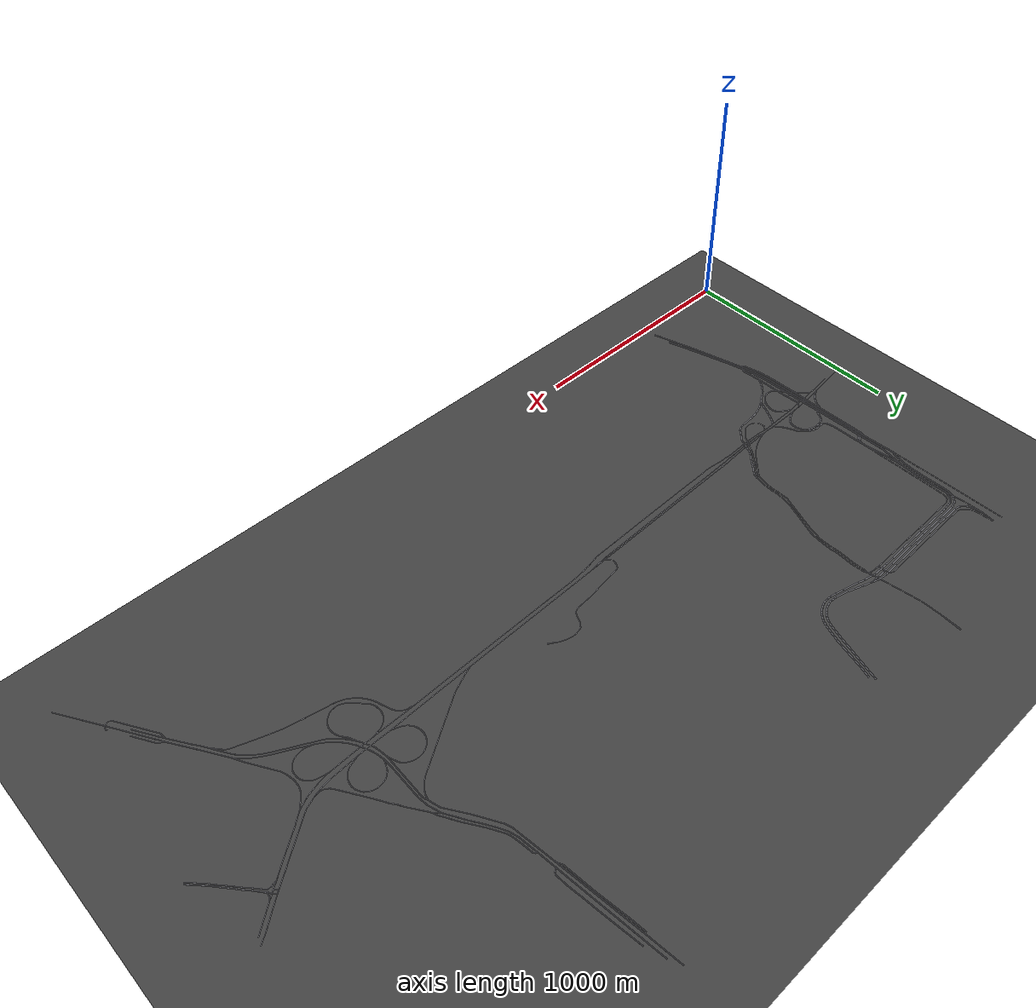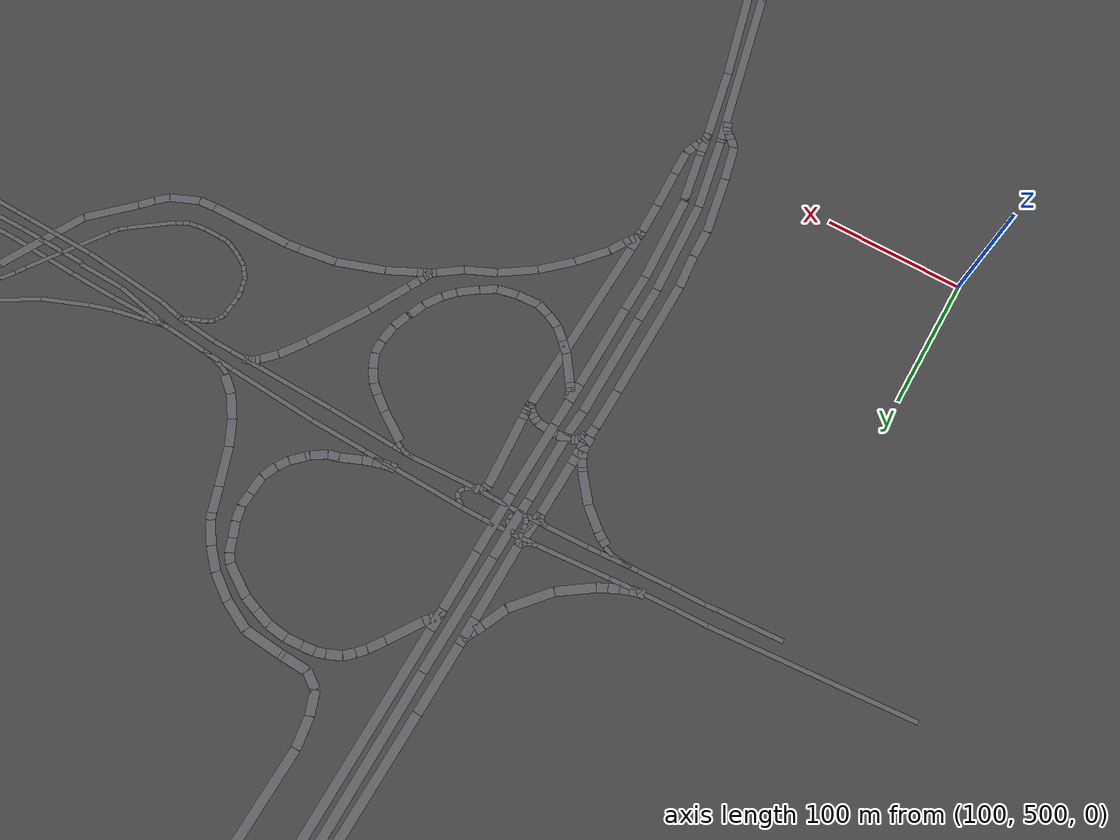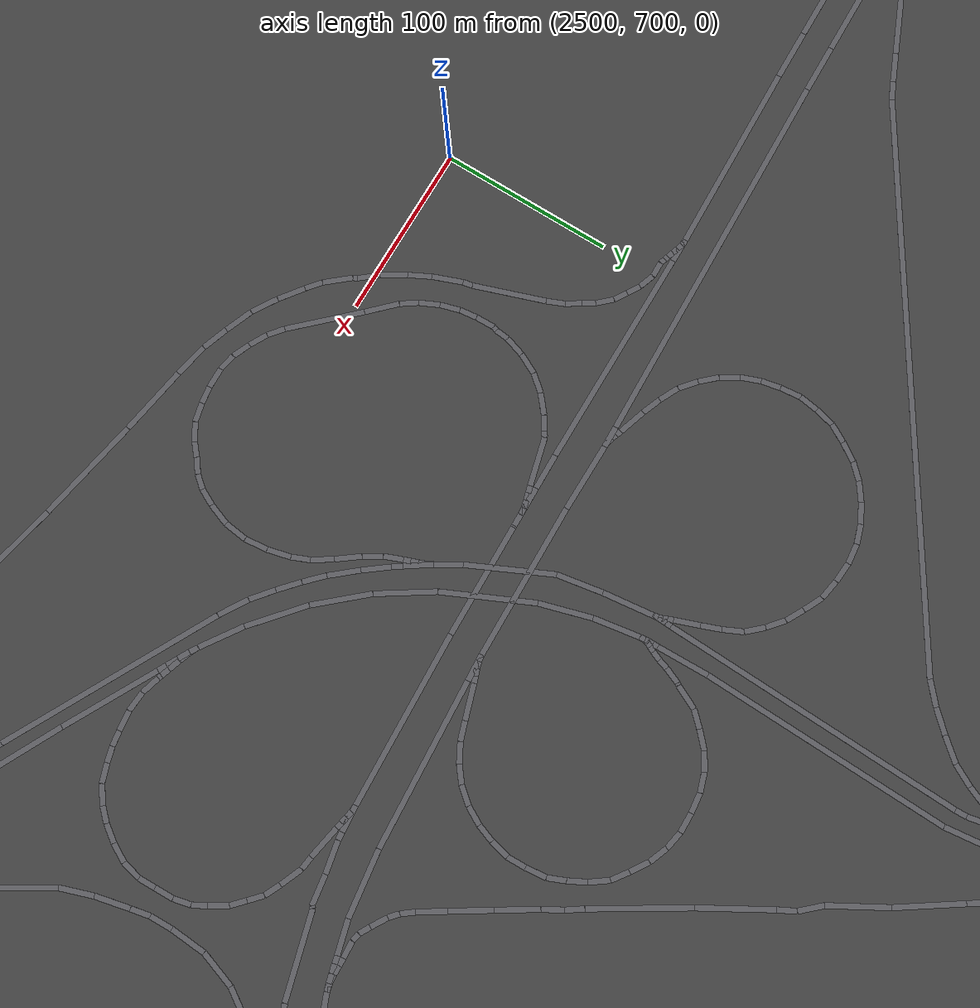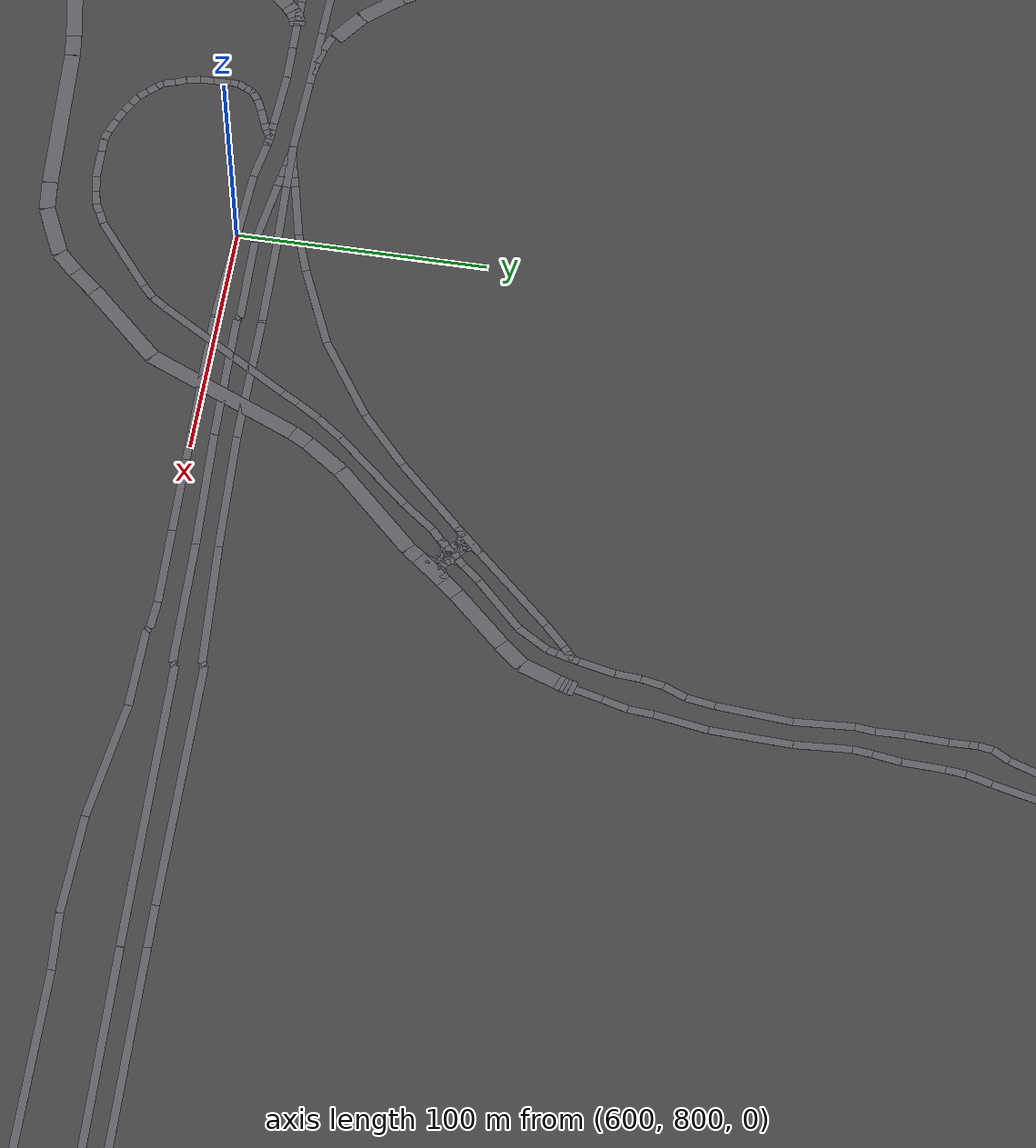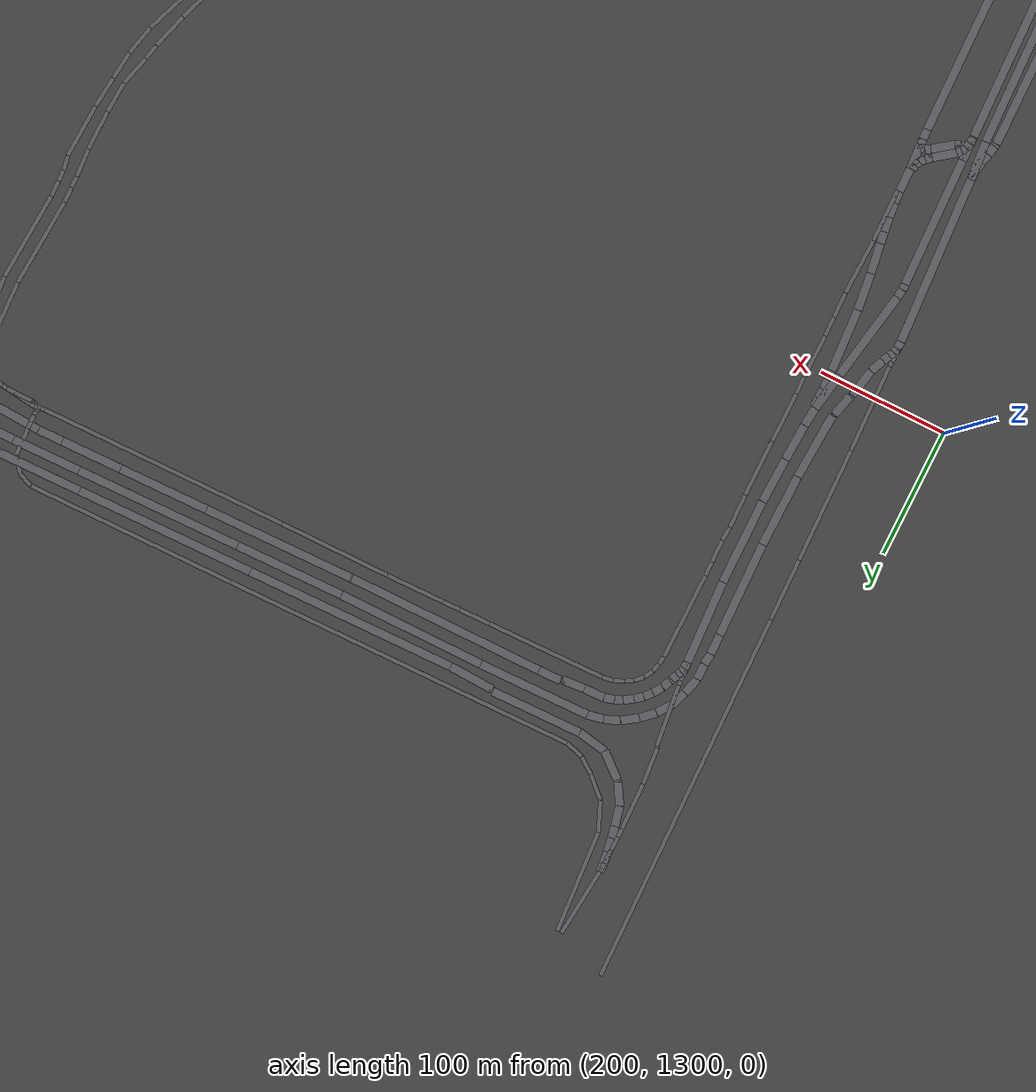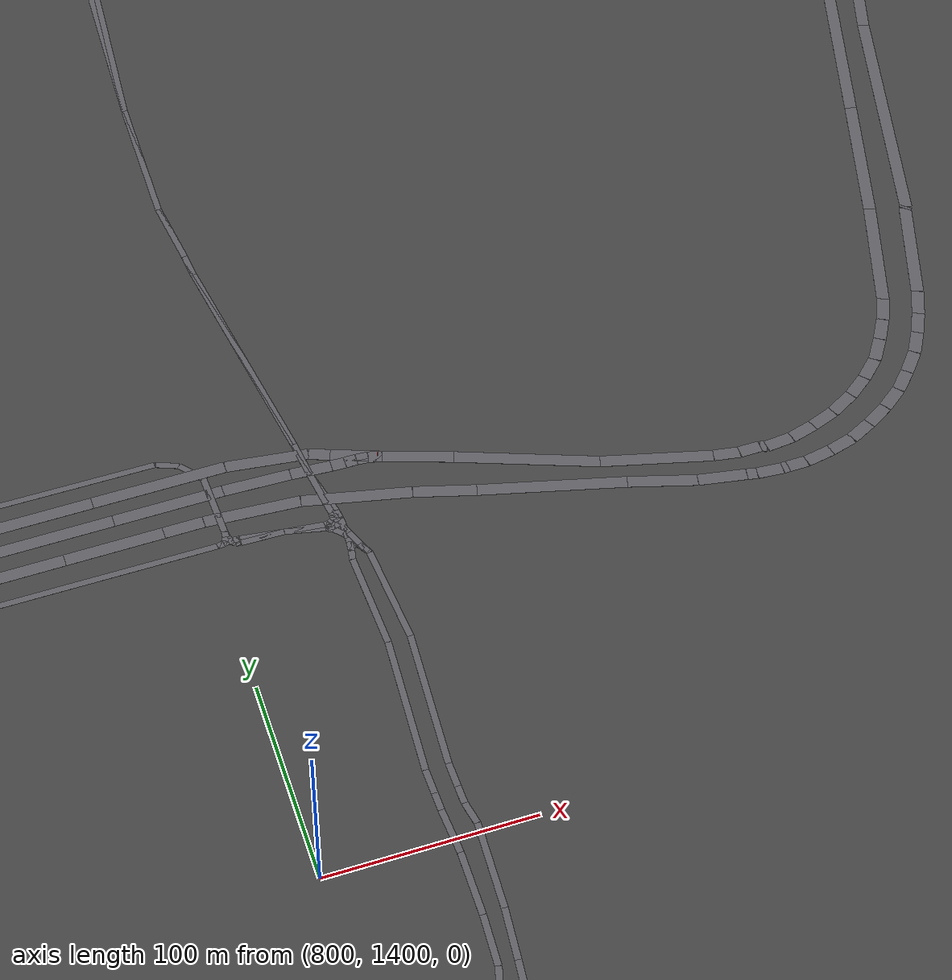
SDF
<?xml version='1.0' encoding='UTF-8'?>
<sdf version="1.6">
  <world name="pravah">
    <plugin filename="gz-sim-physics-system" name="gz::sim::systems::Physics" />
    <plugin filename="gz-sim-sensors-system" name="gz::sim::systems::Sensors">
      <render_engine>ogre2</render_engine>
    </plugin>
    <plugin filename="gz-sim-scene-broadcaster-system" name="gz::sim::systems::SceneBroadcaster" />
    <plugin filename="gz-sim-user-commands-system" name="gz::sim::systems::UserCommands" />
    <light type="directional" name="sun">
      <pose>1695.9 1035.5 200 0 0 0</pose>
      <diffuse>0.9 0.9 0.9 1</diffuse>
      <specular>0.3 0.3 0.3 1</specular>
      <direction>-0.3 0.2 -0.9</direction>
      <cast_shadows>false</cast_shadows>
    </light>
    <model name="ground">
      <static>true</static>
      <link name="link">
        <visual name="visual">
          <pose>1695.9 1035.5 0 0 0 0</pose>
          <geometry>
            <plane>
              <size>3431.8 2111.1</size>
            </plane>
          </geometry>
          <material>
            <ambient>0.25 0.25 0.25 1</ambient>
            <diffuse>0.25 0.25 0.25 1</diffuse>
          </material>
        </visual>
        <collision name="collision">
          <geometry>
            <plane>
              <size>3431.8 2111.1</size>
            </plane>
          </geometry>
        </collision>
      </link>
    </model>
    <model name="road_network">
      <static>true</static>
      <link name="link">
        <visual name="seg_0">
          <pose>266.615 730.865 0.030 0 0 1.3766</pose>
          <geometry>
            <box>
              <size>2.436 6.400 0.040</size>
            </box>
          </geometry>
          <material>
            <ambient>0.35 0.35 0.37 1</ambient>
            <diffuse>0.35 0.35 0.37 1</diffuse>
          </material>
        </visual>
        <visual name="seg_1">
          <pose>267.370 733.082 0.030 0 0 1.1003</pose>
          <geometry>
            <box>
              <size>2.294 6.400 0.040</size>
            </box>
          </geometry>
          <material>
            <ambient>0.35 0.35 0.37 1</ambient>
            <diffuse>0.35 0.35 0.37 1</diffuse>
          </material>
        </visual>
        <visual name="seg_2">
          <pose>268.692 734.955 0.030 0 0 0.8141</pose>
          <geometry>
            <box>
              <size>2.338 6.400 0.040</size>
            </box>
          </geometry>
          <material>
            <ambient>0.35 0.35 0.37 1</ambient>
            <diffuse>0.35 0.35 0.37 1</diffuse>
          </material>
        </visual>
        <visual name="seg_3">
          <pose>270.587 736.480 0.030 0 0 0.5534</pose>
          <geometry>
            <box>
              <size>2.568 6.400 0.040</size>
            </box>
          </geometry>
          <material>
            <ambient>0.35 0.35 0.37 1</ambient>
            <diffuse>0.35 0.35 0.37 1</diffuse>
          </material>
        </visual>
        <visual name="seg_4">
          <pose>264.938 732.990 0.030 0 0 1.5233</pose>
          <geometry>
            <box>
              <size>6.427 6.400 0.040</size>
            </box>
          </geometry>
          <material>
            <ambient>0.35 0.35 0.37 1</ambient>
            <diffuse>0.35 0.35 0.37 1</diffuse>
          </material>
        </visual>
        <visual name="seg_5">
          <pose>265.078 738.775 0.030 0 0 1.5757</pose>
          <geometry>
            <box>
              <size>5.150 6.400 0.040</size>
            </box>
          </geometry>
          <material>
            <ambient>0.35 0.35 0.37 1</ambient>
            <diffuse>0.35 0.35 0.37 1</diffuse>
          </material>
        </visual>
        <visual name="seg_6">
          <pose>264.973 743.925 0.030 0 0 1.6067</pose>
          <geometry>
            <box>
              <size>5.153 6.400 0.040</size>
            </box>
          </geometry>
          <material>
            <ambient>0.35 0.35 0.37 1</ambient>
            <diffuse>0.35 0.35 0.37 1</diffuse>
          </material>
        </visual>
        <visual name="seg_7">
          <pose>264.782 749.720 0.030 0 0 1.6011</pose>
          <geometry>
            <box>
              <size>6.443 6.400 0.040</size>
            </box>
          </geometry>
          <material>
            <ambient>0.35 0.35 0.37 1</ambient>
            <diffuse>0.35 0.35 0.37 1</diffuse>
          </material>
        </visual>
        <visual name="seg_8">
          <pose>263.275 733.088 0.030 0 0 1.5442</pose>
          <geometry>
            <box>
              <size>6.397 6.400 0.040</size>
            </box>
          </geometry>
          <material>
            <ambient>0.35 0.35 0.37 1</ambient>
            <diffuse>0.35 0.35 0.37 1</diffuse>
          </material>
        </visual>
        <visual name="seg_9">
          <pose>262.995 738.760 0.030 0 0 1.7172</pose>
          <geometry>
            <box>
              <size>5.004 6.400 0.040</size>
            </box>
          </geometry>
          <material>
            <ambient>0.35 0.35 0.37 1</ambient>
            <diffuse>0.35 0.35 0.37 1</diffuse>
          </material>
        </visual>
        <visual name="seg_10">
          <pose>261.668 743.550 0.030 0 0 1.9648</pose>
          <geometry>
            <box>
              <size>5.014 6.400 0.040</size>
            </box>
          </geometry>
          <material>
            <ambient>0.35 0.35 0.37 1</ambient>
            <diffuse>0.35 0.35 0.37 1</diffuse>
          </material>
        </visual>
        <visual name="seg_11">
          <pose>258.998 748.572 0.030 0 0 2.1335</pose>
          <geometry>
            <box>
              <size>6.402 6.400 0.040</size>
            </box>
          </geometry>
          <material>
            <ambient>0.35 0.35 0.37 1</ambient>
            <diffuse>0.35 0.35 0.37 1</diffuse>
          </material>
        </visual>
        <visual name="seg_12">
          <pose>2840.815 844.740 0.030 0 0 -3.0669</pose>
          <geometry>
            <box>
              <size>15.553 3.200 0.040</size>
            </box>
          </geometry>
          <material>
            <ambient>0.35 0.35 0.37 1</ambient>
            <diffuse>0.35 0.35 0.37 1</diffuse>
          </material>
        </visual>
        <visual name="seg_13">
          <pose>2846.505 842.155 0.030 0 0 2.9401</pose>
          <geometry>
            <box>
              <size>3.848 3.200 0.040</size>
            </box>
          </geometry>
          <material>
            <ambient>0.35 0.35 0.37 1</ambient>
            <diffuse>0.35 0.35 0.37 1</diffuse>
          </material>
        </visual>
        <visual name="seg_14">
          <pose>2842.685 842.955 0.030 0 0 2.9303</pose>
          <geometry>
            <box>
              <size>3.958 3.200 0.040</size>
            </box>
          </geometry>
          <material>
            <ambient>0.35 0.35 0.37 1</ambient>
            <diffuse>0.35 0.35 0.37 1</diffuse>
          </material>
        </visual>
        <visual name="seg_15">
          <pose>2838.810 843.685 0.030 0 0 2.9806</pose>
          <geometry>
            <box>
              <size>3.931 3.200 0.040</size>
            </box>
          </geometry>
          <material>
            <ambient>0.35 0.35 0.37 1</ambient>
            <diffuse>0.35 0.35 0.37 1</diffuse>
          </material>
        </visual>
        <visual name="seg_16">
          <pose>2834.965 844.080 0.030 0 0 3.0996</pose>
          <geometry>
            <box>
              <size>3.813 3.200 0.040</size>
            </box>
          </geometry>
          <material>
            <ambient>0.35 0.35 0.37 1</ambient>
            <diffuse>0.35 0.35 0.37 1</diffuse>
          </material>
        </visual>
        <visual name="seg_17">
          <pose>2680.360 936.900 0.030 0 0 -2.0316</pose>
          <geometry>
            <box>
              <size>3.193 3.200 0.040</size>
            </box>
          </geometry>
          <material>
            <ambient>0.35 0.35 0.37 1</ambient>
            <diffuse>0.35 0.35 0.37 1</diffuse>
          </material>
        </visual>
        <visual name="seg_18">
          <pose>2679.050 934.380 0.030 0 0 -2.0740</pose>
          <geometry>
            <box>
              <size>2.488 3.200 0.040</size>
            </box>
          </geometry>
          <material>
            <ambient>0.35 0.35 0.37 1</ambient>
            <diffuse>0.35 0.35 0.37 1</diffuse>
          </material>
        </visual>
        <visual name="seg_19">
          <pose>2678.110 932.175 0.030 0 0 -1.8668</pose>
          <geometry>
            <box>
              <size>2.331 3.200 0.040</size>
            </box>
          </geometry>
          <material>
            <ambient>0.35 0.35 0.37 1</ambient>
            <diffuse>0.35 0.35 0.37 1</diffuse>
          </material>
        </visual>
        <visual name="seg_20">
          <pose>2677.815 929.535 0.030 0 0 -1.5413</pose>
          <geometry>
            <box>
              <size>3.051 3.200 0.040</size>
            </box>
          </geometry>
          <material>
            <ambient>0.35 0.35 0.37 1</ambient>
            <diffuse>0.35 0.35 0.37 1</diffuse>
          </material>
        </visual>
        <visual name="seg_21">
          <pose>2677.390 937.465 0.030 0 0 -1.5708</pose>
          <geometry>
            <box>
              <size>3.130 3.200 0.040</size>
            </box>
          </geometry>
          <material>
            <ambient>0.35 0.35 0.37 1</ambient>
            <diffuse>0.35 0.35 0.37 1</diffuse>
          </material>
        </visual>
        <visual name="seg_22">
          <pose>2677.380 934.700 0.030 0 0 -1.5791</pose>
          <geometry>
            <box>
              <size>2.400 3.200 0.040</size>
            </box>
          </geometry>
          <material>
            <ambient>0.35 0.35 0.37 1</ambient>
            <diffuse>0.35 0.35 0.37 1</diffuse>
          </material>
        </visual>
        <visual name="seg_23">
          <pose>2677.425 932.310 0.030 0 0 -1.5246</pose>
          <geometry>
            <box>
              <size>2.383 3.200 0.040</size>
            </box>
          </geometry>
          <material>
            <ambient>0.35 0.35 0.37 1</ambient>
            <diffuse>0.35 0.35 0.37 1</diffuse>
          </material>
        </visual>
        <visual name="seg_24">
          <pose>2677.670 929.565 0.030 0 0 -1.4492</pose>
          <geometry>
            <box>
              <size>3.133 3.200 0.040</size>
            </box>
          </geometry>
          <material>
            <ambient>0.35 0.35 0.37 1</ambient>
            <diffuse>0.35 0.35 0.37 1</diffuse>
          </material>
        </visual>
        <visual name="seg_25">
          <pose>304.230 737.115 0.030 0 0 -0.5244</pose>
          <geometry>
            <box>
              <size>3.755 6.400 0.040</size>
            </box>
          </geometry>
          <material>
            <ambient>0.35 0.35 0.37 1</ambient>
            <diffuse>0.35 0.35 0.37 1</diffuse>
          </material>
        </visual>
        <visual name="seg_26">
          <pose>307.023 735.190 0.030 0 0 -0.7008</pose>
          <geometry>
            <box>
              <size>3.055 6.400 0.040</size>
            </box>
          </geometry>
          <material>
            <ambient>0.35 0.35 0.37 1</ambient>
            <diffuse>0.35 0.35 0.37 1</diffuse>
          </material>
        </visual>
        <visual name="seg_27">
          <pose>308.895 733.173 0.030 0 0 -0.9717</pose>
          <geometry>
            <box>
              <size>2.500 6.400 0.040</size>
            </box>
          </geometry>
          <material>
            <ambient>0.35 0.35 0.37 1</ambient>
            <diffuse>0.35 0.35 0.37 1</diffuse>
          </material>
        </visual>
        <visual name="seg_28">
          <pose>309.845 731.060 0.030 0 0 -1.3477</pose>
          <geometry>
            <box>
              <size>2.215 6.400 0.040</size>
            </box>
          </geometry>
          <material>
            <ambient>0.35 0.35 0.37 1</ambient>
            <diffuse>0.35 0.35 0.37 1</diffuse>
          </material>
        </visual>
        <visual name="seg_29">
          <pose>309.350 740.755 0.030 0 0 -1.4563</pose>
          <geometry>
            <box>
              <size>3.765 6.400 0.040</size>
            </box>
          </geometry>
          <material>
            <ambient>0.35 0.35 0.37 1</ambient>
            <diffuse>0.35 0.35 0.37 1</diffuse>
          </material>
        </visual>
        <visual name="seg_30">
          <pose>309.703 737.600 0.030 0 0 -1.4642</pose>
          <geometry>
            <box>
              <size>2.585 6.400 0.040</size>
            </box>
          </geometry>
          <material>
            <ambient>0.35 0.35 0.37 1</ambient>
            <diffuse>0.35 0.35 0.37 1</diffuse>
          </material>
        </visual>
        <visual name="seg_31">
          <pose>309.920 735.030 0.030 0 0 -1.5086</pose>
          <geometry>
            <box>
              <size>2.575 6.400 0.040</size>
            </box>
          </geometry>
          <material>
            <ambient>0.35 0.35 0.37 1</ambient>
            <diffuse>0.35 0.35 0.37 1</diffuse>
          </material>
        </visual>
        <visual name="seg_32">
          <pose>310.045 731.862 0.030 0 0 -1.5469</pose>
          <geometry>
            <box>
              <size>3.766 6.400 0.040</size>
            </box>
          </geometry>
          <material>
            <ambient>0.35 0.35 0.37 1</ambient>
            <diffuse>0.35 0.35 0.37 1</diffuse>
          </material>
        </visual>
        <visual name="seg_33">
          <pose>314.190 493.230 0.030 0 0 -1.9462</pose>
          <geometry>
            <box>
              <size>5.127 6.400 0.040</size>
            </box>
          </geometry>
          <material>
            <ambient>0.35 0.35 0.37 1</ambient>
            <diffuse>0.35 0.35 0.37 1</diffuse>
          </material>
        </visual>
        <visual name="seg_34">
          <pose>312.442 489.183 0.030 0 0 -2.0230</pose>
          <geometry>
            <box>
              <size>3.696 6.400 0.040</size>
            </box>
          </geometry>
          <material>
            <ambient>0.35 0.35 0.37 1</ambient>
            <diffuse>0.35 0.35 0.37 1</diffuse>
          </material>
        </visual>
        <visual name="seg_35">
          <pose>311.238 485.845 0.030 0 0 -1.8038</pose>
          <geometry>
            <box>
              <size>3.443 6.400 0.040</size>
            </box>
          </geometry>
          <material>
            <ambient>0.35 0.35 0.37 1</ambient>
            <diffuse>0.35 0.35 0.37 1</diffuse>
          </material>
        </visual>
        <visual name="seg_36">
          <pose>311.133 481.748 0.030 0 0 -1.4506</pose>
          <geometry>
            <box>
              <size>4.880 6.400 0.040</size>
            </box>
          </geometry>
          <material>
            <ambient>0.35 0.35 0.37 1</ambient>
            <diffuse>0.35 0.35 0.37 1</diffuse>
          </material>
        </visual>
        <visual name="seg_37">
          <pose>309.817 487.665 0.030 0 0 -1.3804</pose>
          <geometry>
            <box>
              <size>16.987 6.400 0.040</size>
            </box>
          </geometry>
          <material>
            <ambient>0.35 0.35 0.37 1</ambient>
            <diffuse>0.35 0.35 0.37 1</diffuse>
          </material>
        </visual>
        <visual name="seg_38">
          <pose>425.577 691.530 0.030 0 0 -1.9502</pose>
          <geometry>
            <box>
              <size>4.037 6.400 0.040</size>
            </box>
          </geometry>
          <material>
            <ambient>0.35 0.35 0.37 1</ambient>
            <diffuse>0.35 0.35 0.37 1</diffuse>
          </material>
        </visual>
        <visual name="seg_39">
          <pose>424.383 688.298 0.030 0 0 -1.8892</pose>
          <geometry>
            <box>
              <size>2.859 6.400 0.040</size>
            </box>
          </geometry>
          <material>
            <ambient>0.35 0.35 0.37 1</ambient>
            <diffuse>0.35 0.35 0.37 1</diffuse>
          </material>
        </visual>
        <visual name="seg_40">
          <pose>423.260 685.755 0.030 0 0 -2.0886</pose>
          <geometry>
            <box>
              <size>2.728 6.400 0.040</size>
            </box>
          </geometry>
          <material>
            <ambient>0.35 0.35 0.37 1</ambient>
            <diffuse>0.35 0.35 0.37 1</diffuse>
          </material>
        </visual>
        <visual name="seg_41">
          <pose>421.173 683.230 0.030 0 0 -2.3825</pose>
          <geometry>
            <box>
              <size>3.894 6.400 0.040</size>
            </box>
          </geometry>
          <material>
            <ambient>0.35 0.35 0.37 1</ambient>
            <diffuse>0.35 0.35 0.37 1</diffuse>
          </material>
        </visual>
        <visual name="seg_42">
          <pose>429.618 687.670 0.030 0 0 -2.6752</pose>
          <geometry>
            <box>
              <size>4.003 6.400 0.040</size>
            </box>
          </geometry>
          <material>
            <ambient>0.35 0.35 0.37 1</ambient>
            <diffuse>0.35 0.35 0.37 1</diffuse>
          </material>
        </visual>
        <visual name="seg_43">
          <pose>426.588 686.183 0.030 0 0 -2.6999</pose>
          <geometry>
            <box>
              <size>2.749 6.400 0.040</size>
            </box>
          </geometry>
          <material>
            <ambient>0.35 0.35 0.37 1</ambient>
            <diffuse>0.35 0.35 0.37 1</diffuse>
          </material>
        </visual>
        <visual name="seg_44">
          <pose>424.160 684.915 0.030 0 0 -2.6206</pose>
          <geometry>
            <box>
              <size>2.732 6.400 0.040</size>
            </box>
          </geometry>
          <material>
            <ambient>0.35 0.35 0.37 1</ambient>
            <diffuse>0.35 0.35 0.37 1</diffuse>
          </material>
        </visual>
        <visual name="seg_45">
          <pose>421.368 683.062 0.030 0 0 -2.5114</pose>
          <geometry>
            <box>
              <size>3.979 6.400 0.040</size>
            </box>
          </geometry>
          <material>
            <ambient>0.35 0.35 0.37 1</ambient>
            <diffuse>0.35 0.35 0.37 1</diffuse>
          </material>
        </visual>
        <visual name="seg_46">
          <pose>317.210 589.690 0.030 0 0 -2.1311</pose>
          <geometry>
            <box>
              <size>5.005 6.400 0.040</size>
            </box>
          </geometry>
          <material>
            <ambient>0.35 0.35 0.37 1</ambient>
            <diffuse>0.35 0.35 0.37 1</diffuse>
          </material>
        </visual>
        <visual name="seg_47">
          <pose>314.810 586.120 0.030 0 0 -2.2065</pose>
          <geometry>
            <box>
              <size>3.604 6.400 0.040</size>
            </box>
          </geometry>
          <material>
            <ambient>0.35 0.35 0.37 1</ambient>
            <diffuse>0.35 0.35 0.37 1</diffuse>
          </material>
        </visual>
        <visual name="seg_48">
          <pose>313.062 583.133 0.030 0 0 -1.9858</pose>
          <geometry>
            <box>
              <size>3.360 6.400 0.040</size>
            </box>
          </geometry>
          <material>
            <ambient>0.35 0.35 0.37 1</ambient>
            <diffuse>0.35 0.35 0.37 1</diffuse>
          </material>
        </visual>
        <visual name="seg_49">
          <pose>312.243 579.217 0.030 0 0 -1.6307</pose>
          <geometry>
            <box>
              <size>4.764 6.400 0.040</size>
            </box>
          </geometry>
          <material>
            <ambient>0.35 0.35 0.37 1</ambient>
            <diffuse>0.35 0.35 0.37 1</diffuse>
          </material>
        </visual>
        <visual name="seg_50">
          <pose>311.945 585.130 0.030 0 0 -1.5521</pose>
          <geometry>
            <box>
              <size>16.583 6.400 0.040</size>
            </box>
          </geometry>
          <material>
            <ambient>0.35 0.35 0.37 1</ambient>
            <diffuse>0.35 0.35 0.37 1</diffuse>
          </material>
        </visual>
        <visual name="seg_51">
          <pose>3162.705 356.195 0.030 0 0 2.1141</pose>
          <geometry>
            <box>
              <size>10.852 3.200 0.040</size>
            </box>
          </geometry>
          <material>
            <ambient>0.35 0.35 0.37 1</ambient>
            <diffuse>0.35 0.35 0.37 1</diffuse>
          </material>
        </visual>
        <visual name="seg_52">
          <pose>3161.865 351.920 0.030 0 0 1.6312</pose>
          <geometry>
            <box>
              <size>3.146 3.200 0.040</size>
            </box>
          </geometry>
          <material>
            <ambient>0.35 0.35 0.37 1</ambient>
            <diffuse>0.35 0.35 0.37 1</diffuse>
          </material>
        </visual>
        <visual name="seg_53">
          <pose>3161.745 354.685 0.030 0 0 1.5917</pose>
          <geometry>
            <box>
              <size>2.391 3.200 0.040</size>
            </box>
          </geometry>
          <material>
            <ambient>0.35 0.35 0.37 1</ambient>
            <diffuse>0.35 0.35 0.37 1</diffuse>
          </material>
        </visual>
        <visual name="seg_54">
          <pose>3161.500 357.005 0.030 0 0 1.7639</pose>
          <geometry>
            <box>
              <size>2.293 3.200 0.040</size>
            </box>
          </geometry>
          <material>
            <ambient>0.35 0.35 0.37 1</ambient>
            <diffuse>0.35 0.35 0.37 1</diffuse>
          </material>
        </visual>
        <visual name="seg_55">
          <pose>3160.590 359.485 0.030 0 0 2.0418</pose>
          <geometry>
            <box>
              <size>3.041 3.200 0.040</size>
            </box>
          </geometry>
          <material>
            <ambient>0.35 0.35 0.37 1</ambient>
            <diffuse>0.35 0.35 0.37 1</diffuse>
          </material>
        </visual>
        <visual name="seg_56">
          <pose>729.065 912.310 0.030 0 0 2.2727</pose>
          <geometry>
            <box>
              <size>1.781 3.200 0.040</size>
            </box>
          </geometry>
          <material>
            <ambient>0.35 0.35 0.37 1</ambient>
            <diffuse>0.35 0.35 0.37 1</diffuse>
          </material>
        </visual>
        <visual name="seg_57">
          <pose>728.355 913.775 0.030 0 0 1.7411</pose>
          <geometry>
            <box>
              <size>1.593 3.200 0.040</size>
            </box>
          </geometry>
          <material>
            <ambient>0.35 0.35 0.37 1</ambient>
            <diffuse>0.35 0.35 0.37 1</diffuse>
          </material>
        </visual>
        <visual name="seg_58">
          <pose>728.530 915.450 0.030 0 0 1.2356</pose>
          <geometry>
            <box>
              <size>1.885 3.200 0.040</size>
            </box>
          </geometry>
          <material>
            <ambient>0.35 0.35 0.37 1</ambient>
            <diffuse>0.35 0.35 0.37 1</diffuse>
          </material>
        </visual>
        <visual name="seg_59">
          <pose>729.600 917.335 0.030 0 0 0.9185</pose>
          <geometry>
            <box>
              <size>2.504 3.200 0.040</size>
            </box>
          </geometry>
          <material>
            <ambient>0.35 0.35 0.37 1</ambient>
            <diffuse>0.35 0.35 0.37 1</diffuse>
          </material>
        </visual>
        <visual name="seg_60">
          <pose>728.925 911.680 0.030 0 0 3.0718</pose>
          <geometry>
            <box>
              <size>1.433 3.200 0.040</size>
            </box>
          </geometry>
          <material>
            <ambient>0.35 0.35 0.37 1</ambient>
            <diffuse>0.35 0.35 0.37 1</diffuse>
          </material>
        </visual>
        <visual name="seg_61">
          <pose>727.810 911.540 0.030 0 0 -2.6981</pose>
          <geometry>
            <box>
              <size>0.886 3.200 0.040</size>
            </box>
          </geometry>
          <material>
            <ambient>0.35 0.35 0.37 1</ambient>
            <diffuse>0.35 0.35 0.37 1</diffuse>
          </material>
        </visual>
        <visual name="seg_62">
          <pose>727.325 910.915 0.030 0 0 -1.7638</pose>
          <geometry>
            <box>
              <size>0.886 3.200 0.040</size>
            </box>
          </geometry>
          <material>
            <ambient>0.35 0.35 0.37 1</ambient>
            <diffuse>0.35 0.35 0.37 1</diffuse>
          </material>
        </visual>
        <visual name="seg_63">
          <pose>727.465 909.800 0.030 0 0 -1.2513</pose>
          <geometry>
            <box>
              <size>1.433 3.200 0.040</size>
            </box>
          </geometry>
          <material>
            <ambient>0.35 0.35 0.37 1</ambient>
            <diffuse>0.35 0.35 0.37 1</diffuse>
          </material>
        </visual>
        <visual name="seg_64">
          <pose>721.375 908.690 0.030 0 0 0.6889</pose>
          <geometry>
            <box>
              <size>2.422 3.200 0.040</size>
            </box>
          </geometry>
          <material>
            <ambient>0.35 0.35 0.37 1</ambient>
            <diffuse>0.35 0.35 0.37 1</diffuse>
          </material>
        </visual>
        <visual name="seg_65">
          <pose>723.230 909.815 0.030 0 0 0.3683</pose>
          <geometry>
            <box>
              <size>1.972 3.200 0.040</size>
            </box>
          </geometry>
          <material>
            <ambient>0.35 0.35 0.37 1</ambient>
            <diffuse>0.35 0.35 0.37 1</diffuse>
          </material>
        </visual>
        <visual name="seg_66">
          <pose>725.045 910.115 0.030 0 0 -0.0614</pose>
          <geometry>
            <box>
              <size>1.793 3.200 0.040</size>
            </box>
          </geometry>
          <material>
            <ambient>0.35 0.35 0.37 1</ambient>
            <diffuse>0.35 0.35 0.37 1</diffuse>
          </material>
        </visual>
        <visual name="seg_67">
          <pose>726.815 909.590 0.030 0 0 -0.4929</pose>
          <geometry>
            <box>
              <size>1.986 3.200 0.040</size>
            </box>
          </geometry>
          <material>
            <ambient>0.35 0.35 0.37 1</ambient>
            <diffuse>0.35 0.35 0.37 1</diffuse>
          </material>
        </visual>
        <visual name="seg_68">
          <pose>725.400 913.125 0.030 0 0 0.8095</pose>
          <geometry>
            <box>
              <size>14.380 3.200 0.040</size>
            </box>
          </geometry>
          <material>
            <ambient>0.35 0.35 0.37 1</ambient>
            <diffuse>0.35 0.35 0.37 1</diffuse>
          </material>
        </visual>
        <visual name="seg_69">
          <pose>288.933 887.812 0.030 0 0 -2.1997</pose>
          <geometry>
            <box>
              <size>4.445 6.400 0.040</size>
            </box>
          </geometry>
          <material>
            <ambient>0.35 0.35 0.37 1</ambient>
            <diffuse>0.35 0.35 0.37 1</diffuse>
          </material>
        </visual>
        <visual name="seg_70">
          <pose>286.595 884.777 0.030 0 0 -2.2649</pose>
          <geometry>
            <box>
              <size>3.220 6.400 0.040</size>
            </box>
          </geometry>
          <material>
            <ambient>0.35 0.35 0.37 1</ambient>
            <diffuse>0.35 0.35 0.37 1</diffuse>
          </material>
        </visual>
        <visual name="seg_71">
          <pose>284.915 882.205 0.030 0 0 -2.0239</pose>
          <geometry>
            <box>
              <size>2.970 6.400 0.040</size>
            </box>
          </geometry>
          <material>
            <ambient>0.35 0.35 0.37 1</ambient>
            <diffuse>0.35 0.35 0.37 1</diffuse>
          </material>
        </visual>
        <visual name="seg_72">
          <pose>284.097 878.773 0.030 0 0 -1.6505</pose>
          <geometry>
            <box>
              <size>4.208 6.400 0.040</size>
            </box>
          </geometry>
          <material>
            <ambient>0.35 0.35 0.37 1</ambient>
            <diffuse>0.35 0.35 0.37 1</diffuse>
          </material>
        </visual>
        <visual name="seg_73">
          <pose>283.710 884.045 0.030 0 0 -1.5410</pose>
          <geometry>
            <box>
              <size>14.747 6.400 0.040</size>
            </box>
          </geometry>
          <material>
            <ambient>0.35 0.35 0.37 1</ambient>
            <diffuse>0.35 0.35 0.37 1</diffuse>
          </material>
        </visual>
        <visual name="seg_74">
          <pose>289.065 708.480 0.030 0 0 -1.5416</pose>
          <geometry>
            <box>
              <size>14.026 6.400 0.040</size>
            </box>
          </geometry>
          <material>
            <ambient>0.35 0.35 0.37 1</ambient>
            <diffuse>0.35 0.35 0.37 1</diffuse>
          </material>
        </visual>
        <visual name="seg_75">
          <pose>290.632 713.600 0.030 0 0 -1.4812</pose>
          <geometry>
            <box>
              <size>3.855 6.400 0.040</size>
            </box>
          </geometry>
          <material>
            <ambient>0.35 0.35 0.37 1</ambient>
            <diffuse>0.35 0.35 0.37 1</diffuse>
          </material>
        </visual>
        <visual name="seg_76">
          <pose>291.270 710.425 0.030 0 0 -1.2160</pose>
          <geometry>
            <box>
              <size>2.677 6.400 0.040</size>
            </box>
          </geometry>
          <material>
            <ambient>0.35 0.35 0.37 1</ambient>
            <diffuse>0.35 0.35 0.37 1</diffuse>
          </material>
        </visual>
        <visual name="seg_77">
          <pose>292.560 708.043 0.030 0 0 -0.9391</pose>
          <geometry>
            <box>
              <size>2.794 6.400 0.040</size>
            </box>
          </geometry>
          <material>
            <ambient>0.35 0.35 0.37 1</ambient>
            <diffuse>0.35 0.35 0.37 1</diffuse>
          </material>
        </visual>
        <visual name="seg_78">
          <pose>294.632 705.370 0.030 0 0 -0.8915</pose>
          <geometry>
            <box>
              <size>3.972 6.400 0.040</size>
            </box>
          </geometry>
          <material>
            <ambient>0.35 0.35 0.37 1</ambient>
            <diffuse>0.35 0.35 0.37 1</diffuse>
          </material>
        </visual>
        <visual name="seg_79">
          <pose>290.632 1310.618 0.030 0 0 -1.7432</pose>
          <geometry>
            <box>
              <size>30.517 6.400 0.040</size>
            </box>
          </geometry>
          <material>
            <ambient>0.35 0.35 0.37 1</ambient>
            <diffuse>0.35 0.35 0.37 1</diffuse>
          </material>
        </visual>
        <visual name="seg_80">
          <pose>294.585 1321.727 0.030 0 0 -1.6385</pose>
          <geometry>
            <box>
              <size>7.542 6.400 0.040</size>
            </box>
          </geometry>
          <material>
            <ambient>0.35 0.35 0.37 1</ambient>
            <diffuse>0.35 0.35 0.37 1</diffuse>
          </material>
        </visual>
        <visual name="seg_81">
          <pose>294.262 1314.155 0.030 0 0 -1.5885</pose>
          <geometry>
            <box>
              <size>7.621 6.400 0.040</size>
            </box>
          </geometry>
          <material>
            <ambient>0.35 0.35 0.37 1</ambient>
            <diffuse>0.35 0.35 0.37 1</diffuse>
          </material>
        </visual>
        <visual name="seg_82">
          <pose>294.273 1306.537 0.030 0 0 -1.5504</pose>
          <geometry>
            <box>
              <size>7.617 6.400 0.040</size>
            </box>
          </geometry>
          <material>
            <ambient>0.35 0.35 0.37 1</ambient>
            <diffuse>0.35 0.35 0.37 1</diffuse>
          </material>
        </visual>
        <visual name="seg_83">
          <pose>294.528 1298.955 0.030 0 0 -1.5238</pose>
          <geometry>
            <box>
              <size>7.558 6.400 0.040</size>
            </box>
          </geometry>
          <material>
            <ambient>0.35 0.35 0.37 1</ambient>
            <diffuse>0.35 0.35 0.37 1</diffuse>
          </material>
        </visual>
        <visual name="seg_84">
          <pose>310.300 1174.430 0.030 0 0 -1.5568</pose>
          <geometry>
            <box>
              <size>41.304 3.200 0.040</size>
            </box>
          </geometry>
          <material>
            <ambient>0.35 0.35 0.37 1</ambient>
            <diffuse>0.35 0.35 0.37 1</diffuse>
          </material>
        </visual>
        <visual name="seg_85">
          <pose>305.155 1190.138 0.030 0 0 -1.4278</pose>
          <geometry>
            <box>
              <size>9.260 6.400 0.040</size>
            </box>
          </geometry>
          <material>
            <ambient>0.35 0.35 0.37 1</ambient>
            <diffuse>0.35 0.35 0.37 1</diffuse>
          </material>
        </visual>
        <visual name="seg_86">
          <pose>306.530 1179.915 0.030 0 0 -1.4447</pose>
          <geometry>
            <box>
              <size>11.370 6.400 0.040</size>
            </box>
          </geometry>
          <material>
            <ambient>0.35 0.35 0.37 1</ambient>
            <diffuse>0.35 0.35 0.37 1</diffuse>
          </material>
        </visual>
        <visual name="seg_87">
          <pose>307.832 1168.628 0.030 0 0 -1.4671</pose>
          <geometry>
            <box>
              <size>11.356 6.400 0.040</size>
            </box>
          </geometry>
          <material>
            <ambient>0.35 0.35 0.37 1</ambient>
            <diffuse>0.35 0.35 0.37 1</diffuse>
          </material>
        </visual>
        <visual name="seg_88">
          <pose>308.705 1158.365 0.030 0 0 -1.5091</pose>
          <geometry>
            <box>
              <size>9.248 6.400 0.040</size>
            </box>
          </geometry>
          <material>
            <ambient>0.35 0.35 0.37 1</ambient>
            <diffuse>0.35 0.35 0.37 1</diffuse>
          </material>
        </visual>
        <visual name="seg_89">
          <pose>489.120 805.405 0.030 0 0 -3.1228</pose>
          <geometry>
            <box>
              <size>12.262 3.200 0.040</size>
            </box>
          </geometry>
          <material>
            <ambient>0.35 0.35 0.37 1</ambient>
            <diffuse>0.35 0.35 0.37 1</diffuse>
          </material>
        </visual>
        <visual name="seg_90">
          <pose>494.095 805.337 0.030 0 0 -2.9849</pose>
          <geometry>
            <box>
              <size>2.339 6.400 0.040</size>
            </box>
          </geometry>
          <material>
            <ambient>0.35 0.35 0.37 1</ambient>
            <diffuse>0.35 0.35 0.37 1</diffuse>
          </material>
        </visual>
        <visual name="seg_91">
          <pose>491.780 804.662 0.030 0 0 -2.7401</pose>
          <geometry>
            <box>
              <size>2.520 6.400 0.040</size>
            </box>
          </geometry>
          <material>
            <ambient>0.35 0.35 0.37 1</ambient>
            <diffuse>0.35 0.35 0.37 1</diffuse>
          </material>
        </visual>
        <visual name="seg_92">
          <pose>489.452 803.358 0.030 0 0 -2.5336</pose>
          <geometry>
            <box>
              <size>2.845 6.400 0.040</size>
            </box>
          </geometry>
          <material>
            <ambient>0.35 0.35 0.37 1</ambient>
            <diffuse>0.35 0.35 0.37 1</diffuse>
          </material>
        </visual>
        <visual name="seg_93">
          <pose>487.112 801.418 0.030 0 0 -2.3758</pose>
          <geometry>
            <box>
              <size>3.253 6.400 0.040</size>
            </box>
          </geometry>
          <material>
            <ambient>0.35 0.35 0.37 1</ambient>
            <diffuse>0.35 0.35 0.37 1</diffuse>
          </material>
        </visual>
        <visual name="seg_94">
          <pose>282.945 1700.810 0.030 0 0 -1.6122</pose>
          <geometry>
            <box>
              <size>7.006 3.200 0.040</size>
            </box>
          </geometry>
          <material>
            <ambient>0.35 0.35 0.37 1</ambient>
            <diffuse>0.35 0.35 0.37 1</diffuse>
          </material>
        </visual>
        <visual name="seg_95">
          <pose>282.735 1691.840 0.030 0 0 -1.5827</pose>
          <geometry>
            <box>
              <size>10.941 3.200 0.040</size>
            </box>
          </geometry>
          <material>
            <ambient>0.35 0.35 0.37 1</ambient>
            <diffuse>0.35 0.35 0.37 1</diffuse>
          </material>
        </visual>
        <visual name="seg_96">
          <pose>282.655 1680.900 0.030 0 0 -1.5735</pose>
          <geometry>
            <box>
              <size>10.940 3.200 0.040</size>
            </box>
          </geometry>
          <material>
            <ambient>0.35 0.35 0.37 1</ambient>
            <diffuse>0.35 0.35 0.37 1</diffuse>
          </material>
        </visual>
        <visual name="seg_97">
          <pose>282.660 1671.925 0.030 0 0 -1.5651</pose>
          <geometry>
            <box>
              <size>7.010 3.200 0.040</size>
            </box>
          </geometry>
          <material>
            <ambient>0.35 0.35 0.37 1</ambient>
            <diffuse>0.35 0.35 0.37 1</diffuse>
          </material>
        </visual>
        <visual name="seg_98">
          <pose>283.227 1701.207 0.030 0 0 -1.5265</pose>
          <geometry>
            <box>
              <size>6.211 6.400 0.040</size>
            </box>
          </geometry>
          <material>
            <ambient>0.35 0.35 0.37 1</ambient>
            <diffuse>0.35 0.35 0.37 1</diffuse>
          </material>
        </visual>
        <visual name="seg_99">
          <pose>283.993 1693.342 0.030 0 0 -1.4398</pose>
          <geometry>
            <box>
              <size>9.607 6.400 0.040</size>
            </box>
          </geometry>
          <material>
            <ambient>0.35 0.35 0.37 1</ambient>
            <diffuse>0.35 0.35 0.37 1</diffuse>
          </material>
        </visual>
        <visual name="seg_100">
          <pose>285.510 1683.370 0.030 0 0 -1.4016</pose>
          <geometry>
            <box>
              <size>10.571 6.400 0.040</size>
            </box>
          </geometry>
          <material>
            <ambient>0.35 0.35 0.37 1</ambient>
            <diffuse>0.35 0.35 0.37 1</diffuse>
          </material>
        </visual>
        <visual name="seg_101">
          <pose>287.317 1673.722 0.030 0 0 -1.3669</pose>
          <geometry>
            <box>
              <size>9.063 6.400 0.040</size>
            </box>
          </geometry>
          <material>
            <ambient>0.35 0.35 0.37 1</ambient>
            <diffuse>0.35 0.35 0.37 1</diffuse>
          </material>
        </visual>
        <visual name="seg_102">
          <pose>2532.125 1519.515 0.030 0 0 -2.8743</pose>
          <geometry>
            <box>
              <size>1.628 3.200 0.040</size>
            </box>
          </geometry>
          <material>
            <ambient>0.35 0.35 0.37 1</ambient>
            <diffuse>0.35 0.35 0.37 1</diffuse>
          </material>
        </visual>
        <visual name="seg_103">
          <pose>2530.850 1518.685 0.030 0 0 -2.2436</pose>
          <geometry>
            <box>
              <size>1.573 3.200 0.040</size>
            </box>
          </geometry>
          <material>
            <ambient>0.35 0.35 0.37 1</ambient>
            <diffuse>0.35 0.35 0.37 1</diffuse>
          </material>
        </visual>
        <visual name="seg_104">
          <pose>2530.160 1517.050 0.030 0 0 -1.7644</pose>
          <geometry>
            <box>
              <size>2.079 3.200 0.040</size>
            </box>
          </geometry>
          <material>
            <ambient>0.35 0.35 0.37 1</ambient>
            <diffuse>0.35 0.35 0.37 1</diffuse>
          </material>
        </visual>
        <visual name="seg_105">
          <pose>2530.050 1514.615 0.030 0 0 -1.5073</pose>
          <geometry>
            <box>
              <size>2.836 3.200 0.040</size>
            </box>
          </geometry>
          <material>
            <ambient>0.35 0.35 0.37 1</ambient>
            <diffuse>0.35 0.35 0.37 1</diffuse>
          </material>
        </visual>
        <visual name="seg_106">
          <pose>2532.320 1519.320 0.030 0 0 -2.5343</pose>
          <geometry>
            <box>
              <size>1.437 3.200 0.040</size>
            </box>
          </geometry>
          <material>
            <ambient>0.35 0.35 0.37 1</ambient>
            <diffuse>0.35 0.35 0.37 1</diffuse>
          </material>
        </visual>
        <visual name="seg_107">
          <pose>2531.535 1518.510 0.030 0 0 -2.0244</pose>
          <geometry>
            <box>
              <size>0.890 3.200 0.040</size>
            </box>
          </geometry>
          <material>
            <ambient>0.35 0.35 0.37 1</ambient>
            <diffuse>0.35 0.35 0.37 1</diffuse>
          </material>
        </visual>
        <visual name="seg_108">
          <pose>2531.550 1517.715 0.030 0 0 -1.0822</pose>
          <geometry>
            <box>
              <size>0.895 3.200 0.040</size>
            </box>
          </geometry>
          <material>
            <ambient>0.35 0.35 0.37 1</ambient>
            <diffuse>0.35 0.35 0.37 1</diffuse>
          </material>
        </visual>
        <visual name="seg_109">
          <pose>2532.365 1516.930 0.030 0 0 -0.5726</pose>
          <geometry>
            <box>
              <size>1.440 3.200 0.040</size>
            </box>
          </geometry>
          <material>
            <ambient>0.35 0.35 0.37 1</ambient>
            <diffuse>0.35 0.35 0.37 1</diffuse>
          </material>
        </visual>
        <visual name="seg_110">
          <pose>2529.580 1517.920 0.030 0 0 -1.4527</pose>
          <geometry>
            <box>
              <size>9.506 3.200 0.040</size>
            </box>
          </geometry>
          <material>
            <ambient>0.35 0.35 0.37 1</ambient>
            <diffuse>0.35 0.35 0.37 1</diffuse>
          </material>
        </visual>
        <visual name="seg_111">
          <pose>2529.245 1521.295 0.030 0 0 -1.4050</pose>
          <geometry>
            <box>
              <size>2.727 3.200 0.040</size>
            </box>
          </geometry>
          <material>
            <ambient>0.35 0.35 0.37 1</ambient>
            <diffuse>0.35 0.35 0.37 1</diffuse>
          </material>
        </visual>
        <visual name="seg_112">
          <pose>2529.875 1518.990 0.030 0 0 -1.1716</pose>
          <geometry>
            <box>
              <size>2.084 3.200 0.040</size>
            </box>
          </geometry>
          <material>
            <ambient>0.35 0.35 0.37 1</ambient>
            <diffuse>0.35 0.35 0.37 1</diffuse>
          </material>
        </visual>
        <visual name="seg_113">
          <pose>2530.865 1517.465 0.030 0 0 -0.7680</pose>
          <geometry>
            <box>
              <size>1.627 3.200 0.040</size>
            </box>
          </geometry>
          <material>
            <ambient>0.35 0.35 0.37 1</ambient>
            <diffuse>0.35 0.35 0.37 1</diffuse>
          </material>
        </visual>
        <visual name="seg_114">
          <pose>2532.210 1516.720 0.030 0 0 -0.2326</pose>
          <geometry>
            <box>
              <size>1.562 3.200 0.040</size>
            </box>
          </geometry>
          <material>
            <ambient>0.35 0.35 0.37 1</ambient>
            <diffuse>0.35 0.35 0.37 1</diffuse>
          </material>
        </visual>
        <visual name="seg_115">
          <pose>770.795 958.400 0.030 0 0 1.3172</pose>
          <geometry>
            <box>
              <size>9.049 3.200 0.040</size>
            </box>
          </geometry>
          <material>
            <ambient>0.35 0.35 0.37 1</ambient>
            <diffuse>0.35 0.35 0.37 1</diffuse>
          </material>
        </visual>
        <visual name="seg_116">
          <pose>767.490 957.155 0.030 0 0 0.6957</pose>
          <geometry>
            <box>
              <size>2.606 3.200 0.040</size>
            </box>
          </geometry>
          <material>
            <ambient>0.35 0.35 0.37 1</ambient>
            <diffuse>0.35 0.35 0.37 1</diffuse>
          </material>
        </visual>
        <visual name="seg_117">
          <pose>769.245 958.550 0.030 0 0 0.6382</pose>
          <geometry>
            <box>
              <size>1.880 3.200 0.040</size>
            </box>
          </geometry>
          <material>
            <ambient>0.35 0.35 0.37 1</ambient>
            <diffuse>0.35 0.35 0.37 1</diffuse>
          </material>
        </visual>
        <visual name="seg_118">
          <pose>770.560 959.780 0.030 0 0 0.8746</pose>
          <geometry>
            <box>
              <size>1.746 3.200 0.040</size>
            </box>
          </geometry>
          <material>
            <ambient>0.35 0.35 0.37 1</ambient>
            <diffuse>0.35 0.35 0.37 1</diffuse>
          </material>
        </visual>
        <visual name="seg_119">
          <pose>771.525 961.615 0.030 0 0 1.2362</pose>
          <geometry>
            <box>
              <size>2.467 3.200 0.040</size>
            </box>
          </geometry>
          <material>
            <ambient>0.35 0.35 0.37 1</ambient>
            <diffuse>0.35 0.35 0.37 1</diffuse>
          </material>
        </visual>
        <visual name="seg_120">
          <pose>2645.160 838.400 0.030 0 0 -3.1226</pose>
          <geometry>
            <box>
              <size>16.863 3.200 0.040</size>
            </box>
          </geometry>
          <material>
            <ambient>0.35 0.35 0.37 1</ambient>
            <diffuse>0.35 0.35 0.37 1</diffuse>
          </material>
        </visual>
        <visual name="seg_121">
          <pose>2651.595 838.330 0.030 0 0 -3.0268</pose>
          <geometry>
            <box>
              <size>4.016 3.200 0.040</size>
            </box>
          </geometry>
          <material>
            <ambient>0.35 0.35 0.37 1</ambient>
            <diffuse>0.35 0.35 0.37 1</diffuse>
          </material>
        </visual>
        <visual name="seg_122">
          <pose>2647.470 837.595 0.030 0 0 -2.9088</pose>
          <geometry>
            <box>
              <size>4.378 3.200 0.040</size>
            </box>
          </geometry>
          <material>
            <ambient>0.35 0.35 0.37 1</ambient>
            <diffuse>0.35 0.35 0.37 1</diffuse>
          </material>
        </visual>
        <visual name="seg_123">
          <pose>2643.225 836.475 0.030 0 0 -2.8586</pose>
          <geometry>
            <box>
              <size>4.405 3.200 0.040</size>
            </box>
          </geometry>
          <material>
            <ambient>0.35 0.35 0.37 1</ambient>
            <diffuse>0.35 0.35 0.37 1</diffuse>
          </material>
        </visual>
        <visual name="seg_124">
          <pose>2639.160 835.305 0.030 0 0 -2.8643</pose>
          <geometry>
            <box>
              <size>4.055 3.200 0.040</size>
            </box>
          </geometry>
          <material>
            <ambient>0.35 0.35 0.37 1</ambient>
            <diffuse>0.35 0.35 0.37 1</diffuse>
          </material>
        </visual>
        <visual name="seg_125">
          <pose>2480.070 837.385 0.030 0 0 -3.1351</pose>
          <geometry>
            <box>
              <size>13.920 3.200 0.040</size>
            </box>
          </geometry>
          <material>
            <ambient>0.35 0.35 0.37 1</ambient>
            <diffuse>0.35 0.35 0.37 1</diffuse>
          </material>
        </visual>
        <visual name="seg_126">
          <pose>2484.800 834.450 0.030 0 0 2.8075</pose>
          <geometry>
            <box>
              <size>3.599 3.200 0.040</size>
            </box>
          </geometry>
          <material>
            <ambient>0.35 0.35 0.37 1</ambient>
            <diffuse>0.35 0.35 0.37 1</diffuse>
          </material>
        </visual>
        <visual name="seg_127">
          <pose>2481.495 835.620 0.030 0 0 2.7948</pose>
          <geometry>
            <box>
              <size>3.413 3.200 0.040</size>
            </box>
          </geometry>
          <material>
            <ambient>0.35 0.35 0.37 1</ambient>
            <diffuse>0.35 0.35 0.37 1</diffuse>
          </material>
        </visual>
        <visual name="seg_128">
          <pose>2478.265 836.630 0.030 0 0 2.8829</pose>
          <geometry>
            <box>
              <size>3.362 3.200 0.040</size>
            </box>
          </geometry>
          <material>
            <ambient>0.35 0.35 0.37 1</ambient>
            <diffuse>0.35 0.35 0.37 1</diffuse>
          </material>
        </visual>
        <visual name="seg_129">
          <pose>2474.875 837.200 0.030 0 0 3.0624</pose>
          <geometry>
            <box>
              <size>3.541 3.200 0.040</size>
            </box>
          </geometry>
          <material>
            <ambient>0.35 0.35 0.37 1</ambient>
            <diffuse>0.35 0.35 0.37 1</diffuse>
          </material>
        </visual>
        <visual name="seg_130">
          <pose>364.470 803.910 0.030 0 0 -3.1144</pose>
          <geometry>
            <box>
              <size>15.426 3.200 0.040</size>
            </box>
          </geometry>
          <material>
            <ambient>0.35 0.35 0.37 1</ambient>
            <diffuse>0.35 0.35 0.37 1</diffuse>
          </material>
        </visual>
        <visual name="seg_131">
          <pose>369.045 801.450 0.030 0 0 2.6751</pose>
          <geometry>
            <box>
              <size>4.758 3.200 0.040</size>
            </box>
          </geometry>
          <material>
            <ambient>0.35 0.35 0.37 1</ambient>
            <diffuse>0.35 0.35 0.37 1</diffuse>
          </material>
        </visual>
        <visual name="seg_132">
          <pose>365.180 803.055 0.030 0 0 2.8433</pose>
          <geometry>
            <box>
              <size>3.641 3.200 0.040</size>
            </box>
          </geometry>
          <material>
            <ambient>0.35 0.35 0.37 1</ambient>
            <diffuse>0.35 0.35 0.37 1</diffuse>
          </material>
        </visual>
        <visual name="seg_133">
          <pose>361.830 803.735 0.030 0 0 3.0518</pose>
          <geometry>
            <box>
              <size>3.233 3.200 0.040</size>
            </box>
          </geometry>
          <material>
            <ambient>0.35 0.35 0.37 1</ambient>
            <diffuse>0.35 0.35 0.37 1</diffuse>
          </material>
        </visual>
        <visual name="seg_134">
          <pose>358.490 803.790 0.030 0 0 -3.0896</pose>
          <geometry>
            <box>
              <size>3.465 3.200 0.040</size>
            </box>
          </geometry>
          <material>
            <ambient>0.35 0.35 0.37 1</ambient>
            <diffuse>0.35 0.35 0.37 1</diffuse>
          </material>
        </visual>
        <visual name="seg_135">
          <pose>2234.955 849.465 0.030 0 0 0.0188</pose>
          <geometry>
            <box>
              <size>13.272 3.200 0.040</size>
            </box>
          </geometry>
          <material>
            <ambient>0.35 0.35 0.37 1</ambient>
            <diffuse>0.35 0.35 0.37 1</diffuse>
          </material>
        </visual>
        <visual name="seg_136">
          <pose>2230.030 849.540 0.030 0 0 0.1164</pose>
          <geometry>
            <box>
              <size>3.443 3.200 0.040</size>
            </box>
          </geometry>
          <material>
            <ambient>0.35 0.35 0.37 1</ambient>
            <diffuse>0.35 0.35 0.37 1</diffuse>
          </material>
        </visual>
        <visual name="seg_137">
          <pose>2233.240 850.205 0.030 0 0 0.3006</pose>
          <geometry>
            <box>
              <size>3.141 3.200 0.040</size>
            </box>
          </geometry>
          <material>
            <ambient>0.35 0.35 0.37 1</ambient>
            <diffuse>0.35 0.35 0.37 1</diffuse>
          </material>
        </visual>
        <visual name="seg_138">
          <pose>2236.210 851.275 0.030 0 0 0.3904</pose>
          <geometry>
            <box>
              <size>3.179 3.200 0.040</size>
            </box>
          </geometry>
          <material>
            <ambient>0.35 0.35 0.37 1</ambient>
            <diffuse>0.35 0.35 0.37 1</diffuse>
          </material>
        </visual>
        <visual name="seg_139">
          <pose>2239.310 852.520 0.030 0 0 0.3741</pose>
          <geometry>
            <box>
              <size>3.502 3.200 0.040</size>
            </box>
          </geometry>
          <material>
            <ambient>0.35 0.35 0.37 1</ambient>
            <diffuse>0.35 0.35 0.37 1</diffuse>
          </material>
        </visual>
        <visual name="seg_140">
          <pose>373.830 816.530 0.030 0 0 0.0190</pose>
          <geometry>
            <box>
              <size>24.204 3.200 0.040</size>
            </box>
          </geometry>
          <material>
            <ambient>0.35 0.35 0.37 1</ambient>
            <diffuse>0.35 0.35 0.37 1</diffuse>
          </material>
        </visual>
        <visual name="seg_141">
          <pose>363.903 816.543 0.030 0 0 0.1112</pose>
          <geometry>
            <box>
              <size>4.372 6.400 0.040</size>
            </box>
          </geometry>
          <material>
            <ambient>0.35 0.35 0.37 1</ambient>
            <diffuse>0.35 0.35 0.37 1</diffuse>
          </material>
        </visual>
        <visual name="seg_142">
          <pose>368.758 817.425 0.030 0 0 0.2342</pose>
          <geometry>
            <box>
              <size>5.516 6.400 0.040</size>
            </box>
          </geometry>
          <material>
            <ambient>0.35 0.35 0.37 1</ambient>
            <diffuse>0.35 0.35 0.37 1</diffuse>
          </material>
        </visual>
        <visual name="seg_143">
          <pose>374.505 819.082 0.030 0 0 0.3205</pose>
          <geometry>
            <box>
              <size>6.459 6.400 0.040</size>
            </box>
          </geometry>
          <material>
            <ambient>0.35 0.35 0.37 1</ambient>
            <diffuse>0.35 0.35 0.37 1</diffuse>
          </material>
        </visual>
        <visual name="seg_144">
          <pose>380.900 821.475 0.030 0 0 0.3916</pose>
          <geometry>
            <box>
              <size>7.205 6.400 0.040</size>
            </box>
          </geometry>
          <material>
            <ambient>0.35 0.35 0.37 1</ambient>
            <diffuse>0.35 0.35 0.37 1</diffuse>
          </material>
        </visual>
        <visual name="seg_145">
          <pose>2591.300 858.375 0.030 0 0 0.0233</pose>
          <geometry>
            <box>
              <size>12.423 3.200 0.040</size>
            </box>
          </geometry>
          <material>
            <ambient>0.35 0.35 0.37 1</ambient>
            <diffuse>0.35 0.35 0.37 1</diffuse>
          </material>
        </visual>
        <visual name="seg_146">
          <pose>2587.190 861.270 0.030 0 0 -0.3574</pose>
          <geometry>
            <box>
              <size>3.373 3.200 0.040</size>
            </box>
          </geometry>
          <material>
            <ambient>0.35 0.35 0.37 1</ambient>
            <diffuse>0.35 0.35 0.37 1</diffuse>
          </material>
        </visual>
        <visual name="seg_147">
          <pose>2590.120 860.150 0.030 0 0 -0.3741</pose>
          <geometry>
            <box>
              <size>2.901 3.200 0.040</size>
            </box>
          </geometry>
          <material>
            <ambient>0.35 0.35 0.37 1</ambient>
            <diffuse>0.35 0.35 0.37 1</diffuse>
          </material>
        </visual>
        <visual name="seg_148">
          <pose>2592.840 859.230 0.030 0 0 -0.2773</pose>
          <geometry>
            <box>
              <size>2.849 3.200 0.040</size>
            </box>
          </geometry>
          <material>
            <ambient>0.35 0.35 0.37 1</ambient>
            <diffuse>0.35 0.35 0.37 1</diffuse>
          </material>
        </visual>
        <visual name="seg_149">
          <pose>2595.860 858.680 0.030 0 0 -0.0967</pose>
          <geometry>
            <box>
              <size>3.315 3.200 0.040</size>
            </box>
          </geometry>
          <material>
            <ambient>0.35 0.35 0.37 1</ambient>
            <diffuse>0.35 0.35 0.37 1</diffuse>
          </material>
        </visual>
        <visual name="seg_150">
          <pose>2807.500 725.780 0.030 0 0 -0.5385</pose>
          <geometry>
            <box>
              <size>5.265 3.200 0.040</size>
            </box>
          </geometry>
          <material>
            <ambient>0.35 0.35 0.37 1</ambient>
            <diffuse>0.35 0.35 0.37 1</diffuse>
          </material>
        </visual>
        <visual name="seg_151">
          <pose>2812.875 722.745 0.030 0 0 -0.4959</pose>
          <geometry>
            <box>
              <size>7.083 3.200 0.040</size>
            </box>
          </geometry>
          <material>
            <ambient>0.35 0.35 0.37 1</ambient>
            <diffuse>0.35 0.35 0.37 1</diffuse>
          </material>
        </visual>
        <visual name="seg_152">
          <pose>2819.135 719.415 0.030 0 0 -0.4819</pose>
          <geometry>
            <box>
              <size>7.098 3.200 0.040</size>
            </box>
          </geometry>
          <material>
            <ambient>0.35 0.35 0.37 1</ambient>
            <diffuse>0.35 0.35 0.37 1</diffuse>
          </material>
        </visual>
        <visual name="seg_153">
          <pose>2824.615 716.545 0.030 0 0 -0.4832</pose>
          <geometry>
            <box>
              <size>5.274 3.200 0.040</size>
            </box>
          </geometry>
          <material>
            <ambient>0.35 0.35 0.37 1</ambient>
            <diffuse>0.35 0.35 0.37 1</diffuse>
          </material>
        </visual>
        <visual name="seg_154">
          <pose>2807.585 725.975 0.030 0 0 -0.4577</pose>
          <geometry>
            <box>
              <size>5.228 3.200 0.040</size>
            </box>
          </geometry>
          <material>
            <ambient>0.35 0.35 0.37 1</ambient>
            <diffuse>0.35 0.35 0.37 1</diffuse>
          </material>
        </visual>
        <visual name="seg_155">
          <pose>2813.250 723.590 0.030 0 0 -0.3548</pose>
          <geometry>
            <box>
              <size>7.081 3.200 0.040</size>
            </box>
          </geometry>
          <material>
            <ambient>0.35 0.35 0.37 1</ambient>
            <diffuse>0.35 0.35 0.37 1</diffuse>
          </material>
        </visual>
        <visual name="seg_156">
          <pose>2819.945 721.235 0.030 0 0 -0.3218</pose>
          <geometry>
            <box>
              <size>7.115 3.200 0.040</size>
            </box>
          </geometry>
          <material>
            <ambient>0.35 0.35 0.37 1</ambient>
            <diffuse>0.35 0.35 0.37 1</diffuse>
          </material>
        </visual>
        <visual name="seg_157">
          <pose>2825.825 719.280 0.030 0 0 -0.3200</pose>
          <geometry>
            <box>
              <size>5.278 3.200 0.040</size>
            </box>
          </geometry>
          <material>
            <ambient>0.35 0.35 0.37 1</ambient>
            <diffuse>0.35 0.35 0.37 1</diffuse>
          </material>
        </visual>
        <visual name="seg_158">
          <pose>2706.125 805.245 0.030 0 0 2.1674</pose>
          <geometry>
            <box>
              <size>16.500 3.200 0.040</size>
            </box>
          </geometry>
          <material>
            <ambient>0.35 0.35 0.37 1</ambient>
            <diffuse>0.35 0.35 0.37 1</diffuse>
          </material>
        </visual>
        <visual name="seg_159">
          <pose>2706.960 798.650 0.030 0 0 1.9179</pose>
          <geometry>
            <box>
              <size>3.998 3.200 0.040</size>
            </box>
          </geometry>
          <material>
            <ambient>0.35 0.35 0.37 1</ambient>
            <diffuse>0.35 0.35 0.37 1</diffuse>
          </material>
        </visual>
        <visual name="seg_160">
          <pose>2705.565 802.545 0.030 0 0 1.9118</pose>
          <geometry>
            <box>
              <size>4.276 3.200 0.040</size>
            </box>
          </geometry>
          <material>
            <ambient>0.35 0.35 0.37 1</ambient>
            <diffuse>0.35 0.35 0.37 1</diffuse>
          </material>
        </visual>
        <visual name="seg_161">
          <pose>2704.060 806.540 0.030 0 0 1.9504</pose>
          <geometry>
            <box>
              <size>4.264 3.200 0.040</size>
            </box>
          </geometry>
          <material>
            <ambient>0.35 0.35 0.37 1</ambient>
            <diffuse>0.35 0.35 0.37 1</diffuse>
          </material>
        </visual>
        <visual name="seg_162">
          <pose>2702.380 810.295 0.030 0 0 2.0356</pose>
          <geometry>
            <box>
              <size>3.971 3.200 0.040</size>
            </box>
          </geometry>
          <material>
            <ambient>0.35 0.35 0.37 1</ambient>
            <diffuse>0.35 0.35 0.37 1</diffuse>
          </material>
        </visual>
        <visual name="seg_163">
          <pose>204.495 792.700 0.030 0 0 -3.0443</pose>
          <geometry>
            <box>
              <size>26.355 3.200 0.040</size>
            </box>
          </geometry>
          <material>
            <ambient>0.35 0.35 0.37 1</ambient>
            <diffuse>0.35 0.35 0.37 1</diffuse>
          </material>
        </visual>
        <visual name="seg_164">
          <pose>213.615 790.355 0.030 0 0 2.8620</pose>
          <geometry>
            <box>
              <size>7.501 3.200 0.040</size>
            </box>
          </geometry>
          <material>
            <ambient>0.35 0.35 0.37 1</ambient>
            <diffuse>0.35 0.35 0.37 1</diffuse>
          </material>
        </visual>
        <visual name="seg_165">
          <pose>206.370 791.705 0.030 0 0 3.0553</pose>
          <geometry>
            <box>
              <size>7.307 3.200 0.040</size>
            </box>
          </geometry>
          <material>
            <ambient>0.35 0.35 0.37 1</ambient>
            <diffuse>0.35 0.35 0.37 1</diffuse>
          </material>
        </visual>
        <visual name="seg_166">
          <pose>199.480 791.930 0.030 0 0 -3.1139</pose>
          <geometry>
            <box>
              <size>6.502 3.200 0.040</size>
            </box>
          </geometry>
          <material>
            <ambient>0.35 0.35 0.37 1</ambient>
            <diffuse>0.35 0.35 0.37 1</diffuse>
          </material>
        </visual>
        <visual name="seg_167">
          <pose>193.805 791.630 0.030 0 0 -3.0552</pose>
          <geometry>
            <box>
              <size>4.868 3.200 0.040</size>
            </box>
          </geometry>
          <material>
            <ambient>0.35 0.35 0.37 1</ambient>
            <diffuse>0.35 0.35 0.37 1</diffuse>
          </material>
        </visual>
        <visual name="seg_168">
          <pose>556.535 814.280 0.030 0 0 -0.0889</pose>
          <geometry>
            <box>
              <size>4.508 3.200 0.040</size>
            </box>
          </geometry>
          <material>
            <ambient>0.35 0.35 0.37 1</ambient>
            <diffuse>0.35 0.35 0.37 1</diffuse>
          </material>
        </visual>
        <visual name="seg_169">
          <pose>561.455 813.700 0.030 0 0 -0.1411</pose>
          <geometry>
            <box>
              <size>5.404 3.200 0.040</size>
            </box>
          </geometry>
          <material>
            <ambient>0.35 0.35 0.37 1</ambient>
            <diffuse>0.35 0.35 0.37 1</diffuse>
          </material>
        </visual>
        <visual name="seg_170">
          <pose>566.805 812.885 0.030 0 0 -0.1612</pose>
          <geometry>
            <box>
              <size>5.420 3.200 0.040</size>
            </box>
          </geometry>
          <material>
            <ambient>0.35 0.35 0.37 1</ambient>
            <diffuse>0.35 0.35 0.37 1</diffuse>
          </material>
        </visual>
        <visual name="seg_171">
          <pose>571.710 812.095 0.030 0 0 -0.1579</pose>
          <geometry>
            <box>
              <size>4.516 3.200 0.040</size>
            </box>
          </geometry>
          <material>
            <ambient>0.35 0.35 0.37 1</ambient>
            <diffuse>0.35 0.35 0.37 1</diffuse>
          </material>
        </visual>
        <visual name="seg_172">
          <pose>564.205 814.845 0.030 0 0 0.0368</pose>
          <geometry>
            <box>
              <size>19.843 3.200 0.040</size>
            </box>
          </geometry>
          <material>
            <ambient>0.35 0.35 0.37 1</ambient>
            <diffuse>0.35 0.35 0.37 1</diffuse>
          </material>
        </visual>
        <visual name="seg_173">
          <pose>556.505 814.685 0.030 0 0 0.0923</pose>
          <geometry>
            <box>
              <size>4.449 3.200 0.040</size>
            </box>
          </geometry>
          <material>
            <ambient>0.35 0.35 0.37 1</ambient>
            <diffuse>0.35 0.35 0.37 1</diffuse>
          </material>
        </visual>
        <visual name="seg_174">
          <pose>561.340 815.475 0.030 0 0 0.2197</pose>
          <geometry>
            <box>
              <size>5.369 3.200 0.040</size>
            </box>
          </geometry>
          <material>
            <ambient>0.35 0.35 0.37 1</ambient>
            <diffuse>0.35 0.35 0.37 1</diffuse>
          </material>
        </visual>
        <visual name="seg_175">
          <pose>566.570 816.765 0.030 0 0 0.2638</pose>
          <geometry>
            <box>
              <size>5.407 3.200 0.040</size>
            </box>
          </geometry>
          <material>
            <ambient>0.35 0.35 0.37 1</ambient>
            <diffuse>0.35 0.35 0.37 1</diffuse>
          </material>
        </visual>
        <visual name="seg_176">
          <pose>571.355 818.055 0.030 0 0 0.2627</pose>
          <geometry>
            <box>
              <size>4.505 3.200 0.040</size>
            </box>
          </geometry>
          <material>
            <ambient>0.35 0.35 0.37 1</ambient>
            <diffuse>0.35 0.35 0.37 1</diffuse>
          </material>
        </visual>
        <visual name="seg_177">
          <pose>553.665 804.280 0.030 0 0 2.9983</pose>
          <geometry>
            <box>
              <size>3.082 3.200 0.040</size>
            </box>
          </geometry>
          <material>
            <ambient>0.35 0.35 0.37 1</ambient>
            <diffuse>0.35 0.35 0.37 1</diffuse>
          </material>
        </visual>
        <visual name="seg_178">
          <pose>550.995 804.585 0.030 0 0 3.0675</pose>
          <geometry>
            <box>
              <size>2.296 3.200 0.040</size>
            </box>
          </geometry>
          <material>
            <ambient>0.35 0.35 0.37 1</ambient>
            <diffuse>0.35 0.35 0.37 1</diffuse>
          </material>
        </visual>
        <visual name="seg_179">
          <pose>548.700 804.695 0.030 0 0 3.1199</pose>
          <geometry>
            <box>
              <size>2.301 3.200 0.040</size>
            </box>
          </geometry>
          <material>
            <ambient>0.35 0.35 0.37 1</ambient>
            <diffuse>0.35 0.35 0.37 1</diffuse>
          </material>
        </visual>
        <visual name="seg_180">
          <pose>546.005 804.775 0.030 0 0 3.1060</pose>
          <geometry>
            <box>
              <size>3.092 3.200 0.040</size>
            </box>
          </geometry>
          <material>
            <ambient>0.35 0.35 0.37 1</ambient>
            <diffuse>0.35 0.35 0.37 1</diffuse>
          </material>
        </visual>
        <visual name="seg_181">
          <pose>553.690 804.140 0.030 0 0 3.0883</pose>
          <geometry>
            <box>
              <size>3.004 3.200 0.040</size>
            </box>
          </geometry>
          <material>
            <ambient>0.35 0.35 0.37 1</ambient>
            <diffuse>0.35 0.35 0.37 1</diffuse>
          </material>
        </visual>
        <visual name="seg_182">
          <pose>551.110 803.910 0.030 0 0 -2.8621</pose>
          <geometry>
            <box>
              <size>2.247 3.200 0.040</size>
            </box>
          </geometry>
          <material>
            <ambient>0.35 0.35 0.37 1</ambient>
            <diffuse>0.35 0.35 0.37 1</diffuse>
          </material>
        </visual>
        <visual name="seg_183">
          <pose>548.975 803.040 0.030 0 0 -2.6536</pose>
          <geometry>
            <box>
              <size>2.389 3.200 0.040</size>
            </box>
          </geometry>
          <material>
            <ambient>0.35 0.35 0.37 1</ambient>
            <diffuse>0.35 0.35 0.37 1</diffuse>
          </material>
        </visual>
        <visual name="seg_184">
          <pose>546.495 801.795 0.030 0 0 -2.6935</pose>
          <geometry>
            <box>
              <size>3.162 3.200 0.040</size>
            </box>
          </geometry>
          <material>
            <ambient>0.35 0.35 0.37 1</ambient>
            <diffuse>0.35 0.35 0.37 1</diffuse>
          </material>
        </visual>
        <visual name="seg_185">
          <pose>510.060 815.860 0.030 0 0 -0.0247</pose>
          <geometry>
            <box>
              <size>25.088 3.200 0.040</size>
            </box>
          </geometry>
          <material>
            <ambient>0.35 0.35 0.37 1</ambient>
            <diffuse>0.35 0.35 0.37 1</diffuse>
          </material>
        </visual>
        <visual name="seg_186">
          <pose>501.980 819.515 0.030 0 0 -0.3394</pose>
          <geometry>
            <box>
              <size>7.360 3.200 0.040</size>
            </box>
          </geometry>
          <material>
            <ambient>0.35 0.35 0.37 1</ambient>
            <diffuse>0.35 0.35 0.37 1</diffuse>
          </material>
        </visual>
        <visual name="seg_187">
          <pose>508.790 817.505 0.030 0 0 -0.2308</pose>
          <geometry>
            <box>
              <size>6.862 3.200 0.040</size>
            </box>
          </geometry>
          <material>
            <ambient>0.35 0.35 0.37 1</ambient>
            <diffuse>0.35 0.35 0.37 1</diffuse>
          </material>
        </visual>
        <visual name="seg_188">
          <pose>515.075 816.295 0.030 0 0 -0.1433</pose>
          <geometry>
            <box>
              <size>5.951 3.200 0.040</size>
            </box>
          </geometry>
          <material>
            <ambient>0.35 0.35 0.37 1</ambient>
            <diffuse>0.35 0.35 0.37 1</diffuse>
          </material>
        </visual>
        <visual name="seg_189">
          <pose>520.310 815.710 0.030 0 0 -0.0698</pose>
          <geometry>
            <box>
              <size>4.591 3.200 0.040</size>
            </box>
          </geometry>
          <material>
            <ambient>0.35 0.35 0.37 1</ambient>
            <diffuse>0.35 0.35 0.37 1</diffuse>
          </material>
        </visual>
        <visual name="seg_190">
          <pose>2737.885 860.400 0.030 0 0 0.0531</pose>
          <geometry>
            <box>
              <size>15.832 3.200 0.040</size>
            </box>
          </geometry>
          <material>
            <ambient>0.35 0.35 0.37 1</ambient>
            <diffuse>0.35 0.35 0.37 1</diffuse>
          </material>
        </visual>
        <visual name="seg_191">
          <pose>2731.880 860.230 0.030 0 0 0.1308</pose>
          <geometry>
            <box>
              <size>3.833 3.200 0.040</size>
            </box>
          </geometry>
          <material>
            <ambient>0.35 0.35 0.37 1</ambient>
            <diffuse>0.35 0.35 0.37 1</diffuse>
          </material>
        </visual>
        <visual name="seg_192">
          <pose>2735.715 861.045 0.030 0 0 0.2841</pose>
          <geometry>
            <box>
              <size>4.032 3.200 0.040</size>
            </box>
          </geometry>
          <material>
            <ambient>0.35 0.35 0.37 1</ambient>
            <diffuse>0.35 0.35 0.37 1</diffuse>
          </material>
        </visual>
        <visual name="seg_193">
          <pose>2739.560 862.310 0.030 0 0 0.3513</pose>
          <geometry>
            <box>
              <size>4.068 3.200 0.040</size>
            </box>
          </geometry>
          <material>
            <ambient>0.35 0.35 0.37 1</ambient>
            <diffuse>0.35 0.35 0.37 1</diffuse>
          </material>
        </visual>
        <visual name="seg_194">
          <pose>2743.305 863.665 0.030 0 0 0.3429</pose>
          <geometry>
            <box>
              <size>3.897 3.200 0.040</size>
            </box>
          </geometry>
          <material>
            <ambient>0.35 0.35 0.37 1</ambient>
            <diffuse>0.35 0.35 0.37 1</diffuse>
          </material>
        </visual>
        <visual name="seg_195">
          <pose>2906.355 877.410 0.030 0 0 0.2477</pose>
          <geometry>
            <box>
              <size>4.404 3.200 0.040</size>
            </box>
          </geometry>
          <material>
            <ambient>0.35 0.35 0.37 1</ambient>
            <diffuse>0.35 0.35 0.37 1</diffuse>
          </material>
        </visual>
        <visual name="seg_196">
          <pose>2911.015 878.585 0.030 0 0 0.2464</pose>
          <geometry>
            <box>
              <size>5.207 3.200 0.040</size>
            </box>
          </geometry>
          <material>
            <ambient>0.35 0.35 0.37 1</ambient>
            <diffuse>0.35 0.35 0.37 1</diffuse>
          </material>
        </visual>
        <visual name="seg_197">
          <pose>2916.040 879.910 0.030 0 0 0.2693</pose>
          <geometry>
            <box>
              <size>5.187 3.200 0.040</size>
            </box>
          </geometry>
          <material>
            <ambient>0.35 0.35 0.37 1</ambient>
            <diffuse>0.35 0.35 0.37 1</diffuse>
          </material>
        </visual>
        <visual name="seg_198">
          <pose>2920.625 881.300 0.030 0 0 0.3239</pose>
          <geometry>
            <box>
              <size>4.399 3.200 0.040</size>
            </box>
          </geometry>
          <material>
            <ambient>0.35 0.35 0.37 1</ambient>
            <diffuse>0.35 0.35 0.37 1</diffuse>
          </material>
        </visual>
        <visual name="seg_199">
          <pose>2905.875 880.375 0.030 0 0 0.0293</pose>
          <geometry>
            <box>
              <size>4.432 3.200 0.040</size>
            </box>
          </geometry>
          <material>
            <ambient>0.35 0.35 0.37 1</ambient>
            <diffuse>0.35 0.35 0.37 1</diffuse>
          </material>
        </visual>
        <visual name="seg_200">
          <pose>2910.705 880.505 0.030 0 0 0.0249</pose>
          <geometry>
            <box>
              <size>5.232 3.200 0.040</size>
            </box>
          </geometry>
          <material>
            <ambient>0.35 0.35 0.37 1</ambient>
            <diffuse>0.35 0.35 0.37 1</diffuse>
          </material>
        </visual>
        <visual name="seg_201">
          <pose>2915.900 880.785 0.030 0 0 0.0831</pose>
          <geometry>
            <box>
              <size>5.178 3.200 0.040</size>
            </box>
          </geometry>
          <material>
            <ambient>0.35 0.35 0.37 1</ambient>
            <diffuse>0.35 0.35 0.37 1</diffuse>
          </material>
        </visual>
        <visual name="seg_202">
          <pose>2920.595 881.500 0.030 0 0 0.2321</pose>
          <geometry>
            <box>
              <size>4.347 3.200 0.040</size>
            </box>
          </geometry>
          <material>
            <ambient>0.35 0.35 0.37 1</ambient>
            <diffuse>0.35 0.35 0.37 1</diffuse>
          </material>
        </visual>
        <visual name="seg_203">
          <pose>2663.940 929.600 0.030 0 0 1.6461</pose>
          <geometry>
            <box>
              <size>3.189 3.200 0.040</size>
            </box>
          </geometry>
          <material>
            <ambient>0.35 0.35 0.37 1</ambient>
            <diffuse>0.35 0.35 0.37 1</diffuse>
          </material>
        </visual>
        <visual name="seg_204">
          <pose>2663.845 932.455 0.030 0 0 1.5510</pose>
          <geometry>
            <box>
              <size>2.530 3.200 0.040</size>
            </box>
          </geometry>
          <material>
            <ambient>0.35 0.35 0.37 1</ambient>
            <diffuse>0.35 0.35 0.37 1</diffuse>
          </material>
        </visual>
        <visual name="seg_205">
          <pose>2663.960 934.990 0.030 0 0 1.5000</pose>
          <geometry>
            <box>
              <size>2.546 3.200 0.040</size>
            </box>
          </geometry>
          <material>
            <ambient>0.35 0.35 0.37 1</ambient>
            <diffuse>0.35 0.35 0.37 1</diffuse>
          </material>
        </visual>
        <visual name="seg_206">
          <pose>2664.145 937.860 0.030 0 0 1.5115</pose>
          <geometry>
            <box>
              <size>3.206 3.200 0.040</size>
            </box>
          </geometry>
          <material>
            <ambient>0.35 0.35 0.37 1</ambient>
            <diffuse>0.35 0.35 0.37 1</diffuse>
          </material>
        </visual>
        <visual name="seg_207">
          <pose>2663.785 929.575 0.030 0 0 1.7447</pose>
          <geometry>
            <box>
              <size>3.178 3.200 0.040</size>
            </box>
          </geometry>
          <material>
            <ambient>0.35 0.35 0.37 1</ambient>
            <diffuse>0.35 0.35 0.37 1</diffuse>
          </material>
        </visual>
        <visual name="seg_208">
          <pose>2663.125 932.345 0.030 0 0 1.8800</pose>
          <geometry>
            <box>
              <size>2.530 3.200 0.040</size>
            </box>
          </geometry>
          <material>
            <ambient>0.35 0.35 0.37 1</ambient>
            <diffuse>0.35 0.35 0.37 1</diffuse>
          </material>
        </visual>
        <visual name="seg_209">
          <pose>2662.245 934.730 0.030 0 0 1.9680</pose>
          <geometry>
            <box>
              <size>2.559 3.200 0.040</size>
            </box>
          </geometry>
          <material>
            <ambient>0.35 0.35 0.37 1</ambient>
            <diffuse>0.35 0.35 0.37 1</diffuse>
          </material>
        </visual>
        <visual name="seg_210">
          <pose>2661.160 937.400 0.030 0 0 1.9478</pose>
          <geometry>
            <box>
              <size>3.205 3.200 0.040</size>
            </box>
          </geometry>
          <material>
            <ambient>0.35 0.35 0.37 1</ambient>
            <diffuse>0.35 0.35 0.37 1</diffuse>
          </material>
        </visual>
        <visual name="seg_211">
          <pose>2665.955 1141.310 0.030 0 0 2.0863</pose>
          <geometry>
            <box>
              <size>2.414 3.200 0.040</size>
            </box>
          </geometry>
          <material>
            <ambient>0.35 0.35 0.37 1</ambient>
            <diffuse>0.35 0.35 0.37 1</diffuse>
          </material>
        </visual>
        <visual name="seg_212">
          <pose>2664.930 1143.080 0.030 0 0 2.1092</pose>
          <geometry>
            <box>
              <size>1.677 3.200 0.040</size>
            </box>
          </geometry>
          <material>
            <ambient>0.35 0.35 0.37 1</ambient>
            <diffuse>0.35 0.35 0.37 1</diffuse>
          </material>
        </visual>
        <visual name="seg_213">
          <pose>2664.190 1144.560 0.030 0 0 1.9581</pose>
          <geometry>
            <box>
              <size>1.642 3.200 0.040</size>
            </box>
          </geometry>
          <material>
            <ambient>0.35 0.35 0.37 1</ambient>
            <diffuse>0.35 0.35 0.37 1</diffuse>
          </material>
        </visual>
        <visual name="seg_214">
          <pose>2663.670 1146.485 0.030 0 0 1.7491</pose>
          <geometry>
            <box>
              <size>2.368 3.200 0.040</size>
            </box>
          </geometry>
          <material>
            <ambient>0.35 0.35 0.37 1</ambient>
            <diffuse>0.35 0.35 0.37 1</diffuse>
          </material>
        </visual>
        <visual name="seg_215">
          <pose>2662.860 1140.830 0.030 0 0 1.3701</pose>
          <geometry>
            <box>
              <size>2.408 3.200 0.040</size>
            </box>
          </geometry>
          <material>
            <ambient>0.35 0.35 0.37 1</ambient>
            <diffuse>0.35 0.35 0.37 1</diffuse>
          </material>
        </visual>
        <visual name="seg_216">
          <pose>2663.285 1142.825 0.030 0 0 1.3476</pose>
          <geometry>
            <box>
              <size>1.671 3.200 0.040</size>
            </box>
          </geometry>
          <material>
            <ambient>0.35 0.35 0.37 1</ambient>
            <diffuse>0.35 0.35 0.37 1</diffuse>
          </material>
        </visual>
        <visual name="seg_217">
          <pose>2663.545 1144.455 0.030 0 0 1.4790</pose>
          <geometry>
            <box>
              <size>1.637 3.200 0.040</size>
            </box>
          </geometry>
          <material>
            <ambient>0.35 0.35 0.37 1</ambient>
            <diffuse>0.35 0.35 0.37 1</diffuse>
          </material>
        </visual>
        <visual name="seg_218">
          <pose>2663.540 1146.460 0.030 0 0 1.6379</pose>
          <geometry>
            <box>
              <size>2.385 3.200 0.040</size>
            </box>
          </geometry>
          <material>
            <ambient>0.35 0.35 0.37 1</ambient>
            <diffuse>0.35 0.35 0.37 1</diffuse>
          </material>
        </visual>
        <visual name="seg_219">
          <pose>742.720 906.620 0.030 0 0 -2.3854</pose>
          <geometry>
            <box>
              <size>2.419 3.200 0.040</size>
            </box>
          </geometry>
          <material>
            <ambient>0.35 0.35 0.37 1</ambient>
            <diffuse>0.35 0.35 0.37 1</diffuse>
          </material>
        </visual>
        <visual name="seg_220">
          <pose>740.985 905.380 0.030 0 0 -2.6945</pose>
          <geometry>
            <box>
              <size>1.896 3.200 0.040</size>
            </box>
          </geometry>
          <material>
            <ambient>0.35 0.35 0.37 1</ambient>
            <diffuse>0.35 0.35 0.37 1</diffuse>
          </material>
        </visual>
        <visual name="seg_221">
          <pose>739.290 904.990 0.030 0 0 3.1178</pose>
          <geometry>
            <box>
              <size>1.680 3.200 0.040</size>
            </box>
          </geometry>
          <material>
            <ambient>0.35 0.35 0.37 1</ambient>
            <diffuse>0.35 0.35 0.37 1</diffuse>
          </material>
        </visual>
        <visual name="seg_222">
          <pose>737.635 905.455 0.030 0 0 2.6418</pose>
          <geometry>
            <box>
              <size>1.857 3.200 0.040</size>
            </box>
          </geometry>
          <material>
            <ambient>0.35 0.35 0.37 1</ambient>
            <diffuse>0.35 0.35 0.37 1</diffuse>
          </material>
        </visual>
        <visual name="seg_223">
          <pose>740.428 900.938 0.030 0 0 -2.2467</pose>
          <geometry>
            <box>
              <size>14.042 6.400 0.040</size>
            </box>
          </geometry>
          <material>
            <ambient>0.35 0.35 0.37 1</ambient>
            <diffuse>0.35 0.35 0.37 1</diffuse>
          </material>
        </visual>
        <visual name="seg_224">
          <pose>735.410 902.720 0.030 0 0 -0.8679</pose>
          <geometry>
            <box>
              <size>1.887 3.200 0.040</size>
            </box>
          </geometry>
          <material>
            <ambient>0.35 0.35 0.37 1</ambient>
            <diffuse>0.35 0.35 0.37 1</diffuse>
          </material>
        </visual>
        <visual name="seg_225">
          <pose>736.215 901.180 0.030 0 0 -1.3373</pose>
          <geometry>
            <box>
              <size>1.686 3.200 0.040</size>
            </box>
          </geometry>
          <material>
            <ambient>0.35 0.35 0.37 1</ambient>
            <diffuse>0.35 0.35 0.37 1</diffuse>
          </material>
        </visual>
        <visual name="seg_226">
          <pose>736.205 899.430 0.030 0 0 -1.7878</pose>
          <geometry>
            <box>
              <size>1.905 3.200 0.040</size>
            </box>
          </geometry>
          <material>
            <ambient>0.35 0.35 0.37 1</ambient>
            <diffuse>0.35 0.35 0.37 1</diffuse>
          </material>
        </visual>
        <visual name="seg_227">
          <pose>735.380 897.460 0.030 0 0 -2.1084</pose>
          <geometry>
            <box>
              <size>2.422 3.200 0.040</size>
            </box>
          </geometry>
          <material>
            <ambient>0.35 0.35 0.37 1</ambient>
            <diffuse>0.35 0.35 0.37 1</diffuse>
          </material>
        </visual>
        <visual name="seg_228">
          <pose>735.515 903.370 0.030 0 0 -0.0976</pose>
          <geometry>
            <box>
              <size>1.437 3.200 0.040</size>
            </box>
          </geometry>
          <material>
            <ambient>0.35 0.35 0.37 1</ambient>
            <diffuse>0.35 0.35 0.37 1</diffuse>
          </material>
        </visual>
        <visual name="seg_229">
          <pose>736.635 903.480 0.030 0 0 0.4182</pose>
          <geometry>
            <box>
              <size>0.886 3.200 0.040</size>
            </box>
          </geometry>
          <material>
            <ambient>0.35 0.35 0.37 1</ambient>
            <diffuse>0.35 0.35 0.37 1</diffuse>
          </material>
        </visual>
        <visual name="seg_230">
          <pose>737.140 904.095 0.030 0 0 1.3448</pose>
          <geometry>
            <box>
              <size>0.893 3.200 0.040</size>
            </box>
          </geometry>
          <material>
            <ambient>0.35 0.35 0.37 1</ambient>
            <diffuse>0.35 0.35 0.37 1</diffuse>
          </material>
        </visual>
        <visual name="seg_231">
          <pose>737.030 905.215 0.030 0 0 1.8683</pose>
          <geometry>
            <box>
              <size>1.433 3.200 0.040</size>
            </box>
          </geometry>
          <material>
            <ambient>0.35 0.35 0.37 1</ambient>
            <diffuse>0.35 0.35 0.37 1</diffuse>
          </material>
        </visual>
        <visual name="seg_232">
          <pose>871.602 1609.207 0.030 0 0 -0.0155</pose>
          <geometry>
            <box>
              <size>6.766 6.400 0.040</size>
            </box>
          </geometry>
          <material>
            <ambient>0.35 0.35 0.37 1</ambient>
            <diffuse>0.35 0.35 0.37 1</diffuse>
          </material>
        </visual>
        <visual name="seg_233">
          <pose>877.912 1609.207 0.030 0 0 0.0179</pose>
          <geometry>
            <box>
              <size>5.856 6.400 0.040</size>
            </box>
          </geometry>
          <material>
            <ambient>0.35 0.35 0.37 1</ambient>
            <diffuse>0.35 0.35 0.37 1</diffuse>
          </material>
        </visual>
        <visual name="seg_234">
          <pose>883.722 1609.065 0.030 0 0 -0.0675</pose>
          <geometry>
            <box>
              <size>5.778 6.400 0.040</size>
            </box>
          </geometry>
          <material>
            <ambient>0.35 0.35 0.37 1</ambient>
            <diffuse>0.35 0.35 0.37 1</diffuse>
          </material>
        </visual>
        <visual name="seg_235">
          <pose>889.848 1608.087 0.030 0 0 -0.2368</pose>
          <geometry>
            <box>
              <size>6.671 6.400 0.040</size>
            </box>
          </geometry>
          <material>
            <ambient>0.35 0.35 0.37 1</ambient>
            <diffuse>0.35 0.35 0.37 1</diffuse>
          </material>
        </visual>
        <visual name="seg_236">
          <pose>881.345 1611.597 0.030 0 0 -0.3504</pose>
          <geometry>
            <box>
              <size>25.010 6.400 0.040</size>
            </box>
          </geometry>
          <material>
            <ambient>0.35 0.35 0.37 1</ambient>
            <diffuse>0.35 0.35 0.37 1</diffuse>
          </material>
        </visual>
        <visual name="seg_237">
          <pose>302.850 471.155 0.030 0 0 1.8410</pose>
          <geometry>
            <box>
              <size>15.585 6.400 0.040</size>
            </box>
          </geometry>
          <material>
            <ambient>0.35 0.35 0.37 1</ambient>
            <diffuse>0.35 0.35 0.37 1</diffuse>
          </material>
        </visual>
        <visual name="seg_238">
          <pose>302.690 465.305 0.030 0 0 1.8933</pose>
          <geometry>
            <box>
              <size>4.354 6.400 0.040</size>
            </box>
          </geometry>
          <material>
            <ambient>0.35 0.35 0.37 1</ambient>
            <diffuse>0.35 0.35 0.37 1</diffuse>
          </material>
        </visual>
        <visual name="seg_239">
          <pose>301.188 468.637 0.030 0 0 2.1408</pose>
          <geometry>
            <box>
              <size>3.011 6.400 0.040</size>
            </box>
          </geometry>
          <material>
            <ambient>0.35 0.35 0.37 1</ambient>
            <diffuse>0.35 0.35 0.37 1</diffuse>
          </material>
        </visual>
        <visual name="seg_240">
          <pose>299.235 470.982 0.030 0 0 2.3844</pose>
          <geometry>
            <box>
              <size>3.137 6.400 0.040</size>
            </box>
          </geometry>
          <material>
            <ambient>0.35 0.35 0.37 1</ambient>
            <diffuse>0.35 0.35 0.37 1</diffuse>
          </material>
        </visual>
        <visual name="seg_241">
          <pose>296.423 473.548 0.030 0 0 2.4147</pose>
          <geometry>
            <box>
              <size>4.477 6.400 0.040</size>
            </box>
          </geometry>
          <material>
            <ambient>0.35 0.35 0.37 1</ambient>
            <diffuse>0.35 0.35 0.37 1</diffuse>
          </material>
        </visual>
        <visual name="seg_242">
          <pose>333.065 1634.115 0.030 0 0 -0.6055</pose>
          <geometry>
            <box>
              <size>0.158 3.200 0.040</size>
            </box>
          </geometry>
          <material>
            <ambient>0.35 0.35 0.37 1</ambient>
            <diffuse>0.35 0.35 0.37 1</diffuse>
          </material>
        </visual>
        <visual name="seg_243">
          <pose>333.180 1634.040 0.030 0 0 -0.5404</pose>
          <geometry>
            <box>
              <size>0.117 3.200 0.040</size>
            </box>
          </geometry>
          <material>
            <ambient>0.35 0.35 0.37 1</ambient>
            <diffuse>0.35 0.35 0.37 1</diffuse>
          </material>
        </visual>
        <visual name="seg_244">
          <pose>333.280 1633.990 0.030 0 0 -0.3805</pose>
          <geometry>
            <box>
              <size>0.108 3.200 0.040</size>
            </box>
          </geometry>
          <material>
            <ambient>0.35 0.35 0.37 1</ambient>
            <diffuse>0.35 0.35 0.37 1</diffuse>
          </material>
        </visual>
        <visual name="seg_245">
          <pose>333.405 1633.945 0.030 0 0 -0.3218</pose>
          <geometry>
            <box>
              <size>0.158 3.200 0.040</size>
            </box>
          </geometry>
          <material>
            <ambient>0.35 0.35 0.37 1</ambient>
            <diffuse>0.35 0.35 0.37 1</diffuse>
          </material>
        </visual>
        <visual name="seg_246">
          <pose>787.800 1635.910 0.030 0 0 0.0000</pose>
          <geometry>
            <box>
              <size>0.180 3.200 0.040</size>
            </box>
          </geometry>
          <material>
            <ambient>0.35 0.35 0.37 1</ambient>
            <diffuse>0.35 0.35 0.37 1</diffuse>
          </material>
        </visual>
        <visual name="seg_247">
          <pose>787.955 1635.900 0.030 0 0 -0.1526</pose>
          <geometry>
            <box>
              <size>0.132 3.200 0.040</size>
            </box>
          </geometry>
          <material>
            <ambient>0.35 0.35 0.37 1</ambient>
            <diffuse>0.35 0.35 0.37 1</diffuse>
          </material>
        </visual>
        <visual name="seg_248">
          <pose>788.080 1635.875 0.030 0 0 -0.2450</pose>
          <geometry>
            <box>
              <size>0.124 3.200 0.040</size>
            </box>
          </geometry>
          <material>
            <ambient>0.35 0.35 0.37 1</ambient>
            <diffuse>0.35 0.35 0.37 1</diffuse>
          </material>
        </visual>
        <visual name="seg_249">
          <pose>788.225 1635.830 0.030 0 0 -0.3393</pose>
          <geometry>
            <box>
              <size>0.180 3.200 0.040</size>
            </box>
          </geometry>
          <material>
            <ambient>0.35 0.35 0.37 1</ambient>
            <diffuse>0.35 0.35 0.37 1</diffuse>
          </material>
        </visual>
        <visual name="seg_250">
          <pose>783.795 962.035 0.030 0 0 -1.8190</pose>
          <geometry>
            <box>
              <size>2.239 6.400 0.040</size>
            </box>
          </geometry>
          <material>
            <ambient>0.35 0.35 0.37 1</ambient>
            <diffuse>0.35 0.35 0.37 1</diffuse>
          </material>
        </visual>
        <visual name="seg_251">
          <pose>783.317 960.233 0.030 0 0 -1.8459</pose>
          <geometry>
            <box>
              <size>1.491 6.400 0.040</size>
            </box>
          </geometry>
          <material>
            <ambient>0.35 0.35 0.37 1</ambient>
            <diffuse>0.35 0.35 0.37 1</diffuse>
          </material>
        </visual>
        <visual name="seg_252">
          <pose>782.880 958.807 0.030 0 0 -1.8915</pose>
          <geometry>
            <box>
              <size>1.491 6.400 0.040</size>
            </box>
          </geometry>
          <material>
            <ambient>0.35 0.35 0.37 1</ambient>
            <diffuse>0.35 0.35 0.37 1</diffuse>
          </material>
        </visual>
        <visual name="seg_253">
          <pose>782.263 957.045 0.030 0 0 -1.9186</pose>
          <geometry>
            <box>
              <size>2.244 6.400 0.040</size>
            </box>
          </geometry>
          <material>
            <ambient>0.35 0.35 0.37 1</ambient>
            <diffuse>0.35 0.35 0.37 1</diffuse>
          </material>
        </visual>
        <visual name="seg_254">
          <pose>736.045 906.760 0.030 0 0 2.2709</pose>
          <geometry>
            <box>
              <size>1.909 3.200 0.040</size>
            </box>
          </geometry>
          <material>
            <ambient>0.35 0.35 0.37 1</ambient>
            <diffuse>0.35 0.35 0.37 1</diffuse>
          </material>
        </visual>
        <visual name="seg_255">
          <pose>735.250 908.315 0.030 0 0 1.7856</pose>
          <geometry>
            <box>
              <size>1.689 3.200 0.040</size>
            </box>
          </geometry>
          <material>
            <ambient>0.35 0.35 0.37 1</ambient>
            <diffuse>0.35 0.35 0.37 1</diffuse>
          </material>
        </visual>
        <visual name="seg_256">
          <pose>735.325 910.065 0.030 0 0 1.3018</pose>
          <geometry>
            <box>
              <size>1.919 3.200 0.040</size>
            </box>
          </geometry>
          <material>
            <ambient>0.35 0.35 0.37 1</ambient>
            <diffuse>0.35 0.35 0.37 1</diffuse>
          </material>
        </visual>
        <visual name="seg_257">
          <pose>736.275 912.015 0.030 0 0 0.9750</pose>
          <geometry>
            <box>
              <size>2.477 3.200 0.040</size>
            </box>
          </geometry>
          <material>
            <ambient>0.35 0.35 0.37 1</ambient>
            <diffuse>0.35 0.35 0.37 1</diffuse>
          </material>
        </visual>
        <visual name="seg_258">
          <pose>733.230 908.765 0.030 0 0 2.4685</pose>
          <geometry>
            <box>
              <size>8.774 3.200 0.040</size>
            </box>
          </geometry>
          <material>
            <ambient>0.35 0.35 0.37 1</ambient>
            <diffuse>0.35 0.35 0.37 1</diffuse>
          </material>
        </visual>
        <visual name="seg_259">
          <pose>735.945 906.100 0.030 0 0 3.0440</pose>
          <geometry>
            <box>
              <size>1.437 3.200 0.040</size>
            </box>
          </geometry>
          <material>
            <ambient>0.35 0.35 0.37 1</ambient>
            <diffuse>0.35 0.35 0.37 1</diffuse>
          </material>
        </visual>
        <visual name="seg_260">
          <pose>734.825 905.985 0.030 0 0 -2.7131</pose>
          <geometry>
            <box>
              <size>0.891 3.200 0.040</size>
            </box>
          </geometry>
          <material>
            <ambient>0.35 0.35 0.37 1</ambient>
            <diffuse>0.35 0.35 0.37 1</diffuse>
          </material>
        </visual>
        <visual name="seg_261">
          <pose>734.325 905.370 0.030 0 0 -1.7882</pose>
          <geometry>
            <box>
              <size>0.881 3.200 0.040</size>
            </box>
          </geometry>
          <material>
            <ambient>0.35 0.35 0.37 1</ambient>
            <diffuse>0.35 0.35 0.37 1</diffuse>
          </material>
        </visual>
        <visual name="seg_262">
          <pose>734.440 904.255 0.030 0 0 -1.2733</pose>
          <geometry>
            <box>
              <size>1.433 3.200 0.040</size>
            </box>
          </geometry>
          <material>
            <ambient>0.35 0.35 0.37 1</ambient>
            <diffuse>0.35 0.35 0.37 1</diffuse>
          </material>
        </visual>
        <visual name="seg_263">
          <pose>727.910 903.210 0.030 0 0 0.6496</pose>
          <geometry>
            <box>
              <size>2.612 3.200 0.040</size>
            </box>
          </geometry>
          <material>
            <ambient>0.35 0.35 0.37 1</ambient>
            <diffuse>0.35 0.35 0.37 1</diffuse>
          </material>
        </visual>
        <visual name="seg_264">
          <pose>729.950 904.360 0.030 0 0 0.3456</pose>
          <geometry>
            <box>
              <size>2.126 3.200 0.040</size>
            </box>
          </geometry>
          <material>
            <ambient>0.35 0.35 0.37 1</ambient>
            <diffuse>0.35 0.35 0.37 1</diffuse>
          </material>
        </visual>
        <visual name="seg_265">
          <pose>731.900 904.650 0.030 0 0 -0.0736</pose>
          <geometry>
            <box>
              <size>1.905 3.200 0.040</size>
            </box>
          </geometry>
          <material>
            <ambient>0.35 0.35 0.37 1</ambient>
            <diffuse>0.35 0.35 0.37 1</diffuse>
          </material>
        </visual>
        <visual name="seg_266">
          <pose>733.750 904.075 0.030 0 0 -0.5113</pose>
          <geometry>
            <box>
              <size>2.064 3.200 0.040</size>
            </box>
          </geometry>
          <material>
            <ambient>0.35 0.35 0.37 1</ambient>
            <diffuse>0.35 0.35 0.37 1</diffuse>
          </material>
        </visual>
        <visual name="seg_267">
          <pose>728.195 903.705 0.030 0 0 0.7701</pose>
          <geometry>
            <box>
              <size>3.692 3.200 0.040</size>
            </box>
          </geometry>
          <material>
            <ambient>0.35 0.35 0.37 1</ambient>
            <diffuse>0.35 0.35 0.37 1</diffuse>
          </material>
        </visual>
        <visual name="seg_268">
          <pose>730.795 906.290 0.030 0 0 0.7951</pose>
          <geometry>
            <box>
              <size>3.642 3.200 0.040</size>
            </box>
          </geometry>
          <material>
            <ambient>0.35 0.35 0.37 1</ambient>
            <diffuse>0.35 0.35 0.37 1</diffuse>
          </material>
        </visual>
        <visual name="seg_269">
          <pose>733.305 908.925 0.030 0 0 0.8243</pose>
          <geometry>
            <box>
              <size>3.637 3.200 0.040</size>
            </box>
          </geometry>
          <material>
            <ambient>0.35 0.35 0.37 1</ambient>
            <diffuse>0.35 0.35 0.37 1</diffuse>
          </material>
        </visual>
        <visual name="seg_270">
          <pose>735.755 911.650 0.030 0 0 0.8525</pose>
          <geometry>
            <box>
              <size>3.692 3.200 0.040</size>
            </box>
          </geometry>
          <material>
            <ambient>0.35 0.35 0.37 1</ambient>
            <diffuse>0.35 0.35 0.37 1</diffuse>
          </material>
        </visual>
        <visual name="seg_271">
          <pose>728.195 903.870 0.030 0 0 0.8304</pose>
          <geometry>
            <box>
              <size>3.928 3.200 0.040</size>
            </box>
          </geometry>
          <material>
            <ambient>0.35 0.35 0.37 1</ambient>
            <diffuse>0.35 0.35 0.37 1</diffuse>
          </material>
        </visual>
        <visual name="seg_272">
          <pose>730.210 906.560 0.030 0 0 1.0630</pose>
          <geometry>
            <box>
              <size>2.838 3.200 0.040</size>
            </box>
          </geometry>
          <material>
            <ambient>0.35 0.35 0.37 1</ambient>
            <diffuse>0.35 0.35 0.37 1</diffuse>
          </material>
        </visual>
        <visual name="seg_273">
          <pose>730.945 908.830 0.030 0 0 1.5271</pose>
          <geometry>
            <box>
              <size>2.062 3.200 0.040</size>
            </box>
          </geometry>
          <material>
            <ambient>0.35 0.35 0.37 1</ambient>
            <diffuse>0.35 0.35 0.37 1</diffuse>
          </material>
        </visual>
        <visual name="seg_274">
          <pose>730.395 910.680 0.030 0 0 2.1985</pose>
          <geometry>
            <box>
              <size>2.026 3.200 0.040</size>
            </box>
          </geometry>
          <material>
            <ambient>0.35 0.35 0.37 1</ambient>
            <diffuse>0.35 0.35 0.37 1</diffuse>
          </material>
        </visual>
        <visual name="seg_275">
          <pose>731.250 906.285 0.030 0 0 -0.6738</pose>
          <geometry>
            <box>
              <size>8.702 3.200 0.040</size>
            </box>
          </geometry>
          <material>
            <ambient>0.35 0.35 0.37 1</ambient>
            <diffuse>0.35 0.35 0.37 1</diffuse>
          </material>
        </visual>
        <visual name="seg_276">
          <pose>728.775 908.630 0.030 0 0 -0.3805</pose>
          <geometry>
            <box>
              <size>1.993 3.200 0.040</size>
            </box>
          </geometry>
          <material>
            <ambient>0.35 0.35 0.37 1</ambient>
            <diffuse>0.35 0.35 0.37 1</diffuse>
          </material>
        </visual>
        <visual name="seg_277">
          <pose>728.560 908.950 0.030 0 0 -0.0703</pose>
          <geometry>
            <box>
              <size>1.424 3.200 0.040</size>
            </box>
          </geometry>
          <material>
            <ambient>0.35 0.35 0.37 1</ambient>
            <diffuse>0.35 0.35 0.37 1</diffuse>
          </material>
        </visual>
        <visual name="seg_278">
          <pose>730.770 908.470 0.030 0 0 0.1938</pose>
          <geometry>
            <box>
              <size>2.181 3.200 0.040</size>
            </box>
          </geometry>
          <material>
            <ambient>0.35 0.35 0.37 1</ambient>
            <diffuse>0.35 0.35 0.37 1</diffuse>
          </material>
        </visual>
        <visual name="seg_279">
          <pose>733.050 909.475 0.030 0 0 0.5813</pose>
          <geometry>
            <box>
              <size>2.896 3.200 0.040</size>
            </box>
          </geometry>
          <material>
            <ambient>0.35 0.35 0.37 1</ambient>
            <diffuse>0.35 0.35 0.37 1</diffuse>
          </material>
        </visual>
        <visual name="seg_280">
          <pose>735.615 911.655 0.030 0 0 0.7963</pose>
          <geometry>
            <box>
              <size>3.875 3.200 0.040</size>
            </box>
          </geometry>
          <material>
            <ambient>0.35 0.35 0.37 1</ambient>
            <diffuse>0.35 0.35 0.37 1</diffuse>
          </material>
        </visual>
        <visual name="seg_281">
          <pose>729.670 909.090 0.030 0 0 0.4434</pose>
          <geometry>
            <box>
              <size>0.886 3.200 0.040</size>
            </box>
          </geometry>
          <material>
            <ambient>0.35 0.35 0.37 1</ambient>
            <diffuse>0.35 0.35 0.37 1</diffuse>
          </material>
        </visual>
        <visual name="seg_282">
          <pose>730.160 909.715 0.030 0 0 1.3668</pose>
          <geometry>
            <box>
              <size>0.888 3.200 0.040</size>
            </box>
          </geometry>
          <material>
            <ambient>0.35 0.35 0.37 1</ambient>
            <diffuse>0.35 0.35 0.37 1</diffuse>
          </material>
        </visual>
        <visual name="seg_283">
          <pose>730.025 910.825 0.030 0 0 1.8925</pose>
          <geometry>
            <box>
              <size>1.423 3.200 0.040</size>
            </box>
          </geometry>
          <material>
            <ambient>0.35 0.35 0.37 1</ambient>
            <diffuse>0.35 0.35 0.37 1</diffuse>
          </material>
        </visual>
        <visual name="seg_284">
          <pose>916.980 814.570 0.030 0 0 0.0000</pose>
          <geometry>
            <box>
              <size>0.300 3.200 0.040</size>
            </box>
          </geometry>
          <material>
            <ambient>0.35 0.35 0.37 1</ambient>
            <diffuse>0.35 0.35 0.37 1</diffuse>
          </material>
        </visual>
        <visual name="seg_285">
          <pose>1136.000 819.810 0.030 0 0 0.0000</pose>
          <geometry>
            <box>
              <size>0.300 3.200 0.040</size>
            </box>
          </geometry>
          <material>
            <ambient>0.35 0.35 0.37 1</ambient>
            <diffuse>0.35 0.35 0.37 1</diffuse>
          </material>
        </visual>
        <visual name="seg_286">
          <pose>1500.710 828.910 0.030 0 0 0.0000</pose>
          <geometry>
            <box>
              <size>0.300 3.200 0.040</size>
            </box>
          </geometry>
          <material>
            <ambient>0.35 0.35 0.37 1</ambient>
            <diffuse>0.35 0.35 0.37 1</diffuse>
          </material>
        </visual>
        <visual name="seg_287">
          <pose>1599.495 835.775 0.030 0 0 0.0977</pose>
          <geometry>
            <box>
              <size>42.151 3.200 0.040</size>
            </box>
          </geometry>
          <material>
            <ambient>0.35 0.35 0.37 1</ambient>
            <diffuse>0.35 0.35 0.37 1</diffuse>
          </material>
        </visual>
        <visual name="seg_288">
          <pose>1599.400 837.430 0.030 0 0 0.0190</pose>
          <geometry>
            <box>
              <size>42.148 3.200 0.040</size>
            </box>
          </geometry>
          <material>
            <ambient>0.35 0.35 0.37 1</ambient>
            <diffuse>0.35 0.35 0.37 1</diffuse>
          </material>
        </visual>
        <visual name="seg_289">
          <pose>3170.875 366.855 0.030 0 0 -1.0531</pose>
          <geometry>
            <box>
              <size>9.517 3.200 0.040</size>
            </box>
          </geometry>
          <material>
            <ambient>0.35 0.35 0.37 1</ambient>
            <diffuse>0.35 0.35 0.37 1</diffuse>
          </material>
        </visual>
        <visual name="seg_290">
          <pose>3169.355 369.890 0.030 0 0 -0.9215</pose>
          <geometry>
            <box>
              <size>2.762 3.200 0.040</size>
            </box>
          </geometry>
          <material>
            <ambient>0.35 0.35 0.37 1</ambient>
            <diffuse>0.35 0.35 0.37 1</diffuse>
          </material>
        </visual>
        <visual name="seg_291">
          <pose>3170.955 368.205 0.030 0 0 -0.6528</pose>
          <geometry>
            <box>
              <size>1.926 3.200 0.040</size>
            </box>
          </geometry>
          <material>
            <ambient>0.35 0.35 0.37 1</ambient>
            <diffuse>0.35 0.35 0.37 1</diffuse>
          </material>
        </visual>
        <visual name="seg_292">
          <pose>3172.620 367.180 0.030 0 0 -0.4547</pose>
          <geometry>
            <box>
              <size>2.004 3.200 0.040</size>
            </box>
          </geometry>
          <material>
            <ambient>0.35 0.35 0.37 1</ambient>
            <diffuse>0.35 0.35 0.37 1</diffuse>
          </material>
        </visual>
        <visual name="seg_293">
          <pose>3174.770 366.055 0.030 0 0 -0.5013</pose>
          <geometry>
            <box>
              <size>2.851 3.200 0.040</size>
            </box>
          </geometry>
          <material>
            <ambient>0.35 0.35 0.37 1</ambient>
            <diffuse>0.35 0.35 0.37 1</diffuse>
          </material>
        </visual>
        <visual name="seg_294">
          <pose>813.480 1581.865 0.030 0 0 3.1064</pose>
          <geometry>
            <box>
              <size>3.122 3.200 0.040</size>
            </box>
          </geometry>
          <material>
            <ambient>0.35 0.35 0.37 1</ambient>
            <diffuse>0.35 0.35 0.37 1</diffuse>
          </material>
        </visual>
        <visual name="seg_295">
          <pose>810.715 1581.745 0.030 0 0 -2.9974</pose>
          <geometry>
            <box>
              <size>2.435 3.200 0.040</size>
            </box>
          </geometry>
          <material>
            <ambient>0.35 0.35 0.37 1</ambient>
            <diffuse>0.35 0.35 0.37 1</diffuse>
          </material>
        </visual>
        <visual name="seg_296">
          <pose>808.305 1581.325 0.030 0 0 -2.9410</pose>
          <geometry>
            <box>
              <size>2.459 3.200 0.040</size>
            </box>
          </geometry>
          <material>
            <ambient>0.35 0.35 0.37 1</ambient>
            <diffuse>0.35 0.35 0.37 1</diffuse>
          </material>
        </visual>
        <visual name="seg_297">
          <pose>805.525 1580.940 0.030 0 0 -3.0529</pose>
          <geometry>
            <box>
              <size>3.162 3.200 0.040</size>
            </box>
          </geometry>
          <material>
            <ambient>0.35 0.35 0.37 1</ambient>
            <diffuse>0.35 0.35 0.37 1</diffuse>
          </material>
        </visual>
        <visual name="seg_298">
          <pose>814.565 1581.490 0.030 0 0 -2.5487</pose>
          <geometry>
            <box>
              <size>1.145 3.200 0.040</size>
            </box>
          </geometry>
          <material>
            <ambient>0.35 0.35 0.37 1</ambient>
            <diffuse>0.35 0.35 0.37 1</diffuse>
          </material>
        </visual>
        <visual name="seg_299">
          <pose>813.930 1580.850 0.030 0 0 -2.0344</pose>
          <geometry>
            <box>
              <size>0.716 3.200 0.040</size>
            </box>
          </geometry>
          <material>
            <ambient>0.35 0.35 0.37 1</ambient>
            <diffuse>0.35 0.35 0.37 1</diffuse>
          </material>
        </visual>
        <visual name="seg_300">
          <pose>813.930 1580.210 0.030 0 0 -1.1071</pose>
          <geometry>
            <box>
              <size>0.716 3.200 0.040</size>
            </box>
          </geometry>
          <material>
            <ambient>0.35 0.35 0.37 1</ambient>
            <diffuse>0.35 0.35 0.37 1</diffuse>
          </material>
        </visual>
        <visual name="seg_301">
          <pose>814.570 1579.570 0.030 0 0 -0.5880</pose>
          <geometry>
            <box>
              <size>1.154 3.200 0.040</size>
            </box>
          </geometry>
          <material>
            <ambient>0.35 0.35 0.37 1</ambient>
            <diffuse>0.35 0.35 0.37 1</diffuse>
          </material>
        </visual>
        <visual name="seg_302">
          <pose>809.190 1586.320 0.030 0 0 -1.6426</pose>
          <geometry>
            <box>
              <size>3.068 3.200 0.040</size>
            </box>
          </geometry>
          <material>
            <ambient>0.35 0.35 0.37 1</ambient>
            <diffuse>0.35 0.35 0.37 1</diffuse>
          </material>
        </visual>
        <visual name="seg_303">
          <pose>808.595 1583.695 0.030 0 0 -1.9877</pose>
          <geometry>
            <box>
              <size>2.395 3.200 0.040</size>
            </box>
          </geometry>
          <material>
            <ambient>0.35 0.35 0.37 1</ambient>
            <diffuse>0.35 0.35 0.37 1</diffuse>
          </material>
        </visual>
        <visual name="seg_304">
          <pose>807.255 1581.935 0.030 0 0 -2.4805</pose>
          <geometry>
            <box>
              <size>2.166 3.200 0.040</size>
            </box>
          </geometry>
          <material>
            <ambient>0.35 0.35 0.37 1</ambient>
            <diffuse>0.35 0.35 0.37 1</diffuse>
          </material>
        </visual>
        <visual name="seg_305">
          <pose>805.175 1581.035 0.030 0 0 -2.9521</pose>
          <geometry>
            <box>
              <size>2.495 3.200 0.040</size>
            </box>
          </geometry>
          <material>
            <ambient>0.35 0.35 0.37 1</ambient>
            <diffuse>0.35 0.35 0.37 1</diffuse>
          </material>
        </visual>
        <visual name="seg_306">
          <pose>809.550 1585.975 0.030 0 0 -1.4382</pose>
          <geometry>
            <box>
              <size>3.783 3.200 0.040</size>
            </box>
          </geometry>
          <material>
            <ambient>0.35 0.35 0.37 1</ambient>
            <diffuse>0.35 0.35 0.37 1</diffuse>
          </material>
        </visual>
        <visual name="seg_307">
          <pose>810.360 1582.760 0.030 0 0 -1.1749</pose>
          <geometry>
            <box>
              <size>2.905 3.200 0.040</size>
            </box>
          </geometry>
          <material>
            <ambient>0.35 0.35 0.37 1</ambient>
            <diffuse>0.35 0.35 0.37 1</diffuse>
          </material>
        </visual>
        <visual name="seg_308">
          <pose>811.795 1580.610 0.030 0 0 -0.7468</pose>
          <geometry>
            <box>
              <size>2.385 3.200 0.040</size>
            </box>
          </geometry>
          <material>
            <ambient>0.35 0.35 0.37 1</ambient>
            <diffuse>0.35 0.35 0.37 1</diffuse>
          </material>
        </visual>
        <visual name="seg_309">
          <pose>813.860 1579.525 0.030 0 0 -0.2271</pose>
          <geometry>
            <box>
              <size>2.443 3.200 0.040</size>
            </box>
          </geometry>
          <material>
            <ambient>0.35 0.35 0.37 1</ambient>
            <diffuse>0.35 0.35 0.37 1</diffuse>
          </material>
        </visual>
        <visual name="seg_310">
          <pose>2689.785 959.115 0.030 0 0 -1.9974</pose>
          <geometry>
            <box>
              <size>0.121 3.200 0.040</size>
            </box>
          </geometry>
          <material>
            <ambient>0.35 0.35 0.37 1</ambient>
            <diffuse>0.35 0.35 0.37 1</diffuse>
          </material>
        </visual>
        <visual name="seg_311">
          <pose>2689.735 959.025 0.030 0 0 -2.1910</pose>
          <geometry>
            <box>
              <size>0.086 3.200 0.040</size>
            </box>
          </geometry>
          <material>
            <ambient>0.35 0.35 0.37 1</ambient>
            <diffuse>0.35 0.35 0.37 1</diffuse>
          </material>
        </visual>
        <visual name="seg_312">
          <pose>2689.690 958.960 0.030 0 0 -2.1588</pose>
          <geometry>
            <box>
              <size>0.072 3.200 0.040</size>
            </box>
          </geometry>
          <material>
            <ambient>0.35 0.35 0.37 1</ambient>
            <diffuse>0.35 0.35 0.37 1</diffuse>
          </material>
        </visual>
        <visual name="seg_313">
          <pose>2689.630 958.885 0.030 0 0 -2.2974</pose>
          <geometry>
            <box>
              <size>0.120 3.200 0.040</size>
            </box>
          </geometry>
          <material>
            <ambient>0.35 0.35 0.37 1</ambient>
            <diffuse>0.35 0.35 0.37 1</diffuse>
          </material>
        </visual>
        <visual name="seg_314">
          <pose>1500.230 802.290 0.030 0 0 3.1416</pose>
          <geometry>
            <box>
              <size>0.300 3.200 0.040</size>
            </box>
          </geometry>
          <material>
            <ambient>0.35 0.35 0.37 1</ambient>
            <diffuse>0.35 0.35 0.37 1</diffuse>
          </material>
        </visual>
        <visual name="seg_315">
          <pose>2986.555 889.405 0.030 0 0 -2.5106</pose>
          <geometry>
            <box>
              <size>3.034 3.200 0.040</size>
            </box>
          </geometry>
          <material>
            <ambient>0.35 0.35 0.37 1</ambient>
            <diffuse>0.35 0.35 0.37 1</diffuse>
          </material>
        </visual>
        <visual name="seg_316">
          <pose>2984.360 887.995 0.030 0 0 -2.6535</pose>
          <geometry>
            <box>
              <size>2.196 3.200 0.040</size>
            </box>
          </geometry>
          <material>
            <ambient>0.35 0.35 0.37 1</ambient>
            <diffuse>0.35 0.35 0.37 1</diffuse>
          </material>
        </visual>
        <visual name="seg_317">
          <pose>2982.360 887.055 0.030 0 0 -2.7503</pose>
          <geometry>
            <box>
              <size>2.228 3.200 0.040</size>
            </box>
          </geometry>
          <material>
            <ambient>0.35 0.35 0.37 1</ambient>
            <diffuse>0.35 0.35 0.37 1</diffuse>
          </material>
        </visual>
        <visual name="seg_318">
          <pose>2979.935 886.010 0.030 0 0 -2.7234</pose>
          <geometry>
            <box>
              <size>3.053 3.200 0.040</size>
            </box>
          </geometry>
          <material>
            <ambient>0.35 0.35 0.37 1</ambient>
            <diffuse>0.35 0.35 0.37 1</diffuse>
          </material>
        </visual>
        <visual name="seg_319">
          <pose>2986.645 889.295 0.030 0 0 -2.4169</pose>
          <geometry>
            <box>
              <size>3.032 3.200 0.040</size>
            </box>
          </geometry>
          <material>
            <ambient>0.35 0.35 0.37 1</ambient>
            <diffuse>0.35 0.35 0.37 1</diffuse>
          </material>
        </visual>
        <visual name="seg_320">
          <pose>2984.785 887.460 0.030 0 0 -2.2888</pose>
          <geometry>
            <box>
              <size>2.204 3.200 0.040</size>
            </box>
          </geometry>
          <material>
            <ambient>0.35 0.35 0.37 1</ambient>
            <diffuse>0.35 0.35 0.37 1</diffuse>
          </material>
        </visual>
        <visual name="seg_321">
          <pose>2983.400 885.740 0.030 0 0 -2.2089</pose>
          <geometry>
            <box>
              <size>2.216 3.200 0.040</size>
            </box>
          </geometry>
          <material>
            <ambient>0.35 0.35 0.37 1</ambient>
            <diffuse>0.35 0.35 0.37 1</diffuse>
          </material>
        </visual>
        <visual name="seg_322">
          <pose>2981.805 883.640 0.030 0 0 -2.2287</pose>
          <geometry>
            <box>
              <size>3.058 3.200 0.040</size>
            </box>
          </geometry>
          <material>
            <ambient>0.35 0.35 0.37 1</ambient>
            <diffuse>0.35 0.35 0.37 1</diffuse>
          </material>
        </visual>
        <visual name="seg_323">
          <pose>3032.355 584.700 0.030 0 0 -0.7592</pose>
          <geometry>
            <box>
              <size>3.516 3.200 0.040</size>
            </box>
          </geometry>
          <material>
            <ambient>0.35 0.35 0.37 1</ambient>
            <diffuse>0.35 0.35 0.37 1</diffuse>
          </material>
        </visual>
        <visual name="seg_324">
          <pose>3034.815 582.395 0.030 0 0 -0.7459</pose>
          <geometry>
            <box>
              <size>3.227 3.200 0.040</size>
            </box>
          </geometry>
          <material>
            <ambient>0.35 0.35 0.37 1</ambient>
            <diffuse>0.35 0.35 0.37 1</diffuse>
          </material>
        </visual>
        <visual name="seg_325">
          <pose>3037.100 580.140 0.030 0 0 -0.8119</pose>
          <geometry>
            <box>
              <size>3.197 3.200 0.040</size>
            </box>
          </geometry>
          <material>
            <ambient>0.35 0.35 0.37 1</ambient>
            <diffuse>0.35 0.35 0.37 1</diffuse>
          </material>
        </visual>
        <visual name="seg_326">
          <pose>3039.225 577.570 0.030 0 0 -0.9422</pose>
          <geometry>
            <box>
              <size>3.486 3.200 0.040</size>
            </box>
          </geometry>
          <material>
            <ambient>0.35 0.35 0.37 1</ambient>
            <diffuse>0.35 0.35 0.37 1</diffuse>
          </material>
        </visual>
        <visual name="seg_327">
          <pose>3037.135 582.100 0.030 0 0 -1.0878</pose>
          <geometry>
            <box>
              <size>13.414 3.200 0.040</size>
            </box>
          </geometry>
          <material>
            <ambient>0.35 0.35 0.37 1</ambient>
            <diffuse>0.35 0.35 0.37 1</diffuse>
          </material>
        </visual>
        <visual name="seg_328">
          <pose>3213.875 1048.695 0.030 0 0 -1.6055</pose>
          <geometry>
            <box>
              <size>2.592 3.200 0.040</size>
            </box>
          </geometry>
          <material>
            <ambient>0.35 0.35 0.37 1</ambient>
            <diffuse>0.35 0.35 0.37 1</diffuse>
          </material>
        </visual>
        <visual name="seg_329">
          <pose>3213.950 1046.345 0.030 0 0 -1.4575</pose>
          <geometry>
            <box>
              <size>2.124 3.200 0.040</size>
            </box>
          </geometry>
          <material>
            <ambient>0.35 0.35 0.37 1</ambient>
            <diffuse>0.35 0.35 0.37 1</diffuse>
          </material>
        </visual>
        <visual name="seg_330">
          <pose>3214.360 1044.470 0.030 0 0 -1.2309</pose>
          <geometry>
            <box>
              <size>1.740 3.200 0.040</size>
            </box>
          </geometry>
          <material>
            <ambient>0.35 0.35 0.37 1</ambient>
            <diffuse>0.35 0.35 0.37 1</diffuse>
          </material>
        </visual>
        <visual name="seg_331">
          <pose>3215.105 1043.060 0.030 0 0 -0.9139</pose>
          <geometry>
            <box>
              <size>1.490 3.200 0.040</size>
            </box>
          </geometry>
          <material>
            <ambient>0.35 0.35 0.37 1</ambient>
            <diffuse>0.35 0.35 0.37 1</diffuse>
          </material>
        </visual>
        <visual name="seg_332">
          <pose>3210.465 1047.610 0.030 0 0 -0.9861</pose>
          <geometry>
            <box>
              <size>2.518 3.200 0.040</size>
            </box>
          </geometry>
          <material>
            <ambient>0.35 0.35 0.37 1</ambient>
            <diffuse>0.35 0.35 0.37 1</diffuse>
          </material>
        </visual>
        <visual name="seg_333">
          <pose>3211.730 1045.910 0.030 0 0 -0.8509</pose>
          <geometry>
            <box>
              <size>1.729 3.200 0.040</size>
            </box>
          </geometry>
          <material>
            <ambient>0.35 0.35 0.37 1</ambient>
            <diffuse>0.35 0.35 0.37 1</diffuse>
          </material>
        </visual>
        <visual name="seg_334">
          <pose>3212.960 1044.685 0.030 0 0 -0.7167</pose>
          <geometry>
            <box>
              <size>1.751 3.200 0.040</size>
            </box>
          </geometry>
          <material>
            <ambient>0.35 0.35 0.37 1</ambient>
            <diffuse>0.35 0.35 0.37 1</diffuse>
          </material>
        </visual>
        <visual name="seg_335">
          <pose>3214.590 1043.290 0.030 0 0 -0.7018</pose>
          <geometry>
            <box>
              <size>2.540 3.200 0.040</size>
            </box>
          </geometry>
          <material>
            <ambient>0.35 0.35 0.37 1</ambient>
            <diffuse>0.35 0.35 0.37 1</diffuse>
          </material>
        </visual>
        <visual name="seg_336">
          <pose>266.795 1107.457 0.030 0 0 1.6574</pose>
          <geometry>
            <box>
              <size>29.927 6.400 0.040</size>
            </box>
          </geometry>
          <material>
            <ambient>0.35 0.35 0.37 1</ambient>
            <diffuse>0.35 0.35 0.37 1</diffuse>
          </material>
        </visual>
        <visual name="seg_337">
          <pose>261.457 1096.328 0.030 0 0 1.3622</pose>
          <geometry>
            <box>
              <size>7.559 6.400 0.040</size>
            </box>
          </geometry>
          <material>
            <ambient>0.35 0.35 0.37 1</ambient>
            <diffuse>0.35 0.35 0.37 1</diffuse>
          </material>
        </visual>
        <visual name="seg_338">
          <pose>263.092 1103.735 0.030 0 0 1.3449</pose>
          <geometry>
            <box>
              <size>7.613 6.400 0.040</size>
            </box>
          </geometry>
          <material>
            <ambient>0.35 0.35 0.37 1</ambient>
            <diffuse>0.35 0.35 0.37 1</diffuse>
          </material>
        </visual>
        <visual name="seg_339">
          <pose>264.580 1111.168 0.030 0 0 1.4018</pose>
          <geometry>
            <box>
              <size>7.553 6.400 0.040</size>
            </box>
          </geometry>
          <material>
            <ambient>0.35 0.35 0.37 1</ambient>
            <diffuse>0.35 0.35 0.37 1</diffuse>
          </material>
        </visual>
        <visual name="seg_340">
          <pose>265.358 1118.628 0.030 0 0 1.5327</pose>
          <geometry>
            <box>
              <size>7.480 6.400 0.040</size>
            </box>
          </geometry>
          <material>
            <ambient>0.35 0.35 0.37 1</ambient>
            <diffuse>0.35 0.35 0.37 1</diffuse>
          </material>
        </visual>
        <visual name="seg_341">
          <pose>258.447 1255.995 0.030 0 0 1.5491</pose>
          <geometry>
            <box>
              <size>5.761 6.400 0.040</size>
            </box>
          </geometry>
          <material>
            <ambient>0.35 0.35 0.37 1</ambient>
            <diffuse>0.35 0.35 0.37 1</diffuse>
          </material>
        </visual>
        <visual name="seg_342">
          <pose>259.050 1260.825 0.030 0 0 1.3006</pose>
          <geometry>
            <box>
              <size>4.047 6.400 0.040</size>
            </box>
          </geometry>
          <material>
            <ambient>0.35 0.35 0.37 1</ambient>
            <diffuse>0.35 0.35 0.37 1</diffuse>
          </material>
        </visual>
        <visual name="seg_343">
          <pose>260.530 1264.650 0.030 0 0 1.1061</pose>
          <geometry>
            <box>
              <size>4.195 6.400 0.040</size>
            </box>
          </geometry>
          <material>
            <ambient>0.35 0.35 0.37 1</ambient>
            <diffuse>0.35 0.35 0.37 1</diffuse>
          </material>
        </visual>
        <visual name="seg_344">
          <pose>262.738 1269.200 0.030 0 0 1.1283</pose>
          <geometry>
            <box>
              <size>5.920 6.400 0.040</size>
            </box>
          </geometry>
          <material>
            <ambient>0.35 0.35 0.37 1</ambient>
            <diffuse>0.35 0.35 0.37 1</diffuse>
          </material>
        </visual>
        <visual name="seg_345">
          <pose>256.770 1256.375 0.030 0 0 1.5768</pose>
          <geometry>
            <box>
              <size>6.690 3.200 0.040</size>
            </box>
          </geometry>
          <material>
            <ambient>0.35 0.35 0.37 1</ambient>
            <diffuse>0.35 0.35 0.37 1</diffuse>
          </material>
        </visual>
        <visual name="seg_346">
          <pose>256.960 1262.400 0.030 0 0 1.4926</pose>
          <geometry>
            <box>
              <size>5.376 3.200 0.040</size>
            </box>
          </geometry>
          <material>
            <ambient>0.35 0.35 0.37 1</ambient>
            <diffuse>0.35 0.35 0.37 1</diffuse>
          </material>
        </visual>
        <visual name="seg_347">
          <pose>257.415 1267.290 0.030 0 0 1.4604</pose>
          <geometry>
            <box>
              <size>4.447 3.200 0.040</size>
            </box>
          </geometry>
          <material>
            <ambient>0.35 0.35 0.37 1</ambient>
            <diffuse>0.35 0.35 0.37 1</diffuse>
          </material>
        </visual>
        <visual name="seg_348">
          <pose>257.745 1271.445 0.030 0 0 1.5271</pose>
          <geometry>
            <box>
              <size>3.894 3.200 0.040</size>
            </box>
          </geometry>
          <material>
            <ambient>0.35 0.35 0.37 1</ambient>
            <diffuse>0.35 0.35 0.37 1</diffuse>
          </material>
        </visual>
        <visual name="seg_349">
          <pose>297.785 1550.817 0.030 0 0 -2.0068</pose>
          <geometry>
            <box>
              <size>5.257 6.400 0.040</size>
            </box>
          </geometry>
          <material>
            <ambient>0.35 0.35 0.37 1</ambient>
            <diffuse>0.35 0.35 0.37 1</diffuse>
          </material>
        </visual>
        <visual name="seg_350">
          <pose>295.880 1546.773 0.030 0 0 -2.0168</pose>
          <geometry>
            <box>
              <size>3.686 6.400 0.040</size>
            </box>
          </geometry>
          <material>
            <ambient>0.35 0.35 0.37 1</ambient>
            <diffuse>0.35 0.35 0.37 1</diffuse>
          </material>
        </visual>
        <visual name="seg_351">
          <pose>294.645 1543.385 0.030 0 0 -1.8205</pose>
          <geometry>
            <box>
              <size>3.560 6.400 0.040</size>
            </box>
          </geometry>
          <material>
            <ambient>0.35 0.35 0.37 1</ambient>
            <diffuse>0.35 0.35 0.37 1</diffuse>
          </material>
        </visual>
        <visual name="seg_352">
          <pose>294.153 1539.092 0.030 0 0 -1.5912</pose>
          <geometry>
            <box>
              <size>5.136 6.400 0.040</size>
            </box>
          </geometry>
          <material>
            <ambient>0.35 0.35 0.37 1</ambient>
            <diffuse>0.35 0.35 0.37 1</diffuse>
          </material>
        </visual>
        <visual name="seg_353">
          <pose>292.450 1552.715 0.030 0 0 -1.5161</pose>
          <geometry>
            <box>
              <size>3.655 3.200 0.040</size>
            </box>
          </geometry>
          <material>
            <ambient>0.35 0.35 0.37 1</ambient>
            <diffuse>0.35 0.35 0.37 1</diffuse>
          </material>
        </visual>
        <visual name="seg_354">
          <pose>292.515 1548.955 0.030 0 0 -1.5889</pose>
          <geometry>
            <box>
              <size>3.871 3.200 0.040</size>
            </box>
          </geometry>
          <material>
            <ambient>0.35 0.35 0.37 1</ambient>
            <diffuse>0.35 0.35 0.37 1</diffuse>
          </material>
        </visual>
        <visual name="seg_355">
          <pose>292.430 1544.705 0.030 0 0 -1.5924</pose>
          <geometry>
            <box>
              <size>4.631 3.200 0.040</size>
            </box>
          </geometry>
          <material>
            <ambient>0.35 0.35 0.37 1</ambient>
            <diffuse>0.35 0.35 0.37 1</diffuse>
          </material>
        </visual>
        <visual name="seg_356">
          <pose>292.440 1539.420 0.030 0 0 -1.5506</pose>
          <geometry>
            <box>
              <size>5.941 3.200 0.040</size>
            </box>
          </geometry>
          <material>
            <ambient>0.35 0.35 0.37 1</ambient>
            <diffuse>0.35 0.35 0.37 1</diffuse>
          </material>
        </visual>
        <visual name="seg_357">
          <pose>3205.865 1037.550 0.030 0 0 3.1416</pose>
          <geometry>
            <box>
              <size>0.130 3.200 0.040</size>
            </box>
          </geometry>
          <material>
            <ambient>0.35 0.35 0.37 1</ambient>
            <diffuse>0.35 0.35 0.37 1</diffuse>
          </material>
        </visual>
        <visual name="seg_358">
          <pose>3205.755 1037.555 0.030 0 0 3.0309</pose>
          <geometry>
            <box>
              <size>0.091 3.200 0.040</size>
            </box>
          </geometry>
          <material>
            <ambient>0.35 0.35 0.37 1</ambient>
            <diffuse>0.35 0.35 0.37 1</diffuse>
          </material>
        </visual>
        <visual name="seg_359">
          <pose>3205.665 1037.565 0.030 0 0 3.0309</pose>
          <geometry>
            <box>
              <size>0.091 3.200 0.040</size>
            </box>
          </geometry>
          <material>
            <ambient>0.35 0.35 0.37 1</ambient>
            <diffuse>0.35 0.35 0.37 1</diffuse>
          </material>
        </visual>
        <visual name="seg_360">
          <pose>3205.555 1037.590 0.030 0 0 2.8431</pose>
          <geometry>
            <box>
              <size>0.136 3.200 0.040</size>
            </box>
          </geometry>
          <material>
            <ambient>0.35 0.35 0.37 1</ambient>
            <diffuse>0.35 0.35 0.37 1</diffuse>
          </material>
        </visual>
        <visual name="seg_361">
          <pose>3219.030 1069.300 0.030 0 0 -2.5131</pose>
          <geometry>
            <box>
              <size>10.137 3.200 0.040</size>
            </box>
          </geometry>
          <material>
            <ambient>0.35 0.35 0.37 1</ambient>
            <diffuse>0.35 0.35 0.37 1</diffuse>
          </material>
        </visual>
        <visual name="seg_362">
          <pose>3222.105 1071.235 0.030 0 0 -2.3465</pose>
          <geometry>
            <box>
              <size>2.928 3.200 0.040</size>
            </box>
          </geometry>
          <material>
            <ambient>0.35 0.35 0.37 1</ambient>
            <diffuse>0.35 0.35 0.37 1</diffuse>
          </material>
        </visual>
        <visual name="seg_363">
          <pose>3220.595 1069.285 0.030 0 0 -2.0628</pose>
          <geometry>
            <box>
              <size>2.054 3.200 0.040</size>
            </box>
          </geometry>
          <material>
            <ambient>0.35 0.35 0.37 1</ambient>
            <diffuse>0.35 0.35 0.37 1</diffuse>
          </material>
        </visual>
        <visual name="seg_364">
          <pose>3219.685 1067.415 0.030 0 0 -1.9857</pose>
          <geometry>
            <box>
              <size>2.109 3.200 0.040</size>
            </box>
          </geometry>
          <material>
            <ambient>0.35 0.35 0.37 1</ambient>
            <diffuse>0.35 0.35 0.37 1</diffuse>
          </material>
        </visual>
        <visual name="seg_365">
          <pose>3218.420 1065.220 0.030 0 0 -2.1700</pose>
          <geometry>
            <box>
              <size>2.979 3.200 0.040</size>
            </box>
          </geometry>
          <material>
            <ambient>0.35 0.35 0.37 1</ambient>
            <diffuse>0.35 0.35 0.37 1</diffuse>
          </material>
        </visual>
        <visual name="seg_366">
          <pose>1540.300 836.315 0.030 0 0 0.0190</pose>
          <geometry>
            <box>
              <size>12.082 3.200 0.040</size>
            </box>
          </geometry>
          <material>
            <ambient>0.35 0.35 0.37 1</ambient>
            <diffuse>0.35 0.35 0.37 1</diffuse>
          </material>
        </visual>
        <visual name="seg_367">
          <pose>1536.220 836.410 0.030 0 0 0.1067</pose>
          <geometry>
            <box>
              <size>3.942 3.200 0.040</size>
            </box>
          </geometry>
          <material>
            <ambient>0.35 0.35 0.37 1</ambient>
            <diffuse>0.35 0.35 0.37 1</diffuse>
          </material>
        </visual>
        <visual name="seg_368">
          <pose>1539.040 837.160 0.030 0 0 0.5607</pose>
          <geometry>
            <box>
              <size>2.031 3.200 0.040</size>
            </box>
          </geometry>
          <material>
            <ambient>0.35 0.35 0.37 1</ambient>
            <diffuse>0.35 0.35 0.37 1</diffuse>
          </material>
        </visual>
        <visual name="seg_369">
          <pose>1539.650 838.570 0.030 0 0 1.8506</pose>
          <geometry>
            <box>
              <size>1.810 3.200 0.040</size>
            </box>
          </geometry>
          <material>
            <ambient>0.35 0.35 0.37 1</ambient>
            <diffuse>0.35 0.35 0.37 1</diffuse>
          </material>
        </visual>
        <visual name="seg_370">
          <pose>1538.050 840.640 0.030 0 0 2.4150</pose>
          <geometry>
            <box>
              <size>3.612 3.200 0.040</size>
            </box>
          </geometry>
          <material>
            <ambient>0.35 0.35 0.37 1</ambient>
            <diffuse>0.35 0.35 0.37 1</diffuse>
          </material>
        </visual>
        <visual name="seg_371">
          <pose>1536.660 839.380 0.030 0 0 -0.6816</pose>
          <geometry>
            <box>
              <size>2.730 3.200 0.040</size>
            </box>
          </geometry>
          <material>
            <ambient>0.35 0.35 0.37 1</ambient>
            <diffuse>0.35 0.35 0.37 1</diffuse>
          </material>
        </visual>
        <visual name="seg_372">
          <pose>1538.970 837.920 0.030 0 0 -0.4475</pose>
          <geometry>
            <box>
              <size>2.773 3.200 0.040</size>
            </box>
          </geometry>
          <material>
            <ambient>0.35 0.35 0.37 1</ambient>
            <diffuse>0.35 0.35 0.37 1</diffuse>
          </material>
        </visual>
        <visual name="seg_373">
          <pose>1541.655 836.970 0.030 0 0 -0.2392</pose>
          <geometry>
            <box>
              <size>2.954 3.200 0.040</size>
            </box>
          </geometry>
          <material>
            <ambient>0.35 0.35 0.37 1</ambient>
            <diffuse>0.35 0.35 0.37 1</diffuse>
          </material>
        </visual>
        <visual name="seg_374">
          <pose>1544.715 836.525 0.030 0 0 -0.0584</pose>
          <geometry>
            <box>
              <size>3.256 3.200 0.040</size>
            </box>
          </geometry>
          <material>
            <ambient>0.35 0.35 0.37 1</ambient>
            <diffuse>0.35 0.35 0.37 1</diffuse>
          </material>
        </visual>
        <visual name="seg_375">
          <pose>1536.040 840.235 0.030 0 0 -0.0114</pose>
          <geometry>
            <box>
              <size>0.880 3.200 0.040</size>
            </box>
          </geometry>
          <material>
            <ambient>0.35 0.35 0.37 1</ambient>
            <diffuse>0.35 0.35 0.37 1</diffuse>
          </material>
        </visual>
        <visual name="seg_376">
          <pose>1536.715 840.360 0.030 0 0 0.5053</pose>
          <geometry>
            <box>
              <size>0.537 3.200 0.040</size>
            </box>
          </geometry>
          <material>
            <ambient>0.35 0.35 0.37 1</ambient>
            <diffuse>0.35 0.35 0.37 1</diffuse>
          </material>
        </visual>
        <visual name="seg_377">
          <pose>1536.985 840.760 0.030 0 0 1.4419</pose>
          <geometry>
            <box>
              <size>0.545 3.200 0.040</size>
            </box>
          </geometry>
          <material>
            <ambient>0.35 0.35 0.37 1</ambient>
            <diffuse>0.35 0.35 0.37 1</diffuse>
          </material>
        </visual>
        <visual name="seg_378">
          <pose>1536.860 841.435 0.030 0 0 1.9470</pose>
          <geometry>
            <box>
              <size>0.871 3.200 0.040</size>
            </box>
          </geometry>
          <material>
            <ambient>0.35 0.35 0.37 1</ambient>
            <diffuse>0.35 0.35 0.37 1</diffuse>
          </material>
        </visual>
        <visual name="seg_379">
          <pose>192.325 803.640 0.030 0 0 0.1108</pose>
          <geometry>
            <box>
              <size>24.420 3.200 0.040</size>
            </box>
          </geometry>
          <material>
            <ambient>0.35 0.35 0.37 1</ambient>
            <diffuse>0.35 0.35 0.37 1</diffuse>
          </material>
        </visual>
        <visual name="seg_380">
          <pose>182.347 802.712 0.030 0 0 0.1934</pose>
          <geometry>
            <box>
              <size>4.397 6.400 0.040</size>
            </box>
          </geometry>
          <material>
            <ambient>0.35 0.35 0.37 1</ambient>
            <diffuse>0.35 0.35 0.37 1</diffuse>
          </material>
        </visual>
        <visual name="seg_381">
          <pose>187.153 804.020 0.030 0 0 0.3226</pose>
          <geometry>
            <box>
              <size>5.583 6.400 0.040</size>
            </box>
          </geometry>
          <material>
            <ambient>0.35 0.35 0.37 1</ambient>
            <diffuse>0.35 0.35 0.37 1</diffuse>
          </material>
        </visual>
        <visual name="seg_382">
          <pose>192.798 806.205 0.030 0 0 0.4092</pose>
          <geometry>
            <box>
              <size>6.535 6.400 0.040</size>
            </box>
          </geometry>
          <material>
            <ambient>0.35 0.35 0.37 1</ambient>
            <diffuse>0.35 0.35 0.37 1</diffuse>
          </material>
        </visual>
        <visual name="seg_383">
          <pose>199.002 809.180 0.030 0 0 0.4813</pose>
          <geometry>
            <box>
              <size>7.237 6.400 0.040</size>
            </box>
          </geometry>
          <material>
            <ambient>0.35 0.35 0.37 1</ambient>
            <diffuse>0.35 0.35 0.37 1</diffuse>
          </material>
        </visual>
        <visual name="seg_384">
          <pose>1965.420 967.275 0.030 0 0 0.0208</pose>
          <geometry>
            <box>
              <size>1.440 3.200 0.040</size>
            </box>
          </geometry>
          <material>
            <ambient>0.35 0.35 0.37 1</ambient>
            <diffuse>0.35 0.35 0.37 1</diffuse>
          </material>
        </visual>
        <visual name="seg_385">
          <pose>1966.525 967.520 0.030 0 0 0.5385</pose>
          <geometry>
            <box>
              <size>0.897 3.200 0.040</size>
            </box>
          </geometry>
          <material>
            <ambient>0.35 0.35 0.37 1</ambient>
            <diffuse>0.35 0.35 0.37 1</diffuse>
          </material>
        </visual>
        <visual name="seg_386">
          <pose>1966.955 968.195 0.030 0 0 1.4700</pose>
          <geometry>
            <box>
              <size>0.895 3.200 0.040</size>
            </box>
          </geometry>
          <material>
            <ambient>0.35 0.35 0.37 1</ambient>
            <diffuse>0.35 0.35 0.37 1</diffuse>
          </material>
        </visual>
        <visual name="seg_387">
          <pose>1966.705 969.295 0.030 0 0 1.9940</pose>
          <geometry>
            <box>
              <size>1.437 3.200 0.040</size>
            </box>
          </geometry>
          <material>
            <ambient>0.35 0.35 0.37 1</ambient>
            <diffuse>0.35 0.35 0.37 1</diffuse>
          </material>
        </visual>
        <visual name="seg_388">
          <pose>263.375 880.370 0.030 0 0 1.6011</pose>
          <geometry>
            <box>
              <size>18.829 6.400 0.040</size>
            </box>
          </geometry>
          <material>
            <ambient>0.35 0.35 0.37 1</ambient>
            <diffuse>0.35 0.35 0.37 1</diffuse>
          </material>
        </visual>
        <visual name="seg_389">
          <pose>258.120 874.715 0.030 0 0 1.1190</pose>
          <geometry>
            <box>
              <size>5.658 6.400 0.040</size>
            </box>
          </geometry>
          <material>
            <ambient>0.35 0.35 0.37 1</ambient>
            <diffuse>0.35 0.35 0.37 1</diffuse>
          </material>
        </visual>
        <visual name="seg_390">
          <pose>260.360 878.992 0.030 0 0 1.0451</pose>
          <geometry>
            <box>
              <size>4.006 6.400 0.040</size>
            </box>
          </geometry>
          <material>
            <ambient>0.35 0.35 0.37 1</ambient>
            <diffuse>0.35 0.35 0.37 1</diffuse>
          </material>
        </visual>
        <visual name="seg_391">
          <pose>262.028 882.517 0.030 0 0 1.2168</pose>
          <geometry>
            <box>
              <size>3.822 6.400 0.040</size>
            </box>
          </geometry>
          <material>
            <ambient>0.35 0.35 0.37 1</ambient>
            <diffuse>0.35 0.35 0.37 1</diffuse>
          </material>
        </visual>
        <visual name="seg_392">
          <pose>262.890 887.045 0.030 0 0 1.4978</pose>
          <geometry>
            <box>
              <size>5.485 6.400 0.040</size>
            </box>
          </geometry>
          <material>
            <ambient>0.35 0.35 0.37 1</ambient>
            <diffuse>0.35 0.35 0.37 1</diffuse>
          </material>
        </visual>
        <visual name="seg_393">
          <pose>3174.570 1035.200 0.030 0 0 -2.4761</pose>
          <geometry>
            <box>
              <size>9.102 3.200 0.040</size>
            </box>
          </geometry>
          <material>
            <ambient>0.35 0.35 0.37 1</ambient>
            <diffuse>0.35 0.35 0.37 1</diffuse>
          </material>
        </visual>
        <visual name="seg_394">
          <pose>3178.270 1034.340 0.030 0 0 -3.0902</pose>
          <geometry>
            <box>
              <size>2.724 3.200 0.040</size>
            </box>
          </geometry>
          <material>
            <ambient>0.35 0.35 0.37 1</ambient>
            <diffuse>0.35 0.35 0.37 1</diffuse>
          </material>
        </visual>
        <visual name="seg_395">
          <pose>3175.940 1034.255 0.030 0 0 -3.1261</pose>
          <geometry>
            <box>
              <size>1.940 3.200 0.040</size>
            </box>
          </geometry>
          <material>
            <ambient>0.35 0.35 0.37 1</ambient>
            <diffuse>0.35 0.35 0.37 1</diffuse>
          </material>
        </visual>
        <visual name="seg_396">
          <pose>3174.080 1034.015 0.030 0 0 -2.8940</pose>
          <geometry>
            <box>
              <size>1.836 3.200 0.040</size>
            </box>
          </geometry>
          <material>
            <ambient>0.35 0.35 0.37 1</ambient>
            <diffuse>0.35 0.35 0.37 1</diffuse>
          </material>
        </visual>
        <visual name="seg_397">
          <pose>3172.090 1033.090 0.030 0 0 -2.5749</pose>
          <geometry>
            <box>
              <size>2.608 3.200 0.040</size>
            </box>
          </geometry>
          <material>
            <ambient>0.35 0.35 0.37 1</ambient>
            <diffuse>0.35 0.35 0.37 1</diffuse>
          </material>
        </visual>
        <visual name="seg_398">
          <pose>3120.480 992.690 0.030 0 0 -2.5128</pose>
          <geometry>
            <box>
              <size>0.272 3.200 0.040</size>
            </box>
          </geometry>
          <material>
            <ambient>0.35 0.35 0.37 1</ambient>
            <diffuse>0.35 0.35 0.37 1</diffuse>
          </material>
        </visual>
        <visual name="seg_399">
          <pose>2661.235 1210.450 0.030 0 0 -1.1039</pose>
          <geometry>
            <box>
              <size>2.732 3.200 0.040</size>
            </box>
          </geometry>
          <material>
            <ambient>0.35 0.35 0.37 1</ambient>
            <diffuse>0.35 0.35 0.37 1</diffuse>
          </material>
        </visual>
        <visual name="seg_400">
          <pose>2662.165 1208.345 0.030 0 0 -1.2288</pose>
          <geometry>
            <box>
              <size>1.879 3.200 0.040</size>
            </box>
          </geometry>
          <material>
            <ambient>0.35 0.35 0.37 1</ambient>
            <diffuse>0.35 0.35 0.37 1</diffuse>
          </material>
        </visual>
        <visual name="seg_401">
          <pose>2662.715 1206.535 0.030 0 0 -1.3220</pose>
          <geometry>
            <box>
              <size>1.909 3.200 0.040</size>
            </box>
          </geometry>
          <material>
            <ambient>0.35 0.35 0.37 1</ambient>
            <diffuse>0.35 0.35 0.37 1</diffuse>
          </material>
        </visual>
        <visual name="seg_402">
          <pose>2663.320 1204.285 0.030 0 0 -1.2985</pose>
          <geometry>
            <box>
              <size>2.751 3.200 0.040</size>
            </box>
          </geometry>
          <material>
            <ambient>0.35 0.35 0.37 1</ambient>
            <diffuse>0.35 0.35 0.37 1</diffuse>
          </material>
        </visual>
        <visual name="seg_403">
          <pose>2661.350 1210.525 0.030 0 0 -1.0032</pose>
          <geometry>
            <box>
              <size>2.716 3.200 0.040</size>
            </box>
          </geometry>
          <material>
            <ambient>0.35 0.35 0.37 1</ambient>
            <diffuse>0.35 0.35 0.37 1</diffuse>
          </material>
        </visual>
        <visual name="seg_404">
          <pose>2662.725 1208.695 0.030 0 0 -0.8155</pose>
          <geometry>
            <box>
              <size>1.882 3.200 0.040</size>
            </box>
          </geometry>
          <material>
            <ambient>0.35 0.35 0.37 1</ambient>
            <diffuse>0.35 0.35 0.37 1</diffuse>
          </material>
        </visual>
        <visual name="seg_405">
          <pose>2664.120 1207.410 0.030 0 0 -0.6747</pose>
          <geometry>
            <box>
              <size>1.921 3.200 0.040</size>
            </box>
          </geometry>
          <material>
            <ambient>0.35 0.35 0.37 1</ambient>
            <diffuse>0.35 0.35 0.37 1</diffuse>
          </material>
        </visual>
        <visual name="seg_406">
          <pose>2665.915 1205.910 0.030 0 0 -0.7110</pose>
          <geometry>
            <box>
              <size>2.758 3.200 0.040</size>
            </box>
          </geometry>
          <material>
            <ambient>0.35 0.35 0.37 1</ambient>
            <diffuse>0.35 0.35 0.37 1</diffuse>
          </material>
        </visual>
        <visual name="seg_407">
          <pose>282.428 1108.038 0.030 0 0 -2.3432</pose>
          <geometry>
            <box>
              <size>3.819 6.400 0.040</size>
            </box>
          </geometry>
          <material>
            <ambient>0.35 0.35 0.37 1</ambient>
            <diffuse>0.35 0.35 0.37 1</diffuse>
          </material>
        </visual>
        <visual name="seg_408">
          <pose>280.158 1104.905 0.030 0 0 -2.0591</pose>
          <geometry>
            <box>
              <size>3.997 6.400 0.040</size>
            </box>
          </geometry>
          <material>
            <ambient>0.35 0.35 0.37 1</ambient>
            <diffuse>0.35 0.35 0.37 1</diffuse>
          </material>
        </visual>
        <visual name="seg_409">
          <pose>278.678 1100.975 0.030 0 0 -1.8163</pose>
          <geometry>
            <box>
              <size>4.464 6.400 0.040</size>
            </box>
          </geometry>
          <material>
            <ambient>0.35 0.35 0.37 1</ambient>
            <diffuse>0.35 0.35 0.37 1</diffuse>
          </material>
        </visual>
        <visual name="seg_410">
          <pose>277.988 1096.247 0.030 0 0 -1.6283</pose>
          <geometry>
            <box>
              <size>5.133 6.400 0.040</size>
            </box>
          </geometry>
          <material>
            <ambient>0.35 0.35 0.37 1</ambient>
            <diffuse>0.35 0.35 0.37 1</diffuse>
          </material>
        </visual>
        <visual name="seg_411">
          <pose>284.500 1107.450 0.030 0 0 -1.8970</pose>
          <geometry>
            <box>
              <size>1.436 3.200 0.040</size>
            </box>
          </geometry>
          <material>
            <ambient>0.35 0.35 0.37 1</ambient>
            <diffuse>0.35 0.35 0.37 1</diffuse>
          </material>
        </visual>
        <visual name="seg_412">
          <pose>284.350 1106.335 0.030 0 0 -1.3889</pose>
          <geometry>
            <box>
              <size>0.885 3.200 0.040</size>
            </box>
          </geometry>
          <material>
            <ambient>0.35 0.35 0.37 1</ambient>
            <diffuse>0.35 0.35 0.37 1</diffuse>
          </material>
        </visual>
        <visual name="seg_413">
          <pose>284.830 1105.700 0.030 0 0 -0.4636</pose>
          <geometry>
            <box>
              <size>0.894 3.200 0.040</size>
            </box>
          </geometry>
          <material>
            <ambient>0.35 0.35 0.37 1</ambient>
            <diffuse>0.35 0.35 0.37 1</diffuse>
          </material>
        </visual>
        <visual name="seg_414">
          <pose>285.950 1105.550 0.030 0 0 0.0693</pose>
          <geometry>
            <box>
              <size>1.443 3.200 0.040</size>
            </box>
          </geometry>
          <material>
            <ambient>0.35 0.35 0.37 1</ambient>
            <diffuse>0.35 0.35 0.37 1</diffuse>
          </material>
        </visual>
        <visual name="seg_415">
          <pose>277.615 1103.070 0.030 0 0 -1.5468</pose>
          <geometry>
            <box>
              <size>18.775 6.400 0.040</size>
            </box>
          </geometry>
          <material>
            <ambient>0.35 0.35 0.37 1</ambient>
            <diffuse>0.35 0.35 0.37 1</diffuse>
          </material>
        </visual>
        <visual name="seg_416">
          <pose>279.335 1109.530 0.030 0 0 -1.4552</pose>
          <geometry>
            <box>
              <size>5.980 6.400 0.040</size>
            </box>
          </geometry>
          <material>
            <ambient>0.35 0.35 0.37 1</ambient>
            <diffuse>0.35 0.35 0.37 1</diffuse>
          </material>
        </visual>
        <visual name="seg_417">
          <pose>280.515 1104.890 0.030 0 0 -1.1071</pose>
          <geometry>
            <box>
              <size>3.734 6.400 0.040</size>
            </box>
          </geometry>
          <material>
            <ambient>0.35 0.35 0.37 1</ambient>
            <diffuse>0.35 0.35 0.37 1</diffuse>
          </material>
        </visual>
        <visual name="seg_418">
          <pose>282.678 1102.847 0.030 0 0 -0.2736</pose>
          <geometry>
            <box>
              <size>2.758 6.400 0.040</size>
            </box>
          </geometry>
          <material>
            <ambient>0.35 0.35 0.37 1</ambient>
            <diffuse>0.35 0.35 0.37 1</diffuse>
          </material>
        </visual>
        <visual name="seg_419">
          <pose>285.822 1103.400 0.030 0 0 0.4708</pose>
          <geometry>
            <box>
              <size>4.079 6.400 0.040</size>
            </box>
          </geometry>
          <material>
            <ambient>0.35 0.35 0.37 1</ambient>
            <diffuse>0.35 0.35 0.37 1</diffuse>
          </material>
        </visual>
        <visual name="seg_420">
          <pose>2677.890 1194.860 0.030 0 0 -0.7141</pose>
          <geometry>
            <box>
              <size>2.779 3.200 0.040</size>
            </box>
          </geometry>
          <material>
            <ambient>0.35 0.35 0.37 1</ambient>
            <diffuse>0.35 0.35 0.37 1</diffuse>
          </material>
        </visual>
        <visual name="seg_421">
          <pose>2679.690 1193.345 0.030 0 0 -0.6788</pose>
          <geometry>
            <box>
              <size>1.927 3.200 0.040</size>
            </box>
          </geometry>
          <material>
            <ambient>0.35 0.35 0.37 1</ambient>
            <diffuse>0.35 0.35 0.37 1</diffuse>
          </material>
        </visual>
        <visual name="seg_422">
          <pose>2681.090 1192.055 0.030 0 0 -0.8116</pose>
          <geometry>
            <box>
              <size>1.889 3.200 0.040</size>
            </box>
          </geometry>
          <material>
            <ambient>0.35 0.35 0.37 1</ambient>
            <diffuse>0.35 0.35 0.37 1</diffuse>
          </material>
        </visual>
        <visual name="seg_423">
          <pose>2682.505 1190.230 0.030 0 0 -0.9798</pose>
          <geometry>
            <box>
              <size>2.746 3.200 0.040</size>
            </box>
          </geometry>
          <material>
            <ambient>0.35 0.35 0.37 1</ambient>
            <diffuse>0.35 0.35 0.37 1</diffuse>
          </material>
        </visual>
        <visual name="seg_424">
          <pose>2680.500 1196.500 0.030 0 0 -1.2399</pose>
          <geometry>
            <box>
              <size>2.770 3.200 0.040</size>
            </box>
          </geometry>
          <material>
            <ambient>0.35 0.35 0.37 1</ambient>
            <diffuse>0.35 0.35 0.37 1</diffuse>
          </material>
        </visual>
        <visual name="seg_425">
          <pose>2681.185 1194.260 0.030 0 0 -1.3233</pose>
          <geometry>
            <box>
              <size>1.918 3.200 0.040</size>
            </box>
          </geometry>
          <material>
            <ambient>0.35 0.35 0.37 1</ambient>
            <diffuse>0.35 0.35 0.37 1</diffuse>
          </material>
        </visual>
        <visual name="seg_426">
          <pose>2681.715 1192.435 0.030 0 0 -1.2524</pose>
          <geometry>
            <box>
              <size>1.885 3.200 0.040</size>
            </box>
          </geometry>
          <material>
            <ambient>0.35 0.35 0.37 1</ambient>
            <diffuse>0.35 0.35 0.37 1</diffuse>
          </material>
        </visual>
        <visual name="seg_427">
          <pose>2682.640 1190.315 0.030 0 0 -1.0958</pose>
          <geometry>
            <box>
              <size>2.755 3.200 0.040</size>
            </box>
          </geometry>
          <material>
            <ambient>0.35 0.35 0.37 1</ambient>
            <diffuse>0.35 0.35 0.37 1</diffuse>
          </material>
        </visual>
        <visual name="seg_428">
          <pose>304.170 1116.608 0.030 0 0 0.5270</pose>
          <geometry>
            <box>
              <size>4.165 6.400 0.040</size>
            </box>
          </geometry>
          <material>
            <ambient>0.35 0.35 0.37 1</ambient>
            <diffuse>0.35 0.35 0.37 1</diffuse>
          </material>
        </visual>
        <visual name="seg_429">
          <pose>307.270 1117.668 0.030 0 0 0.0096</pose>
          <geometry>
            <box>
              <size>2.600 6.400 0.040</size>
            </box>
          </geometry>
          <material>
            <ambient>0.35 0.35 0.37 1</ambient>
            <diffuse>0.35 0.35 0.37 1</diffuse>
          </material>
        </visual>
        <visual name="seg_430">
          <pose>309.370 1116.652 0.030 0 0 -0.9092</pose>
          <geometry>
            <box>
              <size>2.604 6.400 0.040</size>
            </box>
          </geometry>
          <material>
            <ambient>0.35 0.35 0.37 1</ambient>
            <diffuse>0.35 0.35 0.37 1</diffuse>
          </material>
        </visual>
        <visual name="seg_431">
          <pose>310.465 1113.562 0.030 0 0 -1.4287</pose>
          <geometry>
            <box>
              <size>4.167 6.400 0.040</size>
            </box>
          </geometry>
          <material>
            <ambient>0.35 0.35 0.37 1</ambient>
            <diffuse>0.35 0.35 0.37 1</diffuse>
          </material>
        </visual>
        <visual name="seg_432">
          <pose>301.635 1117.510 0.030 0 0 1.2381</pose>
          <geometry>
            <box>
              <size>1.439 3.200 0.040</size>
            </box>
          </geometry>
          <material>
            <ambient>0.35 0.35 0.37 1</ambient>
            <diffuse>0.35 0.35 0.37 1</diffuse>
          </material>
        </visual>
        <visual name="seg_433">
          <pose>301.785 1118.630 0.030 0 0 1.7616</pose>
          <geometry>
            <box>
              <size>0.896 3.200 0.040</size>
            </box>
          </geometry>
          <material>
            <ambient>0.35 0.35 0.37 1</ambient>
            <diffuse>0.35 0.35 0.37 1</diffuse>
          </material>
        </visual>
        <visual name="seg_434">
          <pose>301.300 1119.265 0.030 0 0 2.6880</pose>
          <geometry>
            <box>
              <size>0.890 3.200 0.040</size>
            </box>
          </geometry>
          <material>
            <ambient>0.35 0.35 0.37 1</ambient>
            <diffuse>0.35 0.35 0.37 1</diffuse>
          </material>
        </visual>
        <visual name="seg_435">
          <pose>300.185 1119.415 0.030 0 0 -3.0787</pose>
          <geometry>
            <box>
              <size>1.433 3.200 0.040</size>
            </box>
          </geometry>
          <material>
            <ambient>0.35 0.35 0.37 1</ambient>
            <diffuse>0.35 0.35 0.37 1</diffuse>
          </material>
        </visual>
        <visual name="seg_436">
          <pose>307.478 1133.225 0.030 0 0 -1.7152</pose>
          <geometry>
            <box>
              <size>3.648 6.400 0.040</size>
            </box>
          </geometry>
          <material>
            <ambient>0.35 0.35 0.37 1</ambient>
            <diffuse>0.35 0.35 0.37 1</diffuse>
          </material>
        </visual>
        <visual name="seg_437">
          <pose>306.358 1129.620 0.030 0 0 -2.0154</pose>
          <geometry>
            <box>
              <size>3.988 6.400 0.040</size>
            </box>
          </geometry>
          <material>
            <ambient>0.35 0.35 0.37 1</ambient>
            <diffuse>0.35 0.35 0.37 1</diffuse>
          </material>
        </visual>
        <visual name="seg_438">
          <pose>304.045 1126.023 0.030 0 0 -2.2513</pose>
          <geometry>
            <box>
              <size>4.625 6.400 0.040</size>
            </box>
          </geometry>
          <material>
            <ambient>0.35 0.35 0.37 1</ambient>
            <diffuse>0.35 0.35 0.37 1</diffuse>
          </material>
        </visual>
        <visual name="seg_439">
          <pose>300.545 1122.432 0.030 0 0 -2.4219</pose>
          <geometry>
            <box>
              <size>5.439 6.400 0.040</size>
            </box>
          </geometry>
          <material>
            <ambient>0.35 0.35 0.37 1</ambient>
            <diffuse>0.35 0.35 0.37 1</diffuse>
          </material>
        </visual>
        <visual name="seg_440">
          <pose>310.048 1123.370 0.030 0 0 -1.5108</pose>
          <geometry>
            <box>
              <size>23.783 6.400 0.040</size>
            </box>
          </geometry>
          <material>
            <ambient>0.35 0.35 0.37 1</ambient>
            <diffuse>0.35 0.35 0.37 1</diffuse>
          </material>
        </visual>
        <visual name="seg_441">
          <pose>3071.620 497.940 0.030 0 0 2.1086</pose>
          <geometry>
            <box>
              <size>25.221 3.200 0.040</size>
            </box>
          </geometry>
          <material>
            <ambient>0.35 0.35 0.37 1</ambient>
            <diffuse>0.35 0.35 0.37 1</diffuse>
          </material>
        </visual>
        <visual name="seg_442">
          <pose>3076.535 489.285 0.030 0 0 2.1884</pose>
          <geometry>
            <box>
              <size>5.336 3.200 0.040</size>
            </box>
          </geometry>
          <material>
            <ambient>0.35 0.35 0.37 1</ambient>
            <diffuse>0.35 0.35 0.37 1</diffuse>
          </material>
        </visual>
        <visual name="seg_443">
          <pose>3072.720 494.290 0.030 0 0 2.2468</pose>
          <geometry>
            <box>
              <size>7.256 3.200 0.040</size>
            </box>
          </geometry>
          <material>
            <ambient>0.35 0.35 0.37 1</ambient>
            <diffuse>0.35 0.35 0.37 1</diffuse>
          </material>
        </visual>
        <visual name="seg_444">
          <pose>3068.120 499.910 0.030 0 0 2.2666</pose>
          <geometry>
            <box>
              <size>7.270 3.200 0.040</size>
            </box>
          </geometry>
          <material>
            <ambient>0.35 0.35 0.37 1</ambient>
            <diffuse>0.35 0.35 0.37 1</diffuse>
          </material>
        </visual>
        <visual name="seg_445">
          <pose>3064.080 504.760 0.030 0 0 2.2636</pose>
          <geometry>
            <box>
              <size>5.355 3.200 0.040</size>
            </box>
          </geometry>
          <material>
            <ambient>0.35 0.35 0.37 1</ambient>
            <diffuse>0.35 0.35 0.37 1</diffuse>
          </material>
        </visual>
        <visual name="seg_446">
          <pose>2536.360 1516.455 0.030 0 0 -0.1179</pose>
          <geometry>
            <box>
              <size>2.296 3.200 0.040</size>
            </box>
          </geometry>
          <material>
            <ambient>0.35 0.35 0.37 1</ambient>
            <diffuse>0.35 0.35 0.37 1</diffuse>
          </material>
        </visual>
        <visual name="seg_447">
          <pose>2538.355 1515.855 0.030 0 0 -0.4981</pose>
          <geometry>
            <box>
              <size>1.947 3.200 0.040</size>
            </box>
          </geometry>
          <material>
            <ambient>0.35 0.35 0.37 1</ambient>
            <diffuse>0.35 0.35 0.37 1</diffuse>
          </material>
        </visual>
        <visual name="seg_448">
          <pose>2539.775 1514.600 0.030 0 0 -0.9499</pose>
          <geometry>
            <box>
              <size>1.942 3.200 0.040</size>
            </box>
          </geometry>
          <material>
            <ambient>0.35 0.35 0.37 1</ambient>
            <diffuse>0.35 0.35 0.37 1</diffuse>
          </material>
        </visual>
        <visual name="seg_449">
          <pose>2540.620 1512.695 0.030 0 0 -1.3248</pose>
          <geometry>
            <box>
              <size>2.299 3.200 0.040</size>
            </box>
          </geometry>
          <material>
            <ambient>0.35 0.35 0.37 1</ambient>
            <diffuse>0.35 0.35 0.37 1</diffuse>
          </material>
        </visual>
        <visual name="seg_450">
          <pose>2535.810 1517.000 0.030 0 0 0.6073</pose>
          <geometry>
            <box>
              <size>1.437 3.200 0.040</size>
            </box>
          </geometry>
          <material>
            <ambient>0.35 0.35 0.37 1</ambient>
            <diffuse>0.35 0.35 0.37 1</diffuse>
          </material>
        </visual>
        <visual name="seg_451">
          <pose>2536.590 1517.810 0.030 0 0 1.1273</pose>
          <geometry>
            <box>
              <size>0.886 3.200 0.040</size>
            </box>
          </geometry>
          <material>
            <ambient>0.35 0.35 0.37 1</ambient>
            <diffuse>0.35 0.35 0.37 1</diffuse>
          </material>
        </visual>
        <visual name="seg_452">
          <pose>2536.575 1518.605 0.030 0 0 2.0495</pose>
          <geometry>
            <box>
              <size>0.890 3.200 0.040</size>
            </box>
          </geometry>
          <material>
            <ambient>0.35 0.35 0.37 1</ambient>
            <diffuse>0.35 0.35 0.37 1</diffuse>
          </material>
        </visual>
        <visual name="seg_453">
          <pose>2535.765 1519.385 0.030 0 0 2.5749</pose>
          <geometry>
            <box>
              <size>1.434 3.200 0.040</size>
            </box>
          </geometry>
          <material>
            <ambient>0.35 0.35 0.37 1</ambient>
            <diffuse>0.35 0.35 0.37 1</diffuse>
          </material>
        </visual>
        <visual name="seg_454">
          <pose>837.935 1959.990 0.030 0 0 2.1029</pose>
          <geometry>
            <box>
              <size>1.439 3.200 0.040</size>
            </box>
          </geometry>
          <material>
            <ambient>0.35 0.35 0.37 1</ambient>
            <diffuse>0.35 0.35 0.37 1</diffuse>
          </material>
        </visual>
        <visual name="seg_455">
          <pose>837.180 1960.835 0.030 0 0 2.6183</pose>
          <geometry>
            <box>
              <size>0.900 3.200 0.040</size>
            </box>
          </geometry>
          <material>
            <ambient>0.35 0.35 0.37 1</ambient>
            <diffuse>0.35 0.35 0.37 1</diffuse>
          </material>
        </visual>
        <visual name="seg_456">
          <pose>836.380 1960.880 0.030 0 0 -2.7279</pose>
          <geometry>
            <box>
              <size>0.896 3.200 0.040</size>
            </box>
          </geometry>
          <material>
            <ambient>0.35 0.35 0.37 1</ambient>
            <diffuse>0.35 0.35 0.37 1</diffuse>
          </material>
        </visual>
        <visual name="seg_457">
          <pose>835.535 1960.125 0.030 0 0 -2.2185</pose>
          <geometry>
            <box>
              <size>1.442 3.200 0.040</size>
            </box>
          </geometry>
          <material>
            <ambient>0.35 0.35 0.37 1</ambient>
            <diffuse>0.35 0.35 0.37 1</diffuse>
          </material>
        </visual>
        <visual name="seg_458">
          <pose>2524.420 1598.980 0.030 0 0 -2.5536</pose>
          <geometry>
            <box>
              <size>1.586 3.200 0.040</size>
            </box>
          </geometry>
          <material>
            <ambient>0.35 0.35 0.37 1</ambient>
            <diffuse>0.35 0.35 0.37 1</diffuse>
          </material>
        </visual>
        <visual name="seg_459">
          <pose>2523.290 1598.050 0.030 0 0 -2.3354</pose>
          <geometry>
            <box>
              <size>1.358 3.200 0.040</size>
            </box>
          </geometry>
          <material>
            <ambient>0.35 0.35 0.37 1</ambient>
            <diffuse>0.35 0.35 0.37 1</diffuse>
          </material>
        </visual>
        <visual name="seg_460">
          <pose>2522.545 1597.015 0.030 0 0 -2.0381</pose>
          <geometry>
            <box>
              <size>1.221 3.200 0.040</size>
            </box>
          </geometry>
          <material>
            <ambient>0.35 0.35 0.37 1</ambient>
            <diffuse>0.35 0.35 0.37 1</diffuse>
          </material>
        </visual>
        <visual name="seg_461">
          <pose>2522.185 1595.880 0.030 0 0 -1.7139</pose>
          <geometry>
            <box>
              <size>1.192 3.200 0.040</size>
            </box>
          </geometry>
          <material>
            <ambient>0.35 0.35 0.37 1</ambient>
            <diffuse>0.35 0.35 0.37 1</diffuse>
          </material>
        </visual>
        <visual name="seg_462">
          <pose>2521.150 1600.190 0.030 0 0 -1.4208</pose>
          <geometry>
            <box>
              <size>1.740 3.200 0.040</size>
            </box>
          </geometry>
          <material>
            <ambient>0.35 0.35 0.37 1</ambient>
            <diffuse>0.35 0.35 0.37 1</diffuse>
          </material>
        </visual>
        <visual name="seg_463">
          <pose>2521.455 1598.750 0.030 0 0 -1.2778</pose>
          <geometry>
            <box>
              <size>1.212 3.200 0.040</size>
            </box>
          </geometry>
          <material>
            <ambient>0.35 0.35 0.37 1</ambient>
            <diffuse>0.35 0.35 0.37 1</diffuse>
          </material>
        </visual>
        <visual name="seg_464">
          <pose>2521.785 1597.595 0.030 0 0 -1.3075</pose>
          <geometry>
            <box>
              <size>1.191 3.200 0.040</size>
            </box>
          </geometry>
          <material>
            <ambient>0.35 0.35 0.37 1</ambient>
            <diffuse>0.35 0.35 0.37 1</diffuse>
          </material>
        </visual>
        <visual name="seg_465">
          <pose>2522.020 1596.155 0.030 0 0 -1.4786</pose>
          <geometry>
            <box>
              <size>1.737 3.200 0.040</size>
            </box>
          </geometry>
          <material>
            <ambient>0.35 0.35 0.37 1</ambient>
            <diffuse>0.35 0.35 0.37 1</diffuse>
          </material>
        </visual>
        <visual name="seg_466">
          <pose>2652.060 1193.160 0.030 0 0 1.8491</pose>
          <geometry>
            <box>
              <size>0.146 3.200 0.040</size>
            </box>
          </geometry>
          <material>
            <ambient>0.35 0.35 0.37 1</ambient>
            <diffuse>0.35 0.35 0.37 1</diffuse>
          </material>
        </visual>
        <visual name="seg_467">
          <pose>2652.020 1193.280 0.030 0 0 1.9513</pose>
          <geometry>
            <box>
              <size>0.108 3.200 0.040</size>
            </box>
          </geometry>
          <material>
            <ambient>0.35 0.35 0.37 1</ambient>
            <diffuse>0.35 0.35 0.37 1</diffuse>
          </material>
        </visual>
        <visual name="seg_468">
          <pose>2651.975 1193.370 0.030 0 0 2.1294</pose>
          <geometry>
            <box>
              <size>0.094 3.200 0.040</size>
            </box>
          </geometry>
          <material>
            <ambient>0.35 0.35 0.37 1</ambient>
            <diffuse>0.35 0.35 0.37 1</diffuse>
          </material>
        </visual>
        <visual name="seg_469">
          <pose>2651.915 1193.475 0.030 0 0 2.0647</pose>
          <geometry>
            <box>
              <size>0.148 3.200 0.040</size>
            </box>
          </geometry>
          <material>
            <ambient>0.35 0.35 0.37 1</ambient>
            <diffuse>0.35 0.35 0.37 1</diffuse>
          </material>
        </visual>
        <visual name="seg_470">
          <pose>2509.125 1588.190 0.030 0 0 1.6873</pose>
          <geometry>
            <box>
              <size>11.619 3.200 0.040</size>
            </box>
          </geometry>
          <material>
            <ambient>0.35 0.35 0.37 1</ambient>
            <diffuse>0.35 0.35 0.37 1</diffuse>
          </material>
        </visual>
        <visual name="seg_471">
          <pose>2509.465 1583.975 0.030 0 0 1.7830</pose>
          <geometry>
            <box>
              <size>3.181 3.200 0.040</size>
            </box>
          </geometry>
          <material>
            <ambient>0.35 0.35 0.37 1</ambient>
            <diffuse>0.35 0.35 0.37 1</diffuse>
          </material>
        </visual>
        <visual name="seg_472">
          <pose>2508.580 1586.690 0.030 0 0 2.0135</pose>
          <geometry>
            <box>
              <size>2.568 3.200 0.040</size>
            </box>
          </geometry>
          <material>
            <ambient>0.35 0.35 0.37 1</ambient>
            <diffuse>0.35 0.35 0.37 1</diffuse>
          </material>
        </visual>
        <visual name="seg_473">
          <pose>2507.315 1588.950 0.030 0 0 2.1472</pose>
          <geometry>
            <box>
              <size>2.624 3.200 0.040</size>
            </box>
          </geometry>
          <material>
            <ambient>0.35 0.35 0.37 1</ambient>
            <diffuse>0.35 0.35 0.37 1</diffuse>
          </material>
        </visual>
        <visual name="seg_474">
          <pose>2505.755 1591.445 0.030 0 0 2.1154</pose>
          <geometry>
            <box>
              <size>3.262 3.200 0.040</size>
            </box>
          </geometry>
          <material>
            <ambient>0.35 0.35 0.37 1</ambient>
            <diffuse>0.35 0.35 0.37 1</diffuse>
          </material>
        </visual>
        <visual name="seg_475">
          <pose>303.035 799.580 0.030 0 0 -3.1094</pose>
          <geometry>
            <box>
              <size>14.297 3.200 0.040</size>
            </box>
          </geometry>
          <material>
            <ambient>0.35 0.35 0.37 1</ambient>
            <diffuse>0.35 0.35 0.37 1</diffuse>
          </material>
        </visual>
        <visual name="seg_476">
          <pose>308.612 799.602 0.030 0 0 -3.0100</pose>
          <geometry>
            <box>
              <size>3.162 6.400 0.040</size>
            </box>
          </geometry>
          <material>
            <ambient>0.35 0.35 0.37 1</ambient>
            <diffuse>0.35 0.35 0.37 1</diffuse>
          </material>
        </visual>
        <visual name="seg_477">
          <pose>305.972 798.835 0.030 0 0 -2.6604</pose>
          <geometry>
            <box>
              <size>2.420 6.400 0.040</size>
            </box>
          </geometry>
          <material>
            <ambient>0.35 0.35 0.37 1</ambient>
            <diffuse>0.35 0.35 0.37 1</diffuse>
          </material>
        </visual>
        <visual name="seg_478">
          <pose>304.317 797.365 0.030 0 0 -2.1402</pose>
          <geometry>
            <box>
              <size>2.161 6.400 0.040</size>
            </box>
          </geometry>
          <material>
            <ambient>0.35 0.35 0.37 1</ambient>
            <diffuse>0.35 0.35 0.37 1</diffuse>
          </material>
        </visual>
        <visual name="seg_479">
          <pose>303.645 795.192 0.030 0 0 -1.6420</pose>
          <geometry>
            <box>
              <size>2.531 6.400 0.040</size>
            </box>
          </geometry>
          <material>
            <ambient>0.35 0.35 0.37 1</ambient>
            <diffuse>0.35 0.35 0.37 1</diffuse>
          </material>
        </visual>
        <visual name="seg_480">
          <pose>313.055 801.805 0.030 0 0 0.6066</pose>
          <geometry>
            <box>
              <size>6.999 3.200 0.040</size>
            </box>
          </geometry>
          <material>
            <ambient>0.35 0.35 0.37 1</ambient>
            <diffuse>0.35 0.35 0.37 1</diffuse>
          </material>
        </visual>
        <visual name="seg_481">
          <pose>316.865 805.755 0.030 0 0 1.1247</pose>
          <geometry>
            <box>
              <size>4.334 3.200 0.040</size>
            </box>
          </geometry>
          <material>
            <ambient>0.35 0.35 0.37 1</ambient>
            <diffuse>0.35 0.35 0.37 1</diffuse>
          </material>
        </visual>
        <visual name="seg_482">
          <pose>316.790 809.635 0.030 0 0 2.0540</pose>
          <geometry>
            <box>
              <size>4.348 3.200 0.040</size>
            </box>
          </geometry>
          <material>
            <ambient>0.35 0.35 0.37 1</ambient>
            <diffuse>0.35 0.35 0.37 1</diffuse>
          </material>
        </visual>
        <visual name="seg_483">
          <pose>312.835 813.445 0.030 0 0 2.5722</pose>
          <geometry>
            <box>
              <size>6.993 3.200 0.040</size>
            </box>
          </geometry>
          <material>
            <ambient>0.35 0.35 0.37 1</ambient>
            <diffuse>0.35 0.35 0.37 1</diffuse>
          </material>
        </visual>
        <visual name="seg_484">
          <pose>302.275 814.975 0.030 0 0 0.0466</pose>
          <geometry>
            <box>
              <size>15.247 3.200 0.040</size>
            </box>
          </geometry>
          <material>
            <ambient>0.35 0.35 0.37 1</ambient>
            <diffuse>0.35 0.35 0.37 1</diffuse>
          </material>
        </visual>
        <visual name="seg_485">
          <pose>863.480 1560.540 0.030 0 0 1.2194</pose>
          <geometry>
            <box>
              <size>3.195 3.200 0.040</size>
            </box>
          </geometry>
          <material>
            <ambient>0.35 0.35 0.37 1</ambient>
            <diffuse>0.35 0.35 0.37 1</diffuse>
          </material>
        </visual>
        <visual name="seg_486">
          <pose>864.830 1562.305 0.030 0 0 0.3199</pose>
          <geometry>
            <box>
              <size>1.685 3.200 0.040</size>
            </box>
          </geometry>
          <material>
            <ambient>0.35 0.35 0.37 1</ambient>
            <diffuse>0.35 0.35 0.37 1</diffuse>
          </material>
        </visual>
        <visual name="seg_487">
          <pose>866.680 1561.600 0.030 0 0 -0.7458</pose>
          <geometry>
            <box>
              <size>2.859 3.200 0.040</size>
            </box>
          </geometry>
          <material>
            <ambient>0.35 0.35 0.37 1</ambient>
            <diffuse>0.35 0.35 0.37 1</diffuse>
          </material>
        </visual>
        <visual name="seg_488">
          <pose>869.025 1558.430 0.030 0 0 -1.0388</pose>
          <geometry>
            <box>
              <size>5.106 3.200 0.040</size>
            </box>
          </geometry>
          <material>
            <ambient>0.35 0.35 0.37 1</ambient>
            <diffuse>0.35 0.35 0.37 1</diffuse>
          </material>
        </visual>
        <visual name="seg_489">
          <pose>863.210 1561.640 0.030 0 0 1.4635</pose>
          <geometry>
            <box>
              <size>5.230 3.200 0.040</size>
            </box>
          </geometry>
          <material>
            <ambient>0.35 0.35 0.37 1</ambient>
            <diffuse>0.35 0.35 0.37 1</diffuse>
          </material>
        </visual>
        <visual name="seg_490">
          <pose>863.575 1567.750 0.030 0 0 1.5466</pose>
          <geometry>
            <box>
              <size>7.022 3.200 0.040</size>
            </box>
          </geometry>
          <material>
            <ambient>0.35 0.35 0.37 1</ambient>
            <diffuse>0.35 0.35 0.37 1</diffuse>
          </material>
        </visual>
        <visual name="seg_491">
          <pose>863.545 1574.765 0.030 0 0 1.6036</pose>
          <geometry>
            <box>
              <size>7.014 3.200 0.040</size>
            </box>
          </geometry>
          <material>
            <ambient>0.35 0.35 0.37 1</ambient>
            <diffuse>0.35 0.35 0.37 1</diffuse>
          </material>
        </visual>
        <visual name="seg_492">
          <pose>863.100 1580.855 0.030 0 0 1.6978</pose>
          <geometry>
            <box>
              <size>5.212 3.200 0.040</size>
            </box>
          </geometry>
          <material>
            <ambient>0.35 0.35 0.37 1</ambient>
            <diffuse>0.35 0.35 0.37 1</diffuse>
          </material>
        </visual>
        <visual name="seg_493">
          <pose>863.335 1562.830 0.030 0 0 1.4643</pose>
          <geometry>
            <box>
              <size>7.623 3.200 0.040</size>
            </box>
          </geometry>
          <material>
            <ambient>0.35 0.35 0.37 1</ambient>
            <diffuse>0.35 0.35 0.37 1</diffuse>
          </material>
        </visual>
        <visual name="seg_494">
          <pose>863.235 1569.400 0.030 0 0 1.7505</pose>
          <geometry>
            <box>
              <size>5.651 3.200 0.040</size>
            </box>
          </geometry>
          <material>
            <ambient>0.35 0.35 0.37 1</ambient>
            <diffuse>0.35 0.35 0.37 1</diffuse>
          </material>
        </visual>
        <visual name="seg_495">
          <pose>861.310 1573.960 0.030 0 0 2.2442</pose>
          <geometry>
            <box>
              <size>4.554 3.200 0.040</size>
            </box>
          </geometry>
          <material>
            <ambient>0.35 0.35 0.37 1</ambient>
            <diffuse>0.35 0.35 0.37 1</diffuse>
          </material>
        </visual>
        <visual name="seg_496">
          <pose>859.145 1575.990 0.030 0 0 2.8178</pose>
          <geometry>
            <box>
              <size>1.572 3.200 0.040</size>
            </box>
          </geometry>
          <material>
            <ambient>0.35 0.35 0.37 1</ambient>
            <diffuse>0.35 0.35 0.37 1</diffuse>
          </material>
        </visual>
        <visual name="seg_497">
          <pose>856.810 1576.765 0.030 0 0 2.8227</pose>
          <geometry>
            <box>
              <size>3.349 3.200 0.040</size>
            </box>
          </geometry>
          <material>
            <ambient>0.35 0.35 0.37 1</ambient>
            <diffuse>0.35 0.35 0.37 1</diffuse>
          </material>
        </visual>
        <visual name="seg_498">
          <pose>856.720 1574.280 0.030 0 0 -0.4684</pose>
          <geometry>
            <box>
              <size>3.766 3.200 0.040</size>
            </box>
          </geometry>
          <material>
            <ambient>0.35 0.35 0.37 1</ambient>
            <diffuse>0.35 0.35 0.37 1</diffuse>
          </material>
        </visual>
        <visual name="seg_499">
          <pose>860.235 1571.575 0.030 0 0 -0.7908</pose>
          <geometry>
            <box>
              <size>5.219 3.200 0.040</size>
            </box>
          </geometry>
          <material>
            <ambient>0.35 0.35 0.37 1</ambient>
            <diffuse>0.35 0.35 0.37 1</diffuse>
          </material>
        </visual>
        <visual name="seg_500">
          <pose>864.060 1566.850 0.030 0 0 -0.9645</pose>
          <geometry>
            <box>
              <size>6.985 3.200 0.040</size>
            </box>
          </geometry>
          <material>
            <ambient>0.35 0.35 0.37 1</ambient>
            <diffuse>0.35 0.35 0.37 1</diffuse>
          </material>
        </visual>
        <visual name="seg_501">
          <pose>868.185 1560.105 0.030 0 0 -1.0672</pose>
          <geometry>
            <box>
              <size>8.848 3.200 0.040</size>
            </box>
          </geometry>
          <material>
            <ambient>0.35 0.35 0.37 1</ambient>
            <diffuse>0.35 0.35 0.37 1</diffuse>
          </material>
        </visual>
        <visual name="seg_502">
          <pose>857.205 1574.980 0.030 0 0 -0.0692</pose>
          <geometry>
            <box>
              <size>4.340 3.200 0.040</size>
            </box>
          </geometry>
          <material>
            <ambient>0.35 0.35 0.37 1</ambient>
            <diffuse>0.35 0.35 0.37 1</diffuse>
          </material>
        </visual>
        <visual name="seg_503">
          <pose>860.740 1575.470 0.030 0 0 0.4370</pose>
          <geometry>
            <box>
              <size>3.024 3.200 0.040</size>
            </box>
          </geometry>
          <material>
            <ambient>0.35 0.35 0.37 1</ambient>
            <diffuse>0.35 0.35 0.37 1</diffuse>
          </material>
        </visual>
        <visual name="seg_504">
          <pose>862.675 1577.550 0.030 0 0 1.1969</pose>
          <geometry>
            <box>
              <size>3.094 3.200 0.040</size>
            </box>
          </geometry>
          <material>
            <ambient>0.35 0.35 0.37 1</ambient>
            <diffuse>0.35 0.35 0.37 1</diffuse>
          </material>
        </visual>
        <visual name="seg_505">
          <pose>863.005 1581.215 0.030 0 0 1.6760</pose>
          <geometry>
            <box>
              <size>4.475 3.200 0.040</size>
            </box>
          </geometry>
          <material>
            <ambient>0.35 0.35 0.37 1</ambient>
            <diffuse>0.35 0.35 0.37 1</diffuse>
          </material>
        </visual>
        <visual name="seg_506">
          <pose>855.465 1575.365 0.030 0 0 0.5051</pose>
          <geometry>
            <box>
              <size>0.971 3.200 0.040</size>
            </box>
          </geometry>
          <material>
            <ambient>0.35 0.35 0.37 1</ambient>
            <diffuse>0.35 0.35 0.37 1</diffuse>
          </material>
        </visual>
        <visual name="seg_507">
          <pose>856.050 1575.855 0.030 0 0 1.0104</pose>
          <geometry>
            <box>
              <size>0.602 3.200 0.040</size>
            </box>
          </geometry>
          <material>
            <ambient>0.35 0.35 0.37 1</ambient>
            <diffuse>0.35 0.35 0.37 1</diffuse>
          </material>
        </visual>
        <visual name="seg_508">
          <pose>856.100 1576.395 0.030 0 0 1.9391</pose>
          <geometry>
            <box>
              <size>0.611 3.200 0.040</size>
            </box>
          </geometry>
          <material>
            <ambient>0.35 0.35 0.37 1</ambient>
            <diffuse>0.35 0.35 0.37 1</diffuse>
          </material>
        </visual>
        <visual name="seg_509">
          <pose>855.605 1576.985 0.030 0 0 2.4716</pose>
          <geometry>
            <box>
              <size>0.982 3.200 0.040</size>
            </box>
          </geometry>
          <material>
            <ambient>0.35 0.35 0.37 1</ambient>
            <diffuse>0.35 0.35 0.37 1</diffuse>
          </material>
        </visual>
        <visual name="seg_510">
          <pose>860.360 1581.525 0.030 0 0 -1.5708</pose>
          <geometry>
            <box>
              <size>2.650 3.200 0.040</size>
            </box>
          </geometry>
          <material>
            <ambient>0.35 0.35 0.37 1</ambient>
            <diffuse>0.35 0.35 0.37 1</diffuse>
          </material>
        </visual>
        <visual name="seg_511">
          <pose>859.930 1579.295 0.030 0 0 -2.0144</pose>
          <geometry>
            <box>
              <size>2.004 3.200 0.040</size>
            </box>
          </geometry>
          <material>
            <ambient>0.35 0.35 0.37 1</ambient>
            <diffuse>0.35 0.35 0.37 1</diffuse>
          </material>
        </visual>
        <visual name="seg_512">
          <pose>858.645 1577.905 0.030 0 0 -2.6256</pose>
          <geometry>
            <box>
              <size>1.966 3.200 0.040</size>
            </box>
          </geometry>
          <material>
            <ambient>0.35 0.35 0.37 1</ambient>
            <diffuse>0.35 0.35 0.37 1</diffuse>
          </material>
        </visual>
        <visual name="seg_513">
          <pose>856.505 1577.355 0.030 0 0 -3.0911</pose>
          <geometry>
            <box>
              <size>2.573 3.200 0.040</size>
            </box>
          </geometry>
          <material>
            <ambient>0.35 0.35 0.37 1</ambient>
            <diffuse>0.35 0.35 0.37 1</diffuse>
          </material>
        </visual>
        <visual name="seg_514">
          <pose>861.125 1580.040 0.030 0 0 -1.3050</pose>
          <geometry>
            <box>
              <size>5.825 3.200 0.040</size>
            </box>
          </geometry>
          <material>
            <ambient>0.35 0.35 0.37 1</ambient>
            <diffuse>0.35 0.35 0.37 1</diffuse>
          </material>
        </visual>
        <visual name="seg_515">
          <pose>863.320 1573.290 0.030 0 0 -1.2226</pose>
          <geometry>
            <box>
              <size>8.383 3.200 0.040</size>
            </box>
          </geometry>
          <material>
            <ambient>0.35 0.35 0.37 1</ambient>
            <diffuse>0.35 0.35 0.37 1</diffuse>
          </material>
        </visual>
        <visual name="seg_516">
          <pose>866.330 1565.460 0.030 0 0 -1.1850</pose>
          <geometry>
            <box>
              <size>8.397 3.200 0.040</size>
            </box>
          </geometry>
          <material>
            <ambient>0.35 0.35 0.37 1</ambient>
            <diffuse>0.35 0.35 0.37 1</diffuse>
          </material>
        </visual>
        <visual name="seg_517">
          <pose>869.115 1558.900 0.030 0 0 -1.1469</pose>
          <geometry>
            <box>
              <size>5.859 3.200 0.040</size>
            </box>
          </geometry>
          <material>
            <ambient>0.35 0.35 0.37 1</ambient>
            <diffuse>0.35 0.35 0.37 1</diffuse>
          </material>
        </visual>
        <visual name="seg_518">
          <pose>860.775 1582.470 0.030 0 0 -0.7414</pose>
          <geometry>
            <box>
              <size>1.125 3.200 0.040</size>
            </box>
          </geometry>
          <material>
            <ambient>0.35 0.35 0.37 1</ambient>
            <diffuse>0.35 0.35 0.37 1</diffuse>
          </material>
        </visual>
        <visual name="seg_519">
          <pose>861.530 1582.015 0.030 0 0 -0.2171</pose>
          <geometry>
            <box>
              <size>0.696 3.200 0.040</size>
            </box>
          </geometry>
          <material>
            <ambient>0.35 0.35 0.37 1</ambient>
            <diffuse>0.35 0.35 0.37 1</diffuse>
          </material>
        </visual>
        <visual name="seg_520">
          <pose>861.970 1582.025 0.030 0 0 0.7045</pose>
          <geometry>
            <box>
              <size>0.262 3.200 0.040</size>
            </box>
          </geometry>
          <material>
            <ambient>0.35 0.35 0.37 1</ambient>
            <diffuse>0.35 0.35 0.37 1</diffuse>
          </material>
        </visual>
        <visual name="seg_521">
          <pose>862.235 1582.250 0.030 0 0 0.7036</pose>
          <geometry>
            <box>
              <size>0.433 3.200 0.040</size>
            </box>
          </geometry>
          <material>
            <ambient>0.35 0.35 0.37 1</ambient>
            <diffuse>0.35 0.35 0.37 1</diffuse>
          </material>
        </visual>
        <visual name="seg_522">
          <pose>862.585 1582.915 0.030 0 0 1.2320</pose>
          <geometry>
            <box>
              <size>1.113 3.200 0.040</size>
            </box>
          </geometry>
          <material>
            <ambient>0.35 0.35 0.37 1</ambient>
            <diffuse>0.35 0.35 0.37 1</diffuse>
          </material>
        </visual>
        <visual name="seg_523">
          <pose>3204.115 1057.370 0.030 0 0 -2.4314</pose>
          <geometry>
            <box>
              <size>11.197 3.200 0.040</size>
            </box>
          </geometry>
          <material>
            <ambient>0.35 0.35 0.37 1</ambient>
            <diffuse>0.35 0.35 0.37 1</diffuse>
          </material>
        </visual>
        <visual name="seg_524">
          <pose>3207.580 1060.095 0.030 0 0 -2.2714</pose>
          <geometry>
            <box>
              <size>2.420 3.200 0.040</size>
            </box>
          </geometry>
          <material>
            <ambient>0.35 0.35 0.37 1</ambient>
            <diffuse>0.35 0.35 0.37 1</diffuse>
          </material>
        </visual>
        <visual name="seg_525">
          <pose>3206.520 1058.340 0.030 0 0 -1.8962</pose>
          <geometry>
            <box>
              <size>1.752 3.200 0.040</size>
            </box>
          </geometry>
          <material>
            <ambient>0.35 0.35 0.37 1</ambient>
            <diffuse>0.35 0.35 0.37 1</diffuse>
          </material>
        </visual>
        <visual name="seg_526">
          <pose>3206.180 1057.320 0.030 0 0 -1.8767</pose>
          <geometry>
            <box>
              <size>0.398 3.200 0.040</size>
            </box>
          </geometry>
          <material>
            <ambient>0.35 0.35 0.37 1</ambient>
            <diffuse>0.35 0.35 0.37 1</diffuse>
          </material>
        </visual>
        <visual name="seg_527">
          <pose>3206.220 1056.015 0.030 0 0 -1.4813</pose>
          <geometry>
            <box>
              <size>2.239 3.200 0.040</size>
            </box>
          </geometry>
          <material>
            <ambient>0.35 0.35 0.37 1</ambient>
            <diffuse>0.35 0.35 0.37 1</diffuse>
          </material>
        </visual>
        <visual name="seg_528">
          <pose>3206.870 1053.700 0.030 0 0 -1.1410</pose>
          <geometry>
            <box>
              <size>2.640 3.200 0.040</size>
            </box>
          </geometry>
          <material>
            <ambient>0.35 0.35 0.37 1</ambient>
            <diffuse>0.35 0.35 0.37 1</diffuse>
          </material>
        </visual>
        <visual name="seg_529">
          <pose>3190.275 1067.845 0.030 0 0 0.3018</pose>
          <geometry>
            <box>
              <size>3.802 3.200 0.040</size>
            </box>
          </geometry>
          <material>
            <ambient>0.35 0.35 0.37 1</ambient>
            <diffuse>0.35 0.35 0.37 1</diffuse>
          </material>
        </visual>
        <visual name="seg_530">
          <pose>3194.275 1067.365 0.030 0 0 -0.4461</pose>
          <geometry>
            <box>
              <size>4.844 3.200 0.040</size>
            </box>
          </geometry>
          <material>
            <ambient>0.35 0.35 0.37 1</ambient>
            <diffuse>0.35 0.35 0.37 1</diffuse>
          </material>
        </visual>
        <visual name="seg_531">
          <pose>3199.015 1063.670 0.030 0 0 -0.8036</pose>
          <geometry>
            <box>
              <size>7.362 3.200 0.040</size>
            </box>
          </geometry>
          <material>
            <ambient>0.35 0.35 0.37 1</ambient>
            <diffuse>0.35 0.35 0.37 1</diffuse>
          </material>
        </visual>
        <visual name="seg_532">
          <pose>3204.495 1056.760 0.030 0 0 -0.9691</pose>
          <geometry>
            <box>
              <size>10.335 3.200 0.040</size>
            </box>
          </geometry>
          <material>
            <ambient>0.35 0.35 0.37 1</ambient>
            <diffuse>0.35 0.35 0.37 1</diffuse>
          </material>
        </visual>
        <visual name="seg_533">
          <pose>3192.715 1070.595 0.030 0 0 0.6619</pose>
          <geometry>
            <box>
              <size>10.788 3.200 0.040</size>
            </box>
          </geometry>
          <material>
            <ambient>0.35 0.35 0.37 1</ambient>
            <diffuse>0.35 0.35 0.37 1</diffuse>
          </material>
        </visual>
        <visual name="seg_534">
          <pose>3187.345 1063.445 0.030 0 0 -1.8537</pose>
          <geometry>
            <box>
              <size>7.988 3.200 0.040</size>
            </box>
          </geometry>
          <material>
            <ambient>0.35 0.35 0.37 1</ambient>
            <diffuse>0.35 0.35 0.37 1</diffuse>
          </material>
        </visual>
        <visual name="seg_535">
          <pose>3186.805 1057.200 0.030 0 0 -1.3366</pose>
          <geometry>
            <box>
              <size>4.955 3.200 0.040</size>
            </box>
          </geometry>
          <material>
            <ambient>0.35 0.35 0.37 1</ambient>
            <diffuse>0.35 0.35 0.37 1</diffuse>
          </material>
        </visual>
        <visual name="seg_536">
          <pose>3189.655 1053.810 0.030 0 0 -0.4067</pose>
          <geometry>
            <box>
              <size>4.954 3.200 0.040</size>
            </box>
          </geometry>
          <material>
            <ambient>0.35 0.35 0.37 1</ambient>
            <diffuse>0.35 0.35 0.37 1</diffuse>
          </material>
        </visual>
        <visual name="seg_537">
          <pose>3195.900 1053.275 0.030 0 0 0.1116</pose>
          <geometry>
            <box>
              <size>7.990 3.200 0.040</size>
            </box>
          </geometry>
          <material>
            <ambient>0.35 0.35 0.37 1</ambient>
            <diffuse>0.35 0.35 0.37 1</diffuse>
          </material>
        </visual>
        <visual name="seg_538">
          <pose>272.120 798.850 0.030 0 0 2.7284</pose>
          <geometry>
            <box>
              <size>2.839 3.200 0.040</size>
            </box>
          </geometry>
          <material>
            <ambient>0.35 0.35 0.37 1</ambient>
            <diffuse>0.35 0.35 0.37 1</diffuse>
          </material>
        </visual>
        <visual name="seg_539">
          <pose>269.850 801.260 0.030 0 0 2.0559</pose>
          <geometry>
            <box>
              <size>4.160 3.200 0.040</size>
            </box>
          </geometry>
          <material>
            <ambient>0.35 0.35 0.37 1</ambient>
            <diffuse>0.35 0.35 0.37 1</diffuse>
          </material>
        </visual>
        <visual name="seg_540">
          <pose>268.230 806.210 0.030 0 0 1.7768</pose>
          <geometry>
            <box>
              <size>6.354 3.200 0.040</size>
            </box>
          </geometry>
          <material>
            <ambient>0.35 0.35 0.37 1</ambient>
            <diffuse>0.35 0.35 0.37 1</diffuse>
          </material>
        </visual>
        <visual name="seg_541">
          <pose>267.260 813.700 0.030 0 0 1.6437</pose>
          <geometry>
            <box>
              <size>8.783 3.200 0.040</size>
            </box>
          </geometry>
          <material>
            <ambient>0.35 0.35 0.37 1</ambient>
            <diffuse>0.35 0.35 0.37 1</diffuse>
          </material>
        </visual>
        <visual name="seg_542">
          <pose>264.960 797.765 0.030 0 0 -3.0808</pose>
          <geometry>
            <box>
              <size>16.951 3.200 0.040</size>
            </box>
          </geometry>
          <material>
            <ambient>0.35 0.35 0.37 1</ambient>
            <diffuse>0.35 0.35 0.37 1</diffuse>
          </material>
        </visual>
        <visual name="seg_543">
          <pose>276.065 800.235 0.030 0 0 0.6365</pose>
          <geometry>
            <box>
              <size>6.578 3.200 0.040</size>
            </box>
          </geometry>
          <material>
            <ambient>0.35 0.35 0.37 1</ambient>
            <diffuse>0.35 0.35 0.37 1</diffuse>
          </material>
        </visual>
        <visual name="seg_544">
          <pose>279.535 804.055 0.030 0 0 1.1543</pose>
          <geometry>
            <box>
              <size>4.079 3.200 0.040</size>
            </box>
          </geometry>
          <material>
            <ambient>0.35 0.35 0.37 1</ambient>
            <diffuse>0.35 0.35 0.37 1</diffuse>
          </material>
        </visual>
        <visual name="seg_545">
          <pose>279.365 807.695 0.030 0 0 2.0817</pose>
          <geometry>
            <box>
              <size>4.070 3.200 0.040</size>
            </box>
          </geometry>
          <material>
            <ambient>0.35 0.35 0.37 1</ambient>
            <diffuse>0.35 0.35 0.37 1</diffuse>
          </material>
        </visual>
        <visual name="seg_546">
          <pose>275.550 811.165 0.030 0 0 2.6004</pose>
          <geometry>
            <box>
              <size>6.580 3.200 0.040</size>
            </box>
          </geometry>
          <material>
            <ambient>0.35 0.35 0.37 1</ambient>
            <diffuse>0.35 0.35 0.37 1</diffuse>
          </material>
        </visual>
        <visual name="seg_547">
          <pose>265.700 796.505 0.030 0 0 1.5370</pose>
          <geometry>
            <box>
              <size>8.875 3.200 0.040</size>
            </box>
          </geometry>
          <material>
            <ambient>0.35 0.35 0.37 1</ambient>
            <diffuse>0.35 0.35 0.37 1</diffuse>
          </material>
        </visual>
        <visual name="seg_548">
          <pose>266.500 804.150 0.030 0 0 1.3710</pose>
          <geometry>
            <box>
              <size>6.550 3.200 0.040</size>
            </box>
          </geometry>
          <material>
            <ambient>0.35 0.35 0.37 1</ambient>
            <diffuse>0.35 0.35 0.37 1</diffuse>
          </material>
        </visual>
        <visual name="seg_549">
          <pose>268.295 809.345 0.030 0 0 1.0476</pose>
          <geometry>
            <box>
              <size>4.583 3.200 0.040</size>
            </box>
          </geometry>
          <material>
            <ambient>0.35 0.35 0.37 1</ambient>
            <diffuse>0.35 0.35 0.37 1</diffuse>
          </material>
        </visual>
        <visual name="seg_550">
          <pose>271.085 812.095 0.030 0 0 0.4353</pose>
          <geometry>
            <box>
              <size>3.628 3.200 0.040</size>
            </box>
          </geometry>
          <material>
            <ambient>0.35 0.35 0.37 1</ambient>
            <diffuse>0.35 0.35 0.37 1</diffuse>
          </material>
        </visual>
        <visual name="seg_551">
          <pose>264.645 805.035 0.030 0 0 1.5174</pose>
          <geometry>
            <box>
              <size>26.027 6.400 0.040</size>
            </box>
          </geometry>
          <material>
            <ambient>0.35 0.35 0.37 1</ambient>
            <diffuse>0.35 0.35 0.37 1</diffuse>
          </material>
        </visual>
        <visual name="seg_552">
          <pose>262.145 793.240 0.030 0 0 1.7359</pose>
          <geometry>
            <box>
              <size>2.494 3.200 0.040</size>
            </box>
          </geometry>
          <material>
            <ambient>0.35 0.35 0.37 1</ambient>
            <diffuse>0.35 0.35 0.37 1</diffuse>
          </material>
        </visual>
        <visual name="seg_553">
          <pose>261.385 795.320 0.030 0 0 2.1492</pose>
          <geometry>
            <box>
              <size>2.030 3.200 0.040</size>
            </box>
          </geometry>
          <material>
            <ambient>0.35 0.35 0.37 1</ambient>
            <diffuse>0.35 0.35 0.37 1</diffuse>
          </material>
        </visual>
        <visual name="seg_554">
          <pose>259.925 796.635 0.030 0 0 2.6670</pose>
          <geometry>
            <box>
              <size>2.035 3.200 0.040</size>
            </box>
          </geometry>
          <material>
            <ambient>0.35 0.35 0.37 1</ambient>
            <diffuse>0.35 0.35 0.37 1</diffuse>
          </material>
        </visual>
        <visual name="seg_555">
          <pose>257.760 797.175 0.030 0 0 3.0821</pose>
          <geometry>
            <box>
              <size>2.524 3.200 0.040</size>
            </box>
          </geometry>
          <material>
            <ambient>0.35 0.35 0.37 1</ambient>
            <diffuse>0.35 0.35 0.37 1</diffuse>
          </material>
        </visual>
        <visual name="seg_556">
          <pose>263.790 811.930 0.030 0 0 0.1037</pose>
          <geometry>
            <box>
              <size>17.976 3.200 0.040</size>
            </box>
          </geometry>
          <material>
            <ambient>0.35 0.35 0.37 1</ambient>
            <diffuse>0.35 0.35 0.37 1</diffuse>
          </material>
        </visual>
        <visual name="seg_557">
          <pose>256.830 811.425 0.030 0 0 0.2114</pose>
          <geometry>
            <box>
              <size>4.050 3.200 0.040</size>
            </box>
          </geometry>
          <material>
            <ambient>0.35 0.35 0.37 1</ambient>
            <diffuse>0.35 0.35 0.37 1</diffuse>
          </material>
        </visual>
        <visual name="seg_558">
          <pose>260.210 812.570 0.030 0 0 0.4750</pose>
          <geometry>
            <box>
              <size>3.149 3.200 0.040</size>
            </box>
          </geometry>
          <material>
            <ambient>0.35 0.35 0.37 1</ambient>
            <diffuse>0.35 0.35 0.37 1</diffuse>
          </material>
        </visual>
        <visual name="seg_559">
          <pose>262.430 814.315 0.030 0 0 0.8961</pose>
          <geometry>
            <box>
              <size>2.625 3.200 0.040</size>
            </box>
          </geometry>
          <material>
            <ambient>0.35 0.35 0.37 1</ambient>
            <diffuse>0.35 0.35 0.37 1</diffuse>
          </material>
        </visual>
        <visual name="seg_560">
          <pose>263.495 816.660 0.030 0 0 1.3873</pose>
          <geometry>
            <box>
              <size>2.685 3.200 0.040</size>
            </box>
          </geometry>
          <material>
            <ambient>0.35 0.35 0.37 1</ambient>
            <diffuse>0.35 0.35 0.37 1</diffuse>
          </material>
        </visual>
        <visual name="seg_561">
          <pose>284.655 798.815 0.030 0 0 -3.0940</pose>
          <geometry>
            <box>
              <size>22.495 3.200 0.040</size>
            </box>
          </geometry>
          <material>
            <ambient>0.35 0.35 0.37 1</ambient>
            <diffuse>0.35 0.35 0.37 1</diffuse>
          </material>
        </visual>
        <visual name="seg_562">
          <pose>736.740 905.965 0.030 0 0 2.4593</pose>
          <geometry>
            <box>
              <size>0.206 3.200 0.040</size>
            </box>
          </geometry>
          <material>
            <ambient>0.35 0.35 0.37 1</ambient>
            <diffuse>0.35 0.35 0.37 1</diffuse>
          </material>
        </visual>
        <visual name="seg_563">
          <pose>734.725 903.505 0.030 0 0 -0.7141</pose>
          <geometry>
            <box>
              <size>0.198 3.200 0.040</size>
            </box>
          </geometry>
          <material>
            <ambient>0.35 0.35 0.37 1</ambient>
            <diffuse>0.35 0.35 0.37 1</diffuse>
          </material>
        </visual>
        <visual name="seg_564">
          <pose>2958.760 875.780 0.030 0 0 -2.6893</pose>
          <geometry>
            <box>
              <size>43.982 3.200 0.040</size>
            </box>
          </geometry>
          <material>
            <ambient>0.35 0.35 0.37 1</ambient>
            <diffuse>0.35 0.35 0.37 1</diffuse>
          </material>
        </visual>
        <visual name="seg_565">
          <pose>2914.650 859.605 0.030 0 0 -2.8780</pose>
          <geometry>
            <box>
              <size>50.400 3.200 0.040</size>
            </box>
          </geometry>
          <material>
            <ambient>0.35 0.35 0.37 1</ambient>
            <diffuse>0.35 0.35 0.37 1</diffuse>
          </material>
        </visual>
        <visual name="seg_566">
          <pose>2889.840 852.480 0.030 0 0 -2.2794</pose>
          <geometry>
            <box>
              <size>1.475 3.200 0.040</size>
            </box>
          </geometry>
          <material>
            <ambient>0.35 0.35 0.37 1</ambient>
            <diffuse>0.35 0.35 0.37 1</diffuse>
          </material>
        </visual>
        <visual name="seg_567">
          <pose>2880.580 850.645 0.030 0 0 -2.9974</pose>
          <geometry>
            <box>
              <size>17.744 3.200 0.040</size>
            </box>
          </geometry>
          <material>
            <ambient>0.35 0.35 0.37 1</ambient>
            <diffuse>0.35 0.35 0.37 1</diffuse>
          </material>
        </visual>
        <visual name="seg_568">
          <pose>2862.545 847.530 0.030 0 0 -2.9453</pose>
          <geometry>
            <box>
              <size>18.872 3.200 0.040</size>
            </box>
          </geometry>
          <material>
            <ambient>0.35 0.35 0.37 1</ambient>
            <diffuse>0.35 0.35 0.37 1</diffuse>
          </material>
        </visual>
        <visual name="seg_569">
          <pose>2850.930 845.505 0.030 0 0 -3.0634</pose>
          <geometry>
            <box>
              <size>4.734 3.200 0.040</size>
            </box>
          </geometry>
          <material>
            <ambient>0.35 0.35 0.37 1</ambient>
            <diffuse>0.35 0.35 0.37 1</diffuse>
          </material>
        </visual>
        <visual name="seg_570">
          <pose>310.940 661.700 0.030 0 0 -1.5583</pose>
          <geometry>
            <box>
              <size>136.571 6.400 0.040</size>
            </box>
          </geometry>
          <material>
            <ambient>0.35 0.35 0.37 1</ambient>
            <diffuse>0.35 0.35 0.37 1</diffuse>
          </material>
        </visual>
        <visual name="seg_571">
          <pose>453.080 804.725 0.030 0 0 -3.1227</pose>
          <geometry>
            <box>
              <size>59.831 3.200 0.040</size>
            </box>
          </geometry>
          <material>
            <ambient>0.35 0.35 0.37 1</ambient>
            <diffuse>0.35 0.35 0.37 1</diffuse>
          </material>
        </visual>
        <visual name="seg_572">
          <pose>397.675 804.140 0.030 0 0 -3.1408</pose>
          <geometry>
            <box>
              <size>50.990 3.200 0.040</size>
            </box>
          </geometry>
          <material>
            <ambient>0.35 0.35 0.37 1</ambient>
            <diffuse>0.35 0.35 0.37 1</diffuse>
          </material>
        </visual>
        <visual name="seg_573">
          <pose>335.810 815.815 0.030 0 0 0.0187</pose>
          <geometry>
            <box>
              <size>51.849 3.200 0.040</size>
            </box>
          </geometry>
          <material>
            <ambient>0.35 0.35 0.37 1</ambient>
            <diffuse>0.35 0.35 0.37 1</diffuse>
          </material>
        </visual>
        <visual name="seg_574">
          <pose>2829.305 718.100 0.030 0 0 -0.3446</pose>
          <geometry>
            <box>
              <size>2.072 3.200 0.040</size>
            </box>
          </geometry>
          <material>
            <ambient>0.35 0.35 0.37 1</ambient>
            <diffuse>0.35 0.35 0.37 1</diffuse>
          </material>
        </visual>
        <visual name="seg_575">
          <pose>2835.690 716.190 0.030 0 0 -0.2807</pose>
          <geometry>
            <box>
              <size>11.261 3.200 0.040</size>
            </box>
          </geometry>
          <material>
            <ambient>0.35 0.35 0.37 1</ambient>
            <diffuse>0.35 0.35 0.37 1</diffuse>
          </material>
        </visual>
        <visual name="seg_576">
          <pose>2846.980 714.185 0.030 0 0 -0.0755</pose>
          <geometry>
            <box>
              <size>11.794 3.200 0.040</size>
            </box>
          </geometry>
          <material>
            <ambient>0.35 0.35 0.37 1</ambient>
            <diffuse>0.35 0.35 0.37 1</diffuse>
          </material>
        </visual>
        <visual name="seg_577">
          <pose>2858.715 714.405 0.030 0 0 0.1131</pose>
          <geometry>
            <box>
              <size>11.785 3.200 0.040</size>
            </box>
          </geometry>
          <material>
            <ambient>0.35 0.35 0.37 1</ambient>
            <diffuse>0.35 0.35 0.37 1</diffuse>
          </material>
        </visual>
        <visual name="seg_578">
          <pose>2868.960 715.710 0.030 0 0 0.1448</pose>
          <geometry>
            <box>
              <size>8.873 3.200 0.040</size>
            </box>
          </geometry>
          <material>
            <ambient>0.35 0.35 0.37 1</ambient>
            <diffuse>0.35 0.35 0.37 1</diffuse>
          </material>
        </visual>
        <visual name="seg_579">
          <pose>2877.730 717.540 0.030 0 0 0.2653</pose>
          <geometry>
            <box>
              <size>9.078 3.200 0.040</size>
            </box>
          </geometry>
          <material>
            <ambient>0.35 0.35 0.37 1</ambient>
            <diffuse>0.35 0.35 0.37 1</diffuse>
          </material>
        </visual>
        <visual name="seg_580">
          <pose>2887.460 720.495 0.030 0 0 0.3187</pose>
          <geometry>
            <box>
              <size>11.267 3.200 0.040</size>
            </box>
          </geometry>
          <material>
            <ambient>0.35 0.35 0.37 1</ambient>
            <diffuse>0.35 0.35 0.37 1</diffuse>
          </material>
        </visual>
        <visual name="seg_581">
          <pose>2897.635 725.680 0.030 0 0 0.6166</pose>
          <geometry>
            <box>
              <size>11.828 3.200 0.040</size>
            </box>
          </geometry>
          <material>
            <ambient>0.35 0.35 0.37 1</ambient>
            <diffuse>0.35 0.35 0.37 1</diffuse>
          </material>
        </visual>
        <visual name="seg_582">
          <pose>2905.820 732.490 0.030 0 0 0.7898</pose>
          <geometry>
            <box>
              <size>9.546 3.200 0.040</size>
            </box>
          </geometry>
          <material>
            <ambient>0.35 0.35 0.37 1</ambient>
            <diffuse>0.35 0.35 0.37 1</diffuse>
          </material>
        </visual>
        <visual name="seg_583">
          <pose>2912.515 740.375 0.030 0 0 0.9325</pose>
          <geometry>
            <box>
              <size>11.194 3.200 0.040</size>
            </box>
          </geometry>
          <material>
            <ambient>0.35 0.35 0.37 1</ambient>
            <diffuse>0.35 0.35 0.37 1</diffuse>
          </material>
        </visual>
        <visual name="seg_584">
          <pose>2918.690 749.915 0.030 0 0 1.0581</pose>
          <geometry>
            <box>
              <size>11.579 3.200 0.040</size>
            </box>
          </geometry>
          <material>
            <ambient>0.35 0.35 0.37 1</ambient>
            <diffuse>0.35 0.35 0.37 1</diffuse>
          </material>
        </visual>
        <visual name="seg_585">
          <pose>2922.890 760.530 0.030 0 0 1.3313</pose>
          <geometry>
            <box>
              <size>11.467 3.200 0.040</size>
            </box>
          </geometry>
          <material>
            <ambient>0.35 0.35 0.37 1</ambient>
            <diffuse>0.35 0.35 0.37 1</diffuse>
          </material>
        </visual>
        <visual name="seg_586">
          <pose>2924.155 771.090 0.030 0 0 1.5898</pose>
          <geometry>
            <box>
              <size>9.982 3.200 0.040</size>
            </box>
          </geometry>
          <material>
            <ambient>0.35 0.35 0.37 1</ambient>
            <diffuse>0.35 0.35 0.37 1</diffuse>
          </material>
        </visual>
        <visual name="seg_587">
          <pose>2923.955 781.620 0.030 0 0 1.5897</pose>
          <geometry>
            <box>
              <size>11.082 3.200 0.040</size>
            </box>
          </geometry>
          <material>
            <ambient>0.35 0.35 0.37 1</ambient>
            <diffuse>0.35 0.35 0.37 1</diffuse>
          </material>
        </visual>
        <visual name="seg_588">
          <pose>2922.780 792.130 0.030 0 0 1.7829</pose>
          <geometry>
            <box>
              <size>10.168 3.200 0.040</size>
            </box>
          </geometry>
          <material>
            <ambient>0.35 0.35 0.37 1</ambient>
            <diffuse>0.35 0.35 0.37 1</diffuse>
          </material>
        </visual>
        <visual name="seg_589">
          <pose>2919.680 800.940 0.030 0 0 2.0571</pose>
          <geometry>
            <box>
              <size>8.687 3.200 0.040</size>
            </box>
          </geometry>
          <material>
            <ambient>0.35 0.35 0.37 1</ambient>
            <diffuse>0.35 0.35 0.37 1</diffuse>
          </material>
        </visual>
        <visual name="seg_590">
          <pose>2914.620 809.710 0.030 0 0 2.1219</pose>
          <geometry>
            <box>
              <size>11.573 3.200 0.040</size>
            </box>
          </geometry>
          <material>
            <ambient>0.35 0.35 0.37 1</ambient>
            <diffuse>0.35 0.35 0.37 1</diffuse>
          </material>
        </visual>
        <visual name="seg_591">
          <pose>2908.105 817.900 0.030 0 0 2.3895</pose>
          <geometry>
            <box>
              <size>9.544 3.200 0.040</size>
            </box>
          </geometry>
          <material>
            <ambient>0.35 0.35 0.37 1</ambient>
            <diffuse>0.35 0.35 0.37 1</diffuse>
          </material>
        </visual>
        <visual name="seg_592">
          <pose>2901.135 824.420 0.030 0 0 2.3895</pose>
          <geometry>
            <box>
              <size>9.544 3.200 0.040</size>
            </box>
          </geometry>
          <material>
            <ambient>0.35 0.35 0.37 1</ambient>
            <diffuse>0.35 0.35 0.37 1</diffuse>
          </material>
        </visual>
        <visual name="seg_593">
          <pose>2893.205 829.815 0.030 0 0 2.6938</pose>
          <geometry>
            <box>
              <size>9.862 3.200 0.040</size>
            </box>
          </geometry>
          <material>
            <ambient>0.35 0.35 0.37 1</ambient>
            <diffuse>0.35 0.35 0.37 1</diffuse>
          </material>
        </visual>
        <visual name="seg_594">
          <pose>2882.355 834.600 0.030 0 0 2.7493</pose>
          <geometry>
            <box>
              <size>13.863 3.200 0.040</size>
            </box>
          </geometry>
          <material>
            <ambient>0.35 0.35 0.37 1</ambient>
            <diffuse>0.35 0.35 0.37 1</diffuse>
          </material>
        </visual>
        <visual name="seg_595">
          <pose>2872.025 837.730 0.030 0 0 3.0199</pose>
          <geometry>
            <box>
              <size>7.908 3.200 0.040</size>
            </box>
          </geometry>
          <material>
            <ambient>0.35 0.35 0.37 1</ambient>
            <diffuse>0.35 0.35 0.37 1</diffuse>
          </material>
        </visual>
        <visual name="seg_596">
          <pose>2858.245 839.990 0.030 0 0 2.9629</pose>
          <geometry>
            <box>
              <size>20.029 3.200 0.040</size>
            </box>
          </geometry>
          <material>
            <ambient>0.35 0.35 0.37 1</ambient>
            <diffuse>0.35 0.35 0.37 1</diffuse>
          </material>
        </visual>
        <visual name="seg_597">
          <pose>3183.165 360.935 0.030 0 0 -0.5555</pose>
          <geometry>
            <box>
              <size>16.819 3.200 0.040</size>
            </box>
          </geometry>
          <material>
            <ambient>0.35 0.35 0.37 1</ambient>
            <diffuse>0.35 0.35 0.37 1</diffuse>
          </material>
        </visual>
        <visual name="seg_598">
          <pose>3193.840 351.025 0.030 0 0 -0.9981</pose>
          <geometry>
            <box>
              <size>13.029 3.200 0.040</size>
            </box>
          </geometry>
          <material>
            <ambient>0.35 0.35 0.37 1</ambient>
            <diffuse>0.35 0.35 0.37 1</diffuse>
          </material>
        </visual>
        <visual name="seg_599">
          <pose>3220.110 307.175 0.030 0 0 -1.0359</pose>
          <geometry>
            <box>
              <size>89.213 3.200 0.040</size>
            </box>
          </geometry>
          <material>
            <ambient>0.35 0.35 0.37 1</ambient>
            <diffuse>0.35 0.35 0.37 1</diffuse>
          </material>
        </visual>
        <visual name="seg_600">
          <pose>825.545 1579.205 0.030 0 0 -0.0043</pose>
          <geometry>
            <box>
              <size>20.990 3.200 0.040</size>
            </box>
          </geometry>
          <material>
            <ambient>0.35 0.35 0.37 1</ambient>
            <diffuse>0.35 0.35 0.37 1</diffuse>
          </material>
        </visual>
        <visual name="seg_601">
          <pose>845.540 1577.145 0.030 0 0 -0.2090</pose>
          <geometry>
            <box>
              <size>19.423 3.200 0.040</size>
            </box>
          </geometry>
          <material>
            <ambient>0.35 0.35 0.37 1</ambient>
            <diffuse>0.35 0.35 0.37 1</diffuse>
          </material>
        </visual>
        <visual name="seg_602">
          <pose>845.630 1578.225 0.030 0 0 3.0444</pose>
          <geometry>
            <box>
              <size>19.271 3.200 0.040</size>
            </box>
          </geometry>
          <material>
            <ambient>0.35 0.35 0.37 1</ambient>
            <diffuse>0.35 0.35 0.37 1</diffuse>
          </material>
        </visual>
        <visual name="seg_603">
          <pose>825.540 1580.485 0.030 0 0 3.0161</pose>
          <geometry>
            <box>
              <size>21.167 3.200 0.040</size>
            </box>
          </geometry>
          <material>
            <ambient>0.35 0.35 0.37 1</ambient>
            <diffuse>0.35 0.35 0.37 1</diffuse>
          </material>
        </visual>
        <visual name="seg_604">
          <pose>3070.590 527.015 0.030 0 0 -1.0177</pose>
          <geometry>
            <box>
              <size>115.512 3.200 0.040</size>
            </box>
          </geometry>
          <material>
            <ambient>0.35 0.35 0.37 1</ambient>
            <diffuse>0.35 0.35 0.37 1</diffuse>
          </material>
        </visual>
        <visual name="seg_605">
          <pose>3134.725 424.430 0.030 0 0 -1.0069</pose>
          <geometry>
            <box>
              <size>126.458 3.200 0.040</size>
            </box>
          </geometry>
          <material>
            <ambient>0.35 0.35 0.37 1</ambient>
            <diffuse>0.35 0.35 0.37 1</diffuse>
          </material>
        </visual>
        <visual name="seg_606">
          <pose>334.245 801.770 0.030 0 0 -3.0561</pose>
          <geometry>
            <box>
              <size>45.195 3.200 0.040</size>
            </box>
          </geometry>
          <material>
            <ambient>0.35 0.35 0.37 1</ambient>
            <diffuse>0.35 0.35 0.37 1</diffuse>
          </material>
        </visual>
        <visual name="seg_607">
          <pose>310.955 799.825 0.030 0 0 -3.1222</pose>
          <geometry>
            <box>
              <size>1.550 3.200 0.040</size>
            </box>
          </geometry>
          <material>
            <ambient>0.35 0.35 0.37 1</ambient>
            <diffuse>0.35 0.35 0.37 1</diffuse>
          </material>
        </visual>
        <visual name="seg_608">
          <pose>261.942 1187.740 0.030 0 0 1.6252</pose>
          <geometry>
            <box>
              <size>130.943 6.400 0.040</size>
            </box>
          </geometry>
          <material>
            <ambient>0.35 0.35 0.37 1</ambient>
            <diffuse>0.35 0.35 0.37 1</diffuse>
          </material>
        </visual>
        <visual name="seg_609">
          <pose>205.475 812.697 0.030 0 0 0.5138</pose>
          <geometry>
            <box>
              <size>7.498 6.400 0.040</size>
            </box>
          </geometry>
          <material>
            <ambient>0.35 0.35 0.37 1</ambient>
            <diffuse>0.35 0.35 0.37 1</diffuse>
          </material>
        </visual>
        <visual name="seg_610">
          <pose>219.355 822.500 0.030 0 0 0.6434</pose>
          <geometry>
            <box>
              <size>26.536 6.400 0.040</size>
            </box>
          </geometry>
          <material>
            <ambient>0.35 0.35 0.37 1</ambient>
            <diffuse>0.35 0.35 0.37 1</diffuse>
          </material>
        </visual>
        <visual name="seg_611">
          <pose>240.005 842.845 0.030 0 0 0.8898</pose>
          <geometry>
            <box>
              <size>31.880 6.400 0.040</size>
            </box>
          </geometry>
          <material>
            <ambient>0.35 0.35 0.37 1</ambient>
            <diffuse>0.35 0.35 0.37 1</diffuse>
          </material>
        </visual>
        <visual name="seg_612">
          <pose>253.463 863.700 0.030 0 0 1.1868</pose>
          <geometry>
            <box>
              <size>18.271 6.400 0.040</size>
            </box>
          </geometry>
          <material>
            <ambient>0.35 0.35 0.37 1</ambient>
            <diffuse>0.35 0.35 0.37 1</diffuse>
          </material>
        </visual>
        <visual name="seg_613">
          <pose>3145.790 1012.580 0.030 0 0 -2.4754</pose>
          <geometry>
            <box>
              <size>64.109 3.200 0.040</size>
            </box>
          </geometry>
          <material>
            <ambient>0.35 0.35 0.37 1</ambient>
            <diffuse>0.35 0.35 0.37 1</diffuse>
          </material>
        </visual>
        <visual name="seg_614">
          <pose>229.655 807.995 0.030 0 0 0.1187</pose>
          <geometry>
            <box>
              <size>50.747 3.200 0.040</size>
            </box>
          </geometry>
          <material>
            <ambient>0.35 0.35 0.37 1</ambient>
            <diffuse>0.35 0.35 0.37 1</diffuse>
          </material>
        </visual>
        <visual name="seg_615">
          <pose>2671.900 1200.390 0.030 0 0 -0.7519</pose>
          <geometry>
            <box>
              <size>13.527 3.200 0.040</size>
            </box>
          </geometry>
          <material>
            <ambient>0.35 0.35 0.37 1</ambient>
            <diffuse>0.35 0.35 0.37 1</diffuse>
          </material>
        </visual>
        <visual name="seg_616">
          <pose>3054.285 516.770 0.030 0 0 2.2532</pose>
          <geometry>
            <box>
              <size>25.641 3.200 0.040</size>
            </box>
          </geometry>
          <material>
            <ambient>0.35 0.35 0.37 1</ambient>
            <diffuse>0.35 0.35 0.37 1</diffuse>
          </material>
        </visual>
        <visual name="seg_617">
          <pose>3043.205 529.990 0.030 0 0 2.3123</pose>
          <geometry>
            <box>
              <size>8.869 3.200 0.040</size>
            </box>
          </geometry>
          <material>
            <ambient>0.35 0.35 0.37 1</ambient>
            <diffuse>0.35 0.35 0.37 1</diffuse>
          </material>
        </visual>
        <visual name="seg_618">
          <pose>3037.230 535.420 0.030 0 0 2.5144</pose>
          <geometry>
            <box>
              <size>7.361 3.200 0.040</size>
            </box>
          </geometry>
          <material>
            <ambient>0.35 0.35 0.37 1</ambient>
            <diffuse>0.35 0.35 0.37 1</diffuse>
          </material>
        </visual>
        <visual name="seg_619">
          <pose>3030.300 539.720 0.030 0 0 2.6451</pose>
          <geometry>
            <box>
              <size>8.985 3.200 0.040</size>
            </box>
          </geometry>
          <material>
            <ambient>0.35 0.35 0.37 1</ambient>
            <diffuse>0.35 0.35 0.37 1</diffuse>
          </material>
        </visual>
        <visual name="seg_620">
          <pose>3000.735 551.350 0.030 0 0 2.7868</pose>
          <geometry>
            <box>
              <size>54.633 3.200 0.040</size>
            </box>
          </geometry>
          <material>
            <ambient>0.35 0.35 0.37 1</ambient>
            <diffuse>0.35 0.35 0.37 1</diffuse>
          </material>
        </visual>
        <visual name="seg_621">
          <pose>2944.090 571.895 0.030 0 0 2.7993</pose>
          <geometry>
            <box>
              <size>65.881 3.200 0.040</size>
            </box>
          </geometry>
          <material>
            <ambient>0.35 0.35 0.37 1</ambient>
            <diffuse>0.35 0.35 0.37 1</diffuse>
          </material>
        </visual>
        <visual name="seg_622">
          <pose>2883.535 592.365 0.030 0 0 2.8329</pose>
          <geometry>
            <box>
              <size>61.980 3.200 0.040</size>
            </box>
          </geometry>
          <material>
            <ambient>0.35 0.35 0.37 1</ambient>
            <diffuse>0.35 0.35 0.37 1</diffuse>
          </material>
        </visual>
        <visual name="seg_623">
          <pose>2819.625 609.440 0.030 0 0 2.9224</pose>
          <geometry>
            <box>
              <size>70.456 3.200 0.040</size>
            </box>
          </geometry>
          <material>
            <ambient>0.35 0.35 0.37 1</ambient>
            <diffuse>0.35 0.35 0.37 1</diffuse>
          </material>
        </visual>
        <visual name="seg_624">
          <pose>2754.310 623.165 0.030 0 0 2.9480</pose>
          <geometry>
            <box>
              <size>63.038 3.200 0.040</size>
            </box>
          </geometry>
          <material>
            <ambient>0.35 0.35 0.37 1</ambient>
            <diffuse>0.35 0.35 0.37 1</diffuse>
          </material>
        </visual>
        <visual name="seg_625">
          <pose>2703.260 632.730 0.030 0 0 2.9694</pose>
          <geometry>
            <box>
              <size>40.844 3.200 0.040</size>
            </box>
          </geometry>
          <material>
            <ambient>0.35 0.35 0.37 1</ambient>
            <diffuse>0.35 0.35 0.37 1</diffuse>
          </material>
        </visual>
        <visual name="seg_626">
          <pose>2673.320 638.260 0.030 0 0 2.9377</pose>
          <geometry>
            <box>
              <size>20.055 3.200 0.040</size>
            </box>
          </geometry>
          <material>
            <ambient>0.35 0.35 0.37 1</ambient>
            <diffuse>0.35 0.35 0.37 1</diffuse>
          </material>
        </visual>
        <visual name="seg_627">
          <pose>2656.110 642.920 0.030 0 0 2.7997</pose>
          <geometry>
            <box>
              <size>15.688 3.200 0.040</size>
            </box>
          </geometry>
          <material>
            <ambient>0.35 0.35 0.37 1</ambient>
            <diffuse>0.35 0.35 0.37 1</diffuse>
          </material>
        </visual>
        <visual name="seg_628">
          <pose>2640.835 648.730 0.030 0 0 2.7582</pose>
          <geometry>
            <box>
              <size>17.004 3.200 0.040</size>
            </box>
          </geometry>
          <material>
            <ambient>0.35 0.35 0.37 1</ambient>
            <diffuse>0.35 0.35 0.37 1</diffuse>
          </material>
        </visual>
        <visual name="seg_629">
          <pose>2626.020 656.210 0.030 0 0 2.5862</pose>
          <geometry>
            <box>
              <size>16.311 3.200 0.040</size>
            </box>
          </geometry>
          <material>
            <ambient>0.35 0.35 0.37 1</ambient>
            <diffuse>0.35 0.35 0.37 1</diffuse>
          </material>
        </visual>
        <visual name="seg_630">
          <pose>2612.640 665.380 0.030 0 0 2.4949</pose>
          <geometry>
            <box>
              <size>16.164 3.200 0.040</size>
            </box>
          </geometry>
          <material>
            <ambient>0.35 0.35 0.37 1</ambient>
            <diffuse>0.35 0.35 0.37 1</diffuse>
          </material>
        </visual>
        <visual name="seg_631">
          <pose>2602.215 673.500 0.030 0 0 2.4562</pose>
          <geometry>
            <box>
              <size>10.269 3.200 0.040</size>
            </box>
          </geometry>
          <material>
            <ambient>0.35 0.35 0.37 1</ambient>
            <diffuse>0.35 0.35 0.37 1</diffuse>
          </material>
        </visual>
        <visual name="seg_632">
          <pose>2592.735 683.295 0.030 0 0 2.2701</pose>
          <geometry>
            <box>
              <size>17.105 3.200 0.040</size>
            </box>
          </geometry>
          <material>
            <ambient>0.35 0.35 0.37 1</ambient>
            <diffuse>0.35 0.35 0.37 1</diffuse>
          </material>
        </visual>
        <visual name="seg_633">
          <pose>2586.720 690.940 0.030 0 0 2.0049</pose>
          <geometry>
            <box>
              <size>2.425 3.200 0.040</size>
            </box>
          </geometry>
          <material>
            <ambient>0.35 0.35 0.37 1</ambient>
            <diffuse>0.35 0.35 0.37 1</diffuse>
          </material>
        </visual>
        <visual name="seg_634">
          <pose>2582.205 696.955 0.030 0 0 2.2545</pose>
          <geometry>
            <box>
              <size>12.680 3.200 0.040</size>
            </box>
          </geometry>
          <material>
            <ambient>0.35 0.35 0.37 1</ambient>
            <diffuse>0.35 0.35 0.37 1</diffuse>
          </material>
        </visual>
        <visual name="seg_635">
          <pose>2574.160 708.445 0.030 0 0 2.1218</pose>
          <geometry>
            <box>
              <size>15.434 3.200 0.040</size>
            </box>
          </geometry>
          <material>
            <ambient>0.35 0.35 0.37 1</ambient>
            <diffuse>0.35 0.35 0.37 1</diffuse>
          </material>
        </visual>
        <visual name="seg_636">
          <pose>2567.070 721.060 0.030 0 0 2.0384</pose>
          <geometry>
            <box>
              <size>13.533 3.200 0.040</size>
            </box>
          </geometry>
          <material>
            <ambient>0.35 0.35 0.37 1</ambient>
            <diffuse>0.35 0.35 0.37 1</diffuse>
          </material>
        </visual>
        <visual name="seg_637">
          <pose>2560.930 735.355 0.030 0 0 1.9290</pose>
          <geometry>
            <box>
              <size>17.629 3.200 0.040</size>
            </box>
          </geometry>
          <material>
            <ambient>0.35 0.35 0.37 1</ambient>
            <diffuse>0.35 0.35 0.37 1</diffuse>
          </material>
        </visual>
        <visual name="seg_638">
          <pose>2557.300 746.375 0.030 0 0 1.7637</pose>
          <geometry>
            <box>
              <size>5.634 3.200 0.040</size>
            </box>
          </geometry>
          <material>
            <ambient>0.35 0.35 0.37 1</ambient>
            <diffuse>0.35 0.35 0.37 1</diffuse>
          </material>
        </visual>
        <visual name="seg_639">
          <pose>2550.025 768.965 0.030 0 0 1.8983</pose>
          <geometry>
            <box>
              <size>41.876 3.200 0.040</size>
            </box>
          </geometry>
          <material>
            <ambient>0.35 0.35 0.37 1</ambient>
            <diffuse>0.35 0.35 0.37 1</diffuse>
          </material>
        </visual>
        <visual name="seg_640">
          <pose>2541.240 793.745 0.030 0 0 1.9631</pose>
          <geometry>
            <box>
              <size>10.725 3.200 0.040</size>
            </box>
          </geometry>
          <material>
            <ambient>0.35 0.35 0.37 1</ambient>
            <diffuse>0.35 0.35 0.37 1</diffuse>
          </material>
        </visual>
        <visual name="seg_641">
          <pose>2536.670 802.530 0.030 0 0 2.1527</pose>
          <geometry>
            <box>
              <size>9.169 3.200 0.040</size>
            </box>
          </geometry>
          <material>
            <ambient>0.35 0.35 0.37 1</ambient>
            <diffuse>0.35 0.35 0.37 1</diffuse>
          </material>
        </visual>
        <visual name="seg_642">
          <pose>2532.130 809.650 0.030 0 0 2.1214</pose>
          <geometry>
            <box>
              <size>7.721 3.200 0.040</size>
            </box>
          </geometry>
          <material>
            <ambient>0.35 0.35 0.37 1</ambient>
            <diffuse>0.35 0.35 0.37 1</diffuse>
          </material>
        </visual>
        <visual name="seg_643">
          <pose>2526.615 816.750 0.030 0 0 2.3131</pose>
          <geometry>
            <box>
              <size>10.340 3.200 0.040</size>
            </box>
          </geometry>
          <material>
            <ambient>0.35 0.35 0.37 1</ambient>
            <diffuse>0.35 0.35 0.37 1</diffuse>
          </material>
        </visual>
        <visual name="seg_644">
          <pose>2519.655 822.715 0.030 0 0 2.5852</pose>
          <geometry>
            <box>
              <size>8.161 3.200 0.040</size>
            </box>
          </geometry>
          <material>
            <ambient>0.35 0.35 0.37 1</ambient>
            <diffuse>0.35 0.35 0.37 1</diffuse>
          </material>
        </visual>
        <visual name="seg_645">
          <pose>2512.725 827.020 0.030 0 0 2.5862</pose>
          <geometry>
            <box>
              <size>8.156 3.200 0.040</size>
            </box>
          </geometry>
          <material>
            <ambient>0.35 0.35 0.37 1</ambient>
            <diffuse>0.35 0.35 0.37 1</diffuse>
          </material>
        </visual>
        <visual name="seg_646">
          <pose>2504.830 830.750 0.030 0 0 2.7990</pose>
          <geometry>
            <box>
              <size>9.407 3.200 0.040</size>
            </box>
          </geometry>
          <material>
            <ambient>0.35 0.35 0.37 1</ambient>
            <diffuse>0.35 0.35 0.37 1</diffuse>
          </material>
        </visual>
        <visual name="seg_647">
          <pose>2495.995 832.245 0.030 0 0 -3.1223</pose>
          <geometry>
            <box>
              <size>8.812 3.200 0.040</size>
            </box>
          </geometry>
          <material>
            <ambient>0.35 0.35 0.37 1</ambient>
            <diffuse>0.35 0.35 0.37 1</diffuse>
          </material>
        </visual>
        <visual name="seg_648">
          <pose>2490.115 832.685 0.030 0 0 2.7996</pose>
          <geometry>
            <box>
              <size>3.131 3.200 0.040</size>
            </box>
          </geometry>
          <material>
            <ambient>0.35 0.35 0.37 1</ambient>
            <diffuse>0.35 0.35 0.37 1</diffuse>
          </material>
        </visual>
        <visual name="seg_649">
          <pose>2487.570 833.535 0.030 0 0 2.8467</pose>
          <geometry>
            <box>
              <size>2.237 3.200 0.040</size>
            </box>
          </geometry>
          <material>
            <ambient>0.35 0.35 0.37 1</ambient>
            <diffuse>0.35 0.35 0.37 1</diffuse>
          </material>
        </visual>
        <visual name="seg_650">
          <pose>2687.375 1182.160 0.030 0 0 -1.0360</pose>
          <geometry>
            <box>
              <size>16.109 3.200 0.040</size>
            </box>
          </geometry>
          <material>
            <ambient>0.35 0.35 0.37 1</ambient>
            <diffuse>0.35 0.35 0.37 1</diffuse>
          </material>
        </visual>
        <visual name="seg_651">
          <pose>2701.045 1161.000 0.030 0 0 -0.9790</pose>
          <geometry>
            <box>
              <size>34.292 3.200 0.040</size>
            </box>
          </geometry>
          <material>
            <ambient>0.35 0.35 0.37 1</ambient>
            <diffuse>0.35 0.35 0.37 1</diffuse>
          </material>
        </visual>
        <visual name="seg_652">
          <pose>2721.680 1130.350 0.030 0 0 -0.9776</pose>
          <geometry>
            <box>
              <size>39.606 3.200 0.040</size>
            </box>
          </geometry>
          <material>
            <ambient>0.35 0.35 0.37 1</ambient>
            <diffuse>0.35 0.35 0.37 1</diffuse>
          </material>
        </visual>
        <visual name="seg_653">
          <pose>2741.360 1098.570 0.030 0 0 -1.0599</pose>
          <geometry>
            <box>
              <size>35.217 3.200 0.040</size>
            </box>
          </geometry>
          <material>
            <ambient>0.35 0.35 0.37 1</ambient>
            <diffuse>0.35 0.35 0.37 1</diffuse>
          </material>
        </visual>
        <visual name="seg_654">
          <pose>2754.965 1077.760 0.030 0 0 -0.8289</pose>
          <geometry>
            <box>
              <size>14.785 3.200 0.040</size>
            </box>
          </geometry>
          <material>
            <ambient>0.35 0.35 0.37 1</ambient>
            <diffuse>0.35 0.35 0.37 1</diffuse>
          </material>
        </visual>
        <visual name="seg_655">
          <pose>2762.500 1067.370 0.030 0 0 -1.0959</pose>
          <geometry>
            <box>
              <size>11.109 3.200 0.040</size>
            </box>
          </geometry>
          <material>
            <ambient>0.35 0.35 0.37 1</ambient>
            <diffuse>0.35 0.35 0.37 1</diffuse>
          </material>
        </visual>
        <visual name="seg_656">
          <pose>2775.665 1043.785 0.030 0 0 -1.0528</pose>
          <geometry>
            <box>
              <size>42.920 3.200 0.040</size>
            </box>
          </geometry>
          <material>
            <ambient>0.35 0.35 0.37 1</ambient>
            <diffuse>0.35 0.35 0.37 1</diffuse>
          </material>
        </visual>
        <visual name="seg_657">
          <pose>2801.430 1000.480 0.030 0 0 -1.0202</pose>
          <geometry>
            <box>
              <size>57.873 3.200 0.040</size>
            </box>
          </geometry>
          <material>
            <ambient>0.35 0.35 0.37 1</ambient>
            <diffuse>0.35 0.35 0.37 1</diffuse>
          </material>
        </visual>
        <visual name="seg_658">
          <pose>2819.590 971.440 0.030 0 0 -0.9672</pose>
          <geometry>
            <box>
              <size>10.640 3.200 0.040</size>
            </box>
          </geometry>
          <material>
            <ambient>0.35 0.35 0.37 1</ambient>
            <diffuse>0.35 0.35 0.37 1</diffuse>
          </material>
        </visual>
        <visual name="seg_659">
          <pose>2825.650 961.575 0.030 0 0 -1.0647</pose>
          <geometry>
            <box>
              <size>12.542 3.200 0.040</size>
            </box>
          </geometry>
          <material>
            <ambient>0.35 0.35 0.37 1</ambient>
            <diffuse>0.35 0.35 0.37 1</diffuse>
          </material>
        </visual>
        <visual name="seg_660">
          <pose>2835.245 945.685 0.030 0 0 -1.0086</pose>
          <geometry>
            <box>
              <size>24.595 3.200 0.040</size>
            </box>
          </geometry>
          <material>
            <ambient>0.35 0.35 0.37 1</ambient>
            <diffuse>0.35 0.35 0.37 1</diffuse>
          </material>
        </visual>
        <visual name="seg_661">
          <pose>2848.355 924.870 0.030 0 0 -1.0088</pose>
          <geometry>
            <box>
              <size>24.604 3.200 0.040</size>
            </box>
          </geometry>
          <material>
            <ambient>0.35 0.35 0.37 1</ambient>
            <diffuse>0.35 0.35 0.37 1</diffuse>
          </material>
        </visual>
        <visual name="seg_662">
          <pose>2859.450 907.340 0.030 0 0 -1.0032</pose>
          <geometry>
            <box>
              <size>16.889 3.200 0.040</size>
            </box>
          </geometry>
          <material>
            <ambient>0.35 0.35 0.37 1</ambient>
            <diffuse>0.35 0.35 0.37 1</diffuse>
          </material>
        </visual>
        <visual name="seg_663">
          <pose>2866.495 896.940 0.030 0 0 -0.9186</pose>
          <geometry>
            <box>
              <size>8.254 3.200 0.040</size>
            </box>
          </geometry>
          <material>
            <ambient>0.35 0.35 0.37 1</ambient>
            <diffuse>0.35 0.35 0.37 1</diffuse>
          </material>
        </visual>
        <visual name="seg_664">
          <pose>2871.490 891.490 0.030 0 0 -0.7168</pose>
          <geometry>
            <box>
              <size>6.606 3.200 0.040</size>
            </box>
          </geometry>
          <material>
            <ambient>0.35 0.35 0.37 1</ambient>
            <diffuse>0.35 0.35 0.37 1</diffuse>
          </material>
        </visual>
        <visual name="seg_665">
          <pose>2878.430 886.635 0.030 0 0 -0.5429</pose>
          <geometry>
            <box>
              <size>10.395 3.200 0.040</size>
            </box>
          </geometry>
          <material>
            <ambient>0.35 0.35 0.37 1</ambient>
            <diffuse>0.35 0.35 0.37 1</diffuse>
          </material>
        </visual>
        <visual name="seg_666">
          <pose>2885.845 882.340 0.030 0 0 -0.4975</pose>
          <geometry>
            <box>
              <size>6.748 3.200 0.040</size>
            </box>
          </geometry>
          <material>
            <ambient>0.35 0.35 0.37 1</ambient>
            <diffuse>0.35 0.35 0.37 1</diffuse>
          </material>
        </visual>
        <visual name="seg_667">
          <pose>2891.265 880.225 0.030 0 0 -0.2029</pose>
          <geometry>
            <box>
              <size>5.013 3.200 0.040</size>
            </box>
          </geometry>
          <material>
            <ambient>0.35 0.35 0.37 1</ambient>
            <diffuse>0.35 0.35 0.37 1</diffuse>
          </material>
        </visual>
        <visual name="seg_668">
          <pose>2898.690 880.015 0.030 0 0 0.0593</pose>
          <geometry>
            <box>
              <size>9.957 3.200 0.040</size>
            </box>
          </geometry>
          <material>
            <ambient>0.35 0.35 0.37 1</ambient>
            <diffuse>0.35 0.35 0.37 1</diffuse>
          </material>
        </visual>
        <visual name="seg_669">
          <pose>272.720 737.652 0.030 0 0 0.4462</pose>
          <geometry>
            <box>
              <size>2.306 6.400 0.040</size>
            </box>
          </geometry>
          <material>
            <ambient>0.35 0.35 0.37 1</ambient>
            <diffuse>0.35 0.35 0.37 1</diffuse>
          </material>
        </visual>
        <visual name="seg_670">
          <pose>278.630 739.350 0.030 0 0 0.2416</pose>
          <geometry>
            <box>
              <size>10.031 6.400 0.040</size>
            </box>
          </geometry>
          <material>
            <ambient>0.35 0.35 0.37 1</ambient>
            <diffuse>0.35 0.35 0.37 1</diffuse>
          </material>
        </visual>
        <visual name="seg_671">
          <pose>291.335 740.145 0.030 0 0 -0.0516</pose>
          <geometry>
            <box>
              <size>15.691 6.400 0.040</size>
            </box>
          </geometry>
          <material>
            <ambient>0.35 0.35 0.37 1</ambient>
            <diffuse>0.35 0.35 0.37 1</diffuse>
          </material>
        </visual>
        <visual name="seg_672">
          <pose>300.887 738.898 0.030 0 0 -0.4560</pose>
          <geometry>
            <box>
              <size>3.826 6.400 0.040</size>
            </box>
          </geometry>
          <material>
            <ambient>0.35 0.35 0.37 1</ambient>
            <diffuse>0.35 0.35 0.37 1</diffuse>
          </material>
        </visual>
        <visual name="seg_673">
          <pose>2670.400 1181.195 0.030 0 0 -1.2717</pose>
          <geometry>
            <box>
              <size>45.552 3.200 0.040</size>
            </box>
          </geometry>
          <material>
            <ambient>0.35 0.35 0.37 1</ambient>
            <diffuse>0.35 0.35 0.37 1</diffuse>
          </material>
        </visual>
        <visual name="seg_674">
          <pose>2679.465 1138.410 0.030 0 0 -1.4592</pose>
          <geometry>
            <box>
              <size>42.303 3.200 0.040</size>
            </box>
          </geometry>
          <material>
            <ambient>0.35 0.35 0.37 1</ambient>
            <diffuse>0.35 0.35 0.37 1</diffuse>
          </material>
        </visual>
        <visual name="seg_675">
          <pose>2679.310 1043.615 0.030 0 0 -1.6048</pose>
          <geometry>
            <box>
              <size>147.635 3.200 0.040</size>
            </box>
          </geometry>
          <material>
            <ambient>0.35 0.35 0.37 1</ambient>
            <diffuse>0.35 0.35 0.37 1</diffuse>
          </material>
        </visual>
        <visual name="seg_676">
          <pose>2677.095 954.435 0.030 0 0 -1.5516</pose>
          <geometry>
            <box>
              <size>30.816 3.200 0.040</size>
            </box>
          </geometry>
          <material>
            <ambient>0.35 0.35 0.37 1</ambient>
            <diffuse>0.35 0.35 0.37 1</diffuse>
          </material>
        </visual>
        <visual name="seg_677">
          <pose>312.775 564.735 0.030 0 0 -1.5151</pose>
          <geometry>
            <box>
              <size>24.248 6.400 0.040</size>
            </box>
          </geometry>
          <material>
            <ambient>0.35 0.35 0.37 1</ambient>
            <diffuse>0.35 0.35 0.37 1</diffuse>
          </material>
        </visual>
        <visual name="seg_678">
          <pose>314.710 537.690 0.030 0 0 -1.4867</pose>
          <geometry>
            <box>
              <size>29.986 6.400 0.040</size>
            </box>
          </geometry>
          <material>
            <ambient>0.35 0.35 0.37 1</ambient>
            <diffuse>0.35 0.35 0.37 1</diffuse>
          </material>
        </visual>
        <visual name="seg_679">
          <pose>316.645 512.780 0.030 0 0 -1.5032</pose>
          <geometry>
            <box>
              <size>19.986 6.400 0.040</size>
            </box>
          </geometry>
          <material>
            <ambient>0.35 0.35 0.37 1</ambient>
            <diffuse>0.35 0.35 0.37 1</diffuse>
          </material>
        </visual>
        <visual name="seg_680">
          <pose>316.225 499.212 0.030 0 0 -1.8663</pose>
          <geometry>
            <box>
              <size>7.521 6.400 0.040</size>
            </box>
          </geometry>
          <material>
            <ambient>0.35 0.35 0.37 1</ambient>
            <diffuse>0.35 0.35 0.37 1</diffuse>
          </material>
        </visual>
        <visual name="seg_681">
          <pose>411.970 675.770 0.030 0 0 -2.4757</pose>
          <geometry>
            <box>
              <size>19.813 6.400 0.040</size>
            </box>
          </geometry>
          <material>
            <ambient>0.35 0.35 0.37 1</ambient>
            <diffuse>0.35 0.35 0.37 1</diffuse>
          </material>
        </visual>
        <visual name="seg_682">
          <pose>393.515 664.460 0.030 0 0 -2.6887</pose>
          <geometry>
            <box>
              <size>23.722 6.400 0.040</size>
            </box>
          </geometry>
          <material>
            <ambient>0.35 0.35 0.37 1</ambient>
            <diffuse>0.35 0.35 0.37 1</diffuse>
          </material>
        </visual>
        <visual name="seg_683">
          <pose>371.275 650.735 0.030 0 0 -2.5062</pose>
          <geometry>
            <box>
              <size>28.763 6.400 0.040</size>
            </box>
          </geometry>
          <material>
            <ambient>0.35 0.35 0.37 1</ambient>
            <diffuse>0.35 0.35 0.37 1</diffuse>
          </material>
        </visual>
        <visual name="seg_684">
          <pose>350.095 632.595 0.030 0 0 -2.3562</pose>
          <geometry>
            <box>
              <size>27.167 6.400 0.040</size>
            </box>
          </geometry>
          <material>
            <ambient>0.35 0.35 0.37 1</ambient>
            <diffuse>0.35 0.35 0.37 1</diffuse>
          </material>
        </visual>
        <visual name="seg_685">
          <pose>332.365 612.860 0.030 0 0 -2.2468</pose>
          <geometry>
            <box>
              <size>25.972 6.400 0.040</size>
            </box>
          </geometry>
          <material>
            <ambient>0.35 0.35 0.37 1</ambient>
            <diffuse>0.35 0.35 0.37 1</diffuse>
          </material>
        </visual>
        <visual name="seg_686">
          <pose>321.390 597.270 0.030 0 0 -2.0519</pose>
          <geometry>
            <box>
              <size>12.318 6.400 0.040</size>
            </box>
          </geometry>
          <material>
            <ambient>0.35 0.35 0.37 1</ambient>
            <diffuse>0.35 0.35 0.37 1</diffuse>
          </material>
        </visual>
        <visual name="seg_687">
          <pose>3288.775 194.835 0.030 0 0 -0.8301</pose>
          <geometry>
            <box>
              <size>4.431 3.200 0.040</size>
            </box>
          </geometry>
          <material>
            <ambient>0.35 0.35 0.37 1</ambient>
            <diffuse>0.35 0.35 0.37 1</diffuse>
          </material>
        </visual>
        <visual name="seg_688">
          <pose>3290.835 189.330 0.030 0 0 -1.4258</pose>
          <geometry>
            <box>
              <size>7.822 3.200 0.040</size>
            </box>
          </geometry>
          <material>
            <ambient>0.35 0.35 0.37 1</ambient>
            <diffuse>0.35 0.35 0.37 1</diffuse>
          </material>
        </visual>
        <visual name="seg_689">
          <pose>3290.985 181.575 0.030 0 0 -1.6772</pose>
          <geometry>
            <box>
              <size>7.814 3.200 0.040</size>
            </box>
          </geometry>
          <material>
            <ambient>0.35 0.35 0.37 1</ambient>
            <diffuse>0.35 0.35 0.37 1</diffuse>
          </material>
        </visual>
        <visual name="seg_690">
          <pose>3287.200 174.850 0.030 0 0 -2.4413</pose>
          <geometry>
            <box>
              <size>8.814 3.200 0.040</size>
            </box>
          </geometry>
          <material>
            <ambient>0.35 0.35 0.37 1</ambient>
            <diffuse>0.35 0.35 0.37 1</diffuse>
          </material>
        </visual>
        <visual name="seg_691">
          <pose>3278.495 169.695 0.030 0 0 -2.7322</pose>
          <geometry>
            <box>
              <size>11.631 3.200 0.040</size>
            </box>
          </geometry>
          <material>
            <ambient>0.35 0.35 0.37 1</ambient>
            <diffuse>0.35 0.35 0.37 1</diffuse>
          </material>
        </visual>
        <visual name="seg_692">
          <pose>3269.235 167.855 0.030 0 0 3.0212</pose>
          <geometry>
            <box>
              <size>7.907 3.200 0.040</size>
            </box>
          </geometry>
          <material>
            <ambient>0.35 0.35 0.37 1</ambient>
            <diffuse>0.35 0.35 0.37 1</diffuse>
          </material>
        </visual>
        <visual name="seg_693">
          <pose>3261.345 171.030 0.030 0 0 2.5438</pose>
          <geometry>
            <box>
              <size>9.594 3.200 0.040</size>
            </box>
          </geometry>
          <material>
            <ambient>0.35 0.35 0.37 1</ambient>
            <diffuse>0.35 0.35 0.37 1</diffuse>
          </material>
        </visual>
        <visual name="seg_694">
          <pose>3210.895 251.565 0.030 0 0 2.1092</pose>
          <geometry>
            <box>
              <size>181.319 3.200 0.040</size>
            </box>
          </geometry>
          <material>
            <ambient>0.35 0.35 0.37 1</ambient>
            <diffuse>0.35 0.35 0.37 1</diffuse>
          </material>
        </visual>
        <visual name="seg_695">
          <pose>3163.185 339.875 0.030 0 0 1.6872</pose>
          <geometry>
            <box>
              <size>21.093 3.200 0.040</size>
            </box>
          </geometry>
          <material>
            <ambient>0.35 0.35 0.37 1</ambient>
            <diffuse>0.35 0.35 0.37 1</diffuse>
          </material>
        </visual>
        <visual name="seg_696">
          <pose>2968.855 867.815 0.030 0 0 -2.2589</pose>
          <geometry>
            <box>
              <size>37.840 3.200 0.040</size>
            </box>
          </geometry>
          <material>
            <ambient>0.35 0.35 0.37 1</ambient>
            <diffuse>0.35 0.35 0.37 1</diffuse>
          </material>
        </visual>
        <visual name="seg_697">
          <pose>2951.605 845.340 0.030 0 0 -2.1584</pose>
          <geometry>
            <box>
              <size>18.888 3.200 0.040</size>
            </box>
          </geometry>
          <material>
            <ambient>0.35 0.35 0.37 1</ambient>
            <diffuse>0.35 0.35 0.37 1</diffuse>
          </material>
        </visual>
        <visual name="seg_698">
          <pose>2942.660 826.875 0.030 0 0 -1.9073</pose>
          <geometry>
            <box>
              <size>22.470 3.200 0.040</size>
            </box>
          </geometry>
          <material>
            <ambient>0.35 0.35 0.37 1</ambient>
            <diffuse>0.35 0.35 0.37 1</diffuse>
          </material>
        </visual>
        <visual name="seg_699">
          <pose>2938.175 805.725 0.030 0 0 -1.6442</pose>
          <geometry>
            <box>
              <size>21.147 3.200 0.040</size>
            </box>
          </geometry>
          <material>
            <ambient>0.35 0.35 0.37 1</ambient>
            <diffuse>0.35 0.35 0.37 1</diffuse>
          </material>
        </visual>
        <visual name="seg_700">
          <pose>2937.525 788.530 0.030 0 0 -1.5520</pose>
          <geometry>
            <box>
              <size>13.302 3.200 0.040</size>
            </box>
          </geometry>
          <material>
            <ambient>0.35 0.35 0.37 1</ambient>
            <diffuse>0.35 0.35 0.37 1</diffuse>
          </material>
        </visual>
        <visual name="seg_701">
          <pose>2938.735 776.355 0.030 0 0 -1.3769</pose>
          <geometry>
            <box>
              <size>11.261 3.200 0.040</size>
            </box>
          </geometry>
          <material>
            <ambient>0.35 0.35 0.37 1</ambient>
            <diffuse>0.35 0.35 0.37 1</diffuse>
          </material>
        </visual>
        <visual name="seg_702">
          <pose>2941.965 760.895 0.030 0 0 -1.3582</pose>
          <geometry>
            <box>
              <size>20.328 3.200 0.040</size>
            </box>
          </geometry>
          <material>
            <ambient>0.35 0.35 0.37 1</ambient>
            <diffuse>0.35 0.35 0.37 1</diffuse>
          </material>
        </visual>
        <visual name="seg_703">
          <pose>2947.220 741.595 0.030 0 0 -1.2502</pose>
          <geometry>
            <box>
              <size>19.736 3.200 0.040</size>
            </box>
          </geometry>
          <material>
            <ambient>0.35 0.35 0.37 1</ambient>
            <diffuse>0.35 0.35 0.37 1</diffuse>
          </material>
        </visual>
        <visual name="seg_704">
          <pose>2980.640 681.805 0.030 0 0 -1.0296</pose>
          <geometry>
            <box>
              <size>117.667 3.200 0.040</size>
            </box>
          </geometry>
          <material>
            <ambient>0.35 0.35 0.37 1</ambient>
            <diffuse>0.35 0.35 0.37 1</diffuse>
          </material>
        </visual>
        <visual name="seg_705">
          <pose>729.720 911.565 0.030 0 0 2.4593</pose>
          <geometry>
            <box>
              <size>0.206 3.200 0.040</size>
            </box>
          </geometry>
          <material>
            <ambient>0.35 0.35 0.37 1</ambient>
            <diffuse>0.35 0.35 0.37 1</diffuse>
          </material>
        </visual>
        <visual name="seg_706">
          <pose>727.770 909.060 0.030 0 0 -0.6435</pose>
          <geometry>
            <box>
              <size>0.200 3.200 0.040</size>
            </box>
          </geometry>
          <material>
            <ambient>0.35 0.35 0.37 1</ambient>
            <diffuse>0.35 0.35 0.37 1</diffuse>
          </material>
        </visual>
        <visual name="seg_707">
          <pose>284.785 855.752 0.030 0 0 -1.5300</pose>
          <geometry>
            <box>
              <size>41.880 6.400 0.040</size>
            </box>
          </geometry>
          <material>
            <ambient>0.35 0.35 0.37 1</ambient>
            <diffuse>0.35 0.35 0.37 1</diffuse>
          </material>
        </visual>
        <visual name="seg_708">
          <pose>286.545 812.675 0.030 0 0 -1.5300</pose>
          <geometry>
            <box>
              <size>44.347 6.400 0.040</size>
            </box>
          </geometry>
          <material>
            <ambient>0.35 0.35 0.37 1</ambient>
            <diffuse>0.35 0.35 0.37 1</diffuse>
          </material>
        </visual>
        <visual name="seg_709">
          <pose>287.975 762.810 0.030 0 0 -1.5519</pose>
          <geometry>
            <box>
              <size>55.430 6.400 0.040</size>
            </box>
          </geometry>
          <material>
            <ambient>0.35 0.35 0.37 1</ambient>
            <diffuse>0.35 0.35 0.37 1</diffuse>
          </material>
        </visual>
        <visual name="seg_710">
          <pose>288.680 725.295 0.030 0 0 -1.5524</pose>
          <geometry>
            <box>
              <size>19.613 6.400 0.040</size>
            </box>
          </geometry>
          <material>
            <ambient>0.35 0.35 0.37 1</ambient>
            <diffuse>0.35 0.35 0.37 1</diffuse>
          </material>
        </visual>
        <visual name="seg_711">
          <pose>296.088 1270.785 0.030 0 0 -1.5142</pose>
          <geometry>
            <box>
              <size>48.868 6.400 0.040</size>
            </box>
          </geometry>
          <material>
            <ambient>0.35 0.35 0.37 1</ambient>
            <diffuse>0.35 0.35 0.37 1</diffuse>
          </material>
        </visual>
        <visual name="seg_712">
          <pose>299.205 1232.005 0.030 0 0 -1.4508</pose>
          <geometry>
            <box>
              <size>28.979 6.400 0.040</size>
            </box>
          </geometry>
          <material>
            <ambient>0.35 0.35 0.37 1</ambient>
            <diffuse>0.35 0.35 0.37 1</diffuse>
          </material>
        </visual>
        <visual name="seg_713">
          <pose>302.717 1206.170 0.030 0 0 -1.4168</pose>
          <geometry>
            <box>
              <size>23.174 6.400 0.040</size>
            </box>
          </geometry>
          <material>
            <ambient>0.35 0.35 0.37 1</ambient>
            <diffuse>0.35 0.35 0.37 1</diffuse>
          </material>
        </visual>
        <visual name="seg_714">
          <pose>285.730 1731.060 0.030 0 0 -1.6692</pose>
          <geometry>
            <box>
              <size>53.760 3.200 0.040</size>
            </box>
          </geometry>
          <material>
            <ambient>0.35 0.35 0.37 1</ambient>
            <diffuse>0.35 0.35 0.37 1</diffuse>
          </material>
        </visual>
        <visual name="seg_715">
          <pose>2530.910 1507.895 0.030 0 0 -1.4267</pose>
          <geometry>
            <box>
              <size>10.721 3.200 0.040</size>
            </box>
          </geometry>
          <material>
            <ambient>0.35 0.35 0.37 1</ambient>
            <diffuse>0.35 0.35 0.37 1</diffuse>
          </material>
        </visual>
        <visual name="seg_716">
          <pose>2534.685 1473.270 0.030 0 0 -1.4687</pose>
          <geometry>
            <box>
              <size>58.947 3.200 0.040</size>
            </box>
          </geometry>
          <material>
            <ambient>0.35 0.35 0.37 1</ambient>
            <diffuse>0.35 0.35 0.37 1</diffuse>
          </material>
        </visual>
        <visual name="seg_717">
          <pose>2542.945 1424.645 0.030 0 0 -1.3050</pose>
          <geometry>
            <box>
              <size>40.015 3.200 0.040</size>
            </box>
          </geometry>
          <material>
            <ambient>0.35 0.35 0.37 1</ambient>
            <diffuse>0.35 0.35 0.37 1</diffuse>
          </material>
        </visual>
        <visual name="seg_718">
          <pose>2558.360 1385.575 0.030 0 0 -1.0960</pose>
          <geometry>
            <box>
              <size>44.447 3.200 0.040</size>
            </box>
          </geometry>
          <material>
            <ambient>0.35 0.35 0.37 1</ambient>
            <diffuse>0.35 0.35 0.37 1</diffuse>
          </material>
        </visual>
        <visual name="seg_719">
          <pose>2581.655 1343.885 0.030 0 0 -1.0310</pose>
          <geometry>
            <box>
              <size>51.117 3.200 0.040</size>
            </box>
          </geometry>
          <material>
            <ambient>0.35 0.35 0.37 1</ambient>
            <diffuse>0.35 0.35 0.37 1</diffuse>
          </material>
        </visual>
        <visual name="seg_720">
          <pose>2606.880 1303.340 0.030 0 0 -0.9949</pose>
          <geometry>
            <box>
              <size>44.401 3.200 0.040</size>
            </box>
          </geometry>
          <material>
            <ambient>0.35 0.35 0.37 1</ambient>
            <diffuse>0.35 0.35 0.37 1</diffuse>
          </material>
        </visual>
        <visual name="seg_721">
          <pose>2630.115 1264.425 0.030 0 0 -1.0686</pose>
          <geometry>
            <box>
              <size>46.308 3.200 0.040</size>
            </box>
          </geometry>
          <material>
            <ambient>0.35 0.35 0.37 1</ambient>
            <diffuse>0.35 0.35 0.37 1</diffuse>
          </material>
        </visual>
        <visual name="seg_722">
          <pose>2641.760 1243.585 0.030 0 0 -0.8284</pose>
          <geometry>
            <box>
              <size>1.479 3.200 0.040</size>
            </box>
          </geometry>
          <material>
            <ambient>0.35 0.35 0.37 1</ambient>
            <diffuse>0.35 0.35 0.37 1</diffuse>
          </material>
        </visual>
        <visual name="seg_723">
          <pose>2643.770 1240.850 0.030 0 0 -0.9672</pose>
          <geometry>
            <box>
              <size>5.320 3.200 0.040</size>
            </box>
          </geometry>
          <material>
            <ambient>0.35 0.35 0.37 1</ambient>
            <diffuse>0.35 0.35 0.37 1</diffuse>
          </material>
        </visual>
        <visual name="seg_724">
          <pose>2645.780 1238.115 0.030 0 0 -0.8284</pose>
          <geometry>
            <box>
              <size>1.479 3.200 0.040</size>
            </box>
          </geometry>
          <material>
            <ambient>0.35 0.35 0.37 1</ambient>
            <diffuse>0.35 0.35 0.37 1</diffuse>
          </material>
        </visual>
        <visual name="seg_725">
          <pose>2653.450 1224.620 0.030 0 0 -1.0651</pose>
          <geometry>
            <box>
              <size>29.605 3.200 0.040</size>
            </box>
          </geometry>
          <material>
            <ambient>0.35 0.35 0.37 1</ambient>
            <diffuse>0.35 0.35 0.37 1</diffuse>
          </material>
        </visual>
        <visual name="seg_726">
          <pose>744.155 933.135 0.030 0 0 0.8207</pose>
          <geometry>
            <box>
              <size>40.472 3.200 0.040</size>
            </box>
          </geometry>
          <material>
            <ambient>0.35 0.35 0.37 1</ambient>
            <diffuse>0.35 0.35 0.37 1</diffuse>
          </material>
        </visual>
        <visual name="seg_727">
          <pose>762.220 952.130 0.030 0 0 0.7759</pose>
          <geometry>
            <box>
              <size>11.965 3.200 0.040</size>
            </box>
          </geometry>
          <material>
            <ambient>0.35 0.35 0.37 1</ambient>
            <diffuse>0.35 0.35 0.37 1</diffuse>
          </material>
        </visual>
        <visual name="seg_728">
          <pose>2626.225 838.045 0.030 0 0 -3.1230</pose>
          <geometry>
            <box>
              <size>21.014 3.200 0.040</size>
            </box>
          </geometry>
          <material>
            <ambient>0.35 0.35 0.37 1</ambient>
            <diffuse>0.35 0.35 0.37 1</diffuse>
          </material>
        </visual>
        <visual name="seg_729">
          <pose>2551.375 837.640 0.030 0 0 -3.1383</pose>
          <geometry>
            <box>
              <size>128.691 3.200 0.040</size>
            </box>
          </geometry>
          <material>
            <ambient>0.35 0.35 0.37 1</ambient>
            <diffuse>0.35 0.35 0.37 1</diffuse>
          </material>
        </visual>
        <visual name="seg_730">
          <pose>3134.700 400.030 0.030 0 0 2.1422</pose>
          <geometry>
            <box>
              <size>93.186 3.200 0.040</size>
            </box>
          </geometry>
          <material>
            <ambient>0.35 0.35 0.37 1</ambient>
            <diffuse>0.35 0.35 0.37 1</diffuse>
          </material>
        </visual>
        <visual name="seg_731">
          <pose>3098.935 454.545 0.030 0 0 2.1744</pose>
          <geometry>
            <box>
              <size>37.228 3.200 0.040</size>
            </box>
          </geometry>
          <material>
            <ambient>0.35 0.35 0.37 1</ambient>
            <diffuse>0.35 0.35 0.37 1</diffuse>
          </material>
        </visual>
        <visual name="seg_732">
          <pose>3083.225 478.490 0.030 0 0 2.1089</pose>
          <geometry>
            <box>
              <size>20.077 3.200 0.040</size>
            </box>
          </geometry>
          <material>
            <ambient>0.35 0.35 0.37 1</ambient>
            <diffuse>0.35 0.35 0.37 1</diffuse>
          </material>
        </visual>
        <visual name="seg_733">
          <pose>2417.770 835.740 0.030 0 0 -3.1127</pose>
          <geometry>
            <box>
              <size>110.726 3.200 0.040</size>
            </box>
          </geometry>
          <material>
            <ambient>0.35 0.35 0.37 1</ambient>
            <diffuse>0.35 0.35 0.37 1</diffuse>
          </material>
        </visual>
        <visual name="seg_734">
          <pose>2347.760 833.865 0.030 0 0 -3.1228</pose>
          <geometry>
            <box>
              <size>29.345 3.200 0.040</size>
            </box>
          </geometry>
          <material>
            <ambient>0.35 0.35 0.37 1</ambient>
            <diffuse>0.35 0.35 0.37 1</diffuse>
          </material>
        </visual>
        <visual name="seg_735">
          <pose>2083.230 829.410 0.030 0 0 -3.1249</pose>
          <geometry>
            <box>
              <size>499.790 3.200 0.040</size>
            </box>
          </geometry>
          <material>
            <ambient>0.35 0.35 0.37 1</ambient>
            <diffuse>0.35 0.35 0.37 1</diffuse>
          </material>
        </visual>
        <visual name="seg_736">
          <pose>1771.265 824.605 0.030 0 0 -3.1315</pose>
          <geometry>
            <box>
              <size>124.216 3.200 0.040</size>
            </box>
          </geometry>
          <material>
            <ambient>0.35 0.35 0.37 1</ambient>
            <diffuse>0.35 0.35 0.37 1</diffuse>
          </material>
        </visual>
        <visual name="seg_737">
          <pose>1694.995 823.160 0.030 0 0 -3.0838</pose>
          <geometry>
            <box>
              <size>28.377 3.200 0.040</size>
            </box>
          </geometry>
          <material>
            <ambient>0.35 0.35 0.37 1</ambient>
            <diffuse>0.35 0.35 0.37 1</diffuse>
          </material>
        </visual>
        <visual name="seg_738">
          <pose>1670.080 821.580 0.030 0 0 -3.0710</pose>
          <geometry>
            <box>
              <size>21.554 3.200 0.040</size>
            </box>
          </geometry>
          <material>
            <ambient>0.35 0.35 0.37 1</ambient>
            <diffuse>0.35 0.35 0.37 1</diffuse>
          </material>
        </visual>
        <visual name="seg_739">
          <pose>1645.175 819.445 0.030 0 0 -3.0448</pose>
          <geometry>
            <box>
              <size>28.443 3.200 0.040</size>
            </box>
          </geometry>
          <material>
            <ambient>0.35 0.35 0.37 1</ambient>
            <diffuse>0.35 0.35 0.37 1</diffuse>
          </material>
        </visual>
        <visual name="seg_740">
          <pose>1624.195 816.830 0.030 0 0 -2.9619</pose>
          <geometry>
            <box>
              <size>13.873 3.200 0.040</size>
            </box>
          </geometry>
          <material>
            <ambient>0.35 0.35 0.37 1</ambient>
            <diffuse>0.35 0.35 0.37 1</diffuse>
          </material>
        </visual>
        <visual name="seg_741">
          <pose>1610.535 814.910 0.030 0 0 -3.0424</pose>
          <geometry>
            <box>
              <size>13.737 3.200 0.040</size>
            </box>
          </geometry>
          <material>
            <ambient>0.35 0.35 0.37 1</ambient>
            <diffuse>0.35 0.35 0.37 1</diffuse>
          </material>
        </visual>
        <visual name="seg_742">
          <pose>1583.235 809.960 0.030 0 0 -2.9359</pose>
          <geometry>
            <box>
              <size>41.811 3.200 0.040</size>
            </box>
          </geometry>
          <material>
            <ambient>0.35 0.35 0.37 1</ambient>
            <diffuse>0.35 0.35 0.37 1</diffuse>
          </material>
        </visual>
        <visual name="seg_743">
          <pose>1553.505 804.405 0.030 0 0 -3.0038</pose>
          <geometry>
            <box>
              <size>18.707 3.200 0.040</size>
            </box>
          </geometry>
          <material>
            <ambient>0.35 0.35 0.37 1</ambient>
            <diffuse>0.35 0.35 0.37 1</diffuse>
          </material>
        </visual>
        <visual name="seg_744">
          <pose>1536.415 802.975 0.030 0 0 -3.1231</pose>
          <geometry>
            <box>
              <size>15.653 3.200 0.040</size>
            </box>
          </geometry>
          <material>
            <ambient>0.35 0.35 0.37 1</ambient>
            <diffuse>0.35 0.35 0.37 1</diffuse>
          </material>
        </visual>
        <visual name="seg_745">
          <pose>1523.210 802.730 0.030 0 0 -3.1230</pose>
          <geometry>
            <box>
              <size>10.762 3.200 0.040</size>
            </box>
          </geometry>
          <material>
            <ambient>0.35 0.35 0.37 1</ambient>
            <diffuse>0.35 0.35 0.37 1</diffuse>
          </material>
        </visual>
        <visual name="seg_746">
          <pose>1509.105 802.460 0.030 0 0 -3.1221</pose>
          <geometry>
            <box>
              <size>17.453 3.200 0.040</size>
            </box>
          </geometry>
          <material>
            <ambient>0.35 0.35 0.37 1</ambient>
            <diffuse>0.35 0.35 0.37 1</diffuse>
          </material>
        </visual>
        <visual name="seg_747">
          <pose>2852.870 701.470 0.030 0 0 -0.4907</pose>
          <geometry>
            <box>
              <size>58.776 3.200 0.040</size>
            </box>
          </geometry>
          <material>
            <ambient>0.35 0.35 0.37 1</ambient>
            <diffuse>0.35 0.35 0.37 1</diffuse>
          </material>
        </visual>
        <visual name="seg_748">
          <pose>2903.980 674.795 0.030 0 0 -0.4709</pose>
          <geometry>
            <box>
              <size>56.534 3.200 0.040</size>
            </box>
          </geometry>
          <material>
            <ambient>0.35 0.35 0.37 1</ambient>
            <diffuse>0.35 0.35 0.37 1</diffuse>
          </material>
        </visual>
        <visual name="seg_749">
          <pose>2948.460 650.695 0.030 0 0 -0.5289</pose>
          <geometry>
            <box>
              <size>44.687 3.200 0.040</size>
            </box>
          </geometry>
          <material>
            <ambient>0.35 0.35 0.37 1</ambient>
            <diffuse>0.35 0.35 0.37 1</diffuse>
          </material>
        </visual>
        <visual name="seg_750">
          <pose>2984.605 627.545 0.030 0 0 -0.6138</pose>
          <geometry>
            <box>
              <size>41.236 3.200 0.040</size>
            </box>
          </geometry>
          <material>
            <ambient>0.35 0.35 0.37 1</ambient>
            <diffuse>0.35 0.35 0.37 1</diffuse>
          </material>
        </visual>
        <visual name="seg_751">
          <pose>3016.270 600.790 0.030 0 0 -0.7878</pose>
          <geometry>
            <box>
              <size>41.988 3.200 0.040</size>
            </box>
          </geometry>
          <material>
            <ambient>0.35 0.35 0.37 1</ambient>
            <diffuse>0.35 0.35 0.37 1</diffuse>
          </material>
        </visual>
        <visual name="seg_752">
          <pose>2287.175 850.455 0.030 0 0 0.0190</pose>
          <geometry>
            <box>
              <size>91.186 3.200 0.040</size>
            </box>
          </geometry>
          <material>
            <ambient>0.35 0.35 0.37 1</ambient>
            <diffuse>0.35 0.35 0.37 1</diffuse>
          </material>
        </visual>
        <visual name="seg_753">
          <pose>2346.940 851.590 0.030 0 0 0.0190</pose>
          <geometry>
            <box>
              <size>28.365 3.200 0.040</size>
            </box>
          </geometry>
          <material>
            <ambient>0.35 0.35 0.37 1</ambient>
            <diffuse>0.35 0.35 0.37 1</diffuse>
          </material>
        </visual>
        <visual name="seg_754">
          <pose>2473.105 855.045 0.030 0 0 0.0284</pose>
          <geometry>
            <box>
              <size>224.061 3.200 0.040</size>
            </box>
          </geometry>
          <material>
            <ambient>0.35 0.35 0.37 1</ambient>
            <diffuse>0.35 0.35 0.37 1</diffuse>
          </material>
        </visual>
        <visual name="seg_755">
          <pose>3054.535 526.590 0.030 0 0 2.1084</pose>
          <geometry>
            <box>
              <size>41.494 3.200 0.040</size>
            </box>
          </geometry>
          <material>
            <ambient>0.35 0.35 0.37 1</ambient>
            <diffuse>0.35 0.35 0.37 1</diffuse>
          </material>
        </visual>
        <visual name="seg_756">
          <pose>3036.840 555.920 0.030 0 0 2.1216</pose>
          <geometry>
            <box>
              <size>27.016 3.200 0.040</size>
            </box>
          </geometry>
          <material>
            <ambient>0.35 0.35 0.37 1</ambient>
            <diffuse>0.35 0.35 0.37 1</diffuse>
          </material>
        </visual>
        <visual name="seg_757">
          <pose>3022.770 575.610 0.030 0 0 2.2786</pose>
          <geometry>
            <box>
              <size>21.533 3.200 0.040</size>
            </box>
          </geometry>
          <material>
            <ambient>0.35 0.35 0.37 1</ambient>
            <diffuse>0.35 0.35 0.37 1</diffuse>
          </material>
        </visual>
        <visual name="seg_758">
          <pose>3010.285 589.230 0.030 0 0 2.3603</pose>
          <geometry>
            <box>
              <size>15.450 3.200 0.040</size>
            </box>
          </geometry>
          <material>
            <ambient>0.35 0.35 0.37 1</ambient>
            <diffuse>0.35 0.35 0.37 1</diffuse>
          </material>
        </visual>
        <visual name="seg_759">
          <pose>2996.830 602.280 0.030 0 0 2.3793</pose>
          <geometry>
            <box>
              <size>22.039 3.200 0.040</size>
            </box>
          </geometry>
          <material>
            <ambient>0.35 0.35 0.37 1</ambient>
            <diffuse>0.35 0.35 0.37 1</diffuse>
          </material>
        </visual>
        <visual name="seg_760">
          <pose>2980.410 616.935 0.030 0 0 2.4466</pose>
          <geometry>
            <box>
              <size>22.003 3.200 0.040</size>
            </box>
          </geometry>
          <material>
            <ambient>0.35 0.35 0.37 1</ambient>
            <diffuse>0.35 0.35 0.37 1</diffuse>
          </material>
        </visual>
        <visual name="seg_761">
          <pose>2964.030 629.375 0.030 0 0 2.5442</pose>
          <geometry>
            <box>
              <size>19.182 3.200 0.040</size>
            </box>
          </geometry>
          <material>
            <ambient>0.35 0.35 0.37 1</ambient>
            <diffuse>0.35 0.35 0.37 1</diffuse>
          </material>
        </visual>
        <visual name="seg_762">
          <pose>2944.715 641.760 0.030 0 0 2.5910</pose>
          <geometry>
            <box>
              <size>26.719 3.200 0.040</size>
            </box>
          </geometry>
          <material>
            <ambient>0.35 0.35 0.37 1</ambient>
            <diffuse>0.35 0.35 0.37 1</diffuse>
          </material>
        </visual>
        <visual name="seg_763">
          <pose>2919.995 655.700 0.030 0 0 2.6611</pose>
          <geometry>
            <box>
              <size>30.075 3.200 0.040</size>
            </box>
          </geometry>
          <material>
            <ambient>0.35 0.35 0.37 1</ambient>
            <diffuse>0.35 0.35 0.37 1</diffuse>
          </material>
        </visual>
        <visual name="seg_764">
          <pose>2904.680 663.725 0.030 0 0 2.6442</pose>
          <geometry>
            <box>
              <size>4.506 3.200 0.040</size>
            </box>
          </geometry>
          <material>
            <ambient>0.35 0.35 0.37 1</ambient>
            <diffuse>0.35 0.35 0.37 1</diffuse>
          </material>
        </visual>
        <visual name="seg_765">
          <pose>2843.905 695.835 0.030 0 0 2.6559</pose>
          <geometry>
            <box>
              <size>132.967 3.200 0.040</size>
            </box>
          </geometry>
          <material>
            <ambient>0.35 0.35 0.37 1</ambient>
            <diffuse>0.35 0.35 0.37 1</diffuse>
          </material>
        </visual>
        <visual name="seg_766">
          <pose>2777.195 731.705 0.030 0 0 2.5932</pose>
          <geometry>
            <box>
              <size>18.550 3.200 0.040</size>
            </box>
          </geometry>
          <material>
            <ambient>0.35 0.35 0.37 1</ambient>
            <diffuse>0.35 0.35 0.37 1</diffuse>
          </material>
        </visual>
        <visual name="seg_767">
          <pose>2763.315 741.420 0.030 0 0 2.4559</pose>
          <geometry>
            <box>
              <size>15.414 3.200 0.040</size>
            </box>
          </geometry>
          <material>
            <ambient>0.35 0.35 0.37 1</ambient>
            <diffuse>0.35 0.35 0.37 1</diffuse>
          </material>
        </visual>
        <visual name="seg_768">
          <pose>2751.875 751.185 0.030 0 0 2.4131</pose>
          <geometry>
            <box>
              <size>14.675 3.200 0.040</size>
            </box>
          </geometry>
          <material>
            <ambient>0.35 0.35 0.37 1</ambient>
            <diffuse>0.35 0.35 0.37 1</diffuse>
          </material>
        </visual>
        <visual name="seg_769">
          <pose>2741.420 760.960 0.030 0 0 2.3653</pose>
          <geometry>
            <box>
              <size>13.959 3.200 0.040</size>
            </box>
          </geometry>
          <material>
            <ambient>0.35 0.35 0.37 1</ambient>
            <diffuse>0.35 0.35 0.37 1</diffuse>
          </material>
        </visual>
        <visual name="seg_770">
          <pose>2730.435 772.945 0.030 0 0 2.2732</pose>
          <geometry>
            <box>
              <size>18.590 3.200 0.040</size>
            </box>
          </geometry>
          <material>
            <ambient>0.35 0.35 0.37 1</ambient>
            <diffuse>0.35 0.35 0.37 1</diffuse>
          </material>
        </visual>
        <visual name="seg_771">
          <pose>2719.415 786.595 0.030 0 0 2.2239</pose>
          <geometry>
            <box>
              <size>16.507 3.200 0.040</size>
            </box>
          </geometry>
          <material>
            <ambient>0.35 0.35 0.37 1</ambient>
            <diffuse>0.35 0.35 0.37 1</diffuse>
          </material>
        </visual>
        <visual name="seg_772">
          <pose>2712.580 795.785 0.030 0 0 2.1753</pose>
          <geometry>
            <box>
              <size>6.405 3.200 0.040</size>
            </box>
          </geometry>
          <material>
            <ambient>0.35 0.35 0.37 1</ambient>
            <diffuse>0.35 0.35 0.37 1</diffuse>
          </material>
        </visual>
        <visual name="seg_773">
          <pose>264.500 844.495 0.030 0 0 1.6025</pose>
          <geometry>
            <box>
              <size>52.957 6.400 0.040</size>
            </box>
          </geometry>
          <material>
            <ambient>0.35 0.35 0.37 1</ambient>
            <diffuse>0.35 0.35 0.37 1</diffuse>
          </material>
        </visual>
        <visual name="seg_774">
          <pose>241.610 796.085 0.030 0 0 -3.0635</pose>
          <geometry>
            <box>
              <size>29.871 3.200 0.040</size>
            </box>
          </geometry>
          <material>
            <ambient>0.35 0.35 0.37 1</ambient>
            <diffuse>0.35 0.35 0.37 1</diffuse>
          </material>
        </visual>
        <visual name="seg_775">
          <pose>222.165 794.450 0.030 0 0 -3.0388</pose>
          <geometry>
            <box>
              <size>9.158 3.200 0.040</size>
            </box>
          </geometry>
          <material>
            <ambient>0.35 0.35 0.37 1</ambient>
            <diffuse>0.35 0.35 0.37 1</diffuse>
          </material>
        </visual>
        <visual name="seg_776">
          <pose>584.735 821.340 0.030 0 0 0.2365</pose>
          <geometry>
            <box>
              <size>23.051 3.200 0.040</size>
            </box>
          </geometry>
          <material>
            <ambient>0.35 0.35 0.37 1</ambient>
            <diffuse>0.35 0.35 0.37 1</diffuse>
          </material>
        </visual>
        <visual name="seg_777">
          <pose>604.200 826.965 0.030 0 0 0.3403</pose>
          <geometry>
            <box>
              <size>17.525 3.200 0.040</size>
            </box>
          </geometry>
          <material>
            <ambient>0.35 0.35 0.37 1</ambient>
            <diffuse>0.35 0.35 0.37 1</diffuse>
          </material>
        </visual>
        <visual name="seg_778">
          <pose>628.470 836.845 0.030 0 0 0.4098</pose>
          <geometry>
            <box>
              <size>34.911 3.200 0.040</size>
            </box>
          </geometry>
          <material>
            <ambient>0.35 0.35 0.37 1</ambient>
            <diffuse>0.35 0.35 0.37 1</diffuse>
          </material>
        </visual>
        <visual name="seg_779">
          <pose>659.940 854.070 0.030 0 0 0.5864</pose>
          <geometry>
            <box>
              <size>37.121 3.200 0.040</size>
            </box>
          </geometry>
          <material>
            <ambient>0.35 0.35 0.37 1</ambient>
            <diffuse>0.35 0.35 0.37 1</diffuse>
          </material>
        </visual>
        <visual name="seg_780">
          <pose>685.500 873.400 0.030 0 0 0.7312</pose>
          <geometry>
            <box>
              <size>27.136 3.200 0.040</size>
            </box>
          </geometry>
          <material>
            <ambient>0.35 0.35 0.37 1</ambient>
            <diffuse>0.35 0.35 0.37 1</diffuse>
          </material>
        </visual>
        <visual name="seg_781">
          <pose>708.020 895.190 0.030 0 0 0.7977</pose>
          <geometry>
            <box>
              <size>35.570 3.200 0.040</size>
            </box>
          </geometry>
          <material>
            <ambient>0.35 0.35 0.37 1</ambient>
            <diffuse>0.35 0.35 0.37 1</diffuse>
          </material>
        </visual>
        <visual name="seg_782">
          <pose>532.710 805.415 0.030 0 0 3.0918</pose>
          <geometry>
            <box>
              <size>23.529 3.200 0.040</size>
            </box>
          </geometry>
          <material>
            <ambient>0.35 0.35 0.37 1</ambient>
            <diffuse>0.35 0.35 0.37 1</diffuse>
          </material>
        </visual>
        <visual name="seg_783">
          <pose>513.625 805.860 0.030 0 0 -3.1225</pose>
          <geometry>
            <box>
              <size>14.673 3.200 0.040</size>
            </box>
          </geometry>
          <material>
            <ambient>0.35 0.35 0.37 1</ambient>
            <diffuse>0.35 0.35 0.37 1</diffuse>
          </material>
        </visual>
        <visual name="seg_784">
          <pose>500.770 805.620 0.030 0 0 -3.1235</pose>
          <geometry>
            <box>
              <size>11.042 3.200 0.040</size>
            </box>
          </geometry>
          <material>
            <ambient>0.35 0.35 0.37 1</ambient>
            <diffuse>0.35 0.35 0.37 1</diffuse>
          </material>
        </visual>
        <visual name="seg_785">
          <pose>283.695 813.740 0.030 0 0 0.0801</pose>
          <geometry>
            <box>
              <size>22.001 3.200 0.040</size>
            </box>
          </geometry>
          <material>
            <ambient>0.35 0.35 0.37 1</ambient>
            <diffuse>0.35 0.35 0.37 1</diffuse>
          </material>
        </visual>
        <visual name="seg_786">
          <pose>481.580 795.525 0.030 0 0 -2.3118</pose>
          <geometry>
            <box>
              <size>12.917 6.400 0.040</size>
            </box>
          </geometry>
          <material>
            <ambient>0.35 0.35 0.37 1</ambient>
            <diffuse>0.35 0.35 0.37 1</diffuse>
          </material>
        </visual>
        <visual name="seg_787">
          <pose>471.520 781.785 0.030 0 0 -2.1366</pose>
          <geometry>
            <box>
              <size>21.264 6.400 0.040</size>
            </box>
          </geometry>
          <material>
            <ambient>0.35 0.35 0.37 1</ambient>
            <diffuse>0.35 0.35 0.37 1</diffuse>
          </material>
        </visual>
        <visual name="seg_788">
          <pose>454.485 751.530 0.030 0 0 -2.0602</pose>
          <geometry>
            <box>
              <size>48.221 6.400 0.040</size>
            </box>
          </geometry>
          <material>
            <ambient>0.35 0.35 0.37 1</ambient>
            <diffuse>0.35 0.35 0.37 1</diffuse>
          </material>
        </visual>
        <visual name="seg_789">
          <pose>436.575 715.715 0.030 0 0 -1.9956</pose>
          <geometry>
            <box>
              <size>31.906 6.400 0.040</size>
            </box>
          </geometry>
          <material>
            <ambient>0.35 0.35 0.37 1</ambient>
            <diffuse>0.35 0.35 0.37 1</diffuse>
          </material>
        </visual>
        <visual name="seg_790">
          <pose>428.163 697.293 0.030 0 0 -2.0123</pose>
          <geometry>
            <box>
              <size>8.600 6.400 0.040</size>
            </box>
          </geometry>
          <material>
            <ambient>0.35 0.35 0.37 1</ambient>
            <diffuse>0.35 0.35 0.37 1</diffuse>
          </material>
        </visual>
        <visual name="seg_791">
          <pose>2623.625 831.255 0.030 0 0 -2.8898</pose>
          <geometry>
            <box>
              <size>28.055 3.200 0.040</size>
            </box>
          </geometry>
          <material>
            <ambient>0.35 0.35 0.37 1</ambient>
            <diffuse>0.35 0.35 0.37 1</diffuse>
          </material>
        </visual>
        <visual name="seg_792">
          <pose>2608.595 826.625 0.030 0 0 -2.4758</pose>
          <geometry>
            <box>
              <size>3.675 3.200 0.040</size>
            </box>
          </geometry>
          <material>
            <ambient>0.35 0.35 0.37 1</ambient>
            <diffuse>0.35 0.35 0.37 1</diffuse>
          </material>
        </visual>
        <visual name="seg_793">
          <pose>2603.280 823.195 0.030 0 0 -2.6063</pose>
          <geometry>
            <box>
              <size>8.999 3.200 0.040</size>
            </box>
          </geometry>
          <material>
            <ambient>0.35 0.35 0.37 1</ambient>
            <diffuse>0.35 0.35 0.37 1</diffuse>
          </material>
        </visual>
        <visual name="seg_794">
          <pose>2594.595 816.930 0.030 0 0 -2.4521</pose>
          <geometry>
            <box>
              <size>12.481 3.200 0.040</size>
            </box>
          </geometry>
          <material>
            <ambient>0.35 0.35 0.37 1</ambient>
            <diffuse>0.35 0.35 0.37 1</diffuse>
          </material>
        </visual>
        <visual name="seg_795">
          <pose>2585.955 808.455 0.030 0 0 -2.2747</pose>
          <geometry>
            <box>
              <size>11.820 3.200 0.040</size>
            </box>
          </geometry>
          <material>
            <ambient>0.35 0.35 0.37 1</ambient>
            <diffuse>0.35 0.35 0.37 1</diffuse>
          </material>
        </visual>
        <visual name="seg_796">
          <pose>2579.300 798.350 0.030 0 0 -2.0387</pose>
          <geometry>
            <box>
              <size>12.549 3.200 0.040</size>
            </box>
          </geometry>
          <material>
            <ambient>0.35 0.35 0.37 1</ambient>
            <diffuse>0.35 0.35 0.37 1</diffuse>
          </material>
        </visual>
        <visual name="seg_797">
          <pose>2574.620 787.170 0.030 0 0 -1.8909</pose>
          <geometry>
            <box>
              <size>11.757 3.200 0.040</size>
            </box>
          </geometry>
          <material>
            <ambient>0.35 0.35 0.37 1</ambient>
            <diffuse>0.35 0.35 0.37 1</diffuse>
          </material>
        </visual>
        <visual name="seg_798">
          <pose>2572.355 777.705 0.030 0 0 -1.6772</pose>
          <geometry>
            <box>
              <size>7.814 3.200 0.040</size>
            </box>
          </geometry>
          <material>
            <ambient>0.35 0.35 0.37 1</ambient>
            <diffuse>0.35 0.35 0.37 1</diffuse>
          </material>
        </visual>
        <visual name="seg_799">
          <pose>2571.470 772.700 0.030 0 0 -1.9681</pose>
          <geometry>
            <box>
              <size>2.429 3.200 0.040</size>
            </box>
          </geometry>
          <material>
            <ambient>0.35 0.35 0.37 1</ambient>
            <diffuse>0.35 0.35 0.37 1</diffuse>
          </material>
        </visual>
        <visual name="seg_800">
          <pose>2571.105 766.040 0.030 0 0 -1.5518</pose>
          <geometry>
            <box>
              <size>11.082 3.200 0.040</size>
            </box>
          </geometry>
          <material>
            <ambient>0.35 0.35 0.37 1</ambient>
            <diffuse>0.35 0.35 0.37 1</diffuse>
          </material>
        </visual>
        <visual name="seg_801">
          <pose>2571.795 755.520 0.030 0 0 -1.4539</pose>
          <geometry>
            <box>
              <size>10.028 3.200 0.040</size>
            </box>
          </geometry>
          <material>
            <ambient>0.35 0.35 0.37 1</ambient>
            <diffuse>0.35 0.35 0.37 1</diffuse>
          </material>
        </visual>
        <visual name="seg_802">
          <pose>2573.955 745.025 0.030 0 0 -1.2926</pose>
          <geometry>
            <box>
              <size>11.471 3.200 0.040</size>
            </box>
          </geometry>
          <material>
            <ambient>0.35 0.35 0.37 1</ambient>
            <diffuse>0.35 0.35 0.37 1</diffuse>
          </material>
        </visual>
        <visual name="seg_803">
          <pose>2578.080 734.015 0.030 0 0 -1.1363</pose>
          <geometry>
            <box>
              <size>12.116 3.200 0.040</size>
            </box>
          </geometry>
          <material>
            <ambient>0.35 0.35 0.37 1</ambient>
            <diffuse>0.35 0.35 0.37 1</diffuse>
          </material>
        </visual>
        <visual name="seg_804">
          <pose>2583.645 724.145 0.030 0 0 -0.9674</pose>
          <geometry>
            <box>
              <size>10.627 3.200 0.040</size>
            </box>
          </geometry>
          <material>
            <ambient>0.35 0.35 0.37 1</ambient>
            <diffuse>0.35 0.35 0.37 1</diffuse>
          </material>
        </visual>
        <visual name="seg_805">
          <pose>2593.645 712.695 0.030 0 0 -0.7918</pose>
          <geometry>
            <box>
              <size>19.884 3.200 0.040</size>
            </box>
          </geometry>
          <material>
            <ambient>0.35 0.35 0.37 1</ambient>
            <diffuse>0.35 0.35 0.37 1</diffuse>
          </material>
        </visual>
        <visual name="seg_806">
          <pose>2616.100 689.285 0.030 0 0 -0.8126</pose>
          <geometry>
            <box>
              <size>44.996 3.200 0.040</size>
            </box>
          </geometry>
          <material>
            <ambient>0.35 0.35 0.37 1</ambient>
            <diffuse>0.35 0.35 0.37 1</diffuse>
          </material>
        </visual>
        <visual name="seg_807">
          <pose>2635.545 669.700 0.030 0 0 -0.6854</pose>
          <geometry>
            <box>
              <size>10.269 3.200 0.040</size>
            </box>
          </geometry>
          <material>
            <ambient>0.35 0.35 0.37 1</ambient>
            <diffuse>0.35 0.35 0.37 1</diffuse>
          </material>
        </visual>
        <visual name="seg_808">
          <pose>2644.465 663.770 0.030 0 0 -0.4967</pose>
          <geometry>
            <box>
              <size>11.249 3.200 0.040</size>
            </box>
          </geometry>
          <material>
            <ambient>0.35 0.35 0.37 1</ambient>
            <diffuse>0.35 0.35 0.37 1</diffuse>
          </material>
        </visual>
        <visual name="seg_809">
          <pose>2654.340 658.965 0.030 0 0 -0.4070</pose>
          <geometry>
            <box>
              <size>10.737 3.200 0.040</size>
            </box>
          </geometry>
          <material>
            <ambient>0.35 0.35 0.37 1</ambient>
            <diffuse>0.35 0.35 0.37 1</diffuse>
          </material>
        </visual>
        <visual name="seg_810">
          <pose>2664.180 655.825 0.030 0 0 -0.2038</pose>
          <geometry>
            <box>
              <size>10.028 3.200 0.040</size>
            </box>
          </geometry>
          <material>
            <ambient>0.35 0.35 0.37 1</ambient>
            <diffuse>0.35 0.35 0.37 1</diffuse>
          </material>
        </visual>
        <visual name="seg_811">
          <pose>2674.960 654.920 0.030 0 0 0.0187</pose>
          <geometry>
            <box>
              <size>11.742 3.200 0.040</size>
            </box>
          </geometry>
          <material>
            <ambient>0.35 0.35 0.37 1</ambient>
            <diffuse>0.35 0.35 0.37 1</diffuse>
          </material>
        </visual>
        <visual name="seg_812">
          <pose>2685.705 655.680 0.030 0 0 0.1326</pose>
          <geometry>
            <box>
              <size>9.836 3.200 0.040</size>
            </box>
          </geometry>
          <material>
            <ambient>0.35 0.35 0.37 1</ambient>
            <diffuse>0.35 0.35 0.37 1</diffuse>
          </material>
        </visual>
        <visual name="seg_813">
          <pose>2695.940 657.540 0.030 0 0 0.2220</pose>
          <geometry>
            <box>
              <size>10.990 3.200 0.040</size>
            </box>
          </geometry>
          <material>
            <ambient>0.35 0.35 0.37 1</ambient>
            <diffuse>0.35 0.35 0.37 1</diffuse>
          </material>
        </visual>
        <visual name="seg_814">
          <pose>2706.135 661.615 0.030 0 0 0.5349</pose>
          <geometry>
            <box>
              <size>11.240 3.200 0.040</size>
            </box>
          </geometry>
          <material>
            <ambient>0.35 0.35 0.37 1</ambient>
            <diffuse>0.35 0.35 0.37 1</diffuse>
          </material>
        </visual>
        <visual name="seg_815">
          <pose>2714.340 667.315 0.030 0 0 0.6994</pose>
          <geometry>
            <box>
              <size>8.808 3.200 0.040</size>
            </box>
          </geometry>
          <material>
            <ambient>0.35 0.35 0.37 1</ambient>
            <diffuse>0.35 0.35 0.37 1</diffuse>
          </material>
        </visual>
        <visual name="seg_816">
          <pose>2721.570 672.995 0.030 0 0 0.6352</pose>
          <geometry>
            <box>
              <size>9.590 3.200 0.040</size>
            </box>
          </geometry>
          <material>
            <ambient>0.35 0.35 0.37 1</ambient>
            <diffuse>0.35 0.35 0.37 1</diffuse>
          </material>
        </visual>
        <visual name="seg_817">
          <pose>2728.300 679.220 0.030 0 0 0.8668</pose>
          <geometry>
            <box>
              <size>8.868 3.200 0.040</size>
            </box>
          </geometry>
          <material>
            <ambient>0.35 0.35 0.37 1</ambient>
            <diffuse>0.35 0.35 0.37 1</diffuse>
          </material>
        </visual>
        <visual name="seg_818">
          <pose>2733.530 687.080 0.030 0 0 1.0860</pose>
          <geometry>
            <box>
              <size>10.127 3.200 0.040</size>
            </box>
          </geometry>
          <material>
            <ambient>0.35 0.35 0.37 1</ambient>
            <diffuse>0.35 0.35 0.37 1</diffuse>
          </material>
        </visual>
        <visual name="seg_819">
          <pose>2738.220 697.700 0.030 0 0 1.2081</pose>
          <geometry>
            <box>
              <size>13.134 3.200 0.040</size>
            </box>
          </geometry>
          <material>
            <ambient>0.35 0.35 0.37 1</ambient>
            <diffuse>0.35 0.35 0.37 1</diffuse>
          </material>
        </visual>
        <visual name="seg_820">
          <pose>2741.400 710.510 0.030 0 0 1.4440</pose>
          <geometry>
            <box>
              <size>13.448 3.200 0.040</size>
            </box>
          </geometry>
          <material>
            <ambient>0.35 0.35 0.37 1</ambient>
            <diffuse>0.35 0.35 0.37 1</diffuse>
          </material>
        </visual>
        <visual name="seg_821">
          <pose>2741.635 723.820 0.030 0 0 1.6632</pose>
          <geometry>
            <box>
              <size>13.337 3.200 0.040</size>
            </box>
          </geometry>
          <material>
            <ambient>0.35 0.35 0.37 1</ambient>
            <diffuse>0.35 0.35 0.37 1</diffuse>
          </material>
        </visual>
        <visual name="seg_822">
          <pose>2739.430 737.085 0.030 0 0 1.8063</pose>
          <geometry>
            <box>
              <size>13.626 3.200 0.040</size>
            </box>
          </geometry>
          <material>
            <ambient>0.35 0.35 0.37 1</ambient>
            <diffuse>0.35 0.35 0.37 1</diffuse>
          </material>
        </visual>
        <visual name="seg_823">
          <pose>2735.785 748.660 0.030 0 0 1.9643</pose>
          <geometry>
            <box>
              <size>10.719 3.200 0.040</size>
            </box>
          </geometry>
          <material>
            <ambient>0.35 0.35 0.37 1</ambient>
            <diffuse>0.35 0.35 0.37 1</diffuse>
          </material>
        </visual>
        <visual name="seg_824">
          <pose>2730.205 759.085 0.030 0 0 2.1428</pose>
          <geometry>
            <box>
              <size>13.023 3.200 0.040</size>
            </box>
          </geometry>
          <material>
            <ambient>0.35 0.35 0.37 1</ambient>
            <diffuse>0.35 0.35 0.37 1</diffuse>
          </material>
        </visual>
        <visual name="seg_825">
          <pose>2722.165 770.570 0.030 0 0 2.2151</pose>
          <geometry>
            <box>
              <size>15.034 3.200 0.040</size>
            </box>
          </geometry>
          <material>
            <ambient>0.35 0.35 0.37 1</ambient>
            <diffuse>0.35 0.35 0.37 1</diffuse>
          </material>
        </visual>
        <visual name="seg_826">
          <pose>2714.620 781.515 0.030 0 0 2.1214</pose>
          <geometry>
            <box>
              <size>11.582 3.200 0.040</size>
            </box>
          </geometry>
          <material>
            <ambient>0.35 0.35 0.37 1</ambient>
            <diffuse>0.35 0.35 0.37 1</diffuse>
          </material>
        </visual>
        <visual name="seg_827">
          <pose>2709.615 791.610 0.030 0 0 1.9363</pose>
          <geometry>
            <box>
              <size>11.050 3.200 0.040</size>
            </box>
          </geometry>
          <material>
            <ambient>0.35 0.35 0.37 1</ambient>
            <diffuse>0.35 0.35 0.37 1</diffuse>
          </material>
        </visual>
        <visual name="seg_828">
          <pose>538.445 815.015 0.030 0 0 -0.0338</pose>
          <geometry>
            <box>
              <size>31.708 3.200 0.040</size>
            </box>
          </geometry>
          <material>
            <ambient>0.35 0.35 0.37 1</ambient>
            <diffuse>0.35 0.35 0.37 1</diffuse>
          </material>
        </visual>
        <visual name="seg_829">
          <pose>256.580 752.310 0.030 0 0 2.1743</pose>
          <geometry>
            <box>
              <size>2.502 6.400 0.040</size>
            </box>
          </geometry>
          <material>
            <ambient>0.35 0.35 0.37 1</ambient>
            <diffuse>0.35 0.35 0.37 1</diffuse>
          </material>
        </visual>
        <visual name="seg_830">
          <pose>248.370 762.065 0.030 0 0 2.2808</pose>
          <geometry>
            <box>
              <size>23.011 6.400 0.040</size>
            </box>
          </geometry>
          <material>
            <ambient>0.35 0.35 0.37 1</ambient>
            <diffuse>0.35 0.35 0.37 1</diffuse>
          </material>
        </visual>
        <visual name="seg_831">
          <pose>233.420 776.750 0.030 0 0 2.4669</pose>
          <geometry>
            <box>
              <size>19.081 6.400 0.040</size>
            </box>
          </geometry>
          <material>
            <ambient>0.35 0.35 0.37 1</ambient>
            <diffuse>0.35 0.35 0.37 1</diffuse>
          </material>
        </visual>
        <visual name="seg_832">
          <pose>223.495 784.325 0.030 0 0 2.5634</pose>
          <geometry>
            <box>
              <size>5.911 6.400 0.040</size>
            </box>
          </geometry>
          <material>
            <ambient>0.35 0.35 0.37 1</ambient>
            <diffuse>0.35 0.35 0.37 1</diffuse>
          </material>
        </visual>
        <visual name="seg_833">
          <pose>218.915 786.848 0.030 0 0 2.7346</pose>
          <geometry>
            <box>
              <size>4.585 6.400 0.040</size>
            </box>
          </geometry>
          <material>
            <ambient>0.35 0.35 0.37 1</ambient>
            <diffuse>0.35 0.35 0.37 1</diffuse>
          </material>
        </visual>
        <visual name="seg_834">
          <pose>3200.940 1076.790 0.030 0 0 0.6276</pose>
          <geometry>
            <box>
              <size>9.809 3.200 0.040</size>
            </box>
          </geometry>
          <material>
            <ambient>0.35 0.35 0.37 1</ambient>
            <diffuse>0.35 0.35 0.37 1</diffuse>
          </material>
        </visual>
        <visual name="seg_835">
          <pose>3220.320 1092.160 0.030 0 0 0.6811</pose>
          <geometry>
            <box>
              <size>39.672 3.200 0.040</size>
            </box>
          </geometry>
          <material>
            <ambient>0.35 0.35 0.37 1</ambient>
            <diffuse>0.35 0.35 0.37 1</diffuse>
          </material>
        </visual>
        <visual name="seg_836">
          <pose>3254.995 1120.540 0.030 0 0 0.6897</pose>
          <geometry>
            <box>
              <size>49.945 3.200 0.040</size>
            </box>
          </geometry>
          <material>
            <ambient>0.35 0.35 0.37 1</ambient>
            <diffuse>0.35 0.35 0.37 1</diffuse>
          </material>
        </visual>
        <visual name="seg_837">
          <pose>3283.890 1144.375 0.030 0 0 0.6898</pose>
          <geometry>
            <box>
              <size>24.969 3.200 0.040</size>
            </box>
          </geometry>
          <material>
            <ambient>0.35 0.35 0.37 1</ambient>
            <diffuse>0.35 0.35 0.37 1</diffuse>
          </material>
        </visual>
        <visual name="seg_838">
          <pose>3294.485 1152.890 0.030 0 0 0.5335</pose>
          <geometry>
            <box>
              <size>2.242 3.200 0.040</size>
            </box>
          </geometry>
          <material>
            <ambient>0.35 0.35 0.37 1</ambient>
            <diffuse>0.35 0.35 0.37 1</diffuse>
          </material>
        </visual>
        <visual name="seg_839">
          <pose>3297.395 1154.055 0.030 0 0 0.2969</pose>
          <geometry>
            <box>
              <size>4.068 3.200 0.040</size>
            </box>
          </geometry>
          <material>
            <ambient>0.35 0.35 0.37 1</ambient>
            <diffuse>0.35 0.35 0.37 1</diffuse>
          </material>
        </visual>
        <visual name="seg_840">
          <pose>3308.495 1162.030 0.030 0 0 0.6785</pose>
          <geometry>
            <box>
              <size>23.518 3.200 0.040</size>
            </box>
          </geometry>
          <material>
            <ambient>0.35 0.35 0.37 1</ambient>
            <diffuse>0.35 0.35 0.37 1</diffuse>
          </material>
        </visual>
        <visual name="seg_841">
          <pose>2795.915 863.720 0.030 0 0 0.0578</pose>
          <geometry>
            <box>
              <size>100.418 3.200 0.040</size>
            </box>
          </geometry>
          <material>
            <ambient>0.35 0.35 0.37 1</ambient>
            <diffuse>0.35 0.35 0.37 1</diffuse>
          </material>
        </visual>
        <visual name="seg_842">
          <pose>2865.555 869.205 0.030 0 0 0.1317</pose>
          <geometry>
            <box>
              <size>39.371 3.200 0.040</size>
            </box>
          </geometry>
          <material>
            <ambient>0.35 0.35 0.37 1</ambient>
            <diffuse>0.35 0.35 0.37 1</diffuse>
          </material>
        </visual>
        <visual name="seg_843">
          <pose>2894.645 874.330 0.030 0 0 0.2593</pose>
          <geometry>
            <box>
              <size>19.812 3.200 0.040</size>
            </box>
          </geometry>
          <material>
            <ambient>0.35 0.35 0.37 1</ambient>
            <diffuse>0.35 0.35 0.37 1</diffuse>
          </material>
        </visual>
        <visual name="seg_844">
          <pose>407.360 817.165 0.030 0 0 0.0189</pose>
          <geometry>
            <box>
              <size>42.868 3.200 0.040</size>
            </box>
          </geometry>
          <material>
            <ambient>0.35 0.35 0.37 1</ambient>
            <diffuse>0.35 0.35 0.37 1</diffuse>
          </material>
        </visual>
        <visual name="seg_845">
          <pose>463.155 816.870 0.030 0 0 -0.0204</pose>
          <geometry>
            <box>
              <size>68.744 3.200 0.040</size>
            </box>
          </geometry>
          <material>
            <ambient>0.35 0.35 0.37 1</ambient>
            <diffuse>0.35 0.35 0.37 1</diffuse>
          </material>
        </visual>
        <visual name="seg_846">
          <pose>306.345 768.278 0.030 0 0 -1.4625</pose>
          <geometry>
            <box>
              <size>51.608 6.400 0.040</size>
            </box>
          </geometry>
          <material>
            <ambient>0.35 0.35 0.37 1</ambient>
            <diffuse>0.35 0.35 0.37 1</diffuse>
          </material>
        </visual>
        <visual name="seg_847">
          <pose>2667.640 1028.880 0.030 0 0 1.5328</pose>
          <geometry>
            <box>
              <size>178.969 3.200 0.040</size>
            </box>
          </geometry>
          <material>
            <ambient>0.35 0.35 0.37 1</ambient>
            <diffuse>0.35 0.35 0.37 1</diffuse>
          </material>
        </visual>
        <visual name="seg_848">
          <pose>2670.980 1121.625 0.030 0 0 1.5888</pose>
          <geometry>
            <box>
              <size>6.651 3.200 0.040</size>
            </box>
          </geometry>
          <material>
            <ambient>0.35 0.35 0.37 1</ambient>
            <diffuse>0.35 0.35 0.37 1</diffuse>
          </material>
        </visual>
        <visual name="seg_849">
          <pose>2669.835 1130.470 0.030 0 0 1.7649</pose>
          <geometry>
            <box>
              <size>11.251 3.200 0.040</size>
            </box>
          </geometry>
          <material>
            <ambient>0.35 0.35 0.37 1</ambient>
            <diffuse>0.35 0.35 0.37 1</diffuse>
          </material>
        </visual>
        <visual name="seg_850">
          <pose>2667.650 1138.125 0.030 0 0 2.0465</pose>
          <geometry>
            <box>
              <size>4.803 3.200 0.040</size>
            </box>
          </geometry>
          <material>
            <ambient>0.35 0.35 0.37 1</ambient>
            <diffuse>0.35 0.35 0.37 1</diffuse>
          </material>
        </visual>
        <visual name="seg_851">
          <pose>264.317 772.490 0.030 0 0 1.5896</pose>
          <geometry>
            <box>
              <size>39.107 6.400 0.040</size>
            </box>
          </geometry>
          <material>
            <ambient>0.35 0.35 0.37 1</ambient>
            <diffuse>0.35 0.35 0.37 1</diffuse>
          </material>
        </visual>
        <visual name="seg_852">
          <pose>289.993 1661.783 0.030 0 0 -1.3407</pose>
          <geometry>
            <box>
              <size>15.411 6.400 0.040</size>
            </box>
          </geometry>
          <material>
            <ambient>0.35 0.35 0.37 1</ambient>
            <diffuse>0.35 0.35 0.37 1</diffuse>
          </material>
        </visual>
        <visual name="seg_853">
          <pose>296.300 1646.605 0.030 0 0 -1.0357</pose>
          <geometry>
            <box>
              <size>17.845 6.400 0.040</size>
            </box>
          </geometry>
          <material>
            <ambient>0.35 0.35 0.37 1</ambient>
            <diffuse>0.35 0.35 0.37 1</diffuse>
          </material>
        </visual>
        <visual name="seg_854">
          <pose>301.350 1638.385 0.030 0 0 -0.8284</pose>
          <geometry>
            <box>
              <size>1.479 6.400 0.040</size>
            </box>
          </geometry>
          <material>
            <ambient>0.35 0.35 0.37 1</ambient>
            <diffuse>0.35 0.35 0.37 1</diffuse>
          </material>
        </visual>
        <visual name="seg_855">
          <pose>310.795 1630.250 0.030 0 0 -0.7036</pose>
          <geometry>
            <box>
              <size>23.462 6.400 0.040</size>
            </box>
          </geometry>
          <material>
            <ambient>0.35 0.35 0.37 1</ambient>
            <diffuse>0.35 0.35 0.37 1</diffuse>
          </material>
        </visual>
        <visual name="seg_856">
          <pose>331.025 1620.655 0.030 0 0 -0.1758</pose>
          <geometry>
            <box>
              <size>22.923 6.400 0.040</size>
            </box>
          </geometry>
          <material>
            <ambient>0.35 0.35 0.37 1</ambient>
            <diffuse>0.35 0.35 0.37 1</diffuse>
          </material>
        </visual>
        <visual name="seg_857">
          <pose>378.000 1619.320 0.030 0 0 0.0188</pose>
          <geometry>
            <box>
              <size>71.393 6.400 0.040</size>
            </box>
          </geometry>
          <material>
            <ambient>0.35 0.35 0.37 1</ambient>
            <diffuse>0.35 0.35 0.37 1</diffuse>
          </material>
        </visual>
        <visual name="seg_858">
          <pose>414.190 1619.445 0.030 0 0 -0.8284</pose>
          <geometry>
            <box>
              <size>1.479 6.400 0.040</size>
            </box>
          </geometry>
          <material>
            <ambient>0.35 0.35 0.37 1</ambient>
            <diffuse>0.35 0.35 0.37 1</diffuse>
          </material>
        </visual>
        <visual name="seg_859">
          <pose>432.310 1618.125 0.030 0 0 -0.0440</pose>
          <geometry>
            <box>
              <size>35.274 6.400 0.040</size>
            </box>
          </geometry>
          <material>
            <ambient>0.35 0.35 0.37 1</ambient>
            <diffuse>0.35 0.35 0.37 1</diffuse>
          </material>
        </visual>
        <visual name="seg_860">
          <pose>532.065 1618.895 0.030 0 0 0.0188</pose>
          <geometry>
            <box>
              <size>164.299 6.400 0.040</size>
            </box>
          </geometry>
          <material>
            <ambient>0.35 0.35 0.37 1</ambient>
            <diffuse>0.35 0.35 0.37 1</diffuse>
          </material>
        </visual>
        <visual name="seg_861">
          <pose>684.115 1621.755 0.030 0 0 0.0188</pose>
          <geometry>
            <box>
              <size>139.855 6.400 0.040</size>
            </box>
          </geometry>
          <material>
            <ambient>0.35 0.35 0.37 1</ambient>
            <diffuse>0.35 0.35 0.37 1</diffuse>
          </material>
        </visual>
        <visual name="seg_862">
          <pose>786.785 1623.690 0.030 0 0 0.0189</pose>
          <geometry>
            <box>
              <size>65.522 6.400 0.040</size>
            </box>
          </geometry>
          <material>
            <ambient>0.35 0.35 0.37 1</ambient>
            <diffuse>0.35 0.35 0.37 1</diffuse>
          </material>
        </visual>
        <visual name="seg_863">
          <pose>839.640 1621.915 0.030 0 0 -0.1186</pose>
          <geometry>
            <box>
              <size>40.484 6.400 0.040</size>
            </box>
          </geometry>
          <material>
            <ambient>0.35 0.35 0.37 1</ambient>
            <diffuse>0.35 0.35 0.37 1</diffuse>
          </material>
        </visual>
        <visual name="seg_864">
          <pose>864.670 1617.705 0.030 0 0 -0.3528</pose>
          <geometry>
            <box>
              <size>10.507 6.400 0.040</size>
            </box>
          </geometry>
          <material>
            <ambient>0.35 0.35 0.37 1</ambient>
            <diffuse>0.35 0.35 0.37 1</diffuse>
          </material>
        </visual>
        <visual name="seg_865">
          <pose>292.065 477.577 0.030 0 0 2.3834</pose>
          <geometry>
            <box>
              <size>7.396 6.400 0.040</size>
            </box>
          </geometry>
          <material>
            <ambient>0.35 0.35 0.37 1</ambient>
            <diffuse>0.35 0.35 0.37 1</diffuse>
          </material>
        </visual>
        <visual name="seg_866">
          <pose>285.695 493.905 0.030 0 0 1.8320</pose>
          <geometry>
            <box>
              <size>28.538 6.400 0.040</size>
            </box>
          </geometry>
          <material>
            <ambient>0.35 0.35 0.37 1</ambient>
            <diffuse>0.35 0.35 0.37 1</diffuse>
          </material>
        </visual>
        <visual name="seg_867">
          <pose>277.180 530.330 0.030 0 0 1.7810</pose>
          <geometry>
            <box>
              <size>46.299 6.400 0.040</size>
            </box>
          </geometry>
          <material>
            <ambient>0.35 0.35 0.37 1</ambient>
            <diffuse>0.35 0.35 0.37 1</diffuse>
          </material>
        </visual>
        <visual name="seg_868">
          <pose>271.655 564.045 0.030 0 0 1.6335</pose>
          <geometry>
            <box>
              <size>22.194 6.400 0.040</size>
            </box>
          </geometry>
          <material>
            <ambient>0.35 0.35 0.37 1</ambient>
            <diffuse>0.35 0.35 0.37 1</diffuse>
          </material>
        </visual>
        <visual name="seg_869">
          <pose>269.245 588.390 0.030 0 0 1.6993</pose>
          <geometry>
            <box>
              <size>26.761 6.400 0.040</size>
            </box>
          </geometry>
          <material>
            <ambient>0.35 0.35 0.37 1</ambient>
            <diffuse>0.35 0.35 0.37 1</diffuse>
          </material>
        </visual>
        <visual name="seg_870">
          <pose>266.185 647.095 0.030 0 0 1.6004</pose>
          <geometry>
            <box>
              <size>90.910 6.400 0.040</size>
            </box>
          </geometry>
          <material>
            <ambient>0.35 0.35 0.37 1</ambient>
            <diffuse>0.35 0.35 0.37 1</diffuse>
          </material>
        </visual>
        <visual name="seg_871">
          <pose>264.560 707.490 0.030 0 0 1.5895</pose>
          <geometry>
            <box>
              <size>29.925 6.400 0.040</size>
            </box>
          </geometry>
          <material>
            <ambient>0.35 0.35 0.37 1</ambient>
            <diffuse>0.35 0.35 0.37 1</diffuse>
          </material>
        </visual>
        <visual name="seg_872">
          <pose>264.532 726.115 0.030 0 0 1.5020</pose>
          <geometry>
            <box>
              <size>7.347 6.400 0.040</size>
            </box>
          </geometry>
          <material>
            <ambient>0.35 0.35 0.37 1</ambient>
            <diffuse>0.35 0.35 0.37 1</diffuse>
          </material>
        </visual>
        <visual name="seg_873">
          <pose>302.425 695.263 0.030 0 0 -0.9182</pose>
          <geometry>
            <box>
              <size>21.555 6.400 0.040</size>
            </box>
          </geometry>
          <material>
            <ambient>0.35 0.35 0.37 1</ambient>
            <diffuse>0.35 0.35 0.37 1</diffuse>
          </material>
        </visual>
        <visual name="seg_874">
          <pose>312.455 683.440 0.030 0 0 -0.7521</pose>
          <geometry>
            <box>
              <size>9.544 6.400 0.040</size>
            </box>
          </geometry>
          <material>
            <ambient>0.35 0.35 0.37 1</ambient>
            <diffuse>0.35 0.35 0.37 1</diffuse>
          </material>
        </visual>
        <visual name="seg_875">
          <pose>320.415 676.385 0.030 0 0 -0.7034</pose>
          <geometry>
            <box>
              <size>11.735 6.400 0.040</size>
            </box>
          </geometry>
          <material>
            <ambient>0.35 0.35 0.37 1</ambient>
            <diffuse>0.35 0.35 0.37 1</diffuse>
          </material>
        </visual>
        <visual name="seg_876">
          <pose>329.820 670.465 0.030 0 0 -0.4070</pose>
          <geometry>
            <box>
              <size>10.737 6.400 0.040</size>
            </box>
          </geometry>
          <material>
            <ambient>0.35 0.35 0.37 1</ambient>
            <diffuse>0.35 0.35 0.37 1</diffuse>
          </material>
        </visual>
        <visual name="seg_877">
          <pose>339.670 666.770 0.030 0 0 -0.3089</pose>
          <geometry>
            <box>
              <size>10.329 6.400 0.040</size>
            </box>
          </geometry>
          <material>
            <ambient>0.35 0.35 0.37 1</ambient>
            <diffuse>0.35 0.35 0.37 1</diffuse>
          </material>
        </visual>
        <visual name="seg_878">
          <pose>352.890 665.910 0.030 0 0 0.0853</pose>
          <geometry>
            <box>
              <size>16.661 6.400 0.040</size>
            </box>
          </geometry>
          <material>
            <ambient>0.35 0.35 0.37 1</ambient>
            <diffuse>0.35 0.35 0.37 1</diffuse>
          </material>
        </visual>
        <visual name="seg_879">
          <pose>368.495 668.420 0.030 0 0 0.2416</pose>
          <geometry>
            <box>
              <size>15.047 6.400 0.040</size>
            </box>
          </geometry>
          <material>
            <ambient>0.35 0.35 0.37 1</ambient>
            <diffuse>0.35 0.35 0.37 1</diffuse>
          </material>
        </visual>
        <visual name="seg_880">
          <pose>381.115 673.645 0.030 0 0 0.5724</pose>
          <geometry>
            <box>
              <size>12.646 6.400 0.040</size>
            </box>
          </geometry>
          <material>
            <ambient>0.35 0.35 0.37 1</ambient>
            <diffuse>0.35 0.35 0.37 1</diffuse>
          </material>
        </visual>
        <visual name="seg_881">
          <pose>392.695 682.180 0.030 0 0 0.6842</pose>
          <geometry>
            <box>
              <size>16.169 6.400 0.040</size>
            </box>
          </geometry>
          <material>
            <ambient>0.35 0.35 0.37 1</ambient>
            <diffuse>0.35 0.35 0.37 1</diffuse>
          </material>
        </visual>
        <visual name="seg_882">
          <pose>402.310 691.230 0.030 0 0 0.8662</pose>
          <geometry>
            <box>
              <size>10.343 6.400 0.040</size>
            </box>
          </geometry>
          <material>
            <ambient>0.35 0.35 0.37 1</ambient>
            <diffuse>0.35 0.35 0.37 1</diffuse>
          </material>
        </visual>
        <visual name="seg_883">
          <pose>409.455 701.340 0.030 0 0 1.0194</pose>
          <geometry>
            <box>
              <size>14.487 6.400 0.040</size>
            </box>
          </geometry>
          <material>
            <ambient>0.35 0.35 0.37 1</ambient>
            <diffuse>0.35 0.35 0.37 1</diffuse>
          </material>
        </visual>
        <visual name="seg_884">
          <pose>415.100 713.090 0.030 0 0 1.2507</pose>
          <geometry>
            <box>
              <size>11.757 6.400 0.040</size>
            </box>
          </geometry>
          <material>
            <ambient>0.35 0.35 0.37 1</ambient>
            <diffuse>0.35 0.35 0.37 1</diffuse>
          </material>
        </visual>
        <visual name="seg_885">
          <pose>417.430 719.235 0.030 0 0 0.8666</pose>
          <geometry>
            <box>
              <size>1.483 6.400 0.040</size>
            </box>
          </geometry>
          <material>
            <ambient>0.35 0.35 0.37 1</ambient>
            <diffuse>0.35 0.35 0.37 1</diffuse>
          </material>
        </visual>
        <visual name="seg_886">
          <pose>419.750 725.930 0.030 0 0 1.2792</pose>
          <geometry>
            <box>
              <size>12.800 6.400 0.040</size>
            </box>
          </geometry>
          <material>
            <ambient>0.35 0.35 0.37 1</ambient>
            <diffuse>0.35 0.35 0.37 1</diffuse>
          </material>
        </visual>
        <visual name="seg_887">
          <pose>421.955 738.720 0.030 0 0 1.5160</pose>
          <geometry>
            <box>
              <size>13.340 6.400 0.040</size>
            </box>
          </geometry>
          <material>
            <ambient>0.35 0.35 0.37 1</ambient>
            <diffuse>0.35 0.35 0.37 1</diffuse>
          </material>
        </visual>
        <visual name="seg_888">
          <pose>421.735 750.360 0.030 0 0 1.6877</pose>
          <geometry>
            <box>
              <size>10.028 6.400 0.040</size>
            </box>
          </geometry>
          <material>
            <ambient>0.35 0.35 0.37 1</ambient>
            <diffuse>0.35 0.35 0.37 1</diffuse>
          </material>
        </visual>
        <visual name="seg_889">
          <pose>418.615 760.280 0.030 0 0 2.0449</pose>
          <geometry>
            <box>
              <size>11.105 6.400 0.040</size>
            </box>
          </geometry>
          <material>
            <ambient>0.35 0.35 0.37 1</ambient>
            <diffuse>0.35 0.35 0.37 1</diffuse>
          </material>
        </visual>
        <visual name="seg_890">
          <pose>412.570 769.590 0.030 0 0 2.2475</pose>
          <geometry>
            <box>
              <size>11.210 6.400 0.040</size>
            </box>
          </geometry>
          <material>
            <ambient>0.35 0.35 0.37 1</ambient>
            <diffuse>0.35 0.35 0.37 1</diffuse>
          </material>
        </visual>
        <visual name="seg_891">
          <pose>405.590 776.665 0.030 0 0 2.4795</pose>
          <geometry>
            <box>
              <size>8.800 6.400 0.040</size>
            </box>
          </geometry>
          <material>
            <ambient>0.35 0.35 0.37 1</ambient>
            <diffuse>0.35 0.35 0.37 1</diffuse>
          </material>
        </visual>
        <visual name="seg_892">
          <pose>396.665 783.150 0.030 0 0 2.5356</pose>
          <geometry>
            <box>
              <size>13.273 6.400 0.040</size>
            </box>
          </geometry>
          <material>
            <ambient>0.35 0.35 0.37 1</ambient>
            <diffuse>0.35 0.35 0.37 1</diffuse>
          </material>
        </visual>
        <visual name="seg_893">
          <pose>380.790 792.963 0.030 0 0 2.6168</pose>
          <geometry>
            <box>
              <size>24.080 6.400 0.040</size>
            </box>
          </geometry>
          <material>
            <ambient>0.35 0.35 0.37 1</ambient>
            <diffuse>0.35 0.35 0.37 1</diffuse>
          </material>
        </visual>
        <visual name="seg_894">
          <pose>294.480 1718.270 0.030 0 0 -1.5030</pose>
          <geometry>
            <box>
              <size>79.162 3.200 0.040</size>
            </box>
          </geometry>
          <material>
            <ambient>0.35 0.35 0.37 1</ambient>
            <diffuse>0.35 0.35 0.37 1</diffuse>
          </material>
        </visual>
        <visual name="seg_895">
          <pose>301.770 1667.780 0.030 0 0 -1.1739</pose>
          <geometry>
            <box>
              <size>23.854 3.200 0.040</size>
            </box>
          </geometry>
          <material>
            <ambient>0.35 0.35 0.37 1</ambient>
            <diffuse>0.35 0.35 0.37 1</diffuse>
          </material>
        </visual>
        <visual name="seg_896">
          <pose>313.850 1649.710 0.030 0 0 -0.7579</pose>
          <geometry>
            <box>
              <size>20.570 3.200 0.040</size>
            </box>
          </geometry>
          <material>
            <ambient>0.35 0.35 0.37 1</ambient>
            <diffuse>0.35 0.35 0.37 1</diffuse>
          </material>
        </visual>
        <visual name="seg_897">
          <pose>327.160 1638.400 0.030 0 0 -0.6280</pose>
          <geometry>
            <box>
              <size>14.434 3.200 0.040</size>
            </box>
          </geometry>
          <material>
            <ambient>0.35 0.35 0.37 1</ambient>
            <diffuse>0.35 0.35 0.37 1</diffuse>
          </material>
        </visual>
        <visual name="seg_898">
          <pose>340.235 1631.870 0.030 0 0 -0.2946</pose>
          <geometry>
            <box>
              <size>14.118 3.200 0.040</size>
            </box>
          </geometry>
          <material>
            <ambient>0.35 0.35 0.37 1</ambient>
            <diffuse>0.35 0.35 0.37 1</diffuse>
          </material>
        </visual>
        <visual name="seg_899">
          <pose>485.360 1631.870 0.030 0 0 0.0148</pose>
          <geometry>
            <box>
              <size>276.770 3.200 0.040</size>
            </box>
          </geometry>
          <material>
            <ambient>0.35 0.35 0.37 1</ambient>
            <diffuse>0.35 0.35 0.37 1</diffuse>
          </material>
        </visual>
        <visual name="seg_900">
          <pose>705.720 1634.915 0.030 0 0 0.0121</pose>
          <geometry>
            <box>
              <size>163.992 3.200 0.040</size>
            </box>
          </geometry>
          <material>
            <ambient>0.35 0.35 0.37 1</ambient>
            <diffuse>0.35 0.35 0.37 1</diffuse>
          </material>
        </visual>
        <visual name="seg_901">
          <pose>793.585 1633.740 0.030 0 0 -0.3723</pose>
          <geometry>
            <box>
              <size>11.326 3.200 0.040</size>
            </box>
          </geometry>
          <material>
            <ambient>0.35 0.35 0.37 1</ambient>
            <diffuse>0.35 0.35 0.37 1</diffuse>
          </material>
        </visual>
        <visual name="seg_902">
          <pose>803.365 1626.220 0.030 0 0 -0.8809</pose>
          <geometry>
            <box>
              <size>14.157 3.200 0.040</size>
            </box>
          </geometry>
          <material>
            <ambient>0.35 0.35 0.37 1</ambient>
            <diffuse>0.35 0.35 0.37 1</diffuse>
          </material>
        </visual>
        <visual name="seg_903">
          <pose>808.585 1604.305 0.030 0 0 -1.5274</pose>
          <geometry>
            <box>
              <size>32.941 3.200 0.040</size>
            </box>
          </geometry>
          <material>
            <ambient>0.35 0.35 0.37 1</ambient>
            <diffuse>0.35 0.35 0.37 1</diffuse>
          </material>
        </visual>
        <visual name="seg_904">
          <pose>2781.110 842.080 0.030 0 0 -3.1016</pose>
          <geometry>
            <box>
              <size>103.983 3.200 0.040</size>
            </box>
          </geometry>
          <material>
            <ambient>0.35 0.35 0.37 1</ambient>
            <diffuse>0.35 0.35 0.37 1</diffuse>
          </material>
        </visual>
        <visual name="seg_905">
          <pose>2695.420 839.360 0.030 0 0 -3.1226</pose>
          <geometry>
            <box>
              <size>67.492 3.200 0.040</size>
            </box>
          </geometry>
          <material>
            <ambient>0.35 0.35 0.37 1</ambient>
            <diffuse>0.35 0.35 0.37 1</diffuse>
          </material>
        </visual>
        <visual name="seg_906">
          <pose>2661.195 838.710 0.030 0 0 -3.1210</pose>
          <geometry>
            <box>
              <size>0.970 3.200 0.040</size>
            </box>
          </geometry>
          <material>
            <ambient>0.35 0.35 0.37 1</ambient>
            <diffuse>0.35 0.35 0.37 1</diffuse>
          </material>
        </visual>
        <visual name="seg_907">
          <pose>2657.150 838.630 0.030 0 0 -3.1219</pose>
          <geometry>
            <box>
              <size>7.121 3.200 0.040</size>
            </box>
          </geometry>
          <material>
            <ambient>0.35 0.35 0.37 1</ambient>
            <diffuse>0.35 0.35 0.37 1</diffuse>
          </material>
        </visual>
        <visual name="seg_908">
          <pose>3013.490 626.435 0.030 0 0 -1.0963</pose>
          <geometry>
            <box>
              <size>11.118 3.200 0.040</size>
            </box>
          </geometry>
          <material>
            <ambient>0.35 0.35 0.37 1</ambient>
            <diffuse>0.35 0.35 0.37 1</diffuse>
          </material>
        </visual>
        <visual name="seg_909">
          <pose>3017.025 620.400 0.030 0 0 -0.8309</pose>
          <geometry>
            <box>
              <size>2.952 3.200 0.040</size>
            </box>
          </geometry>
          <material>
            <ambient>0.35 0.35 0.37 1</ambient>
            <diffuse>0.35 0.35 0.37 1</diffuse>
          </material>
        </visual>
        <visual name="seg_910">
          <pose>3026.020 603.675 0.030 0 0 -1.0979</pose>
          <geometry>
            <box>
              <size>35.126 3.200 0.040</size>
            </box>
          </geometry>
          <material>
            <ambient>0.35 0.35 0.37 1</ambient>
            <diffuse>0.35 0.35 0.37 1</diffuse>
          </material>
        </visual>
        <visual name="seg_911">
          <pose>734.322 893.190 0.030 0 0 -2.2171</pose>
          <geometry>
            <box>
              <size>5.687 6.400 0.040</size>
            </box>
          </geometry>
          <material>
            <ambient>0.35 0.35 0.37 1</ambient>
            <diffuse>0.35 0.35 0.37 1</diffuse>
          </material>
        </visual>
        <visual name="seg_912">
          <pose>717.255 875.110 0.030 0 0 -2.3416</pose>
          <geometry>
            <box>
              <size>44.079 6.400 0.040</size>
            </box>
          </geometry>
          <material>
            <ambient>0.35 0.35 0.37 1</ambient>
            <diffuse>0.35 0.35 0.37 1</diffuse>
          </material>
        </visual>
        <visual name="seg_913">
          <pose>696.660 851.990 0.030 0 0 -2.1927</pose>
          <geometry>
            <box>
              <size>17.988 6.400 0.040</size>
            </box>
          </geometry>
          <material>
            <ambient>0.35 0.35 0.37 1</ambient>
            <diffuse>0.35 0.35 0.37 1</diffuse>
          </material>
        </visual>
        <visual name="seg_914">
          <pose>689.525 841.320 0.030 0 0 -2.0843</pose>
          <geometry>
            <box>
              <size>7.715 6.400 0.040</size>
            </box>
          </geometry>
          <material>
            <ambient>0.35 0.35 0.37 1</ambient>
            <diffuse>0.35 0.35 0.37 1</diffuse>
          </material>
        </visual>
        <visual name="seg_915">
          <pose>674.505 807.780 0.030 0 0 -1.9810</pose>
          <geometry>
            <box>
              <size>65.821 6.400 0.040</size>
            </box>
          </geometry>
          <material>
            <ambient>0.35 0.35 0.37 1</ambient>
            <diffuse>0.35 0.35 0.37 1</diffuse>
          </material>
        </visual>
        <visual name="seg_916">
          <pose>647.950 763.485 0.030 0 0 -2.3313</pose>
          <geometry>
            <box>
              <size>38.967 6.400 0.040</size>
            </box>
          </geometry>
          <material>
            <ambient>0.35 0.35 0.37 1</ambient>
            <diffuse>0.35 0.35 0.37 1</diffuse>
          </material>
        </visual>
        <visual name="seg_917">
          <pose>630.690 744.865 0.030 0 0 -2.2754</pose>
          <geometry>
            <box>
              <size>11.826 6.400 0.040</size>
            </box>
          </geometry>
          <material>
            <ambient>0.35 0.35 0.37 1</ambient>
            <diffuse>0.35 0.35 0.37 1</diffuse>
          </material>
        </visual>
        <visual name="seg_918">
          <pose>623.025 736.405 0.030 0 0 -2.3408</pose>
          <geometry>
            <box>
              <size>11.018 6.400 0.040</size>
            </box>
          </geometry>
          <material>
            <ambient>0.35 0.35 0.37 1</ambient>
            <diffuse>0.35 0.35 0.37 1</diffuse>
          </material>
        </visual>
        <visual name="seg_919">
          <pose>609.005 727.825 0.030 0 0 -2.7153</pose>
          <geometry>
            <box>
              <size>22.372 6.400 0.040</size>
            </box>
          </geometry>
          <material>
            <ambient>0.35 0.35 0.37 1</ambient>
            <diffuse>0.35 0.35 0.37 1</diffuse>
          </material>
        </visual>
        <visual name="seg_920">
          <pose>592.475 722.525 0.030 0 0 -3.0356</pose>
          <geometry>
            <box>
              <size>12.762 6.400 0.040</size>
            </box>
          </geometry>
          <material>
            <ambient>0.35 0.35 0.37 1</ambient>
            <diffuse>0.35 0.35 0.37 1</diffuse>
          </material>
        </visual>
        <visual name="seg_921">
          <pose>554.855 720.155 0.030 0 0 -3.0874</pose>
          <geometry>
            <box>
              <size>62.642 6.400 0.040</size>
            </box>
          </geometry>
          <material>
            <ambient>0.35 0.35 0.37 1</ambient>
            <diffuse>0.35 0.35 0.37 1</diffuse>
          </material>
        </visual>
        <visual name="seg_922">
          <pose>518.705 717.815 0.030 0 0 -3.0100</pose>
          <geometry>
            <box>
              <size>9.835 6.400 0.040</size>
            </box>
          </geometry>
          <material>
            <ambient>0.35 0.35 0.37 1</ambient>
            <diffuse>0.35 0.35 0.37 1</diffuse>
          </material>
        </visual>
        <visual name="seg_923">
          <pose>499.690 714.685 0.030 0 0 -2.9676</pose>
          <geometry>
            <box>
              <size>28.713 6.400 0.040</size>
            </box>
          </geometry>
          <material>
            <ambient>0.35 0.35 0.37 1</ambient>
            <diffuse>0.35 0.35 0.37 1</diffuse>
          </material>
        </visual>
        <visual name="seg_924">
          <pose>468.550 705.780 0.030 0 0 -2.7805</pose>
          <geometry>
            <box>
              <size>36.344 6.400 0.040</size>
            </box>
          </geometry>
          <material>
            <ambient>0.35 0.35 0.37 1</ambient>
            <diffuse>0.35 0.35 0.37 1</diffuse>
          </material>
        </visual>
        <visual name="seg_925">
          <pose>441.477 693.965 0.030 0 0 -2.6499</pose>
          <geometry>
            <box>
              <size>22.853 6.400 0.040</size>
            </box>
          </geometry>
          <material>
            <ambient>0.35 0.35 0.37 1</ambient>
            <diffuse>0.35 0.35 0.37 1</diffuse>
          </material>
        </visual>
        <visual name="seg_926">
          <pose>3378.640 843.495 0.030 0 0 2.3143</pose>
          <geometry>
            <box>
              <size>5.910 3.200 0.040</size>
            </box>
          </geometry>
          <material>
            <ambient>0.35 0.35 0.37 1</ambient>
            <diffuse>0.35 0.35 0.37 1</diffuse>
          </material>
        </visual>
        <visual name="seg_927">
          <pose>3353.175 870.725 0.030 0 0 2.3234</pose>
          <geometry>
            <box>
              <size>68.654 3.200 0.040</size>
            </box>
          </geometry>
          <material>
            <ambient>0.35 0.35 0.37 1</ambient>
            <diffuse>0.35 0.35 0.37 1</diffuse>
          </material>
        </visual>
        <visual name="seg_928">
          <pose>3321.200 906.150 0.030 0 0 2.2580</pose>
          <geometry>
            <box>
              <size>26.830 3.200 0.040</size>
            </box>
          </geometry>
          <material>
            <ambient>0.35 0.35 0.37 1</ambient>
            <diffuse>0.35 0.35 0.37 1</diffuse>
          </material>
        </visual>
        <visual name="seg_929">
          <pose>3298.190 932.875 0.030 0 0 2.2961</pose>
          <geometry>
            <box>
              <size>43.714 3.200 0.040</size>
            </box>
          </geometry>
          <material>
            <ambient>0.35 0.35 0.37 1</ambient>
            <diffuse>0.35 0.35 0.37 1</diffuse>
          </material>
        </visual>
        <visual name="seg_930">
          <pose>3280.185 953.600 0.030 0 0 2.2468</pose>
          <geometry>
            <box>
              <size>11.204 3.200 0.040</size>
            </box>
          </geometry>
          <material>
            <ambient>0.35 0.35 0.37 1</ambient>
            <diffuse>0.35 0.35 0.37 1</diffuse>
          </material>
        </visual>
        <visual name="seg_931">
          <pose>3272.675 962.880 0.030 0 0 2.2550</pose>
          <geometry>
            <box>
              <size>12.673 3.200 0.040</size>
            </box>
          </geometry>
          <material>
            <ambient>0.35 0.35 0.37 1</ambient>
            <diffuse>0.35 0.35 0.37 1</diffuse>
          </material>
        </visual>
        <visual name="seg_932">
          <pose>3263.165 974.340 0.030 0 0 2.2697</pose>
          <geometry>
            <box>
              <size>17.112 3.200 0.040</size>
            </box>
          </geometry>
          <material>
            <ambient>0.35 0.35 0.37 1</ambient>
            <diffuse>0.35 0.35 0.37 1</diffuse>
          </material>
        </visual>
        <visual name="seg_933">
          <pose>3249.165 990.150 0.030 0 0 2.3131</pose>
          <geometry>
            <box>
              <size>25.133 3.200 0.040</size>
            </box>
          </geometry>
          <material>
            <ambient>0.35 0.35 0.37 1</ambient>
            <diffuse>0.35 0.35 0.37 1</diffuse>
          </material>
        </visual>
        <visual name="seg_934">
          <pose>3226.665 1015.775 0.030 0 0 2.2786</pose>
          <geometry>
            <box>
              <size>43.079 3.200 0.040</size>
            </box>
          </geometry>
          <material>
            <ambient>0.35 0.35 0.37 1</ambient>
            <diffuse>0.35 0.35 0.37 1</diffuse>
          </material>
        </visual>
        <visual name="seg_935">
          <pose>3211.650 1033.785 0.030 0 0 2.1214</pose>
          <geometry>
            <box>
              <size>3.861 3.200 0.040</size>
            </box>
          </geometry>
          <material>
            <ambient>0.35 0.35 0.37 1</ambient>
            <diffuse>0.35 0.35 0.37 1</diffuse>
          </material>
        </visual>
        <visual name="seg_936">
          <pose>3208.665 1036.500 0.030 0 0 2.6451</pose>
          <geometry>
            <box>
              <size>4.492 3.200 0.040</size>
            </box>
          </geometry>
          <material>
            <ambient>0.35 0.35 0.37 1</ambient>
            <diffuse>0.35 0.35 0.37 1</diffuse>
          </material>
        </visual>
        <visual name="seg_937">
          <pose>3206.310 1037.560 0.030 0 0 -3.1153</pose>
          <geometry>
            <box>
              <size>0.760 3.200 0.040</size>
            </box>
          </geometry>
          <material>
            <ambient>0.35 0.35 0.37 1</ambient>
            <diffuse>0.35 0.35 0.37 1</diffuse>
          </material>
        </visual>
        <visual name="seg_938">
          <pose>739.895 916.490 0.030 0 0 0.8676</pose>
          <geometry>
            <box>
              <size>9.046 3.200 0.040</size>
            </box>
          </geometry>
          <material>
            <ambient>0.35 0.35 0.37 1</ambient>
            <diffuse>0.35 0.35 0.37 1</diffuse>
          </material>
        </visual>
        <visual name="seg_939">
          <pose>751.945 928.980 0.030 0 0 0.7807</pose>
          <geometry>
            <box>
              <size>25.689 3.200 0.040</size>
            </box>
          </geometry>
          <material>
            <ambient>0.35 0.35 0.37 1</ambient>
            <diffuse>0.35 0.35 0.37 1</diffuse>
          </material>
        </visual>
        <visual name="seg_940">
          <pose>764.865 944.190 0.030 0 0 1.0194</pose>
          <geometry>
            <box>
              <size>14.487 3.200 0.040</size>
            </box>
          </geometry>
          <material>
            <ambient>0.35 0.35 0.37 1</ambient>
            <diffuse>0.35 0.35 0.37 1</diffuse>
          </material>
        </visual>
        <visual name="seg_941">
          <pose>769.160 952.190 0.030 0 0 1.3041</pose>
          <geometry>
            <box>
              <size>3.794 3.200 0.040</size>
            </box>
          </geometry>
          <material>
            <ambient>0.35 0.35 0.37 1</ambient>
            <diffuse>0.35 0.35 0.37 1</diffuse>
          </material>
        </visual>
        <visual name="seg_942">
          <pose>262.640 913.640 0.030 0 0 1.5897</pose>
          <geometry>
            <box>
              <size>47.728 6.400 0.040</size>
            </box>
          </geometry>
          <material>
            <ambient>0.35 0.35 0.37 1</ambient>
            <diffuse>0.35 0.35 0.37 1</diffuse>
          </material>
        </visual>
        <visual name="seg_943">
          <pose>261.240 1013.985 0.030 0 0 1.5832</pose>
          <geometry>
            <box>
              <size>152.982 6.400 0.040</size>
            </box>
          </geometry>
          <material>
            <ambient>0.35 0.35 0.37 1</ambient>
            <diffuse>0.35 0.35 0.37 1</diffuse>
          </material>
        </visual>
        <visual name="seg_944">
          <pose>260.482 1091.550 0.030 0 0 1.3944</pose>
          <geometry>
            <box>
              <size>2.194 6.400 0.040</size>
            </box>
          </geometry>
          <material>
            <ambient>0.35 0.35 0.37 1</ambient>
            <diffuse>0.35 0.35 0.37 1</diffuse>
          </material>
        </visual>
        <visual name="seg_945">
          <pose>290.300 668.975 0.030 0 0 -1.5391</pose>
          <geometry>
            <box>
              <size>65.023 6.400 0.040</size>
            </box>
          </geometry>
          <material>
            <ambient>0.35 0.35 0.37 1</ambient>
            <diffuse>0.35 0.35 0.37 1</diffuse>
          </material>
        </visual>
        <visual name="seg_946">
          <pose>291.600 622.070 0.030 0 0 -1.5521</pose>
          <geometry>
            <box>
              <size>28.825 6.400 0.040</size>
            </box>
          </geometry>
          <material>
            <ambient>0.35 0.35 0.37 1</ambient>
            <diffuse>0.35 0.35 0.37 1</diffuse>
          </material>
        </visual>
        <visual name="seg_947">
          <pose>294.960 573.350 0.030 0 0 -1.4810</pose>
          <geometry>
            <box>
              <size>68.898 6.400 0.040</size>
            </box>
          </geometry>
          <material>
            <ambient>0.35 0.35 0.37 1</ambient>
            <diffuse>0.35 0.35 0.37 1</diffuse>
          </material>
        </visual>
        <visual name="seg_948">
          <pose>298.550 538.495 0.030 0 0 -0.8284</pose>
          <geometry>
            <box>
              <size>1.479 6.400 0.040</size>
            </box>
          </geometry>
          <material>
            <ambient>0.35 0.35 0.37 1</ambient>
            <diffuse>0.35 0.35 0.37 1</diffuse>
          </material>
        </visual>
        <visual name="seg_949">
          <pose>303.325 518.630 0.030 0 0 -1.3530</pose>
          <geometry>
            <box>
              <size>39.575 6.400 0.040</size>
            </box>
          </geometry>
          <material>
            <ambient>0.35 0.35 0.37 1</ambient>
            <diffuse>0.35 0.35 0.37 1</diffuse>
          </material>
        </visual>
        <visual name="seg_950">
          <pose>307.905 497.658 0.030 0 0 -1.3883</pose>
          <geometry>
            <box>
              <size>3.361 6.400 0.040</size>
            </box>
          </geometry>
          <material>
            <ambient>0.35 0.35 0.37 1</ambient>
            <diffuse>0.35 0.35 0.37 1</diffuse>
          </material>
        </visual>
        <visual name="seg_951">
          <pose>2253.975 857.715 0.030 0 0 0.3362</pose>
          <geometry>
            <box>
              <size>27.616 3.200 0.040</size>
            </box>
          </geometry>
          <material>
            <ambient>0.35 0.35 0.37 1</ambient>
            <diffuse>0.35 0.35 0.37 1</diffuse>
          </material>
        </visual>
        <visual name="seg_952">
          <pose>2291.745 873.270 0.030 0 0 0.4184</pose>
          <geometry>
            <box>
              <size>54.141 3.200 0.040</size>
            </box>
          </geometry>
          <material>
            <ambient>0.35 0.35 0.37 1</ambient>
            <diffuse>0.35 0.35 0.37 1</diffuse>
          </material>
        </visual>
        <visual name="seg_953">
          <pose>2324.240 887.745 0.030 0 0 0.4210</pose>
          <geometry>
            <box>
              <size>17.005 3.200 0.040</size>
            </box>
          </geometry>
          <material>
            <ambient>0.35 0.35 0.37 1</ambient>
            <diffuse>0.35 0.35 0.37 1</diffuse>
          </material>
        </visual>
        <visual name="seg_954">
          <pose>2336.845 893.530 0.030 0 0 0.4449</pose>
          <geometry>
            <box>
              <size>10.735 3.200 0.040</size>
            </box>
          </geometry>
          <material>
            <ambient>0.35 0.35 0.37 1</ambient>
            <diffuse>0.35 0.35 0.37 1</diffuse>
          </material>
        </visual>
        <visual name="seg_955">
          <pose>2479.410 984.380 0.030 0 0 0.5714</pose>
          <geometry>
            <box>
              <size>327.452 3.200 0.040</size>
            </box>
          </geometry>
          <material>
            <ambient>0.35 0.35 0.37 1</ambient>
            <diffuse>0.35 0.35 0.37 1</diffuse>
          </material>
        </visual>
        <visual name="seg_956">
          <pose>2622.900 1078.020 0.030 0 0 0.7238</pose>
          <geometry>
            <box>
              <size>15.402 3.200 0.040</size>
            </box>
          </geometry>
          <material>
            <ambient>0.35 0.35 0.37 1</ambient>
            <diffuse>0.35 0.35 0.37 1</diffuse>
          </material>
        </visual>
        <visual name="seg_957">
          <pose>2633.945 1088.765 0.030 0 0 0.8193</pose>
          <geometry>
            <box>
              <size>15.452 3.200 0.040</size>
            </box>
          </geometry>
          <material>
            <ambient>0.35 0.35 0.37 1</ambient>
            <diffuse>0.35 0.35 0.37 1</diffuse>
          </material>
        </visual>
        <visual name="seg_958">
          <pose>2644.480 1100.605 0.030 0 0 0.8668</pose>
          <geometry>
            <box>
              <size>16.254 3.200 0.040</size>
            </box>
          </geometry>
          <material>
            <ambient>0.35 0.35 0.37 1</ambient>
            <diffuse>0.35 0.35 0.37 1</diffuse>
          </material>
        </visual>
        <visual name="seg_959">
          <pose>2653.045 1112.965 0.030 0 0 1.0787</pose>
          <geometry>
            <box>
              <size>13.990 3.200 0.040</size>
            </box>
          </geometry>
          <material>
            <ambient>0.35 0.35 0.37 1</ambient>
            <diffuse>0.35 0.35 0.37 1</diffuse>
          </material>
        </visual>
        <visual name="seg_960">
          <pose>2658.690 1124.715 0.030 0 0 1.1740</pose>
          <geometry>
            <box>
              <size>12.111 3.200 0.040</size>
            </box>
          </geometry>
          <material>
            <ambient>0.35 0.35 0.37 1</ambient>
            <diffuse>0.35 0.35 0.37 1</diffuse>
          </material>
        </visual>
        <visual name="seg_961">
          <pose>2661.825 1134.975 0.030 0 0 1.4024</pose>
          <geometry>
            <box>
              <size>9.484 3.200 0.040</size>
            </box>
          </geometry>
          <material>
            <ambient>0.35 0.35 0.37 1</ambient>
            <diffuse>0.35 0.35 0.37 1</diffuse>
          </material>
        </visual>
        <visual name="seg_962">
          <pose>2617.670 858.370 0.030 0 0 -0.0074</pose>
          <geometry>
            <box>
              <size>40.321 3.200 0.040</size>
            </box>
          </geometry>
          <material>
            <ambient>0.35 0.35 0.37 1</ambient>
            <diffuse>0.35 0.35 0.37 1</diffuse>
          </material>
        </visual>
        <visual name="seg_963">
          <pose>2683.905 859.100 0.030 0 0 0.0191</pose>
          <geometry>
            <box>
              <size>92.167 3.200 0.040</size>
            </box>
          </geometry>
          <material>
            <ambient>0.35 0.35 0.37 1</ambient>
            <diffuse>0.35 0.35 0.37 1</diffuse>
          </material>
        </visual>
        <visual name="seg_964">
          <pose>773.470 969.935 0.030 0 0 1.3588</pose>
          <geometry>
            <box>
              <size>14.638 3.200 0.040</size>
            </box>
          </geometry>
          <material>
            <ambient>0.35 0.35 0.37 1</ambient>
            <diffuse>0.35 0.35 0.37 1</diffuse>
          </material>
        </visual>
        <visual name="seg_965">
          <pose>775.405 982.085 0.030 0 0 1.4919</pose>
          <geometry>
            <box>
              <size>10.021 3.200 0.040</size>
            </box>
          </geometry>
          <material>
            <ambient>0.35 0.35 0.37 1</ambient>
            <diffuse>0.35 0.35 0.37 1</diffuse>
          </material>
        </visual>
        <visual name="seg_966">
          <pose>776.690 991.530 0.030 0 0 1.3734</pose>
          <geometry>
            <box>
              <size>9.076 3.200 0.040</size>
            </box>
          </geometry>
          <material>
            <ambient>0.35 0.35 0.37 1</ambient>
            <diffuse>0.35 0.35 0.37 1</diffuse>
          </material>
        </visual>
        <visual name="seg_967">
          <pose>779.455 1000.450 0.030 0 0 1.1736</pose>
          <geometry>
            <box>
              <size>9.695 3.200 0.040</size>
            </box>
          </geometry>
          <material>
            <ambient>0.35 0.35 0.37 1</ambient>
            <diffuse>0.35 0.35 0.37 1</diffuse>
          </material>
        </visual>
        <visual name="seg_968">
          <pose>782.205 1010.480 0.030 0 0 1.4147</pose>
          <geometry>
            <box>
              <size>11.257 3.200 0.040</size>
            </box>
          </geometry>
          <material>
            <ambient>0.35 0.35 0.37 1</ambient>
            <diffuse>0.35 0.35 0.37 1</diffuse>
          </material>
        </visual>
        <visual name="seg_969">
          <pose>784.265 1031.030 0.030 0 0 1.4919</pose>
          <geometry>
            <box>
              <size>30.074 3.200 0.040</size>
            </box>
          </geometry>
          <material>
            <ambient>0.35 0.35 0.37 1</ambient>
            <diffuse>0.35 0.35 0.37 1</diffuse>
          </material>
        </visual>
        <visual name="seg_970">
          <pose>784.740 1057.650 0.030 0 0 1.6318</pose>
          <geometry>
            <box>
              <size>23.303 3.200 0.040</size>
            </box>
          </geometry>
          <material>
            <ambient>0.35 0.35 0.37 1</ambient>
            <diffuse>0.35 0.35 0.37 1</diffuse>
          </material>
        </visual>
        <visual name="seg_971">
          <pose>784.445 1073.170 0.030 0 0 1.4645</pose>
          <geometry>
            <box>
              <size>7.824 3.200 0.040</size>
            </box>
          </geometry>
          <material>
            <ambient>0.35 0.35 0.37 1</ambient>
            <diffuse>0.35 0.35 0.37 1</diffuse>
          </material>
        </visual>
        <visual name="seg_972">
          <pose>784.755 1082.600 0.030 0 0 1.5897</pose>
          <geometry>
            <box>
              <size>11.082 3.200 0.040</size>
            </box>
          </geometry>
          <material>
            <ambient>0.35 0.35 0.37 1</ambient>
            <diffuse>0.35 0.35 0.37 1</diffuse>
          </material>
        </visual>
        <visual name="seg_973">
          <pose>784.985 1096.460 0.030 0 0 1.5306</pose>
          <geometry>
            <box>
              <size>16.653 3.200 0.040</size>
            </box>
          </geometry>
          <material>
            <ambient>0.35 0.35 0.37 1</ambient>
            <diffuse>0.35 0.35 0.37 1</diffuse>
          </material>
        </visual>
        <visual name="seg_974">
          <pose>785.245 1108.660 0.030 0 0 1.5901</pose>
          <geometry>
            <box>
              <size>7.761 3.200 0.040</size>
            </box>
          </geometry>
          <material>
            <ambient>0.35 0.35 0.37 1</ambient>
            <diffuse>0.35 0.35 0.37 1</diffuse>
          </material>
        </visual>
        <visual name="seg_975">
          <pose>785.140 1114.205 0.030 0 0 1.5888</pose>
          <geometry>
            <box>
              <size>3.331 3.200 0.040</size>
            </box>
          </geometry>
          <material>
            <ambient>0.35 0.35 0.37 1</ambient>
            <diffuse>0.35 0.35 0.37 1</diffuse>
          </material>
        </visual>
        <visual name="seg_976">
          <pose>785.545 1118.650 0.030 0 0 1.4156</pose>
          <geometry>
            <box>
              <size>5.628 3.200 0.040</size>
            </box>
          </geometry>
          <material>
            <ambient>0.35 0.35 0.37 1</ambient>
            <diffuse>0.35 0.35 0.37 1</diffuse>
          </material>
        </visual>
        <visual name="seg_977">
          <pose>787.875 1124.790 0.030 0 0 1.0573</pose>
          <geometry>
            <box>
              <size>7.715 3.200 0.040</size>
            </box>
          </geometry>
          <material>
            <ambient>0.35 0.35 0.37 1</ambient>
            <diffuse>0.35 0.35 0.37 1</diffuse>
          </material>
        </visual>
        <visual name="seg_978">
          <pose>793.940 1140.425 0.030 0 0 1.2433</pose>
          <geometry>
            <box>
              <size>25.928 3.200 0.040</size>
            </box>
          </geometry>
          <material>
            <ambient>0.35 0.35 0.37 1</ambient>
            <diffuse>0.35 0.35 0.37 1</diffuse>
          </material>
        </visual>
        <visual name="seg_979">
          <pose>804.620 1170.560 0.030 0 0 1.2213</pose>
          <geometry>
            <box>
              <size>38.019 3.200 0.040</size>
            </box>
          </geometry>
          <material>
            <ambient>0.35 0.35 0.37 1</ambient>
            <diffuse>0.35 0.35 0.37 1</diffuse>
          </material>
        </visual>
        <visual name="seg_980">
          <pose>813.915 1196.235 0.030 0 0 1.2285</pose>
          <geometry>
            <box>
              <size>16.593 3.200 0.040</size>
            </box>
          </geometry>
          <material>
            <ambient>0.35 0.35 0.37 1</ambient>
            <diffuse>0.35 0.35 0.37 1</diffuse>
          </material>
        </visual>
        <visual name="seg_981">
          <pose>829.245 1239.210 0.030 0 0 1.2281</pose>
          <geometry>
            <box>
              <size>74.662 3.200 0.040</size>
            </box>
          </geometry>
          <material>
            <ambient>0.35 0.35 0.37 1</ambient>
            <diffuse>0.35 0.35 0.37 1</diffuse>
          </material>
        </visual>
        <visual name="seg_982">
          <pose>845.930 1288.310 0.030 0 0 1.2821</pose>
          <geometry>
            <box>
              <size>29.084 3.200 0.040</size>
            </box>
          </geometry>
          <material>
            <ambient>0.35 0.35 0.37 1</ambient>
            <diffuse>0.35 0.35 0.37 1</diffuse>
          </material>
        </visual>
        <visual name="seg_983">
          <pose>851.420 1308.370 0.030 0 0 1.3537</pose>
          <geometry>
            <box>
              <size>12.534 3.200 0.040</size>
            </box>
          </geometry>
          <material>
            <ambient>0.35 0.35 0.37 1</ambient>
            <diffuse>0.35 0.35 0.37 1</diffuse>
          </material>
        </visual>
        <visual name="seg_984">
          <pose>855.975 1326.195 0.030 0 0 1.3035</pose>
          <geometry>
            <box>
              <size>24.272 3.200 0.040</size>
            </box>
          </geometry>
          <material>
            <ambient>0.35 0.35 0.37 1</ambient>
            <diffuse>0.35 0.35 0.37 1</diffuse>
          </material>
        </visual>
        <visual name="seg_985">
          <pose>859.925 1350.110 0.030 0 0 1.5099</pose>
          <geometry>
            <box>
              <size>24.465 3.200 0.040</size>
            </box>
          </geometry>
          <material>
            <ambient>0.35 0.35 0.37 1</ambient>
            <diffuse>0.35 0.35 0.37 1</diffuse>
          </material>
        </visual>
        <visual name="seg_986">
          <pose>860.870 1377.845 0.030 0 0 1.5579</pose>
          <geometry>
            <box>
              <size>31.053 3.200 0.040</size>
            </box>
          </geometry>
          <material>
            <ambient>0.35 0.35 0.37 1</ambient>
            <diffuse>0.35 0.35 0.37 1</diffuse>
          </material>
        </visual>
        <visual name="seg_987">
          <pose>860.370 1404.445 0.030 0 0 1.6339</pose>
          <geometry>
            <box>
              <size>22.194 3.200 0.040</size>
            </box>
          </geometry>
          <material>
            <ambient>0.35 0.35 0.37 1</ambient>
            <diffuse>0.35 0.35 0.37 1</diffuse>
          </material>
        </visual>
        <visual name="seg_988">
          <pose>859.585 1419.950 0.030 0 0 1.5900</pose>
          <geometry>
            <box>
              <size>8.862 3.200 0.040</size>
            </box>
          </geometry>
          <material>
            <ambient>0.35 0.35 0.37 1</ambient>
            <diffuse>0.35 0.35 0.37 1</diffuse>
          </material>
        </visual>
        <visual name="seg_989">
          <pose>859.385 1430.475 0.030 0 0 1.5897</pose>
          <geometry>
            <box>
              <size>12.192 3.200 0.040</size>
            </box>
          </geometry>
          <material>
            <ambient>0.35 0.35 0.37 1</ambient>
            <diffuse>0.35 0.35 0.37 1</diffuse>
          </material>
        </visual>
        <visual name="seg_990">
          <pose>861.560 1470.985 0.030 0 0 1.5044</pose>
          <geometry>
            <box>
              <size>68.982 3.200 0.040</size>
            </box>
          </geometry>
          <material>
            <ambient>0.35 0.35 0.37 1</ambient>
            <diffuse>0.35 0.35 0.37 1</diffuse>
          </material>
        </visual>
        <visual name="seg_991">
          <pose>862.900 1529.775 0.030 0 0 1.6098</pose>
          <geometry>
            <box>
              <size>48.787 3.200 0.040</size>
            </box>
          </geometry>
          <material>
            <ambient>0.35 0.35 0.37 1</ambient>
            <diffuse>0.35 0.35 0.37 1</diffuse>
          </material>
        </visual>
        <visual name="seg_992">
          <pose>862.440 1556.595 0.030 0 0 1.3730</pose>
          <geometry>
            <box>
              <size>4.987 3.200 0.040</size>
            </box>
          </geometry>
          <material>
            <ambient>0.35 0.35 0.37 1</ambient>
            <diffuse>0.35 0.35 0.37 1</diffuse>
          </material>
        </visual>
        <visual name="seg_993">
          <pose>779.265 948.815 0.030 0 0 -1.9203</pose>
          <geometry>
            <box>
              <size>15.273 6.400 0.040</size>
            </box>
          </geometry>
          <material>
            <ambient>0.35 0.35 0.37 1</ambient>
            <diffuse>0.35 0.35 0.37 1</diffuse>
          </material>
        </visual>
        <visual name="seg_994">
          <pose>772.825 937.135 0.030 0 0 -2.2747</pose>
          <geometry>
            <box>
              <size>11.820 6.400 0.040</size>
            </box>
          </geometry>
          <material>
            <ambient>0.35 0.35 0.37 1</ambient>
            <diffuse>0.35 0.35 0.37 1</diffuse>
          </material>
        </visual>
        <visual name="seg_995">
          <pose>759.410 922.470 0.030 0 0 -2.3273</pose>
          <geometry>
            <box>
              <size>27.942 6.400 0.040</size>
            </box>
          </geometry>
          <material>
            <ambient>0.35 0.35 0.37 1</ambient>
            <diffuse>0.35 0.35 0.37 1</diffuse>
          </material>
        </visual>
        <visual name="seg_996">
          <pose>747.320 909.362 0.030 0 0 -2.2742</pose>
          <geometry>
            <box>
              <size>7.730 6.400 0.040</size>
            </box>
          </geometry>
          <material>
            <ambient>0.35 0.35 0.37 1</ambient>
            <diffuse>0.35 0.35 0.37 1</diffuse>
          </material>
        </visual>
        <visual name="seg_997">
          <pose>3200.810 293.500 0.030 0 0 2.1137</pose>
          <geometry>
            <box>
              <size>107.544 3.200 0.040</size>
            </box>
          </geometry>
          <material>
            <ambient>0.35 0.35 0.37 1</ambient>
            <diffuse>0.35 0.35 0.37 1</diffuse>
          </material>
        </visual>
        <visual name="seg_998">
          <pose>3172.530 340.085 0.030 0 0 2.3132</pose>
          <geometry>
            <box>
              <size>1.479 3.200 0.040</size>
            </box>
          </geometry>
          <material>
            <ambient>0.35 0.35 0.37 1</ambient>
            <diffuse>0.35 0.35 0.37 1</diffuse>
          </material>
        </visual>
        <visual name="seg_999">
          <pose>3168.770 346.090 0.030 0 0 2.1091</pose>
          <geometry>
            <box>
              <size>12.718 3.200 0.040</size>
            </box>
          </geometry>
          <material>
            <ambient>0.35 0.35 0.37 1</ambient>
            <diffuse>0.35 0.35 0.37 1</diffuse>
          </material>
        </visual>
        <visual name="seg_1000">
          <pose>3177.455 355.095 0.030 0 0 -1.0648</pose>
          <geometry>
            <box>
              <size>17.435 3.200 0.040</size>
            </box>
          </geometry>
          <material>
            <ambient>0.35 0.35 0.37 1</ambient>
            <diffuse>0.35 0.35 0.37 1</diffuse>
          </material>
        </visual>
        <visual name="seg_1001">
          <pose>3182.180 346.925 0.030 0 0 -0.8284</pose>
          <geometry>
            <box>
              <size>1.479 3.200 0.040</size>
            </box>
          </geometry>
          <material>
            <ambient>0.35 0.35 0.37 1</ambient>
            <diffuse>0.35 0.35 0.37 1</diffuse>
          </material>
        </visual>
        <visual name="seg_1002">
          <pose>3189.245 335.415 0.030 0 0 -1.0313</pose>
          <geometry>
            <box>
              <size>25.560 3.200 0.040</size>
            </box>
          </geometry>
          <material>
            <ambient>0.35 0.35 0.37 1</ambient>
            <diffuse>0.35 0.35 0.37 1</diffuse>
          </material>
        </visual>
        <visual name="seg_1003">
          <pose>3236.740 255.935 0.030 0 0 -1.0323</pose>
          <geometry>
            <box>
              <size>159.619 3.200 0.040</size>
            </box>
          </geometry>
          <material>
            <ambient>0.35 0.35 0.37 1</ambient>
            <diffuse>0.35 0.35 0.37 1</diffuse>
          </material>
        </visual>
        <visual name="seg_1004">
          <pose>3334.730 93.710 0.030 0 0 -1.0239</pose>
          <geometry>
            <box>
              <size>219.430 3.200 0.040</size>
            </box>
          </geometry>
          <material>
            <ambient>0.35 0.35 0.37 1</ambient>
            <diffuse>0.35 0.35 0.37 1</diffuse>
          </material>
        </visual>
        <visual name="seg_1005">
          <pose>2697.360 819.040 0.030 0 0 2.1057</pose>
          <geometry>
            <box>
              <size>16.203 3.200 0.040</size>
            </box>
          </geometry>
          <material>
            <ambient>0.35 0.35 0.37 1</ambient>
            <diffuse>0.35 0.35 0.37 1</diffuse>
          </material>
        </visual>
        <visual name="seg_1006">
          <pose>2682.520 849.090 0.030 0 0 2.0053</pose>
          <geometry>
            <box>
              <size>50.888 3.200 0.040</size>
            </box>
          </geometry>
          <material>
            <ambient>0.35 0.35 0.37 1</ambient>
            <diffuse>0.35 0.35 0.37 1</diffuse>
          </material>
        </visual>
        <visual name="seg_1007">
          <pose>2669.600 885.435 0.030 0 0 1.7359</pose>
          <geometry>
            <box>
              <size>26.896 3.200 0.040</size>
            </box>
          </geometry>
          <material>
            <ambient>0.35 0.35 0.37 1</ambient>
            <diffuse>0.35 0.35 0.37 1</diffuse>
          </material>
        </visual>
        <visual name="seg_1008">
          <pose>2665.725 913.355 0.030 0 0 1.6839</pose>
          <geometry>
            <box>
              <size>29.499 3.200 0.040</size>
            </box>
          </geometry>
          <material>
            <ambient>0.35 0.35 0.37 1</ambient>
            <diffuse>0.35 0.35 0.37 1</diffuse>
          </material>
        </visual>
        <visual name="seg_1009">
          <pose>588.030 809.630 0.030 0 0 -0.1486</pose>
          <geometry>
            <box>
              <size>28.494 3.200 0.040</size>
            </box>
          </geometry>
          <material>
            <ambient>0.35 0.35 0.37 1</ambient>
            <diffuse>0.35 0.35 0.37 1</diffuse>
          </material>
        </visual>
        <visual name="seg_1010">
          <pose>620.210 807.865 0.030 0 0 0.0191</pose>
          <geometry>
            <box>
              <size>36.187 3.200 0.040</size>
            </box>
          </geometry>
          <material>
            <ambient>0.35 0.35 0.37 1</ambient>
            <diffuse>0.35 0.35 0.37 1</diffuse>
          </material>
        </visual>
        <visual name="seg_1011">
          <pose>638.800 807.665 0.030 0 0 -0.8284</pose>
          <geometry>
            <box>
              <size>1.479 3.200 0.040</size>
            </box>
          </geometry>
          <material>
            <ambient>0.35 0.35 0.37 1</ambient>
            <diffuse>0.35 0.35 0.37 1</diffuse>
          </material>
        </visual>
        <visual name="seg_1012">
          <pose>666.190 807.625 0.030 0 0 0.0188</pose>
          <geometry>
            <box>
              <size>53.789 3.200 0.040</size>
            </box>
          </geometry>
          <material>
            <ambient>0.35 0.35 0.37 1</ambient>
            <diffuse>0.35 0.35 0.37 1</diffuse>
          </material>
        </visual>
        <visual name="seg_1013">
          <pose>718.010 809.155 0.030 0 0 0.0411</pose>
          <geometry>
            <box>
              <size>49.902 3.200 0.040</size>
            </box>
          </geometry>
          <material>
            <ambient>0.35 0.35 0.37 1</ambient>
            <diffuse>0.35 0.35 0.37 1</diffuse>
          </material>
        </visual>
        <visual name="seg_1014">
          <pose>769.340 810.675 0.030 0 0 0.0187</pose>
          <geometry>
            <box>
              <size>52.809 3.200 0.040</size>
            </box>
          </geometry>
          <material>
            <ambient>0.35 0.35 0.37 1</ambient>
            <diffuse>0.35 0.35 0.37 1</diffuse>
          </material>
        </visual>
        <visual name="seg_1015">
          <pose>796.220 811.735 0.030 0 0 0.8666</pose>
          <geometry>
            <box>
              <size>1.483 3.200 0.040</size>
            </box>
          </geometry>
          <material>
            <ambient>0.35 0.35 0.37 1</ambient>
            <diffuse>0.35 0.35 0.37 1</diffuse>
          </material>
        </visual>
        <visual name="seg_1016">
          <pose>856.765 813.435 0.030 0 0 0.0189</pose>
          <geometry>
            <box>
              <size>120.151 3.200 0.040</size>
            </box>
          </geometry>
          <material>
            <ambient>0.35 0.35 0.37 1</ambient>
            <diffuse>0.35 0.35 0.37 1</diffuse>
          </material>
        </visual>
        <visual name="seg_1017">
          <pose>1026.490 817.190 0.030 0 0 0.0240</pose>
          <geometry>
            <box>
              <size>218.783 3.200 0.040</size>
            </box>
          </geometry>
          <material>
            <ambient>0.35 0.35 0.37 1</ambient>
            <diffuse>0.35 0.35 0.37 1</diffuse>
          </material>
        </visual>
        <visual name="seg_1018">
          <pose>1318.355 824.360 0.030 0 0 0.0250</pose>
          <geometry>
            <box>
              <size>364.524 3.200 0.040</size>
            </box>
          </geometry>
          <material>
            <ambient>0.35 0.35 0.37 1</ambient>
            <diffuse>0.35 0.35 0.37 1</diffuse>
          </material>
        </visual>
        <visual name="seg_1019">
          <pose>1519.365 829.260 0.030 0 0 0.0189</pose>
          <geometry>
            <box>
              <size>37.017 3.200 0.040</size>
            </box>
          </geometry>
          <material>
            <ambient>0.35 0.35 0.37 1</ambient>
            <diffuse>0.35 0.35 0.37 1</diffuse>
          </material>
        </visual>
        <visual name="seg_1020">
          <pose>1558.195 831.665 0.030 0 0 0.1008</pose>
          <geometry>
            <box>
              <size>40.857 3.200 0.040</size>
            </box>
          </geometry>
          <material>
            <ambient>0.35 0.35 0.37 1</ambient>
            <diffuse>0.35 0.35 0.37 1</diffuse>
          </material>
        </visual>
        <visual name="seg_1021">
          <pose>909.400 1601.837 0.030 0 0 -0.3235</pose>
          <geometry>
            <box>
              <size>34.404 6.400 0.040</size>
            </box>
          </geometry>
          <material>
            <ambient>0.35 0.35 0.37 1</ambient>
            <diffuse>0.35 0.35 0.37 1</diffuse>
          </material>
        </visual>
        <visual name="seg_1022">
          <pose>958.710 1584.245 0.030 0 0 -0.3521</pose>
          <geometry>
            <box>
              <size>70.314 6.400 0.040</size>
            </box>
          </geometry>
          <material>
            <ambient>0.35 0.35 0.37 1</ambient>
            <diffuse>0.35 0.35 0.37 1</diffuse>
          </material>
        </visual>
        <visual name="seg_1023">
          <pose>1018.245 1565.415 0.030 0 0 -0.2475</pose>
          <geometry>
            <box>
              <size>54.738 6.400 0.040</size>
            </box>
          </geometry>
          <material>
            <ambient>0.35 0.35 0.37 1</ambient>
            <diffuse>0.35 0.35 0.37 1</diffuse>
          </material>
        </visual>
        <visual name="seg_1024">
          <pose>1051.155 1557.720 0.030 0 0 -0.1541</pose>
          <geometry>
            <box>
              <size>12.903 6.400 0.040</size>
            </box>
          </geometry>
          <material>
            <ambient>0.35 0.35 0.37 1</ambient>
            <diffuse>0.35 0.35 0.37 1</diffuse>
          </material>
        </visual>
        <visual name="seg_1025">
          <pose>1062.910 1556.830 0.030 0 0 0.0186</pose>
          <geometry>
            <box>
              <size>10.762 6.400 0.040</size>
            </box>
          </geometry>
          <material>
            <ambient>0.35 0.35 0.37 1</ambient>
            <diffuse>0.35 0.35 0.37 1</diffuse>
          </material>
        </visual>
        <visual name="seg_1026">
          <pose>1069.765 1556.405 0.030 0 0 -0.3419</pose>
          <geometry>
            <box>
              <size>3.131 6.400 0.040</size>
            </box>
          </geometry>
          <material>
            <ambient>0.35 0.35 0.37 1</ambient>
            <diffuse>0.35 0.35 0.37 1</diffuse>
          </material>
        </visual>
        <visual name="seg_1027">
          <pose>1078.075 1556.565 0.030 0 0 0.0999</pose>
          <geometry>
            <box>
              <size>13.738 6.400 0.040</size>
            </box>
          </geometry>
          <material>
            <ambient>0.35 0.35 0.37 1</ambient>
            <diffuse>0.35 0.35 0.37 1</diffuse>
          </material>
        </visual>
        <visual name="seg_1028">
          <pose>1091.235 1559.030 0.030 0 0 0.2743</pose>
          <geometry>
            <box>
              <size>13.141 6.400 0.040</size>
            </box>
          </geometry>
          <material>
            <ambient>0.35 0.35 0.37 1</ambient>
            <diffuse>0.35 0.35 0.37 1</diffuse>
          </material>
        </visual>
        <visual name="seg_1029">
          <pose>1103.875 1563.145 0.030 0 0 0.3542</pose>
          <geometry>
            <box>
              <size>13.466 6.400 0.040</size>
            </box>
          </geometry>
          <material>
            <ambient>0.35 0.35 0.37 1</ambient>
            <diffuse>0.35 0.35 0.37 1</diffuse>
          </material>
        </visual>
        <visual name="seg_1030">
          <pose>1116.480 1568.925 0.030 0 0 0.5011</pose>
          <geometry>
            <box>
              <size>14.343 6.400 0.040</size>
            </box>
          </geometry>
          <material>
            <ambient>0.35 0.35 0.37 1</ambient>
            <diffuse>0.35 0.35 0.37 1</diffuse>
          </material>
        </visual>
        <visual name="seg_1031">
          <pose>1128.075 1576.355 0.030 0 0 0.6443</pose>
          <geometry>
            <box>
              <size>13.270 6.400 0.040</size>
            </box>
          </geometry>
          <material>
            <ambient>0.35 0.35 0.37 1</ambient>
            <diffuse>0.35 0.35 0.37 1</diffuse>
          </material>
        </visual>
        <visual name="seg_1032">
          <pose>1138.185 1584.865 0.030 0 0 0.7554</pose>
          <geometry>
            <box>
              <size>13.201 6.400 0.040</size>
            </box>
          </geometry>
          <material>
            <ambient>0.35 0.35 0.37 1</ambient>
            <diffuse>0.35 0.35 0.37 1</diffuse>
          </material>
        </visual>
        <visual name="seg_1033">
          <pose>1146.800 1595.005 0.030 0 0 0.9746</pose>
          <geometry>
            <box>
              <size>13.571 6.400 0.040</size>
            </box>
          </geometry>
          <material>
            <ambient>0.35 0.35 0.37 1</ambient>
            <diffuse>0.35 0.35 0.37 1</diffuse>
          </material>
        </visual>
        <visual name="seg_1034">
          <pose>1153.925 1606.225 0.030 0 0 1.0367</pose>
          <geometry>
            <box>
              <size>13.024 6.400 0.040</size>
            </box>
          </geometry>
          <material>
            <ambient>0.35 0.35 0.37 1</ambient>
            <diffuse>0.35 0.35 0.37 1</diffuse>
          </material>
        </visual>
        <visual name="seg_1035">
          <pose>1160.060 1617.980 0.030 0 0 1.1409</pose>
          <geometry>
            <box>
              <size>13.531 6.400 0.040</size>
            </box>
          </geometry>
          <material>
            <ambient>0.35 0.35 0.37 1</ambient>
            <diffuse>0.35 0.35 0.37 1</diffuse>
          </material>
        </visual>
        <visual name="seg_1036">
          <pose>1172.115 1653.130 0.030 0 0 1.2625</pose>
          <geometry>
            <box>
              <size>60.870 6.400 0.040</size>
            </box>
          </geometry>
          <material>
            <ambient>0.35 0.35 0.37 1</ambient>
            <diffuse>0.35 0.35 0.37 1</diffuse>
          </material>
        </visual>
        <visual name="seg_1037">
          <pose>1191.445 1717.245 0.030 0 0 1.2909</pose>
          <geometry>
            <box>
              <size>73.075 6.400 0.040</size>
            </box>
          </geometry>
          <material>
            <ambient>0.35 0.35 0.37 1</ambient>
            <diffuse>0.35 0.35 0.37 1</diffuse>
          </material>
        </visual>
        <visual name="seg_1038">
          <pose>1218.965 1813.670 0.030 0 0 1.2939</pose>
          <geometry>
            <box>
              <size>127.476 6.400 0.040</size>
            </box>
          </geometry>
          <material>
            <ambient>0.35 0.35 0.37 1</ambient>
            <diffuse>0.35 0.35 0.37 1</diffuse>
          </material>
        </visual>
        <visual name="seg_1039">
          <pose>870.525 1555.825 0.030 0 0 -1.1022</pose>
          <geometry>
            <box>
              <size>0.908 3.200 0.040</size>
            </box>
          </geometry>
          <material>
            <ambient>0.35 0.35 0.37 1</ambient>
            <diffuse>0.35 0.35 0.37 1</diffuse>
          </material>
        </visual>
        <visual name="seg_1040">
          <pose>872.665 1530.510 0.030 0 0 -1.4933</pose>
          <geometry>
            <box>
              <size>49.970 3.200 0.040</size>
            </box>
          </geometry>
          <material>
            <ambient>0.35 0.35 0.37 1</ambient>
            <diffuse>0.35 0.35 0.37 1</diffuse>
          </material>
        </visual>
        <visual name="seg_1041">
          <pose>872.315 1471.190 0.030 0 0 -1.6371</pose>
          <geometry>
            <box>
              <size>68.972 3.200 0.040</size>
            </box>
          </geometry>
          <material>
            <ambient>0.35 0.35 0.37 1</ambient>
            <diffuse>0.35 0.35 0.37 1</diffuse>
          </material>
        </visual>
        <visual name="seg_1042">
          <pose>870.145 1430.685 0.030 0 0 -1.5519</pose>
          <geometry>
            <box>
              <size>12.192 3.200 0.040</size>
            </box>
          </geometry>
          <material>
            <ambient>0.35 0.35 0.37 1</ambient>
            <diffuse>0.35 0.35 0.37 1</diffuse>
          </material>
        </visual>
        <visual name="seg_1043">
          <pose>870.345 1420.155 0.030 0 0 -1.5516</pose>
          <geometry>
            <box>
              <size>8.872 3.200 0.040</size>
            </box>
          </geometry>
          <material>
            <ambient>0.35 0.35 0.37 1</ambient>
            <diffuse>0.35 0.35 0.37 1</diffuse>
          </material>
        </visual>
        <visual name="seg_1044">
          <pose>871.510 1410.195 0.030 0 0 -1.3778</pose>
          <geometry>
            <box>
              <size>11.259 3.200 0.040</size>
            </box>
          </geometry>
          <material>
            <ambient>0.35 0.35 0.37 1</ambient>
            <diffuse>0.35 0.35 0.37 1</diffuse>
          </material>
        </visual>
        <visual name="seg_1045">
          <pose>871.520 1383.585 0.030 0 0 -1.6215</pose>
          <geometry>
            <box>
              <size>42.224 3.200 0.040</size>
            </box>
          </geometry>
          <material>
            <ambient>0.35 0.35 0.37 1</ambient>
            <diffuse>0.35 0.35 0.37 1</diffuse>
          </material>
        </visual>
        <visual name="seg_1046">
          <pose>869.215 1350.280 0.030 0 0 -1.6715</pose>
          <geometry>
            <box>
              <size>24.564 3.200 0.040</size>
            </box>
          </geometry>
          <material>
            <ambient>0.35 0.35 0.37 1</ambient>
            <diffuse>0.35 0.35 0.37 1</diffuse>
          </material>
        </visual>
        <visual name="seg_1047">
          <pose>866.720 1326.950 0.030 0 0 -1.6837</pose>
          <geometry>
            <box>
              <size>22.362 3.200 0.040</size>
            </box>
          </geometry>
          <material>
            <ambient>0.35 0.35 0.37 1</ambient>
            <diffuse>0.35 0.35 0.37 1</diffuse>
          </material>
        </visual>
        <visual name="seg_1048">
          <pose>862.745 1304.150 0.030 0 0 -1.7990</pose>
          <geometry>
            <box>
              <size>24.002 3.200 0.040</size>
            </box>
          </geometry>
          <material>
            <ambient>0.35 0.35 0.37 1</ambient>
            <diffuse>0.35 0.35 0.37 1</diffuse>
          </material>
        </visual>
        <visual name="seg_1049">
          <pose>842.790 1247.230 0.030 0 0 -1.9350</pose>
          <geometry>
            <box>
              <size>96.808 3.200 0.040</size>
            </box>
          </geometry>
          <material>
            <ambient>0.35 0.35 0.37 1</ambient>
            <diffuse>0.35 0.35 0.37 1</diffuse>
          </material>
        </visual>
        <visual name="seg_1050">
          <pose>816.720 1177.440 0.030 0 0 -1.9159</pose>
          <geometry>
            <box>
              <size>52.198 3.200 0.040</size>
            </box>
          </geometry>
          <material>
            <ambient>0.35 0.35 0.37 1</ambient>
            <diffuse>0.35 0.35 0.37 1</diffuse>
          </material>
        </visual>
        <visual name="seg_1051">
          <pose>804.260 1137.845 0.030 0 0 -1.8077</pose>
          <geometry>
            <box>
              <size>30.934 3.200 0.040</size>
            </box>
          </geometry>
          <material>
            <ambient>0.35 0.35 0.37 1</ambient>
            <diffuse>0.35 0.35 0.37 1</diffuse>
          </material>
        </visual>
        <visual name="seg_1052">
          <pose>799.255 1117.795 0.030 0 0 -1.8384</pose>
          <geometry>
            <box>
              <size>10.400 3.200 0.040</size>
            </box>
          </geometry>
          <material>
            <ambient>0.35 0.35 0.37 1</ambient>
            <diffuse>0.35 0.35 0.37 1</diffuse>
          </material>
        </visual>
        <visual name="seg_1053">
          <pose>797.465 1108.895 0.030 0 0 -1.6772</pose>
          <geometry>
            <box>
              <size>7.814 3.200 0.040</size>
            </box>
          </geometry>
          <material>
            <ambient>0.35 0.35 0.37 1</ambient>
            <diffuse>0.35 0.35 0.37 1</diffuse>
          </material>
        </visual>
        <visual name="seg_1054">
          <pose>796.720 1096.685 0.030 0 0 -1.6104</pose>
          <geometry>
            <box>
              <size>16.663 3.200 0.040</size>
            </box>
          </geometry>
          <material>
            <ambient>0.35 0.35 0.37 1</ambient>
            <diffuse>0.35 0.35 0.37 1</diffuse>
          </material>
        </visual>
        <visual name="seg_1055">
          <pose>795.515 1082.800 0.030 0 0 -1.7269</pose>
          <geometry>
            <box>
              <size>11.257 3.200 0.040</size>
            </box>
          </geometry>
          <material>
            <ambient>0.35 0.35 0.37 1</ambient>
            <diffuse>0.35 0.35 0.37 1</diffuse>
          </material>
        </visual>
        <visual name="seg_1056">
          <pose>794.225 1073.355 0.030 0 0 -1.6772</pose>
          <geometry>
            <box>
              <size>7.814 3.200 0.040</size>
            </box>
          </geometry>
          <material>
            <ambient>0.35 0.35 0.37 1</ambient>
            <diffuse>0.35 0.35 0.37 1</diffuse>
          </material>
        </visual>
        <visual name="seg_1057">
          <pose>794.505 1058.395 0.030 0 0 -1.5081</pose>
          <geometry>
            <box>
              <size>22.194 3.200 0.040</size>
            </box>
          </geometry>
          <material>
            <ambient>0.35 0.35 0.37 1</ambient>
            <diffuse>0.35 0.35 0.37 1</diffuse>
          </material>
        </visual>
        <visual name="seg_1058">
          <pose>794.525 1031.230 0.030 0 0 -1.6127</pose>
          <geometry>
            <box>
              <size>32.208 3.200 0.040</size>
            </box>
          </geometry>
          <material>
            <ambient>0.35 0.35 0.37 1</ambient>
            <diffuse>0.35 0.35 0.37 1</diffuse>
          </material>
        </visual>
        <visual name="seg_1059">
          <pose>792.095 1004.575 0.030 0 0 -1.7354</pose>
          <geometry>
            <box>
              <size>21.420 3.200 0.040</size>
            </box>
          </geometry>
          <material>
            <ambient>0.35 0.35 0.37 1</ambient>
            <diffuse>0.35 0.35 0.37 1</diffuse>
          </material>
        </visual>
        <visual name="seg_1060">
          <pose>789.945 989.010 0.030 0 0 -1.6496</pose>
          <geometry>
            <box>
              <size>10.031 3.200 0.040</size>
            </box>
          </geometry>
          <material>
            <ambient>0.35 0.35 0.37 1</ambient>
            <diffuse>0.35 0.35 0.37 1</diffuse>
          </material>
        </visual>
        <visual name="seg_1061">
          <pose>788.175 978.995 0.030 0 0 -1.8384</pose>
          <geometry>
            <box>
              <size>10.400 3.200 0.040</size>
            </box>
          </geometry>
          <material>
            <ambient>0.35 0.35 0.37 1</ambient>
            <diffuse>0.35 0.35 0.37 1</diffuse>
          </material>
        </visual>
        <visual name="seg_1062">
          <pose>785.435 968.550 0.030 0 0 -1.8171</pose>
          <geometry>
            <box>
              <size>11.198 3.200 0.040</size>
            </box>
          </geometry>
          <material>
            <ambient>0.35 0.35 0.37 1</ambient>
            <diffuse>0.35 0.35 0.37 1</diffuse>
          </material>
        </visual>
        <visual name="seg_1063">
          <pose>2754.955 867.465 0.030 0 0 0.3101</pose>
          <geometry>
            <box>
              <size>20.613 3.200 0.040</size>
            </box>
          </geometry>
          <material>
            <ambient>0.35 0.35 0.37 1</ambient>
            <diffuse>0.35 0.35 0.37 1</diffuse>
          </material>
        </visual>
        <visual name="seg_1064">
          <pose>2770.115 872.375 0.030 0 0 0.3189</pose>
          <geometry>
            <box>
              <size>11.258 3.200 0.040</size>
            </box>
          </geometry>
          <material>
            <ambient>0.35 0.35 0.37 1</ambient>
            <diffuse>0.35 0.35 0.37 1</diffuse>
          </material>
        </visual>
        <visual name="seg_1065">
          <pose>2780.785 877.015 0.030 0 0 0.4951</pose>
          <geometry>
            <box>
              <size>12.103 3.200 0.040</size>
            </box>
          </geometry>
          <material>
            <ambient>0.35 0.35 0.37 1</ambient>
            <diffuse>0.35 0.35 0.37 1</diffuse>
          </material>
        </visual>
        <visual name="seg_1066">
          <pose>2790.450 883.300 0.030 0 0 0.6660</pose>
          <geometry>
            <box>
              <size>11.039 3.200 0.040</size>
            </box>
          </geometry>
          <material>
            <ambient>0.35 0.35 0.37 1</ambient>
            <diffuse>0.35 0.35 0.37 1</diffuse>
          </material>
        </visual>
        <visual name="seg_1067">
          <pose>2798.615 891.215 0.030 0 0 0.8669</pose>
          <geometry>
            <box>
              <size>11.820 3.200 0.040</size>
            </box>
          </geometry>
          <material>
            <ambient>0.35 0.35 0.37 1</ambient>
            <diffuse>0.35 0.35 0.37 1</diffuse>
          </material>
        </visual>
        <visual name="seg_1068">
          <pose>2805.280 900.765 0.030 0 0 1.0581</pose>
          <geometry>
            <box>
              <size>11.579 3.200 0.040</size>
            </box>
          </geometry>
          <material>
            <ambient>0.35 0.35 0.37 1</ambient>
            <diffuse>0.35 0.35 0.37 1</diffuse>
          </material>
        </visual>
        <visual name="seg_1069">
          <pose>2809.980 910.835 0.030 0 0 1.2163</pose>
          <geometry>
            <box>
              <size>10.716 3.200 0.040</size>
            </box>
          </geometry>
          <material>
            <ambient>0.35 0.35 0.37 1</ambient>
            <diffuse>0.35 0.35 0.37 1</diffuse>
          </material>
        </visual>
        <visual name="seg_1070">
          <pose>2813.205 921.430 0.030 0 0 1.3305</pose>
          <geometry>
            <box>
              <size>11.470 3.200 0.040</size>
            </box>
          </geometry>
          <material>
            <ambient>0.35 0.35 0.37 1</ambient>
            <diffuse>0.35 0.35 0.37 1</diffuse>
          </material>
        </visual>
        <visual name="seg_1071">
          <pose>2814.465 932.540 0.030 0 0 1.5897</pose>
          <geometry>
            <box>
              <size>11.082 3.200 0.040</size>
            </box>
          </geometry>
          <material>
            <ambient>0.35 0.35 0.37 1</ambient>
            <diffuse>0.35 0.35 0.37 1</diffuse>
          </material>
        </visual>
        <visual name="seg_1072">
          <pose>2813.755 944.165 0.030 0 0 1.6699</pose>
          <geometry>
            <box>
              <size>12.230 3.200 0.040</size>
            </box>
          </geometry>
          <material>
            <ambient>0.35 0.35 0.37 1</ambient>
            <diffuse>0.35 0.35 0.37 1</diffuse>
          </material>
        </visual>
        <visual name="seg_1073">
          <pose>2811.095 955.200 0.030 0 0 1.9643</pose>
          <geometry>
            <box>
              <size>10.719 3.200 0.040</size>
            </box>
          </geometry>
          <material>
            <ambient>0.35 0.35 0.37 1</ambient>
            <diffuse>0.35 0.35 0.37 1</diffuse>
          </material>
        </visual>
        <visual name="seg_1074">
          <pose>2806.505 965.095 0.030 0 0 2.0445</pose>
          <geometry>
            <box>
              <size>11.114 3.200 0.040</size>
            </box>
          </geometry>
          <material>
            <ambient>0.35 0.35 0.37 1</ambient>
            <diffuse>0.35 0.35 0.37 1</diffuse>
          </material>
        </visual>
        <visual name="seg_1075">
          <pose>2800.450 974.960 0.030 0 0 2.1918</pose>
          <geometry>
            <box>
              <size>12.099 3.200 0.040</size>
            </box>
          </geometry>
          <material>
            <ambient>0.35 0.35 0.37 1</ambient>
            <diffuse>0.35 0.35 0.37 1</diffuse>
          </material>
        </visual>
        <visual name="seg_1076">
          <pose>2792.465 983.120 0.030 0 0 2.5139</pose>
          <geometry>
            <box>
              <size>11.033 3.200 0.040</size>
            </box>
          </geometry>
          <material>
            <ambient>0.35 0.35 0.37 1</ambient>
            <diffuse>0.35 0.35 0.37 1</diffuse>
          </material>
        </visual>
        <visual name="seg_1077">
          <pose>2783.050 989.595 0.030 0 0 2.5627</pose>
          <geometry>
            <box>
              <size>11.827 3.200 0.040</size>
            </box>
          </geometry>
          <material>
            <ambient>0.35 0.35 0.37 1</ambient>
            <diffuse>0.35 0.35 0.37 1</diffuse>
          </material>
        </visual>
        <visual name="seg_1078">
          <pose>2772.680 994.945 0.030 0 0 2.7695</pose>
          <geometry>
            <box>
              <size>11.636 3.200 0.040</size>
            </box>
          </geometry>
          <material>
            <ambient>0.35 0.35 0.37 1</ambient>
            <diffuse>0.35 0.35 0.37 1</diffuse>
          </material>
        </visual>
        <visual name="seg_1079">
          <pose>2761.860 998.065 0.030 0 0 2.9576</pose>
          <geometry>
            <box>
              <size>10.985 3.200 0.040</size>
            </box>
          </geometry>
          <material>
            <ambient>0.35 0.35 0.37 1</ambient>
            <diffuse>0.35 0.35 0.37 1</diffuse>
          </material>
        </visual>
        <visual name="seg_1080">
          <pose>2750.590 998.960 0.030 0 0 -3.1229</pose>
          <geometry>
            <box>
              <size>11.742 3.200 0.040</size>
            </box>
          </geometry>
          <material>
            <ambient>0.35 0.35 0.37 1</ambient>
            <diffuse>0.35 0.35 0.37 1</diffuse>
          </material>
        </visual>
        <visual name="seg_1081">
          <pose>2738.865 998.180 0.030 0 0 -3.0277</pose>
          <geometry>
            <box>
              <size>11.786 3.200 0.040</size>
            </box>
          </geometry>
          <material>
            <ambient>0.35 0.35 0.37 1</ambient>
            <diffuse>0.35 0.35 0.37 1</diffuse>
          </material>
        </visual>
        <visual name="seg_1082">
          <pose>2727.665 995.745 0.030 0 0 -2.8227</pose>
          <geometry>
            <box>
              <size>11.258 3.200 0.040</size>
            </box>
          </geometry>
          <material>
            <ambient>0.35 0.35 0.37 1</ambient>
            <diffuse>0.35 0.35 0.37 1</diffuse>
          </material>
        </visual>
        <visual name="seg_1083">
          <pose>2717.480 991.120 0.030 0 0 -2.6079</pose>
          <geometry>
            <box>
              <size>11.244 3.200 0.040</size>
            </box>
          </geometry>
          <material>
            <ambient>0.35 0.35 0.37 1</ambient>
            <diffuse>0.35 0.35 0.37 1</diffuse>
          </material>
        </visual>
        <visual name="seg_1084">
          <pose>2708.315 984.295 0.030 0 0 -2.3996</pose>
          <geometry>
            <box>
              <size>11.735 3.200 0.040</size>
            </box>
          </geometry>
          <material>
            <ambient>0.35 0.35 0.37 1</ambient>
            <diffuse>0.35 0.35 0.37 1</diffuse>
          </material>
        </visual>
        <visual name="seg_1085">
          <pose>2700.150 976.375 0.030 0 0 -2.3414</pose>
          <geometry>
            <box>
              <size>11.025 3.200 0.040</size>
            </box>
          </geometry>
          <material>
            <ambient>0.35 0.35 0.37 1</ambient>
            <diffuse>0.35 0.35 0.37 1</diffuse>
          </material>
        </visual>
        <visual name="seg_1086">
          <pose>2693.060 965.795 0.030 0 0 -2.0269</pose>
          <geometry>
            <box>
              <size>14.758 3.200 0.040</size>
            </box>
          </geometry>
          <material>
            <ambient>0.35 0.35 0.37 1</ambient>
            <diffuse>0.35 0.35 0.37 1</diffuse>
          </material>
        </visual>
        <visual name="seg_1087">
          <pose>2689.180 958.355 0.030 0 0 -2.2726</pose>
          <geometry>
            <box>
              <size>1.270 3.200 0.040</size>
            </box>
          </geometry>
          <material>
            <ambient>0.35 0.35 0.37 1</ambient>
            <diffuse>0.35 0.35 0.37 1</diffuse>
          </material>
        </visual>
        <visual name="seg_1088">
          <pose>2686.895 953.400 0.030 0 0 -1.9680</pose>
          <geometry>
            <box>
              <size>9.695 3.200 0.040</size>
            </box>
          </geometry>
          <material>
            <ambient>0.35 0.35 0.37 1</ambient>
            <diffuse>0.35 0.35 0.37 1</diffuse>
          </material>
        </visual>
        <visual name="seg_1089">
          <pose>2684.095 946.140 0.030 0 0 -1.8909</pose>
          <geometry>
            <box>
              <size>5.879 3.200 0.040</size>
            </box>
          </geometry>
          <material>
            <ambient>0.35 0.35 0.37 1</ambient>
            <diffuse>0.35 0.35 0.37 1</diffuse>
          </material>
        </visual>
        <visual name="seg_1090">
          <pose>2682.120 940.840 0.030 0 0 -1.9670</pose>
          <geometry>
            <box>
              <size>5.442 3.200 0.040</size>
            </box>
          </geometry>
          <material>
            <ambient>0.35 0.35 0.37 1</ambient>
            <diffuse>0.35 0.35 0.37 1</diffuse>
          </material>
        </visual>
        <visual name="seg_1091">
          <pose>1499.665 802.280 0.030 0 0 -3.1175</pose>
          <geometry>
            <box>
              <size>0.830 3.200 0.040</size>
            </box>
          </geometry>
          <material>
            <ambient>0.35 0.35 0.37 1</ambient>
            <diffuse>0.35 0.35 0.37 1</diffuse>
          </material>
        </visual>
        <visual name="seg_1092">
          <pose>1382.405 799.510 0.030 0 0 -3.1180</pose>
          <geometry>
            <box>
              <size>233.755 3.200 0.040</size>
            </box>
          </geometry>
          <material>
            <ambient>0.35 0.35 0.37 1</ambient>
            <diffuse>0.35 0.35 0.37 1</diffuse>
          </material>
        </visual>
        <visual name="seg_1093">
          <pose>1201.510 795.540 0.030 0 0 -3.1227</pose>
          <geometry>
            <box>
              <size>128.123 3.200 0.040</size>
            </box>
          </geometry>
          <material>
            <ambient>0.35 0.35 0.37 1</ambient>
            <diffuse>0.35 0.35 0.37 1</diffuse>
          </material>
        </visual>
        <visual name="seg_1094">
          <pose>1084.165 793.325 0.030 0 0 -3.1227</pose>
          <geometry>
            <box>
              <size>106.609 3.200 0.040</size>
            </box>
          </geometry>
          <material>
            <ambient>0.35 0.35 0.37 1</ambient>
            <diffuse>0.35 0.35 0.37 1</diffuse>
          </material>
        </visual>
        <visual name="seg_1095">
          <pose>980.500 791.925 0.030 0 0 -3.1338</pose>
          <geometry>
            <box>
              <size>100.743 3.200 0.040</size>
            </box>
          </geometry>
          <material>
            <ambient>0.35 0.35 0.37 1</ambient>
            <diffuse>0.35 0.35 0.37 1</diffuse>
          </material>
        </visual>
        <visual name="seg_1096">
          <pose>918.405 790.755 0.030 0 0 -3.0756</pose>
          <geometry>
            <box>
              <size>23.501 3.200 0.040</size>
            </box>
          </geometry>
          <material>
            <ambient>0.35 0.35 0.37 1</ambient>
            <diffuse>0.35 0.35 0.37 1</diffuse>
          </material>
        </visual>
        <visual name="seg_1097">
          <pose>886.125 790.700 0.030 0 0 3.1066</pose>
          <geometry>
            <box>
              <size>41.135 3.200 0.040</size>
            </box>
          </geometry>
          <material>
            <ambient>0.35 0.35 0.37 1</ambient>
            <diffuse>0.35 0.35 0.37 1</diffuse>
          </material>
        </visual>
        <visual name="seg_1098">
          <pose>841.050 794.840 0.030 0 0 3.0030</pose>
          <geometry>
            <box>
              <size>49.515 3.200 0.040</size>
            </box>
          </geometry>
          <material>
            <ambient>0.35 0.35 0.37 1</ambient>
            <diffuse>0.35 0.35 0.37 1</diffuse>
          </material>
        </visual>
        <visual name="seg_1099">
          <pose>799.895 798.500 0.030 0 0 3.1272</pose>
          <geometry>
            <box>
              <size>33.273 3.200 0.040</size>
            </box>
          </geometry>
          <material>
            <ambient>0.35 0.35 0.37 1</ambient>
            <diffuse>0.35 0.35 0.37 1</diffuse>
          </material>
        </visual>
        <visual name="seg_1100">
          <pose>782.760 799.285 0.030 0 0 2.3132</pose>
          <geometry>
            <box>
              <size>1.479 3.200 0.040</size>
            </box>
          </geometry>
          <material>
            <ambient>0.35 0.35 0.37 1</ambient>
            <diffuse>0.35 0.35 0.37 1</diffuse>
          </material>
        </visual>
        <visual name="seg_1101">
          <pose>776.380 800.275 0.030 0 0 3.0661</pose>
          <geometry>
            <box>
              <size>11.794 3.200 0.040</size>
            </box>
          </geometry>
          <material>
            <ambient>0.35 0.35 0.37 1</ambient>
            <diffuse>0.35 0.35 0.37 1</diffuse>
          </material>
        </visual>
        <visual name="seg_1102">
          <pose>754.365 800.415 0.030 0 0 -3.1227</pose>
          <geometry>
            <box>
              <size>32.276 3.200 0.040</size>
            </box>
          </geometry>
          <material>
            <ambient>0.35 0.35 0.37 1</ambient>
            <diffuse>0.35 0.35 0.37 1</diffuse>
          </material>
        </visual>
        <visual name="seg_1103">
          <pose>722.095 799.805 0.030 0 0 -3.1227</pose>
          <geometry>
            <box>
              <size>32.276 3.200 0.040</size>
            </box>
          </geometry>
          <material>
            <ambient>0.35 0.35 0.37 1</ambient>
            <diffuse>0.35 0.35 0.37 1</diffuse>
          </material>
        </visual>
        <visual name="seg_1104">
          <pose>699.605 799.380 0.030 0 0 -3.1227</pose>
          <geometry>
            <box>
              <size>12.712 3.200 0.040</size>
            </box>
          </geometry>
          <material>
            <ambient>0.35 0.35 0.37 1</ambient>
            <diffuse>0.35 0.35 0.37 1</diffuse>
          </material>
        </visual>
        <visual name="seg_1105">
          <pose>666.360 798.755 0.030 0 0 -3.1228</pose>
          <geometry>
            <box>
              <size>53.789 3.200 0.040</size>
            </box>
          </geometry>
          <material>
            <ambient>0.35 0.35 0.37 1</ambient>
            <diffuse>0.35 0.35 0.37 1</diffuse>
          </material>
        </visual>
        <visual name="seg_1106">
          <pose>638.980 798.240 0.030 0 0 -3.1212</pose>
          <geometry>
            <box>
              <size>0.980 3.200 0.040</size>
            </box>
          </geometry>
          <material>
            <ambient>0.35 0.35 0.37 1</ambient>
            <diffuse>0.35 0.35 0.37 1</diffuse>
          </material>
        </visual>
        <visual name="seg_1107">
          <pose>604.710 799.810 0.030 0 0 3.0949</pose>
          <geometry>
            <box>
              <size>67.634 3.200 0.040</size>
            </box>
          </geometry>
          <material>
            <ambient>0.35 0.35 0.37 1</ambient>
            <diffuse>0.35 0.35 0.37 1</diffuse>
          </material>
        </visual>
        <visual name="seg_1108">
          <pose>563.060 802.725 0.030 0 0 2.9736</pose>
          <geometry>
            <box>
              <size>15.965 3.200 0.040</size>
            </box>
          </geometry>
          <material>
            <ambient>0.35 0.35 0.37 1</ambient>
            <diffuse>0.35 0.35 0.37 1</diffuse>
          </material>
        </visual>
        <visual name="seg_1109">
          <pose>1621.645 837.850 0.030 0 0 0.0170</pose>
          <geometry>
            <box>
              <size>2.350 3.200 0.040</size>
            </box>
          </geometry>
          <material>
            <ambient>0.35 0.35 0.37 1</ambient>
            <diffuse>0.35 0.35 0.37 1</diffuse>
          </material>
        </visual>
        <visual name="seg_1110">
          <pose>1870.710 842.565 0.030 0 0 0.0189</pose>
          <geometry>
            <box>
              <size>495.869 3.200 0.040</size>
            </box>
          </geometry>
          <material>
            <ambient>0.35 0.35 0.37 1</ambient>
            <diffuse>0.35 0.35 0.37 1</diffuse>
          </material>
        </visual>
        <visual name="seg_1111">
          <pose>2173.460 848.300 0.030 0 0 0.0190</pose>
          <geometry>
            <box>
              <size>109.740 3.200 0.040</size>
            </box>
          </geometry>
          <material>
            <ambient>0.35 0.35 0.37 1</ambient>
            <diffuse>0.35 0.35 0.37 1</diffuse>
          </material>
        </visual>
        <visual name="seg_1112">
          <pose>2679.940 914.600 0.030 0 0 -1.4169</pose>
          <geometry>
            <box>
              <size>27.141 3.200 0.040</size>
            </box>
          </geometry>
          <material>
            <ambient>0.35 0.35 0.37 1</ambient>
            <diffuse>0.35 0.35 0.37 1</diffuse>
          </material>
        </visual>
        <visual name="seg_1113">
          <pose>2686.215 886.305 0.030 0 0 -1.2961</pose>
          <geometry>
            <box>
              <size>30.930 3.200 0.040</size>
            </box>
          </geometry>
          <material>
            <ambient>0.35 0.35 0.37 1</ambient>
            <diffuse>0.35 0.35 0.37 1</diffuse>
          </material>
        </visual>
        <visual name="seg_1114">
          <pose>2701.640 846.685 0.030 0 0 -1.1446</pose>
          <geometry>
            <box>
              <size>54.330 3.200 0.040</size>
            </box>
          </geometry>
          <material>
            <ambient>0.35 0.35 0.37 1</ambient>
            <diffuse>0.35 0.35 0.37 1</diffuse>
          </material>
        </visual>
        <visual name="seg_1115">
          <pose>2722.445 807.165 0.030 0 0 -0.9961</pose>
          <geometry>
            <box>
              <size>35.229 3.200 0.040</size>
            </box>
          </geometry>
          <material>
            <ambient>0.35 0.35 0.37 1</ambient>
            <diffuse>0.35 0.35 0.37 1</diffuse>
          </material>
        </visual>
        <visual name="seg_1116">
          <pose>2743.520 779.295 0.030 0 0 -0.8498</pose>
          <geometry>
            <box>
              <size>34.841 3.200 0.040</size>
            </box>
          </geometry>
          <material>
            <ambient>0.35 0.35 0.37 1</ambient>
            <diffuse>0.35 0.35 0.37 1</diffuse>
          </material>
        </visual>
        <visual name="seg_1117">
          <pose>2768.940 754.280 0.030 0 0 -0.7086</pose>
          <geometry>
            <box>
              <size>36.666 3.200 0.040</size>
            </box>
          </geometry>
          <material>
            <ambient>0.35 0.35 0.37 1</ambient>
            <diffuse>0.35 0.35 0.37 1</diffuse>
          </material>
        </visual>
        <visual name="seg_1118">
          <pose>2794.050 734.740 0.030 0 0 -0.5972</pose>
          <geometry>
            <box>
              <size>27.065 3.200 0.040</size>
            </box>
          </geometry>
          <material>
            <ambient>0.35 0.35 0.37 1</ambient>
            <diffuse>0.35 0.35 0.37 1</diffuse>
          </material>
        </visual>
        <visual name="seg_1119">
          <pose>541.890 799.840 0.030 0 0 -2.7616</pose>
          <geometry>
            <box>
              <size>6.848 3.200 0.040</size>
            </box>
          </geometry>
          <material>
            <ambient>0.35 0.35 0.37 1</ambient>
            <diffuse>0.35 0.35 0.37 1</diffuse>
          </material>
        </visual>
        <visual name="seg_1120">
          <pose>536.285 797.415 0.030 0 0 -2.6971</pose>
          <geometry>
            <box>
              <size>5.372 3.200 0.040</size>
            </box>
          </geometry>
          <material>
            <ambient>0.35 0.35 0.37 1</ambient>
            <diffuse>0.35 0.35 0.37 1</diffuse>
          </material>
        </visual>
        <visual name="seg_1121">
          <pose>532.415 795.125 0.030 0 0 -2.4758</pose>
          <geometry>
            <box>
              <size>3.675 3.200 0.040</size>
            </box>
          </geometry>
          <material>
            <ambient>0.35 0.35 0.37 1</ambient>
            <diffuse>0.35 0.35 0.37 1</diffuse>
          </material>
        </visual>
        <visual name="seg_1122">
          <pose>530.490 793.425 0.030 0 0 -2.2750</pose>
          <geometry>
            <box>
              <size>1.483 3.200 0.040</size>
            </box>
          </geometry>
          <material>
            <ambient>0.35 0.35 0.37 1</ambient>
            <diffuse>0.35 0.35 0.37 1</diffuse>
          </material>
        </visual>
        <visual name="seg_1123">
          <pose>529.540 791.745 0.030 0 0 -1.9697</pose>
          <geometry>
            <box>
              <size>2.420 3.200 0.040</size>
            </box>
          </geometry>
          <material>
            <ambient>0.35 0.35 0.37 1</ambient>
            <diffuse>0.35 0.35 0.37 1</diffuse>
          </material>
        </visual>
        <visual name="seg_1124">
          <pose>528.125 788.950 0.030 0 0 -2.0832</pose>
          <geometry>
            <box>
              <size>3.855 3.200 0.040</size>
            </box>
          </geometry>
          <material>
            <ambient>0.35 0.35 0.37 1</ambient>
            <diffuse>0.35 0.35 0.37 1</diffuse>
          </material>
        </visual>
        <visual name="seg_1125">
          <pose>527.210 785.605 0.030 0 0 -1.5528</pose>
          <geometry>
            <box>
              <size>3.331 3.200 0.040</size>
            </box>
          </geometry>
          <material>
            <ambient>0.35 0.35 0.37 1</ambient>
            <diffuse>0.35 0.35 0.37 1</diffuse>
          </material>
        </visual>
        <visual name="seg_1126">
          <pose>527.305 780.615 0.030 0 0 -1.5512</pose>
          <geometry>
            <box>
              <size>6.651 3.200 0.040</size>
            </box>
          </geometry>
          <material>
            <ambient>0.35 0.35 0.37 1</ambient>
            <diffuse>0.35 0.35 0.37 1</diffuse>
          </material>
        </visual>
        <visual name="seg_1127">
          <pose>527.420 774.520 0.030 0 0 -1.5527</pose>
          <geometry>
            <box>
              <size>5.541 3.200 0.040</size>
            </box>
          </geometry>
          <material>
            <ambient>0.35 0.35 0.37 1</ambient>
            <diffuse>0.35 0.35 0.37 1</diffuse>
          </material>
        </visual>
        <visual name="seg_1128">
          <pose>528.010 768.990 0.030 0 0 -1.3776</pose>
          <geometry>
            <box>
              <size>5.625 3.200 0.040</size>
            </box>
          </geometry>
          <material>
            <ambient>0.35 0.35 0.37 1</ambient>
            <diffuse>0.35 0.35 0.37 1</diffuse>
          </material>
        </visual>
        <visual name="seg_1129">
          <pose>529.570 764.030 0.030 0 0 -1.1367</pose>
          <geometry>
            <box>
              <size>4.850 3.200 0.040</size>
            </box>
          </geometry>
          <material>
            <ambient>0.35 0.35 0.37 1</ambient>
            <diffuse>0.35 0.35 0.37 1</diffuse>
          </material>
        </visual>
        <visual name="seg_1130">
          <pose>531.120 759.620 0.030 0 0 -1.3354</pose>
          <geometry>
            <box>
              <size>4.545 3.200 0.040</size>
            </box>
          </geometry>
          <material>
            <ambient>0.35 0.35 0.37 1</ambient>
            <diffuse>0.35 0.35 0.37 1</diffuse>
          </material>
        </visual>
        <visual name="seg_1131">
          <pose>532.650 756.325 0.030 0 0 -0.8261</pose>
          <geometry>
            <box>
              <size>2.951 3.200 0.040</size>
            </box>
          </geometry>
          <material>
            <ambient>0.35 0.35 0.37 1</ambient>
            <diffuse>0.35 0.35 0.37 1</diffuse>
          </material>
        </visual>
        <visual name="seg_1132">
          <pose>535.150 753.605 0.030 0 0 -0.8284</pose>
          <geometry>
            <box>
              <size>4.438 3.200 0.040</size>
            </box>
          </geometry>
          <material>
            <ambient>0.35 0.35 0.37 1</ambient>
            <diffuse>0.35 0.35 0.37 1</diffuse>
          </material>
        </visual>
        <visual name="seg_1133">
          <pose>538.145 750.335 0.030 0 0 -0.8301</pose>
          <geometry>
            <box>
              <size>4.431 3.200 0.040</size>
            </box>
          </geometry>
          <material>
            <ambient>0.35 0.35 0.37 1</ambient>
            <diffuse>0.35 0.35 0.37 1</diffuse>
          </material>
        </visual>
        <visual name="seg_1134">
          <pose>541.620 747.625 0.030 0 0 -0.4974</pose>
          <geometry>
            <box>
              <size>4.506 3.200 0.040</size>
            </box>
          </geometry>
          <material>
            <ambient>0.35 0.35 0.37 1</ambient>
            <diffuse>0.35 0.35 0.37 1</diffuse>
          </material>
        </visual>
        <visual name="seg_1135">
          <pose>545.575 745.480 0.030 0 0 -0.4965</pose>
          <geometry>
            <box>
              <size>4.492 3.200 0.040</size>
            </box>
          </geometry>
          <material>
            <ambient>0.35 0.35 0.37 1</ambient>
            <diffuse>0.35 0.35 0.37 1</diffuse>
          </material>
        </visual>
        <visual name="seg_1136">
          <pose>550.015 743.350 0.030 0 0 -0.4061</pose>
          <geometry>
            <box>
              <size>5.366 3.200 0.040</size>
            </box>
          </geometry>
          <material>
            <ambient>0.35 0.35 0.37 1</ambient>
            <diffuse>0.35 0.35 0.37 1</diffuse>
          </material>
        </visual>
        <visual name="seg_1137">
          <pose>555.435 741.235 0.030 0 0 -0.3429</pose>
          <geometry>
            <box>
              <size>6.275 3.200 0.040</size>
            </box>
          </geometry>
          <material>
            <ambient>0.35 0.35 0.37 1</ambient>
            <diffuse>0.35 0.35 0.37 1</diffuse>
          </material>
        </visual>
        <visual name="seg_1138">
          <pose>560.355 739.660 0.030 0 0 -0.2587</pose>
          <geometry>
            <box>
              <size>4.065 3.200 0.040</size>
            </box>
          </geometry>
          <material>
            <ambient>0.35 0.35 0.37 1</ambient>
            <diffuse>0.35 0.35 0.37 1</diffuse>
          </material>
        </visual>
        <visual name="seg_1139">
          <pose>565.255 739.195 0.030 0 0 0.0187</pose>
          <geometry>
            <box>
              <size>5.871 3.200 0.040</size>
            </box>
          </geometry>
          <material>
            <ambient>0.35 0.35 0.37 1</ambient>
            <diffuse>0.35 0.35 0.37 1</diffuse>
          </material>
        </visual>
        <visual name="seg_1140">
          <pose>574.545 739.370 0.030 0 0 0.0189</pose>
          <geometry>
            <box>
              <size>12.712 3.200 0.040</size>
            </box>
          </geometry>
          <material>
            <ambient>0.35 0.35 0.37 1</ambient>
            <diffuse>0.35 0.35 0.37 1</diffuse>
          </material>
        </visual>
        <visual name="seg_1141">
          <pose>584.315 740.110 0.030 0 0 0.1796</pose>
          <geometry>
            <box>
              <size>6.942 3.200 0.040</size>
            </box>
          </geometry>
          <material>
            <ambient>0.35 0.35 0.37 1</ambient>
            <diffuse>0.35 0.35 0.37 1</diffuse>
          </material>
        </visual>
        <visual name="seg_1142">
          <pose>590.650 741.340 0.030 0 0 0.2059</pose>
          <geometry>
            <box>
              <size>5.966 3.200 0.040</size>
            </box>
          </geometry>
          <material>
            <ambient>0.35 0.35 0.37 1</ambient>
            <diffuse>0.35 0.35 0.37 1</diffuse>
          </material>
        </visual>
        <visual name="seg_1143">
          <pose>595.505 743.095 0.030 0 0 0.5343</pose>
          <geometry>
            <box>
              <size>4.497 3.200 0.040</size>
            </box>
          </geometry>
          <material>
            <ambient>0.35 0.35 0.37 1</ambient>
            <diffuse>0.35 0.35 0.37 1</diffuse>
          </material>
        </visual>
        <visual name="seg_1144">
          <pose>599.865 745.395 0.030 0 0 0.4445</pose>
          <geometry>
            <box>
              <size>5.372 3.200 0.040</size>
            </box>
          </geometry>
          <material>
            <ambient>0.35 0.35 0.37 1</ambient>
            <diffuse>0.35 0.35 0.37 1</diffuse>
          </material>
        </visual>
        <visual name="seg_1145">
          <pose>615.780 757.335 0.030 0 0 0.6744</pose>
          <geometry>
            <box>
              <size>34.543 3.200 0.040</size>
            </box>
          </geometry>
          <material>
            <ambient>0.35 0.35 0.37 1</ambient>
            <diffuse>0.35 0.35 0.37 1</diffuse>
          </material>
        </visual>
        <visual name="seg_1146">
          <pose>631.675 770.385 0.030 0 0 0.7554</pose>
          <geometry>
            <box>
              <size>6.607 3.200 0.040</size>
            </box>
          </geometry>
          <material>
            <ambient>0.35 0.35 0.37 1</ambient>
            <diffuse>0.35 0.35 0.37 1</diffuse>
          </material>
        </visual>
        <visual name="seg_1147">
          <pose>635.985 775.455 0.030 0 0 0.9742</pose>
          <geometry>
            <box>
              <size>6.781 3.200 0.040</size>
            </box>
          </geometry>
          <material>
            <ambient>0.35 0.35 0.37 1</ambient>
            <diffuse>0.35 0.35 0.37 1</diffuse>
          </material>
        </visual>
        <visual name="seg_1148">
          <pose>654.020 804.620 0.030 0 0 1.0217</pose>
          <geometry>
            <box>
              <size>61.807 3.200 0.040</size>
            </box>
          </geometry>
          <material>
            <ambient>0.35 0.35 0.37 1</ambient>
            <diffuse>0.35 0.35 0.37 1</diffuse>
          </material>
        </visual>
        <visual name="seg_1149">
          <pose>672.045 834.340 0.030 0 0 1.0573</pose>
          <geometry>
            <box>
              <size>7.715 3.200 0.040</size>
            </box>
          </geometry>
          <material>
            <ambient>0.35 0.35 0.37 1</ambient>
            <diffuse>0.35 0.35 0.37 1</diffuse>
          </material>
        </visual>
        <visual name="seg_1150">
          <pose>676.790 842.190 0.030 0 0 1.0052</pose>
          <geometry>
            <box>
              <size>10.636 3.200 0.040</size>
            </box>
          </geometry>
          <material>
            <ambient>0.35 0.35 0.37 1</ambient>
            <diffuse>0.35 0.35 0.37 1</diffuse>
          </material>
        </visual>
        <visual name="seg_1151">
          <pose>683.460 851.740 0.030 0 0 0.9241</pose>
          <geometry>
            <box>
              <size>12.680 3.200 0.040</size>
            </box>
          </geometry>
          <material>
            <ambient>0.35 0.35 0.37 1</ambient>
            <diffuse>0.35 0.35 0.37 1</diffuse>
          </material>
        </visual>
        <visual name="seg_1152">
          <pose>700.210 871.460 0.030 0 0 0.8480</pose>
          <geometry>
            <box>
              <size>39.095 3.200 0.040</size>
            </box>
          </geometry>
          <material>
            <ambient>0.35 0.35 0.37 1</ambient>
            <diffuse>0.35 0.35 0.37 1</diffuse>
          </material>
        </visual>
        <visual name="seg_1153">
          <pose>717.915 892.305 0.030 0 0 0.9133</pose>
          <geometry>
            <box>
              <size>15.628 3.200 0.040</size>
            </box>
          </geometry>
          <material>
            <ambient>0.35 0.35 0.37 1</ambient>
            <diffuse>0.35 0.35 0.37 1</diffuse>
          </material>
        </visual>
        <visual name="seg_1154">
          <pose>724.780 900.455 0.030 0 0 0.7546</pose>
          <geometry>
            <box>
              <size>5.737 3.200 0.040</size>
            </box>
          </geometry>
          <material>
            <ambient>0.35 0.35 0.37 1</ambient>
            <diffuse>0.35 0.35 0.37 1</diffuse>
          </material>
        </visual>
        <visual name="seg_1155">
          <pose>3216.970 1041.240 0.030 0 0 -0.7173</pose>
          <geometry>
            <box>
              <size>3.742 3.200 0.040</size>
            </box>
          </geometry>
          <material>
            <ambient>0.35 0.35 0.37 1</ambient>
            <diffuse>0.35 0.35 0.37 1</diffuse>
          </material>
        </visual>
        <visual name="seg_1156">
          <pose>3224.895 1031.820 0.030 0 0 -0.8988</pose>
          <geometry>
            <box>
              <size>20.930 3.200 0.040</size>
            </box>
          </geometry>
          <material>
            <ambient>0.35 0.35 0.37 1</ambient>
            <diffuse>0.35 0.35 0.37 1</diffuse>
          </material>
        </visual>
        <visual name="seg_1157">
          <pose>3237.425 1015.985 0.030 0 0 -0.9042</pose>
          <geometry>
            <box>
              <size>19.455 3.200 0.040</size>
            </box>
          </geometry>
          <material>
            <ambient>0.35 0.35 0.37 1</ambient>
            <diffuse>0.35 0.35 0.37 1</diffuse>
          </material>
        </visual>
        <visual name="seg_1158">
          <pose>3247.945 1002.880 0.030 0 0 -0.8809</pose>
          <geometry>
            <box>
              <size>14.157 3.200 0.040</size>
            </box>
          </geometry>
          <material>
            <ambient>0.35 0.35 0.37 1</ambient>
            <diffuse>0.35 0.35 0.37 1</diffuse>
          </material>
        </visual>
        <visual name="seg_1159">
          <pose>3259.445 989.795 0.030 0 0 -0.8285</pose>
          <geometry>
            <box>
              <size>20.695 3.200 0.040</size>
            </box>
          </geometry>
          <material>
            <ambient>0.35 0.35 0.37 1</ambient>
            <diffuse>0.35 0.35 0.37 1</diffuse>
          </material>
        </visual>
        <visual name="seg_1160">
          <pose>3271.955 975.065 0.030 0 0 -0.9107</pose>
          <geometry>
            <box>
              <size>17.988 3.200 0.040</size>
            </box>
          </geometry>
          <material>
            <ambient>0.35 0.35 0.37 1</ambient>
            <diffuse>0.35 0.35 0.37 1</diffuse>
          </material>
        </visual>
        <visual name="seg_1161">
          <pose>3279.965 965.235 0.030 0 0 -0.8294</pose>
          <geometry>
            <box>
              <size>7.389 3.200 0.040</size>
            </box>
          </geometry>
          <material>
            <ambient>0.35 0.35 0.37 1</ambient>
            <diffuse>0.35 0.35 0.37 1</diffuse>
          </material>
        </visual>
        <visual name="seg_1162">
          <pose>3285.970 958.145 0.030 0 0 -0.8935</pose>
          <geometry>
            <box>
              <size>11.202 3.200 0.040</size>
            </box>
          </geometry>
          <material>
            <ambient>0.35 0.35 0.37 1</ambient>
            <diffuse>0.35 0.35 0.37 1</diffuse>
          </material>
        </visual>
        <visual name="seg_1163">
          <pose>3292.975 949.965 0.030 0 0 -0.8291</pose>
          <geometry>
            <box>
              <size>10.348 3.200 0.040</size>
            </box>
          </geometry>
          <material>
            <ambient>0.35 0.35 0.37 1</ambient>
            <diffuse>0.35 0.35 0.37 1</diffuse>
          </material>
        </visual>
        <visual name="seg_1164">
          <pose>3308.990 930.865 0.030 0 0 -0.8845</pose>
          <geometry>
            <box>
              <size>39.516 3.200 0.040</size>
            </box>
          </geometry>
          <material>
            <ambient>0.35 0.35 0.37 1</ambient>
            <diffuse>0.35 0.35 0.37 1</diffuse>
          </material>
        </visual>
        <visual name="seg_1165">
          <pose>3326.515 909.580 0.030 0 0 -0.8756</pose>
          <geometry>
            <box>
              <size>15.627 3.200 0.040</size>
            </box>
          </geometry>
          <material>
            <ambient>0.35 0.35 0.37 1</ambient>
            <diffuse>0.35 0.35 0.37 1</diffuse>
          </material>
        </visual>
        <visual name="seg_1166">
          <pose>3334.515 900.310 0.030 0 0 -0.8293</pose>
          <geometry>
            <box>
              <size>8.869 3.200 0.040</size>
            </box>
          </geometry>
          <material>
            <ambient>0.35 0.35 0.37 1</ambient>
            <diffuse>0.35 0.35 0.37 1</diffuse>
          </material>
        </visual>
        <visual name="seg_1167">
          <pose>3361.475 871.440 0.030 0 0 -0.8184</pose>
          <geometry>
            <box>
              <size>70.134 3.200 0.040</size>
            </box>
          </geometry>
          <material>
            <ambient>0.35 0.35 0.37 1</ambient>
            <diffuse>0.35 0.35 0.37 1</diffuse>
          </material>
        </visual>
        <visual name="seg_1168">
          <pose>2658.085 945.845 0.030 0 0 1.9140</pose>
          <geometry>
            <box>
              <size>14.771 3.200 0.040</size>
            </box>
          </geometry>
          <material>
            <ambient>0.35 0.35 0.37 1</ambient>
            <diffuse>0.35 0.35 0.37 1</diffuse>
          </material>
        </visual>
        <visual name="seg_1169">
          <pose>2653.540 958.305 0.030 0 0 1.9289</pose>
          <geometry>
            <box>
              <size>11.756 3.200 0.040</size>
            </box>
          </geometry>
          <material>
            <ambient>0.35 0.35 0.37 1</ambient>
            <diffuse>0.35 0.35 0.37 1</diffuse>
          </material>
        </visual>
        <visual name="seg_1170">
          <pose>2648.930 969.305 0.030 0 0 2.0053</pose>
          <geometry>
            <box>
              <size>12.116 3.200 0.040</size>
            </box>
          </geometry>
          <material>
            <ambient>0.35 0.35 0.37 1</ambient>
            <diffuse>0.35 0.35 0.37 1</diffuse>
          </material>
        </visual>
        <visual name="seg_1171">
          <pose>2642.385 979.160 0.030 0 0 2.3125</pose>
          <geometry>
            <box>
              <size>11.827 3.200 0.040</size>
            </box>
          </geometry>
          <material>
            <ambient>0.35 0.35 0.37 1</ambient>
            <diffuse>0.35 0.35 0.37 1</diffuse>
          </material>
        </visual>
        <visual name="seg_1172">
          <pose>2633.915 987.315 0.030 0 0 2.4382</pose>
          <geometry>
            <box>
              <size>11.735 3.200 0.040</size>
            </box>
          </geometry>
          <material>
            <ambient>0.35 0.35 0.37 1</ambient>
            <diffuse>0.35 0.35 0.37 1</diffuse>
          </material>
        </visual>
        <visual name="seg_1173">
          <pose>2624.500 993.790 0.030 0 0 2.6445</pose>
          <geometry>
            <box>
              <size>11.240 3.200 0.040</size>
            </box>
          </geometry>
          <material>
            <ambient>0.35 0.35 0.37 1</ambient>
            <diffuse>0.35 0.35 0.37 1</diffuse>
          </material>
        </visual>
        <visual name="seg_1174">
          <pose>2614.125 999.135 0.030 0 0 2.6857</pose>
          <geometry>
            <box>
              <size>12.106 3.200 0.040</size>
            </box>
          </geometry>
          <material>
            <ambient>0.35 0.35 0.37 1</ambient>
            <diffuse>0.35 0.35 0.37 1</diffuse>
          </material>
        </visual>
        <visual name="seg_1175">
          <pose>2602.805 1002.800 0.030 0 0 2.9733</pose>
          <geometry>
            <box>
              <size>11.939 3.200 0.040</size>
            </box>
          </geometry>
          <material>
            <ambient>0.35 0.35 0.37 1</ambient>
            <diffuse>0.35 0.35 0.37 1</diffuse>
          </material>
        </visual>
        <visual name="seg_1176">
          <pose>2591.040 1004.240 0.030 0 0 3.0669</pose>
          <geometry>
            <box>
              <size>11.793 3.200 0.040</size>
            </box>
          </geometry>
          <material>
            <ambient>0.35 0.35 0.37 1</ambient>
            <diffuse>0.35 0.35 0.37 1</diffuse>
          </material>
        </visual>
        <visual name="seg_1177">
          <pose>2579.305 1004.015 0.030 0 0 -3.0285</pose>
          <geometry>
            <box>
              <size>11.785 3.200 0.040</size>
            </box>
          </geometry>
          <material>
            <ambient>0.35 0.35 0.37 1</ambient>
            <diffuse>0.35 0.35 0.37 1</diffuse>
          </material>
        </visual>
        <visual name="seg_1178">
          <pose>2568.105 1001.585 0.030 0 0 -2.8227</pose>
          <geometry>
            <box>
              <size>11.258 3.200 0.040</size>
            </box>
          </geometry>
          <material>
            <ambient>0.35 0.35 0.37 1</ambient>
            <diffuse>0.35 0.35 0.37 1</diffuse>
          </material>
        </visual>
        <visual name="seg_1179">
          <pose>2557.430 996.950 0.030 0 0 -2.6477</pose>
          <geometry>
            <box>
              <size>12.107 3.200 0.040</size>
            </box>
          </geometry>
          <material>
            <ambient>0.35 0.35 0.37 1</ambient>
            <diffuse>0.35 0.35 0.37 1</diffuse>
          </material>
        </visual>
        <visual name="seg_1180">
          <pose>2547.275 990.660 0.030 0 0 -2.5250</pose>
          <geometry>
            <box>
              <size>11.828 3.200 0.040</size>
            </box>
          </geometry>
          <material>
            <ambient>0.35 0.35 0.37 1</ambient>
            <diffuse>0.35 0.35 0.37 1</diffuse>
          </material>
        </visual>
        <visual name="seg_1181">
          <pose>2538.615 983.285 0.030 0 0 -2.3408</pose>
          <geometry>
            <box>
              <size>11.018 3.200 0.040</size>
            </box>
          </geometry>
          <material>
            <ambient>0.35 0.35 0.37 1</ambient>
            <diffuse>0.35 0.35 0.37 1</diffuse>
          </material>
        </visual>
        <visual name="seg_1182">
          <pose>2531.450 974.280 0.030 0 0 -2.1538</pose>
          <geometry>
            <box>
              <size>12.098 3.200 0.040</size>
            </box>
          </geometry>
          <material>
            <ambient>0.35 0.35 0.37 1</ambient>
            <diffuse>0.35 0.35 0.37 1</diffuse>
          </material>
        </visual>
        <visual name="seg_1183">
          <pose>2525.280 964.185 0.030 0 0 -2.0835</pose>
          <geometry>
            <box>
              <size>11.579 3.200 0.040</size>
            </box>
          </geometry>
          <material>
            <ambient>0.35 0.35 0.37 1</ambient>
            <diffuse>0.35 0.35 0.37 1</diffuse>
          </material>
        </visual>
        <visual name="seg_1184">
          <pose>2521.080 953.570 0.030 0 0 -1.8103</pose>
          <geometry>
            <box>
              <size>11.467 3.200 0.040</size>
            </box>
          </geometry>
          <material>
            <ambient>0.35 0.35 0.37 1</ambient>
            <diffuse>0.35 0.35 0.37 1</diffuse>
          </material>
        </visual>
        <visual name="seg_1185">
          <pose>2518.845 942.440 0.030 0 0 -1.7269</pose>
          <geometry>
            <box>
              <size>11.257 3.200 0.040</size>
            </box>
          </geometry>
          <material>
            <ambient>0.35 0.35 0.37 1</ambient>
            <diffuse>0.35 0.35 0.37 1</diffuse>
          </material>
        </visual>
        <visual name="seg_1186">
          <pose>2518.575 930.795 0.030 0 0 -1.4717</pose>
          <geometry>
            <box>
              <size>12.230 3.200 0.040</size>
            </box>
          </geometry>
          <material>
            <ambient>0.35 0.35 0.37 1</ambient>
            <diffuse>0.35 0.35 0.37 1</diffuse>
          </material>
        </visual>
        <visual name="seg_1187">
          <pose>2520.265 919.185 0.030 0 0 -1.3769</pose>
          <geometry>
            <box>
              <size>11.261 3.200 0.040</size>
            </box>
          </geometry>
          <material>
            <ambient>0.35 0.35 0.37 1</ambient>
            <diffuse>0.35 0.35 0.37 1</diffuse>
          </material>
        </visual>
        <visual name="seg_1188">
          <pose>2523.410 908.155 0.030 0 0 -1.2127</pose>
          <geometry>
            <box>
              <size>11.756 3.200 0.040</size>
            </box>
          </geometry>
          <material>
            <ambient>0.35 0.35 0.37 1</ambient>
            <diffuse>0.35 0.35 0.37 1</diffuse>
          </material>
        </visual>
        <visual name="seg_1189">
          <pose>2528.500 897.720 0.030 0 0 -1.0197</pose>
          <geometry>
            <box>
              <size>11.573 3.200 0.040</size>
            </box>
          </geometry>
          <material>
            <ambient>0.35 0.35 0.37 1</ambient>
            <diffuse>0.35 0.35 0.37 1</diffuse>
          </material>
        </visual>
        <visual name="seg_1190">
          <pose>2535.525 888.430 0.030 0 0 -0.8291</pose>
          <geometry>
            <box>
              <size>11.827 3.200 0.040</size>
            </box>
          </geometry>
          <material>
            <ambient>0.35 0.35 0.37 1</ambient>
            <diffuse>0.35 0.35 0.37 1</diffuse>
          </material>
        </visual>
        <visual name="seg_1191">
          <pose>2543.995 880.275 0.030 0 0 -0.7034</pose>
          <geometry>
            <box>
              <size>11.735 3.200 0.040</size>
            </box>
          </geometry>
          <material>
            <ambient>0.35 0.35 0.37 1</ambient>
            <diffuse>0.35 0.35 0.37 1</diffuse>
          </material>
        </visual>
        <visual name="seg_1192">
          <pose>2553.900 873.810 0.030 0 0 -0.4570</pose>
          <geometry>
            <box>
              <size>12.102 3.200 0.040</size>
            </box>
          </geometry>
          <material>
            <ambient>0.35 0.35 0.37 1</ambient>
            <diffuse>0.35 0.35 0.37 1</diffuse>
          </material>
        </visual>
        <visual name="seg_1193">
          <pose>2564.750 869.030 0.030 0 0 -0.3712</pose>
          <geometry>
            <box>
              <size>11.632 3.200 0.040</size>
            </box>
          </geometry>
          <material>
            <ambient>0.35 0.35 0.37 1</ambient>
            <diffuse>0.35 0.35 0.37 1</diffuse>
          </material>
        </visual>
        <visual name="seg_1194">
          <pose>2577.890 864.390 0.030 0 0 -0.3167</pose>
          <geometry>
            <box>
              <size>16.248 3.200 0.040</size>
            </box>
          </geometry>
          <material>
            <ambient>0.35 0.35 0.37 1</ambient>
            <diffuse>0.35 0.35 0.37 1</diffuse>
          </material>
        </visual>
        <visual name="seg_1195">
          <pose>295.625 1503.988 0.030 0 0 -1.5240</pose>
          <geometry>
            <box>
              <size>65.146 6.400 0.040</size>
            </box>
          </geometry>
          <material>
            <ambient>0.35 0.35 0.37 1</ambient>
            <diffuse>0.35 0.35 0.37 1</diffuse>
          </material>
        </visual>
        <visual name="seg_1196">
          <pose>297.285 1438.190 0.030 0 0 -1.5667</pose>
          <geometry>
            <box>
              <size>66.521 6.400 0.040</size>
            </box>
          </geometry>
          <material>
            <ambient>0.35 0.35 0.37 1</ambient>
            <diffuse>0.35 0.35 0.37 1</diffuse>
          </material>
        </visual>
        <visual name="seg_1197">
          <pose>296.775 1387.180 0.030 0 0 -1.6071</pose>
          <geometry>
            <box>
              <size>35.523 6.400 0.040</size>
            </box>
          </geometry>
          <material>
            <ambient>0.35 0.35 0.37 1</ambient>
            <diffuse>0.35 0.35 0.37 1</diffuse>
          </material>
        </visual>
        <visual name="seg_1198">
          <pose>295.425 1355.000 0.030 0 0 -1.6196</pose>
          <geometry>
            <box>
              <size>28.894 6.400 0.040</size>
            </box>
          </geometry>
          <material>
            <ambient>0.35 0.35 0.37 1</ambient>
            <diffuse>0.35 0.35 0.37 1</diffuse>
          </material>
        </visual>
        <visual name="seg_1199">
          <pose>293.985 1333.110 0.030 0 0 -1.6690</pose>
          <geometry>
            <box>
              <size>14.992 6.400 0.040</size>
            </box>
          </geometry>
          <material>
            <ambient>0.35 0.35 0.37 1</ambient>
            <diffuse>0.35 0.35 0.37 1</diffuse>
          </material>
        </visual>
        <visual name="seg_1200">
          <pose>3203.635 1038.100 0.030 0 0 2.8833</pose>
          <geometry>
            <box>
              <size>3.837 3.200 0.040</size>
            </box>
          </geometry>
          <material>
            <ambient>0.35 0.35 0.37 1</ambient>
            <diffuse>0.35 0.35 0.37 1</diffuse>
          </material>
        </visual>
        <visual name="seg_1201">
          <pose>3199.335 1038.540 0.030 0 0 -3.1211</pose>
          <geometry>
            <box>
              <size>4.891 3.200 0.040</size>
            </box>
          </geometry>
          <material>
            <ambient>0.35 0.35 0.37 1</ambient>
            <diffuse>0.35 0.35 0.37 1</diffuse>
          </material>
        </visual>
        <visual name="seg_1202">
          <pose>3194.445 1038.445 0.030 0 0 -3.1232</pose>
          <geometry>
            <box>
              <size>4.891 3.200 0.040</size>
            </box>
          </geometry>
          <material>
            <ambient>0.35 0.35 0.37 1</ambient>
            <diffuse>0.35 0.35 0.37 1</diffuse>
          </material>
        </visual>
        <visual name="seg_1203">
          <pose>3188.120 1036.665 0.030 0 0 -2.7211</pose>
          <geometry>
            <box>
              <size>8.500 3.200 0.040</size>
            </box>
          </geometry>
          <material>
            <ambient>0.35 0.35 0.37 1</ambient>
            <diffuse>0.35 0.35 0.37 1</diffuse>
          </material>
        </visual>
        <visual name="seg_1204">
          <pose>3181.935 1034.670 0.030 0 0 -3.0293</pose>
          <geometry>
            <box>
              <size>4.639 3.200 0.040</size>
            </box>
          </geometry>
          <material>
            <ambient>0.35 0.35 0.37 1</ambient>
            <diffuse>0.35 0.35 0.37 1</diffuse>
          </material>
        </visual>
        <visual name="seg_1205">
          <pose>3217.270 1063.630 0.030 0 0 -2.2817</pose>
          <geometry>
            <box>
              <size>0.950 3.200 0.040</size>
            </box>
          </geometry>
          <material>
            <ambient>0.35 0.35 0.37 1</ambient>
            <diffuse>0.35 0.35 0.37 1</diffuse>
          </material>
        </visual>
        <visual name="seg_1206">
          <pose>3216.025 1061.035 0.030 0 0 -1.9670</pose>
          <geometry>
            <box>
              <size>4.845 3.200 0.040</size>
            </box>
          </geometry>
          <material>
            <ambient>0.35 0.35 0.37 1</ambient>
            <diffuse>0.35 0.35 0.37 1</diffuse>
          </material>
        </visual>
        <visual name="seg_1207">
          <pose>3215.120 1057.135 0.030 0 0 -1.5528</pose>
          <geometry>
            <box>
              <size>3.331 3.200 0.040</size>
            </box>
          </geometry>
          <material>
            <ambient>0.35 0.35 0.37 1</ambient>
            <diffuse>0.35 0.35 0.37 1</diffuse>
          </material>
        </visual>
        <visual name="seg_1208">
          <pose>3214.680 1054.355 0.030 0 0 -1.9697</pose>
          <geometry>
            <box>
              <size>2.420 3.200 0.040</size>
            </box>
          </geometry>
          <material>
            <ambient>0.35 0.35 0.37 1</ambient>
            <diffuse>0.35 0.35 0.37 1</diffuse>
          </material>
        </visual>
        <visual name="seg_1209">
          <pose>3214.065 1051.615 0.030 0 0 -1.6598</pose>
          <geometry>
            <box>
              <size>3.263 3.200 0.040</size>
            </box>
          </geometry>
          <material>
            <ambient>0.35 0.35 0.37 1</ambient>
            <diffuse>0.35 0.35 0.37 1</diffuse>
          </material>
        </visual>
        <visual name="seg_1210">
          <pose>1532.215 845.055 0.030 0 0 2.5197</pose>
          <geometry>
            <box>
              <size>11.037 3.200 0.040</size>
            </box>
          </geometry>
          <material>
            <ambient>0.35 0.35 0.37 1</ambient>
            <diffuse>0.35 0.35 0.37 1</diffuse>
          </material>
        </visual>
        <visual name="seg_1211">
          <pose>1523.705 854.290 0.030 0 0 2.1601</pose>
          <geometry>
            <box>
              <size>14.483 3.200 0.040</size>
            </box>
          </geometry>
          <material>
            <ambient>0.35 0.35 0.37 1</ambient>
            <diffuse>0.35 0.35 0.37 1</diffuse>
          </material>
        </visual>
        <visual name="seg_1212">
          <pose>1520.605 863.100 0.030 0 0 1.2507</pose>
          <geometry>
            <box>
              <size>5.879 3.200 0.040</size>
            </box>
          </geometry>
          <material>
            <ambient>0.35 0.35 0.37 1</ambient>
            <diffuse>0.35 0.35 0.37 1</diffuse>
          </material>
        </visual>
        <visual name="seg_1213">
          <pose>1523.340 873.685 0.030 0 0 1.3426</pose>
          <geometry>
            <box>
              <size>16.005 3.200 0.040</size>
            </box>
          </geometry>
          <material>
            <ambient>0.35 0.35 0.37 1</ambient>
            <diffuse>0.35 0.35 0.37 1</diffuse>
          </material>
        </visual>
        <visual name="seg_1214">
          <pose>1530.850 890.460 0.030 0 0 1.0052</pose>
          <geometry>
            <box>
              <size>21.273 3.200 0.040</size>
            </box>
          </geometry>
          <material>
            <ambient>0.35 0.35 0.37 1</ambient>
            <diffuse>0.35 0.35 0.37 1</diffuse>
          </material>
        </visual>
        <visual name="seg_1215">
          <pose>1595.085 907.755 0.030 0 0 0.1411</pose>
          <geometry>
            <box>
              <size>118.245 3.200 0.040</size>
            </box>
          </geometry>
          <material>
            <ambient>0.35 0.35 0.37 1</ambient>
            <diffuse>0.35 0.35 0.37 1</diffuse>
          </material>
        </visual>
        <visual name="seg_1216">
          <pose>1673.605 919.770 0.030 0 0 0.1831</pose>
          <geometry>
            <box>
              <size>40.649 3.200 0.040</size>
            </box>
          </geometry>
          <material>
            <ambient>0.35 0.35 0.37 1</ambient>
            <diffuse>0.35 0.35 0.37 1</diffuse>
          </material>
        </visual>
        <visual name="seg_1217">
          <pose>1733.160 925.885 0.030 0 0 0.0610</pose>
          <geometry>
            <box>
              <size>79.287 3.200 0.040</size>
            </box>
          </geometry>
          <material>
            <ambient>0.35 0.35 0.37 1</ambient>
            <diffuse>0.35 0.35 0.37 1</diffuse>
          </material>
        </visual>
        <visual name="seg_1218">
          <pose>1784.870 932.965 0.030 0 0 0.3669</pose>
          <geometry>
            <box>
              <size>26.011 3.200 0.040</size>
            </box>
          </geometry>
          <material>
            <ambient>0.35 0.35 0.37 1</ambient>
            <diffuse>0.35 0.35 0.37 1</diffuse>
          </material>
        </visual>
        <visual name="seg_1219">
          <pose>1806.870 959.435 0.030 0 0 1.1461</pose>
          <geometry>
            <box>
              <size>47.861 3.200 0.040</size>
            </box>
          </geometry>
          <material>
            <ambient>0.35 0.35 0.37 1</ambient>
            <diffuse>0.35 0.35 0.37 1</diffuse>
          </material>
        </visual>
        <visual name="seg_1220">
          <pose>1824.850 991.370 0.030 0 0 0.8951</pose>
          <geometry>
            <box>
              <size>25.965 3.200 0.040</size>
            </box>
          </geometry>
          <material>
            <ambient>0.35 0.35 0.37 1</ambient>
            <diffuse>0.35 0.35 0.37 1</diffuse>
          </material>
        </visual>
        <visual name="seg_1221">
          <pose>1850.020 1005.150 0.030 0 0 0.2109</pose>
          <geometry>
            <box>
              <size>34.873 3.200 0.040</size>
            </box>
          </geometry>
          <material>
            <ambient>0.35 0.35 0.37 1</ambient>
            <diffuse>0.35 0.35 0.37 1</diffuse>
          </material>
        </visual>
        <visual name="seg_1222">
          <pose>1882.280 1006.320 0.030 0 0 -0.1616</pose>
          <geometry>
            <box>
              <size>30.822 3.200 0.040</size>
            </box>
          </geometry>
          <material>
            <ambient>0.35 0.35 0.37 1</ambient>
            <diffuse>0.35 0.35 0.37 1</diffuse>
          </material>
        </visual>
        <visual name="seg_1223">
          <pose>1906.855 1000.135 0.030 0 0 -0.3767</pose>
          <geometry>
            <box>
              <size>20.143 3.200 0.040</size>
            </box>
          </geometry>
          <material>
            <ambient>0.35 0.35 0.37 1</ambient>
            <diffuse>0.35 0.35 0.37 1</diffuse>
          </material>
        </visual>
        <visual name="seg_1224">
          <pose>1923.115 993.790 0.030 0 0 -0.3657</pose>
          <geometry>
            <box>
              <size>14.766 3.200 0.040</size>
            </box>
          </geometry>
          <material>
            <ambient>0.35 0.35 0.37 1</ambient>
            <diffuse>0.35 0.35 0.37 1</diffuse>
          </material>
        </visual>
        <visual name="seg_1225">
          <pose>1947.355 979.205 0.030 0 0 -0.6031</pose>
          <geometry>
            <box>
              <size>42.120 3.200 0.040</size>
            </box>
          </geometry>
          <material>
            <ambient>0.35 0.35 0.37 1</ambient>
            <diffuse>0.35 0.35 0.37 1</diffuse>
          </material>
        </visual>
        <visual name="seg_1226">
          <pose>1948.210 980.550 0.030 0 0 2.6142</pose>
          <geometry>
            <box>
              <size>42.124 3.200 0.040</size>
            </box>
          </geometry>
          <material>
            <ambient>0.35 0.35 0.37 1</ambient>
            <diffuse>0.35 0.35 0.37 1</diffuse>
          </material>
        </visual>
        <visual name="seg_1227">
          <pose>1923.115 993.790 0.030 0 0 2.7759</pose>
          <geometry>
            <box>
              <size>14.766 3.200 0.040</size>
            </box>
          </geometry>
          <material>
            <ambient>0.35 0.35 0.37 1</ambient>
            <diffuse>0.35 0.35 0.37 1</diffuse>
          </material>
        </visual>
        <visual name="seg_1228">
          <pose>1906.855 1000.135 0.030 0 0 2.7649</pose>
          <geometry>
            <box>
              <size>20.143 3.200 0.040</size>
            </box>
          </geometry>
          <material>
            <ambient>0.35 0.35 0.37 1</ambient>
            <diffuse>0.35 0.35 0.37 1</diffuse>
          </material>
        </visual>
        <visual name="seg_1229">
          <pose>1882.280 1006.320 0.030 0 0 2.9800</pose>
          <geometry>
            <box>
              <size>30.822 3.200 0.040</size>
            </box>
          </geometry>
          <material>
            <ambient>0.35 0.35 0.37 1</ambient>
            <diffuse>0.35 0.35 0.37 1</diffuse>
          </material>
        </visual>
        <visual name="seg_1230">
          <pose>1850.020 1005.150 0.030 0 0 -2.9307</pose>
          <geometry>
            <box>
              <size>34.873 3.200 0.040</size>
            </box>
          </geometry>
          <material>
            <ambient>0.35 0.35 0.37 1</ambient>
            <diffuse>0.35 0.35 0.37 1</diffuse>
          </material>
        </visual>
        <visual name="seg_1231">
          <pose>1824.850 991.370 0.030 0 0 -2.2465</pose>
          <geometry>
            <box>
              <size>25.965 3.200 0.040</size>
            </box>
          </geometry>
          <material>
            <ambient>0.35 0.35 0.37 1</ambient>
            <diffuse>0.35 0.35 0.37 1</diffuse>
          </material>
        </visual>
        <visual name="seg_1232">
          <pose>1806.870 959.435 0.030 0 0 -1.9955</pose>
          <geometry>
            <box>
              <size>47.861 3.200 0.040</size>
            </box>
          </geometry>
          <material>
            <ambient>0.35 0.35 0.37 1</ambient>
            <diffuse>0.35 0.35 0.37 1</diffuse>
          </material>
        </visual>
        <visual name="seg_1233">
          <pose>1784.870 932.965 0.030 0 0 -2.7747</pose>
          <geometry>
            <box>
              <size>26.011 3.200 0.040</size>
            </box>
          </geometry>
          <material>
            <ambient>0.35 0.35 0.37 1</ambient>
            <diffuse>0.35 0.35 0.37 1</diffuse>
          </material>
        </visual>
        <visual name="seg_1234">
          <pose>1733.160 925.885 0.030 0 0 -3.0806</pose>
          <geometry>
            <box>
              <size>79.287 3.200 0.040</size>
            </box>
          </geometry>
          <material>
            <ambient>0.35 0.35 0.37 1</ambient>
            <diffuse>0.35 0.35 0.37 1</diffuse>
          </material>
        </visual>
        <visual name="seg_1235">
          <pose>1673.605 919.770 0.030 0 0 -2.9585</pose>
          <geometry>
            <box>
              <size>40.649 3.200 0.040</size>
            </box>
          </geometry>
          <material>
            <ambient>0.35 0.35 0.37 1</ambient>
            <diffuse>0.35 0.35 0.37 1</diffuse>
          </material>
        </visual>
        <visual name="seg_1236">
          <pose>1595.085 907.755 0.030 0 0 -3.0005</pose>
          <geometry>
            <box>
              <size>118.245 3.200 0.040</size>
            </box>
          </geometry>
          <material>
            <ambient>0.35 0.35 0.37 1</ambient>
            <diffuse>0.35 0.35 0.37 1</diffuse>
          </material>
        </visual>
        <visual name="seg_1237">
          <pose>1530.850 890.460 0.030 0 0 -2.1364</pose>
          <geometry>
            <box>
              <size>21.273 3.200 0.040</size>
            </box>
          </geometry>
          <material>
            <ambient>0.35 0.35 0.37 1</ambient>
            <diffuse>0.35 0.35 0.37 1</diffuse>
          </material>
        </visual>
        <visual name="seg_1238">
          <pose>1523.340 873.685 0.030 0 0 -1.7990</pose>
          <geometry>
            <box>
              <size>16.005 3.200 0.040</size>
            </box>
          </geometry>
          <material>
            <ambient>0.35 0.35 0.37 1</ambient>
            <diffuse>0.35 0.35 0.37 1</diffuse>
          </material>
        </visual>
        <visual name="seg_1239">
          <pose>1520.605 863.100 0.030 0 0 -1.8909</pose>
          <geometry>
            <box>
              <size>5.879 3.200 0.040</size>
            </box>
          </geometry>
          <material>
            <ambient>0.35 0.35 0.37 1</ambient>
            <diffuse>0.35 0.35 0.37 1</diffuse>
          </material>
        </visual>
        <visual name="seg_1240">
          <pose>1523.705 854.290 0.030 0 0 -0.9815</pose>
          <geometry>
            <box>
              <size>14.483 3.200 0.040</size>
            </box>
          </geometry>
          <material>
            <ambient>0.35 0.35 0.37 1</ambient>
            <diffuse>0.35 0.35 0.37 1</diffuse>
          </material>
        </visual>
        <visual name="seg_1241">
          <pose>1531.665 844.255 0.030 0 0 -0.7955</pose>
          <geometry>
            <box>
              <size>11.244 3.200 0.040</size>
            </box>
          </geometry>
          <material>
            <ambient>0.35 0.35 0.37 1</ambient>
            <diffuse>0.35 0.35 0.37 1</diffuse>
          </material>
        </visual>
        <visual name="seg_1242">
          <pose>1562.335 836.730 0.030 0 0 0.0188</pose>
          <geometry>
            <box>
              <size>31.996 3.200 0.040</size>
            </box>
          </geometry>
          <material>
            <ambient>0.35 0.35 0.37 1</ambient>
            <diffuse>0.35 0.35 0.37 1</diffuse>
          </material>
        </visual>
        <visual name="seg_1243">
          <pose>318.043 451.778 0.030 0 0 -1.3350</pose>
          <geometry>
            <box>
              <size>56.662 6.400 0.040</size>
            </box>
          </geometry>
          <material>
            <ambient>0.35 0.35 0.37 1</ambient>
            <diffuse>0.35 0.35 0.37 1</diffuse>
          </material>
        </visual>
        <visual name="seg_1244">
          <pose>343.505 358.620 0.030 0 0 -1.2911</pose>
          <geometry>
            <box>
              <size>136.526 6.400 0.040</size>
            </box>
          </geometry>
          <material>
            <ambient>0.35 0.35 0.37 1</ambient>
            <diffuse>0.35 0.35 0.37 1</diffuse>
          </material>
        </visual>
        <visual name="seg_1245">
          <pose>371.755 261.035 0.030 0 0 -1.2847</pose>
          <geometry>
            <box>
              <size>66.659 6.400 0.040</size>
            </box>
          </geometry>
          <material>
            <ambient>0.35 0.35 0.37 1</ambient>
            <diffuse>0.35 0.35 0.37 1</diffuse>
          </material>
        </visual>
        <visual name="seg_1246">
          <pose>396.765 179.460 0.030 0 0 -1.2660</pose>
          <geometry>
            <box>
              <size>103.994 6.400 0.040</size>
            </box>
          </geometry>
          <material>
            <ambient>0.35 0.35 0.37 1</ambient>
            <diffuse>0.35 0.35 0.37 1</diffuse>
          </material>
        </visual>
        <visual name="seg_1247">
          <pose>587.550 815.790 0.030 0 0 0.0432</pose>
          <geometry>
            <box>
              <size>26.885 3.200 0.040</size>
            </box>
          </geometry>
          <material>
            <ambient>0.35 0.35 0.37 1</ambient>
            <diffuse>0.35 0.35 0.37 1</diffuse>
          </material>
        </visual>
        <visual name="seg_1248">
          <pose>619.560 816.720 0.030 0 0 0.0188</pose>
          <geometry>
            <box>
              <size>37.167 3.200 0.040</size>
            </box>
          </geometry>
          <material>
            <ambient>0.35 0.35 0.37 1</ambient>
            <diffuse>0.35 0.35 0.37 1</diffuse>
          </material>
        </visual>
        <visual name="seg_1249">
          <pose>638.625 817.080 0.030 0 0 0.0206</pose>
          <geometry>
            <box>
              <size>0.970 3.200 0.040</size>
            </box>
          </geometry>
          <material>
            <ambient>0.35 0.35 0.37 1</ambient>
            <diffuse>0.35 0.35 0.37 1</diffuse>
          </material>
        </visual>
        <visual name="seg_1250">
          <pose>666.015 817.045 0.030 0 0 -0.0017</pose>
          <geometry>
            <box>
              <size>53.810 3.200 0.040</size>
            </box>
          </geometry>
          <material>
            <ambient>0.35 0.35 0.37 1</ambient>
            <diffuse>0.35 0.35 0.37 1</diffuse>
          </material>
        </visual>
        <visual name="seg_1251">
          <pose>717.845 818.020 0.030 0 0 0.0409</pose>
          <geometry>
            <box>
              <size>49.892 3.200 0.040</size>
            </box>
          </geometry>
          <material>
            <ambient>0.35 0.35 0.37 1</ambient>
            <diffuse>0.35 0.35 0.37 1</diffuse>
          </material>
        </visual>
        <visual name="seg_1252">
          <pose>768.660 820.640 0.030 0 0 0.0617</pose>
          <geometry>
            <box>
              <size>51.879 3.200 0.040</size>
            </box>
          </geometry>
          <material>
            <ambient>0.35 0.35 0.37 1</ambient>
            <diffuse>0.35 0.35 0.37 1</diffuse>
          </material>
        </visual>
        <visual name="seg_1253">
          <pose>795.030 822.800 0.030 0 0 0.8622</pose>
          <geometry>
            <box>
              <size>1.475 3.200 0.040</size>
            </box>
          </geometry>
          <material>
            <ambient>0.35 0.35 0.37 1</ambient>
            <diffuse>0.35 0.35 0.37 1</diffuse>
          </material>
        </visual>
        <visual name="seg_1254">
          <pose>846.860 823.775 0.030 0 0 0.0081</pose>
          <geometry>
            <box>
              <size>102.703 3.200 0.040</size>
            </box>
          </geometry>
          <material>
            <ambient>0.35 0.35 0.37 1</ambient>
            <diffuse>0.35 0.35 0.37 1</diffuse>
          </material>
        </visual>
        <visual name="seg_1255">
          <pose>907.010 824.355 0.030 0 0 0.0187</pose>
          <geometry>
            <box>
              <size>17.603 3.200 0.040</size>
            </box>
          </geometry>
          <material>
            <ambient>0.35 0.35 0.37 1</ambient>
            <diffuse>0.35 0.35 0.37 1</diffuse>
          </material>
        </visual>
        <visual name="seg_1256">
          <pose>1025.820 826.595 0.030 0 0 0.0189</pose>
          <geometry>
            <box>
              <size>220.059 3.200 0.040</size>
            </box>
          </geometry>
          <material>
            <ambient>0.35 0.35 0.37 1</ambient>
            <diffuse>0.35 0.35 0.37 1</diffuse>
          </material>
        </visual>
        <visual name="seg_1257">
          <pose>1317.715 832.105 0.030 0 0 0.0189</pose>
          <geometry>
            <box>
              <size>363.835 3.200 0.040</size>
            </box>
          </geometry>
          <material>
            <ambient>0.35 0.35 0.37 1</ambient>
            <diffuse>0.35 0.35 0.37 1</diffuse>
          </material>
        </visual>
        <visual name="seg_1258">
          <pose>1500.090 835.550 0.030 0 0 0.0204</pose>
          <geometry>
            <box>
              <size>0.980 3.200 0.040</size>
            </box>
          </geometry>
          <material>
            <ambient>0.35 0.35 0.37 1</ambient>
            <diffuse>0.35 0.35 0.37 1</diffuse>
          </material>
        </visual>
        <visual name="seg_1259">
          <pose>1517.420 835.880 0.030 0 0 0.0190</pose>
          <geometry>
            <box>
              <size>33.686 3.200 0.040</size>
            </box>
          </geometry>
          <material>
            <ambient>0.35 0.35 0.37 1</ambient>
            <diffuse>0.35 0.35 0.37 1</diffuse>
          </material>
        </visual>
        <visual name="seg_1260">
          <pose>393.595 140.035 0.030 0 0 1.8644</pose>
          <geometry>
            <box>
              <size>194.639 6.400 0.040</size>
            </box>
          </geometry>
          <material>
            <ambient>0.35 0.35 0.37 1</ambient>
            <diffuse>0.35 0.35 0.37 1</diffuse>
          </material>
        </visual>
        <visual name="seg_1261">
          <pose>350.155 291.110 0.030 0 0 1.8287</pose>
          <geometry>
            <box>
              <size>119.801 6.400 0.040</size>
            </box>
          </geometry>
          <material>
            <ambient>0.35 0.35 0.37 1</ambient>
            <diffuse>0.35 0.35 0.37 1</diffuse>
          </material>
        </visual>
        <visual name="seg_1262">
          <pose>319.905 406.337 0.030 0 0 1.8264</pose>
          <geometry>
            <box>
              <size>118.463 6.400 0.040</size>
            </box>
          </geometry>
          <material>
            <ambient>0.35 0.35 0.37 1</ambient>
            <diffuse>0.35 0.35 0.37 1</diffuse>
          </material>
        </visual>
        <visual name="seg_1263">
          <pose>309.163 1144.495 0.030 0 0 -1.5522</pose>
          <geometry>
            <box>
              <size>18.513 6.400 0.040</size>
            </box>
          </geometry>
          <material>
            <ambient>0.35 0.35 0.37 1</ambient>
            <diffuse>0.35 0.35 0.37 1</diffuse>
          </material>
        </visual>
        <visual name="seg_1264">
          <pose>68.325 790.835 0.030 0 0 0.1156</pose>
          <geometry>
            <box>
              <size>137.568 3.200 0.040</size>
            </box>
          </geometry>
          <material>
            <ambient>0.35 0.35 0.37 1</ambient>
            <diffuse>0.35 0.35 0.37 1</diffuse>
          </material>
        </visual>
        <visual name="seg_1265">
          <pose>147.885 799.535 0.030 0 0 0.0680</pose>
          <geometry>
            <box>
              <size>22.522 3.200 0.040</size>
            </box>
          </geometry>
          <material>
            <ambient>0.35 0.35 0.37 1</ambient>
            <diffuse>0.35 0.35 0.37 1</diffuse>
          </material>
        </visual>
        <visual name="seg_1266">
          <pose>169.655 801.295 0.030 0 0 0.0942</pose>
          <geometry>
            <box>
              <size>21.164 3.200 0.040</size>
            </box>
          </geometry>
          <material>
            <ambient>0.35 0.35 0.37 1</ambient>
            <diffuse>0.35 0.35 0.37 1</diffuse>
          </material>
        </visual>
        <visual name="seg_1267">
          <pose>256.695 1307.725 0.030 0 0 1.6038</pose>
          <geometry>
            <box>
              <size>68.708 3.200 0.040</size>
            </box>
          </geometry>
          <material>
            <ambient>0.35 0.35 0.37 1</ambient>
            <diffuse>0.35 0.35 0.37 1</diffuse>
          </material>
        </visual>
        <visual name="seg_1268">
          <pose>254.720 1386.945 0.030 0 0 1.5895</pose>
          <geometry>
            <box>
              <size>89.786 3.200 0.040</size>
            </box>
          </geometry>
          <material>
            <ambient>0.35 0.35 0.37 1</ambient>
            <diffuse>0.35 0.35 0.37 1</diffuse>
          </material>
        </visual>
        <visual name="seg_1269">
          <pose>253.420 1456.215 0.030 0 0 1.5897</pose>
          <geometry>
            <box>
              <size>48.779 3.200 0.040</size>
            </box>
          </geometry>
          <material>
            <ambient>0.35 0.35 0.37 1</ambient>
            <diffuse>0.35 0.35 0.37 1</diffuse>
          </material>
        </visual>
        <visual name="seg_1270">
          <pose>250.700 1626.905 0.030 0 0 1.5862</pose>
          <geometry>
            <box>
              <size>292.645 3.200 0.040</size>
            </box>
          </geometry>
          <material>
            <ambient>0.35 0.35 0.37 1</ambient>
            <diffuse>0.35 0.35 0.37 1</diffuse>
          </material>
        </visual>
        <visual name="seg_1271">
          <pose>706.540 1579.505 0.030 0 0 -3.1283</pose>
          <geometry>
            <box>
              <size>194.837 3.200 0.040</size>
            </box>
          </geometry>
          <material>
            <ambient>0.35 0.35 0.37 1</ambient>
            <diffuse>0.35 0.35 0.37 1</diffuse>
          </material>
        </visual>
        <visual name="seg_1272">
          <pose>565.605 1577.945 0.030 0 0 -3.1355</pose>
          <geometry>
            <box>
              <size>87.052 3.200 0.040</size>
            </box>
          </geometry>
          <material>
            <ambient>0.35 0.35 0.37 1</ambient>
            <diffuse>0.35 0.35 0.37 1</diffuse>
          </material>
        </visual>
        <visual name="seg_1273">
          <pose>499.105 1577.250 0.030 0 0 -3.1229</pose>
          <geometry>
            <box>
              <size>45.958 3.200 0.040</size>
            </box>
          </geometry>
          <material>
            <ambient>0.35 0.35 0.37 1</ambient>
            <diffuse>0.35 0.35 0.37 1</diffuse>
          </material>
        </visual>
        <visual name="seg_1274">
          <pose>469.285 1576.690 0.030 0 0 -3.1226</pose>
          <geometry>
            <box>
              <size>13.692 3.200 0.040</size>
            </box>
          </geometry>
          <material>
            <ambient>0.35 0.35 0.37 1</ambient>
            <diffuse>0.35 0.35 0.37 1</diffuse>
          </material>
        </visual>
        <visual name="seg_1275">
          <pose>450.215 1576.330 0.030 0 0 -3.1228</pose>
          <geometry>
            <box>
              <size>24.454 3.200 0.040</size>
            </box>
          </geometry>
          <material>
            <ambient>0.35 0.35 0.37 1</ambient>
            <diffuse>0.35 0.35 0.37 1</diffuse>
          </material>
        </visual>
        <visual name="seg_1276">
          <pose>392.035 1575.235 0.030 0 0 -3.1228</pose>
          <geometry>
            <box>
              <size>91.926 3.200 0.040</size>
            </box>
          </geometry>
          <material>
            <ambient>0.35 0.35 0.37 1</ambient>
            <diffuse>0.35 0.35 0.37 1</diffuse>
          </material>
        </visual>
        <visual name="seg_1277">
          <pose>341.690 1573.735 0.030 0 0 -2.9979</pose>
          <geometry>
            <box>
              <size>8.871 3.200 0.040</size>
            </box>
          </geometry>
          <material>
            <ambient>0.35 0.35 0.37 1</ambient>
            <diffuse>0.35 0.35 0.37 1</diffuse>
          </material>
        </visual>
        <visual name="seg_1278">
          <pose>333.420 1571.360 0.030 0 0 -2.7200</pose>
          <geometry>
            <box>
              <size>8.505 3.200 0.040</size>
            </box>
          </geometry>
          <material>
            <ambient>0.35 0.35 0.37 1</ambient>
            <diffuse>0.35 0.35 0.37 1</diffuse>
          </material>
        </visual>
        <visual name="seg_1279">
          <pose>326.635 1567.905 0.030 0 0 -2.6083</pose>
          <geometry>
            <box>
              <size>6.747 3.200 0.040</size>
            </box>
          </geometry>
          <material>
            <ambient>0.35 0.35 0.37 1</ambient>
            <diffuse>0.35 0.35 0.37 1</diffuse>
          </material>
        </visual>
        <visual name="seg_1280">
          <pose>320.850 1563.365 0.030 0 0 -2.3658</pose>
          <geometry>
            <box>
              <size>8.068 3.200 0.040</size>
            </box>
          </geometry>
          <material>
            <ambient>0.35 0.35 0.37 1</ambient>
            <diffuse>0.35 0.35 0.37 1</diffuse>
          </material>
        </visual>
        <visual name="seg_1281">
          <pose>316.080 1557.175 0.030 0 0 -2.0826</pose>
          <geometry>
            <box>
              <size>7.719 3.200 0.040</size>
            </box>
          </geometry>
          <material>
            <ambient>0.35 0.35 0.37 1</ambient>
            <diffuse>0.35 0.35 0.37 1</diffuse>
          </material>
        </visual>
        <visual name="seg_1282">
          <pose>313.270 1550.470 0.030 0 0 -1.8396</pose>
          <geometry>
            <box>
              <size>6.929 3.200 0.040</size>
            </box>
          </geometry>
          <material>
            <ambient>0.35 0.35 0.37 1</ambient>
            <diffuse>0.35 0.35 0.37 1</diffuse>
          </material>
        </visual>
        <visual name="seg_1283">
          <pose>311.925 1543.795 0.030 0 0 -1.6975</pose>
          <geometry>
            <box>
              <size>6.724 3.200 0.040</size>
            </box>
          </geometry>
          <material>
            <ambient>0.35 0.35 0.37 1</ambient>
            <diffuse>0.35 0.35 0.37 1</diffuse>
          </material>
        </visual>
        <visual name="seg_1284">
          <pose>311.160 1506.635 0.030 0 0 -1.5808</pose>
          <geometry>
            <box>
              <size>67.653 3.200 0.040</size>
            </box>
          </geometry>
          <material>
            <ambient>0.35 0.35 0.37 1</ambient>
            <diffuse>0.35 0.35 0.37 1</diffuse>
          </material>
        </visual>
        <visual name="seg_1285">
          <pose>310.925 1467.270 0.030 0 0 -1.5518</pose>
          <geometry>
            <box>
              <size>11.082 3.200 0.040</size>
            </box>
          </geometry>
          <material>
            <ambient>0.35 0.35 0.37 1</ambient>
            <diffuse>0.35 0.35 0.37 1</diffuse>
          </material>
        </visual>
        <visual name="seg_1286">
          <pose>311.195 1452.865 0.030 0 0 -1.5522</pose>
          <geometry>
            <box>
              <size>17.733 3.200 0.040</size>
            </box>
          </geometry>
          <material>
            <ambient>0.35 0.35 0.37 1</ambient>
            <diffuse>0.35 0.35 0.37 1</diffuse>
          </material>
        </visual>
        <visual name="seg_1287">
          <pose>310.975 1438.450 0.030 0 0 -1.6401</pose>
          <geometry>
            <box>
              <size>11.127 3.200 0.040</size>
            </box>
          </geometry>
          <material>
            <ambient>0.35 0.35 0.37 1</ambient>
            <diffuse>0.35 0.35 0.37 1</diffuse>
          </material>
        </visual>
        <visual name="seg_1288">
          <pose>310.840 1419.600 0.030 0 0 -1.5520</pose>
          <geometry>
            <box>
              <size>26.605 3.200 0.040</size>
            </box>
          </geometry>
          <material>
            <ambient>0.35 0.35 0.37 1</ambient>
            <diffuse>0.35 0.35 0.37 1</diffuse>
          </material>
        </visual>
        <visual name="seg_1289">
          <pose>311.020 1384.125 0.030 0 0 -1.5740</pose>
          <geometry>
            <box>
              <size>44.350 3.200 0.040</size>
            </box>
          </geometry>
          <material>
            <ambient>0.35 0.35 0.37 1</ambient>
            <diffuse>0.35 0.35 0.37 1</diffuse>
          </material>
        </visual>
        <visual name="seg_1290">
          <pose>310.835 1341.990 0.030 0 0 -1.5766</pose>
          <geometry>
            <box>
              <size>39.921 3.200 0.040</size>
            </box>
          </geometry>
          <material>
            <ambient>0.35 0.35 0.37 1</ambient>
            <diffuse>0.35 0.35 0.37 1</diffuse>
          </material>
        </visual>
        <visual name="seg_1291">
          <pose>310.845 1315.380 0.030 0 0 -1.5520</pose>
          <geometry>
            <box>
              <size>13.302 3.200 0.040</size>
            </box>
          </geometry>
          <material>
            <ambient>0.35 0.35 0.37 1</ambient>
            <diffuse>0.35 0.35 0.37 1</diffuse>
          </material>
        </visual>
        <visual name="seg_1292">
          <pose>310.805 1291.540 0.030 0 0 -1.5804</pose>
          <geometry>
            <box>
              <size>34.382 3.200 0.040</size>
            </box>
          </geometry>
          <material>
            <ambient>0.35 0.35 0.37 1</ambient>
            <diffuse>0.35 0.35 0.37 1</diffuse>
          </material>
        </visual>
        <visual name="seg_1293">
          <pose>310.785 1266.590 0.030 0 0 -1.5521</pose>
          <geometry>
            <box>
              <size>15.523 3.200 0.040</size>
            </box>
          </geometry>
          <material>
            <ambient>0.35 0.35 0.37 1</ambient>
            <diffuse>0.35 0.35 0.37 1</diffuse>
          </material>
        </visual>
        <visual name="seg_1294">
          <pose>311.115 1248.855 0.030 0 0 -1.5523</pose>
          <geometry>
            <box>
              <size>19.953 3.200 0.040</size>
            </box>
          </geometry>
          <material>
            <ambient>0.35 0.35 0.37 1</ambient>
            <diffuse>0.35 0.35 0.37 1</diffuse>
          </material>
        </visual>
        <visual name="seg_1295">
          <pose>310.655 1216.980 0.030 0 0 -1.6002</pose>
          <geometry>
            <box>
              <size>43.819 3.200 0.040</size>
            </box>
          </geometry>
          <material>
            <ambient>0.35 0.35 0.37 1</ambient>
            <diffuse>0.35 0.35 0.37 1</diffuse>
          </material>
        </visual>
        <visual name="seg_1296">
          <pose>1240.655 1830.715 0.030 0 0 -1.8714</pose>
          <geometry>
            <box>
              <size>46.705 6.400 0.040</size>
            </box>
          </geometry>
          <material>
            <ambient>0.35 0.35 0.37 1</ambient>
            <diffuse>0.35 0.35 0.37 1</diffuse>
          </material>
        </visual>
        <visual name="seg_1297">
          <pose>1216.875 1743.230 0.030 0 0 -1.8240</pose>
          <geometry>
            <box>
              <size>134.653 6.400 0.040</size>
            </box>
          </geometry>
          <material>
            <ambient>0.35 0.35 0.37 1</ambient>
            <diffuse>0.35 0.35 0.37 1</diffuse>
          </material>
        </visual>
        <visual name="seg_1298">
          <pose>1199.530 1677.485 0.030 0 0 -2.2750</pose>
          <geometry>
            <box>
              <size>1.483 6.400 0.040</size>
            </box>
          </geometry>
          <material>
            <ambient>0.35 0.35 0.37 1</ambient>
            <diffuse>0.35 0.35 0.37 1</diffuse>
          </material>
        </visual>
        <visual name="seg_1299">
          <pose>1190.265 1650.145 0.030 0 0 -1.8878</pose>
          <geometry>
            <box>
              <size>56.359 6.400 0.040</size>
            </box>
          </geometry>
          <material>
            <ambient>0.35 0.35 0.37 1</ambient>
            <diffuse>0.35 0.35 0.37 1</diffuse>
          </material>
        </visual>
        <visual name="seg_1300">
          <pose>1178.670 1616.665 0.030 0 0 -1.9677</pose>
          <geometry>
            <box>
              <size>14.540 6.400 0.040</size>
            </box>
          </geometry>
          <material>
            <ambient>0.35 0.35 0.37 1</ambient>
            <diffuse>0.35 0.35 0.37 1</diffuse>
          </material>
        </visual>
        <visual name="seg_1301">
          <pose>1173.035 1604.365 0.030 0 0 -2.0384</pose>
          <geometry>
            <box>
              <size>12.535 6.400 0.040</size>
            </box>
          </geometry>
          <material>
            <ambient>0.35 0.35 0.37 1</ambient>
            <diffuse>0.35 0.35 0.37 1</diffuse>
          </material>
        </visual>
        <visual name="seg_1302">
          <pose>1166.890 1593.165 0.030 0 0 -2.1056</pose>
          <geometry>
            <box>
              <size>13.029 6.400 0.040</size>
            </box>
          </geometry>
          <material>
            <ambient>0.35 0.35 0.37 1</ambient>
            <diffuse>0.35 0.35 0.37 1</diffuse>
          </material>
        </visual>
        <visual name="seg_1303">
          <pose>1159.265 1582.490 0.030 0 0 -2.2748</pose>
          <geometry>
            <box>
              <size>13.302 6.400 0.040</size>
            </box>
          </geometry>
          <material>
            <ambient>0.35 0.35 0.37 1</ambient>
            <diffuse>0.35 0.35 0.37 1</diffuse>
          </material>
        </visual>
        <visual name="seg_1304">
          <pose>1150.645 1572.900 0.030 0 0 -2.3330</pose>
          <geometry>
            <box>
              <size>12.498 6.400 0.040</size>
            </box>
          </geometry>
          <material>
            <ambient>0.35 0.35 0.37 1</ambient>
            <diffuse>0.35 0.35 0.37 1</diffuse>
          </material>
        </visual>
        <visual name="seg_1305">
          <pose>1141.025 1564.400 0.030 0 0 -2.4979</pose>
          <geometry>
            <box>
              <size>13.264 6.400 0.040</size>
            </box>
          </geometry>
          <material>
            <ambient>0.35 0.35 0.37 1</ambient>
            <diffuse>0.35 0.35 0.37 1</diffuse>
          </material>
        </visual>
        <visual name="seg_1306">
          <pose>1129.915 1556.985 0.030 0 0 -2.6073</pose>
          <geometry>
            <box>
              <size>13.490 6.400 0.040</size>
            </box>
          </geometry>
          <material>
            <ambient>0.35 0.35 0.37 1</ambient>
            <diffuse>0.35 0.35 0.37 1</diffuse>
          </material>
        </visual>
        <visual name="seg_1307">
          <pose>1118.295 1550.670 0.030 0 0 -2.6817</pose>
          <geometry>
            <box>
              <size>12.978 6.400 0.040</size>
            </box>
          </geometry>
          <material>
            <ambient>0.35 0.35 0.37 1</ambient>
            <diffuse>0.35 0.35 0.37 1</diffuse>
          </material>
        </visual>
        <visual name="seg_1308">
          <pose>1106.155 1546.005 0.030 0 0 -2.8665</pose>
          <geometry>
            <box>
              <size>13.144 6.400 0.040</size>
            </box>
          </geometry>
          <material>
            <ambient>0.35 0.35 0.37 1</ambient>
            <diffuse>0.35 0.35 0.37 1</diffuse>
          </material>
        </visual>
        <visual name="seg_1309">
          <pose>1093.005 1542.985 0.030 0 0 -2.9626</pose>
          <geometry>
            <box>
              <size>13.872 6.400 0.040</size>
            </box>
          </geometry>
          <material>
            <ambient>0.35 0.35 0.37 1</ambient>
            <diffuse>0.35 0.35 0.37 1</diffuse>
          </material>
        </visual>
        <visual name="seg_1310">
          <pose>1081.290 1541.655 0.030 0 0 -3.1222</pose>
          <geometry>
            <box>
              <size>9.782 6.400 0.040</size>
            </box>
          </geometry>
          <material>
            <ambient>0.35 0.35 0.37 1</ambient>
            <diffuse>0.35 0.35 0.37 1</diffuse>
          </material>
        </visual>
        <visual name="seg_1311">
          <pose>1074.935 1541.535 0.030 0 0 -3.1245</pose>
          <geometry>
            <box>
              <size>2.930 6.400 0.040</size>
            </box>
          </geometry>
          <material>
            <ambient>0.35 0.35 0.37 1</ambient>
            <diffuse>0.35 0.35 0.37 1</diffuse>
          </material>
        </visual>
        <visual name="seg_1312">
          <pose>1067.105 1541.945 0.030 0 0 3.0734</pose>
          <geometry>
            <box>
              <size>12.760 6.400 0.040</size>
            </box>
          </geometry>
          <material>
            <ambient>0.35 0.35 0.37 1</ambient>
            <diffuse>0.35 0.35 0.37 1</diffuse>
          </material>
        </visual>
        <visual name="seg_1313">
          <pose>1058.285 1542.885 0.030 0 0 2.9387</pose>
          <geometry>
            <box>
              <size>5.013 6.400 0.040</size>
            </box>
          </geometry>
          <material>
            <ambient>0.35 0.35 0.37 1</ambient>
            <diffuse>0.35 0.35 0.37 1</diffuse>
          </material>
        </visual>
        <visual name="seg_1314">
          <pose>1044.055 1545.385 0.030 0 0 2.9738</pose>
          <geometry>
            <box>
              <size>23.886 6.400 0.040</size>
            </box>
          </geometry>
          <material>
            <ambient>0.35 0.35 0.37 1</ambient>
            <diffuse>0.35 0.35 0.37 1</diffuse>
          </material>
        </visual>
        <visual name="seg_1315">
          <pose>1016.050 1552.065 0.030 0 0 2.8606</pose>
          <geometry>
            <box>
              <size>33.785 6.400 0.040</size>
            </box>
          </geometry>
          <material>
            <ambient>0.35 0.35 0.37 1</ambient>
            <diffuse>0.35 0.35 0.37 1</diffuse>
          </material>
        </visual>
        <visual name="seg_1316">
          <pose>964.930 1565.515 0.030 0 0 2.8955</pose>
          <geometry>
            <box>
              <size>71.948 6.400 0.040</size>
            </box>
          </geometry>
          <material>
            <ambient>0.35 0.35 0.37 1</ambient>
            <diffuse>0.35 0.35 0.37 1</diffuse>
          </material>
        </visual>
        <visual name="seg_1317">
          <pose>915.290 1578.435 0.030 0 0 2.8670</pose>
          <geometry>
            <box>
              <size>30.648 6.400 0.040</size>
            </box>
          </geometry>
          <material>
            <ambient>0.35 0.35 0.37 1</ambient>
            <diffuse>0.35 0.35 0.37 1</diffuse>
          </material>
        </visual>
        <visual name="seg_1318">
          <pose>874.510 1588.200 0.030 0 0 2.9293</pose>
          <geometry>
            <box>
              <size>53.255 6.400 0.040</size>
            </box>
          </geometry>
          <material>
            <ambient>0.35 0.35 0.37 1</ambient>
            <diffuse>0.35 0.35 0.37 1</diffuse>
          </material>
        </visual>
        <visual name="seg_1319">
          <pose>824.985 1595.030 0.030 0 0 3.0897</pose>
          <geometry>
            <box>
              <size>47.053 6.400 0.040</size>
            </box>
          </geometry>
          <material>
            <ambient>0.35 0.35 0.37 1</ambient>
            <diffuse>0.35 0.35 0.37 1</diffuse>
          </material>
        </visual>
        <visual name="seg_1320">
          <pose>791.710 1596.065 0.030 0 0 -3.1227</pose>
          <geometry>
            <box>
              <size>19.563 6.400 0.040</size>
            </box>
          </geometry>
          <material>
            <ambient>0.35 0.35 0.37 1</ambient>
            <diffuse>0.35 0.35 0.37 1</diffuse>
          </material>
        </visual>
        <visual name="seg_1321">
          <pose>757.975 1595.430 0.030 0 0 -3.1228</pose>
          <geometry>
            <box>
              <size>47.918 6.400 0.040</size>
            </box>
          </geometry>
          <material>
            <ambient>0.35 0.35 0.37 1</ambient>
            <diffuse>0.35 0.35 0.37 1</diffuse>
          </material>
        </visual>
        <visual name="seg_1322">
          <pose>698.820 1594.315 0.030 0 0 -3.1227</pose>
          <geometry>
            <box>
              <size>70.413 6.400 0.040</size>
            </box>
          </geometry>
          <material>
            <ambient>0.35 0.35 0.37 1</ambient>
            <diffuse>0.35 0.35 0.37 1</diffuse>
          </material>
        </visual>
        <visual name="seg_1323">
          <pose>604.460 1592.535 0.030 0 0 -3.1227</pose>
          <geometry>
            <box>
              <size>118.341 6.400 0.040</size>
            </box>
          </geometry>
          <material>
            <ambient>0.35 0.35 0.37 1</ambient>
            <diffuse>0.35 0.35 0.37 1</diffuse>
          </material>
        </visual>
        <visual name="seg_1324">
          <pose>544.810 1591.410 0.030 0 0 -3.1212</pose>
          <geometry>
            <box>
              <size>0.980 6.400 0.040</size>
            </box>
          </geometry>
          <material>
            <ambient>0.35 0.35 0.37 1</ambient>
            <diffuse>0.35 0.35 0.37 1</diffuse>
          </material>
        </visual>
        <visual name="seg_1325">
          <pose>467.055 1591.055 0.030 0 0 -3.1371</pose>
          <geometry>
            <box>
              <size>154.532 6.400 0.040</size>
            </box>
          </geometry>
          <material>
            <ambient>0.35 0.35 0.37 1</ambient>
            <diffuse>0.35 0.35 0.37 1</diffuse>
          </material>
        </visual>
        <visual name="seg_1326">
          <pose>380.990 1590.545 0.030 0 0 -3.1228</pose>
          <geometry>
            <box>
              <size>17.603 6.400 0.040</size>
            </box>
          </geometry>
          <material>
            <ambient>0.35 0.35 0.37 1</ambient>
            <diffuse>0.35 0.35 0.37 1</diffuse>
          </material>
        </visual>
        <visual name="seg_1327">
          <pose>371.710 1589.820 0.030 0 0 -2.2794</pose>
          <geometry>
            <box>
              <size>1.475 6.400 0.040</size>
            </box>
          </geometry>
          <material>
            <ambient>0.35 0.35 0.37 1</ambient>
            <diffuse>0.35 0.35 0.37 1</diffuse>
          </material>
        </visual>
        <visual name="seg_1328">
          <pose>362.440 1588.540 0.030 0 0 -3.0599</pose>
          <geometry>
            <box>
              <size>17.639 6.400 0.040</size>
            </box>
          </geometry>
          <material>
            <ambient>0.35 0.35 0.37 1</ambient>
            <diffuse>0.35 0.35 0.37 1</diffuse>
          </material>
        </visual>
        <visual name="seg_1329">
          <pose>345.830 1587.670 0.030 0 0 -3.1224</pose>
          <geometry>
            <box>
              <size>15.643 6.400 0.040</size>
            </box>
          </geometry>
          <material>
            <ambient>0.35 0.35 0.37 1</ambient>
            <diffuse>0.35 0.35 0.37 1</diffuse>
          </material>
        </visual>
        <visual name="seg_1330">
          <pose>334.115 1586.340 0.030 0 0 -2.8474</pose>
          <geometry>
            <box>
              <size>8.140 6.400 0.040</size>
            </box>
          </geometry>
          <material>
            <ambient>0.35 0.35 0.37 1</ambient>
            <diffuse>0.35 0.35 0.37 1</diffuse>
          </material>
        </visual>
        <visual name="seg_1331">
          <pose>327.310 1583.995 0.030 0 0 -2.7608</pose>
          <geometry>
            <box>
              <size>6.269 6.400 0.040</size>
            </box>
          </geometry>
          <material>
            <ambient>0.35 0.35 0.37 1</ambient>
            <diffuse>0.35 0.35 0.37 1</diffuse>
          </material>
        </visual>
        <visual name="seg_1332">
          <pose>321.020 1580.550 0.030 0 0 -2.5481</pose>
          <geometry>
            <box>
              <size>8.154 6.400 0.040</size>
            </box>
          </geometry>
          <material>
            <ambient>0.35 0.35 0.37 1</ambient>
            <diffuse>0.35 0.35 0.37 1</diffuse>
          </material>
        </visual>
        <visual name="seg_1333">
          <pose>314.745 1576.000 0.030 0 0 -2.4766</pose>
          <geometry>
            <box>
              <size>7.358 6.400 0.040</size>
            </box>
          </geometry>
          <material>
            <ambient>0.35 0.35 0.37 1</ambient>
            <diffuse>0.35 0.35 0.37 1</diffuse>
          </material>
        </visual>
        <visual name="seg_1334">
          <pose>309.460 1570.910 0.030 0 0 -2.2738</pose>
          <geometry>
            <box>
              <size>7.393 6.400 0.040</size>
            </box>
          </geometry>
          <material>
            <ambient>0.35 0.35 0.37 1</ambient>
            <diffuse>0.35 0.35 0.37 1</diffuse>
          </material>
        </visual>
        <visual name="seg_1335">
          <pose>304.690 1564.720 0.030 0 0 -2.1857</pose>
          <geometry>
            <box>
              <size>8.251 6.400 0.040</size>
            </box>
          </geometry>
          <material>
            <ambient>0.35 0.35 0.37 1</ambient>
            <diffuse>0.35 0.35 0.37 1</diffuse>
          </material>
        </visual>
        <visual name="seg_1336">
          <pose>300.905 1558.000 0.030 0 0 -1.9679</pose>
          <geometry>
            <box>
              <size>7.265 6.400 0.040</size>
            </box>
          </geometry>
          <material>
            <ambient>0.35 0.35 0.37 1</ambient>
            <diffuse>0.35 0.35 0.37 1</diffuse>
          </material>
        </visual>
        <visual name="seg_1337">
          <pose>299.197 1553.925 0.030 0 0 -1.9661</pose>
          <geometry>
            <box>
              <size>1.571 6.400 0.040</size>
            </box>
          </geometry>
          <material>
            <ambient>0.35 0.35 0.37 1</ambient>
            <diffuse>0.35 0.35 0.37 1</diffuse>
          </material>
        </visual>
        <visual name="seg_1338">
          <pose>283.025 1650.185 0.030 0 0 -1.5519</pose>
          <geometry>
            <box>
              <size>36.477 3.200 0.040</size>
            </box>
          </geometry>
          <material>
            <ambient>0.35 0.35 0.37 1</ambient>
            <diffuse>0.35 0.35 0.37 1</diffuse>
          </material>
        </visual>
        <visual name="seg_1339">
          <pose>284.620 1617.560 0.030 0 0 -1.4841</pose>
          <geometry>
            <box>
              <size>28.888 3.200 0.040</size>
            </box>
          </geometry>
          <material>
            <ambient>0.35 0.35 0.37 1</ambient>
            <diffuse>0.35 0.35 0.37 1</diffuse>
          </material>
        </visual>
        <visual name="seg_1340">
          <pose>286.370 1602.625 0.030 0 0 -0.8284</pose>
          <geometry>
            <box>
              <size>1.479 3.200 0.040</size>
            </box>
          </geometry>
          <material>
            <ambient>0.35 0.35 0.37 1</ambient>
            <diffuse>0.35 0.35 0.37 1</diffuse>
          </material>
        </visual>
        <visual name="seg_1341">
          <pose>289.610 1578.310 0.030 0 0 -1.4560</pose>
          <geometry>
            <box>
              <size>47.855 3.200 0.040</size>
            </box>
          </geometry>
          <material>
            <ambient>0.35 0.35 0.37 1</ambient>
            <diffuse>0.35 0.35 0.37 1</diffuse>
          </material>
        </visual>
        <visual name="seg_1342">
          <pose>281.692 1260.243 0.030 0 0 -1.7478</pose>
          <geometry>
            <box>
              <size>71.807 6.400 0.040</size>
            </box>
          </geometry>
          <material>
            <ambient>0.35 0.35 0.37 1</ambient>
            <diffuse>0.35 0.35 0.37 1</diffuse>
          </material>
        </visual>
        <visual name="seg_1343">
          <pose>274.945 1221.570 0.030 0 0 -1.6977</pose>
          <geometry>
            <box>
              <size>6.714 6.400 0.040</size>
            </box>
          </geometry>
          <material>
            <ambient>0.35 0.35 0.37 1</ambient>
            <diffuse>0.35 0.35 0.37 1</diffuse>
          </material>
        </visual>
        <visual name="seg_1344">
          <pose>274.560 1216.020 0.030 0 0 -1.5528</pose>
          <geometry>
            <box>
              <size>4.441 6.400 0.040</size>
            </box>
          </geometry>
          <material>
            <ambient>0.35 0.35 0.37 1</ambient>
            <diffuse>0.35 0.35 0.37 1</diffuse>
          </material>
        </visual>
        <visual name="seg_1345">
          <pose>275.995 1163.128 0.030 0 0 -1.5433</pose>
          <geometry>
            <box>
              <size>101.383 6.400 0.040</size>
            </box>
          </geometry>
          <material>
            <ambient>0.35 0.35 0.37 1</ambient>
            <diffuse>0.35 0.35 0.37 1</diffuse>
          </material>
        </visual>
        <visual name="seg_1346">
          <pose>310.835 1107.555 0.030 0 0 -1.5518</pose>
          <geometry>
            <box>
              <size>7.891 6.400 0.040</size>
            </box>
          </geometry>
          <material>
            <ambient>0.35 0.35 0.37 1</ambient>
            <diffuse>0.35 0.35 0.37 1</diffuse>
          </material>
        </visual>
        <visual name="seg_1347">
          <pose>311.955 1048.195 0.030 0 0 -1.5519</pose>
          <geometry>
            <box>
              <size>110.850 6.400 0.040</size>
            </box>
          </geometry>
          <material>
            <ambient>0.35 0.35 0.37 1</ambient>
            <diffuse>0.35 0.35 0.37 1</diffuse>
          </material>
        </visual>
        <visual name="seg_1348">
          <pose>315.140 982.845 0.030 0 0 -1.3586</pose>
          <geometry>
            <box>
              <size>20.326 6.400 0.040</size>
            </box>
          </geometry>
          <material>
            <ambient>0.35 0.35 0.37 1</ambient>
            <diffuse>0.35 0.35 0.37 1</diffuse>
          </material>
        </visual>
        <visual name="seg_1349">
          <pose>320.350 965.760 0.030 0 0 -1.1652</pose>
          <geometry>
            <box>
              <size>15.562 6.400 0.040</size>
            </box>
          </geometry>
          <material>
            <ambient>0.35 0.35 0.37 1</ambient>
            <diffuse>0.35 0.35 0.37 1</diffuse>
          </material>
        </visual>
        <visual name="seg_1350">
          <pose>328.860 955.385 0.030 0 0 -0.5351</pose>
          <geometry>
            <box>
              <size>12.648 6.400 0.040</size>
            </box>
          </geometry>
          <material>
            <ambient>0.35 0.35 0.37 1</ambient>
            <diffuse>0.35 0.35 0.37 1</diffuse>
          </material>
        </visual>
        <visual name="seg_1351">
          <pose>343.100 952.325 0.030 0 0 0.0187</pose>
          <geometry>
            <box>
              <size>17.603 6.400 0.040</size>
            </box>
          </geometry>
          <material>
            <ambient>0.35 0.35 0.37 1</ambient>
            <diffuse>0.35 0.35 0.37 1</diffuse>
          </material>
        </visual>
        <visual name="seg_1352">
          <pose>353.370 952.520 0.030 0 0 0.0204</pose>
          <geometry>
            <box>
              <size>2.941 6.400 0.040</size>
            </box>
          </geometry>
          <material>
            <ambient>0.35 0.35 0.37 1</ambient>
            <diffuse>0.35 0.35 0.37 1</diffuse>
          </material>
        </visual>
        <visual name="seg_1353">
          <pose>368.540 952.250 0.030 0 0 -0.0219</pose>
          <geometry>
            <box>
              <size>27.407 6.400 0.040</size>
            </box>
          </geometry>
          <material>
            <ambient>0.35 0.35 0.37 1</ambient>
            <diffuse>0.35 0.35 0.37 1</diffuse>
          </material>
        </visual>
        <visual name="seg_1354">
          <pose>392.590 947.710 0.030 0 0 -0.3888</pose>
          <geometry>
            <box>
              <size>22.370 6.400 0.040</size>
            </box>
          </geometry>
          <material>
            <ambient>0.35 0.35 0.37 1</ambient>
            <diffuse>0.35 0.35 0.37 1</diffuse>
          </material>
        </visual>
        <visual name="seg_1355">
          <pose>411.845 938.095 0.030 0 0 -0.5431</pose>
          <geometry>
            <box>
              <size>20.803 6.400 0.040</size>
            </box>
          </geometry>
          <material>
            <ambient>0.35 0.35 0.37 1</ambient>
            <diffuse>0.35 0.35 0.37 1</diffuse>
          </material>
        </visual>
        <visual name="seg_1356">
          <pose>427.220 926.745 0.030 0 0 -0.7456</pose>
          <geometry>
            <box>
              <size>17.614 6.400 0.040</size>
            </box>
          </geometry>
          <material>
            <ambient>0.35 0.35 0.37 1</ambient>
            <diffuse>0.35 0.35 0.37 1</diffuse>
          </material>
        </visual>
        <visual name="seg_1357">
          <pose>439.195 914.220 0.030 0 0 -0.8719</pose>
          <geometry>
            <box>
              <size>17.112 6.400 0.040</size>
            </box>
          </geometry>
          <material>
            <ambient>0.35 0.35 0.37 1</ambient>
            <diffuse>0.35 0.35 0.37 1</diffuse>
          </material>
        </visual>
        <visual name="seg_1358">
          <pose>445.720 905.475 0.030 0 0 -1.1358</pose>
          <geometry>
            <box>
              <size>4.841 6.400 0.040</size>
            </box>
          </geometry>
          <material>
            <ambient>0.35 0.35 0.37 1</ambient>
            <diffuse>0.35 0.35 0.37 1</diffuse>
          </material>
        </visual>
        <visual name="seg_1359">
          <pose>450.320 895.030 0.030 0 0 -1.1614</pose>
          <geometry>
            <box>
              <size>17.987 6.400 0.040</size>
            </box>
          </geometry>
          <material>
            <ambient>0.35 0.35 0.37 1</ambient>
            <diffuse>0.35 0.35 0.37 1</diffuse>
          </material>
        </visual>
        <visual name="seg_1360">
          <pose>459.515 874.135 0.030 0 0 -1.1529</pose>
          <geometry>
            <box>
              <size>27.671 6.400 0.040</size>
            </box>
          </geometry>
          <material>
            <ambient>0.35 0.35 0.37 1</ambient>
            <diffuse>0.35 0.35 0.37 1</diffuse>
          </material>
        </visual>
        <visual name="seg_1361">
          <pose>470.175 853.270 0.030 0 0 -1.0203</pose>
          <geometry>
            <box>
              <size>19.289 6.400 0.040</size>
            </box>
          </geometry>
          <material>
            <ambient>0.35 0.35 0.37 1</ambient>
            <diffuse>0.35 0.35 0.37 1</diffuse>
          </material>
        </visual>
        <visual name="seg_1362">
          <pose>481.225 837.955 0.030 0 0 -0.8684</pose>
          <geometry>
            <box>
              <size>18.590 6.400 0.040</size>
            </box>
          </geometry>
          <material>
            <ambient>0.35 0.35 0.37 1</ambient>
            <diffuse>0.35 0.35 0.37 1</diffuse>
          </material>
        </visual>
        <visual name="seg_1363">
          <pose>493.148 826.562 0.030 0 0 -0.6281</pose>
          <geometry>
            <box>
              <size>14.627 6.400 0.040</size>
            </box>
          </geometry>
          <material>
            <ambient>0.35 0.35 0.37 1</ambient>
            <diffuse>0.35 0.35 0.37 1</diffuse>
          </material>
        </visual>
        <visual name="seg_1364">
          <pose>295.005 1109.942 0.030 0 0 0.6516</pose>
          <geometry>
            <box>
              <size>18.526 6.400 0.040</size>
            </box>
          </geometry>
          <material>
            <ambient>0.35 0.35 0.37 1</ambient>
            <diffuse>0.35 0.35 0.37 1</diffuse>
          </material>
        </visual>
        <visual name="seg_1365">
          <pose>291.130 1115.023 0.030 0 0 -2.4903</pose>
          <geometry>
            <box>
              <size>18.534 6.400 0.040</size>
            </box>
          </geometry>
          <material>
            <ambient>0.35 0.35 0.37 1</ambient>
            <diffuse>0.35 0.35 0.37 1</diffuse>
          </material>
        </visual>
        <visual name="seg_1366">
          <pose>179.755 790.400 0.030 0 0 -3.0541</pose>
          <geometry>
            <box>
              <size>23.339 3.200 0.040</size>
            </box>
          </geometry>
          <material>
            <ambient>0.35 0.35 0.37 1</ambient>
            <diffuse>0.35 0.35 0.37 1</diffuse>
          </material>
        </visual>
        <visual name="seg_1367">
          <pose>156.405 788.605 0.030 0 0 -3.0756</pose>
          <geometry>
            <box>
              <size>23.501 3.200 0.040</size>
            </box>
          </geometry>
          <material>
            <ambient>0.35 0.35 0.37 1</ambient>
            <diffuse>0.35 0.35 0.37 1</diffuse>
          </material>
        </visual>
        <visual name="seg_1368">
          <pose>140.290 787.195 0.030 0 0 -2.9979</pose>
          <geometry>
            <box>
              <size>8.871 3.200 0.040</size>
            </box>
          </geometry>
          <material>
            <ambient>0.35 0.35 0.37 1</ambient>
            <diffuse>0.35 0.35 0.37 1</diffuse>
          </material>
        </visual>
        <visual name="seg_1369">
          <pose>113.930 784.485 0.030 0 0 -3.0474</pose>
          <geometry>
            <box>
              <size>44.136 3.200 0.040</size>
            </box>
          </geometry>
          <material>
            <ambient>0.35 0.35 0.37 1</ambient>
            <diffuse>0.35 0.35 0.37 1</diffuse>
          </material>
        </visual>
        <visual name="seg_1370">
          <pose>2534.035 1519.750 0.030 0 0 -3.1238</pose>
          <geometry>
            <box>
              <size>2.250 3.200 0.040</size>
            </box>
          </geometry>
          <material>
            <ambient>0.35 0.35 0.37 1</ambient>
            <diffuse>0.35 0.35 0.37 1</diffuse>
          </material>
        </visual>
        <visual name="seg_1371">
          <pose>2534.095 1516.565 0.030 0 0 0.0222</pose>
          <geometry>
            <box>
              <size>2.251 3.200 0.040</size>
            </box>
          </geometry>
          <material>
            <ambient>0.35 0.35 0.37 1</ambient>
            <diffuse>0.35 0.35 0.37 1</diffuse>
          </material>
        </visual>
        <visual name="seg_1372">
          <pose>300.440 480.048 0.030 0 0 1.8051</pose>
          <geometry>
            <box>
              <size>2.843 6.400 0.040</size>
            </box>
          </geometry>
          <material>
            <ambient>0.35 0.35 0.37 1</ambient>
            <diffuse>0.35 0.35 0.37 1</diffuse>
          </material>
        </visual>
        <visual name="seg_1373">
          <pose>293.710 509.580 0.030 0 0 1.7943</pose>
          <geometry>
            <box>
              <size>57.737 6.400 0.040</size>
            </box>
          </geometry>
          <material>
            <ambient>0.35 0.35 0.37 1</ambient>
            <diffuse>0.35 0.35 0.37 1</diffuse>
          </material>
        </visual>
        <visual name="seg_1374">
          <pose>283.680 574.805 0.030 0 0 1.6684</pose>
          <geometry>
            <box>
              <size>74.505 6.400 0.040</size>
            </box>
          </geometry>
          <material>
            <ambient>0.35 0.35 0.37 1</ambient>
            <diffuse>0.35 0.35 0.37 1</diffuse>
          </material>
        </visual>
        <visual name="seg_1375">
          <pose>279.800 625.180 0.030 0 0 1.5896</pose>
          <geometry>
            <box>
              <size>26.605 6.400 0.040</size>
            </box>
          </geometry>
          <material>
            <ambient>0.35 0.35 0.37 1</ambient>
            <diffuse>0.35 0.35 0.37 1</diffuse>
          </material>
        </visual>
        <visual name="seg_1376">
          <pose>278.320 677.815 0.030 0 0 1.6021</pose>
          <geometry>
            <box>
              <size>78.708 6.400 0.040</size>
            </box>
          </geometry>
          <material>
            <ambient>0.35 0.35 0.37 1</ambient>
            <diffuse>0.35 0.35 0.37 1</diffuse>
          </material>
        </visual>
        <visual name="seg_1377">
          <pose>277.405 726.580 0.030 0 0 1.5374</pose>
          <geometry>
            <box>
              <size>18.871 6.400 0.040</size>
            </box>
          </geometry>
          <material>
            <ambient>0.35 0.35 0.37 1</ambient>
            <diffuse>0.35 0.35 0.37 1</diffuse>
          </material>
        </visual>
        <visual name="seg_1378">
          <pose>277.710 736.565 0.030 0 0 1.5888</pose>
          <geometry>
            <box>
              <size>1.110 6.400 0.040</size>
            </box>
          </geometry>
          <material>
            <ambient>0.35 0.35 0.37 1</ambient>
            <diffuse>0.35 0.35 0.37 1</diffuse>
          </material>
        </visual>
        <visual name="seg_1379">
          <pose>276.730 762.600 0.030 0 0 1.6088</pose>
          <geometry>
            <box>
              <size>50.997 6.400 0.040</size>
            </box>
          </geometry>
          <material>
            <ambient>0.35 0.35 0.37 1</ambient>
            <diffuse>0.35 0.35 0.37 1</diffuse>
          </material>
        </visual>
        <visual name="seg_1380">
          <pose>275.345 810.245 0.030 0 0 1.5895</pose>
          <geometry>
            <box>
              <size>44.338 6.400 0.040</size>
            </box>
          </geometry>
          <material>
            <ambient>0.35 0.35 0.37 1</ambient>
            <diffuse>0.35 0.35 0.37 1</diffuse>
          </material>
        </visual>
        <visual name="seg_1381">
          <pose>274.145 873.975 0.030 0 0 1.5897</pose>
          <geometry>
            <box>
              <size>83.145 6.400 0.040</size>
            </box>
          </geometry>
          <material>
            <ambient>0.35 0.35 0.37 1</ambient>
            <diffuse>0.35 0.35 0.37 1</diffuse>
          </material>
        </visual>
        <visual name="seg_1382">
          <pose>270.725 1004.045 0.030 0 0 1.6006</pose>
          <geometry>
            <box>
              <size>177.088 6.400 0.040</size>
            </box>
          </geometry>
          <material>
            <ambient>0.35 0.35 0.37 1</ambient>
            <diffuse>0.35 0.35 0.37 1</diffuse>
          </material>
        </visual>
        <visual name="seg_1383">
          <pose>277.845 1093.352 0.030 0 0 -1.5558</pose>
          <geometry>
            <box>
              <size>0.665 6.400 0.040</size>
            </box>
          </geometry>
          <material>
            <ambient>0.35 0.35 0.37 1</ambient>
            <diffuse>0.35 0.35 0.37 1</diffuse>
          </material>
        </visual>
        <visual name="seg_1384">
          <pose>280.670 992.217 0.030 0 0 -1.5428</pose>
          <geometry>
            <box>
              <size>201.684 6.400 0.040</size>
            </box>
          </geometry>
          <material>
            <ambient>0.35 0.35 0.37 1</ambient>
            <diffuse>0.35 0.35 0.37 1</diffuse>
          </material>
        </visual>
        <visual name="seg_1385">
          <pose>266.212 1277.153 0.030 0 0 1.1746</pose>
          <geometry>
            <box>
              <size>11.441 6.400 0.040</size>
            </box>
          </geometry>
          <material>
            <ambient>0.35 0.35 0.37 1</ambient>
            <diffuse>0.35 0.35 0.37 1</diffuse>
          </material>
        </visual>
        <visual name="seg_1386">
          <pose>270.660 1293.560 0.030 0 0 1.3722</pose>
          <geometry>
            <box>
              <size>22.706 6.400 0.040</size>
            </box>
          </geometry>
          <material>
            <ambient>0.35 0.35 0.37 1</ambient>
            <diffuse>0.35 0.35 0.37 1</diffuse>
          </material>
        </visual>
        <visual name="seg_1387">
          <pose>273.375 1305.250 0.030 0 0 0.8673</pose>
          <geometry>
            <box>
              <size>1.469 6.400 0.040</size>
            </box>
          </geometry>
          <material>
            <ambient>0.35 0.35 0.37 1</ambient>
            <diffuse>0.35 0.35 0.37 1</diffuse>
          </material>
        </visual>
        <visual name="seg_1388">
          <pose>276.130 1314.725 0.030 0 0 1.3204</pose>
          <geometry>
            <box>
              <size>18.404 6.400 0.040</size>
            </box>
          </geometry>
          <material>
            <ambient>0.35 0.35 0.37 1</ambient>
            <diffuse>0.35 0.35 0.37 1</diffuse>
          </material>
        </visual>
        <visual name="seg_1389">
          <pose>278.890 1324.200 0.030 0 0 0.8622</pose>
          <geometry>
            <box>
              <size>1.475 6.400 0.040</size>
            </box>
          </geometry>
          <material>
            <ambient>0.35 0.35 0.37 1</ambient>
            <diffuse>0.35 0.35 0.37 1</diffuse>
          </material>
        </visual>
        <visual name="seg_1390">
          <pose>280.835 1350.845 0.030 0 0 1.5147</pose>
          <geometry>
            <box>
              <size>52.252 6.400 0.040</size>
            </box>
          </geometry>
          <material>
            <ambient>0.35 0.35 0.37 1</ambient>
            <diffuse>0.35 0.35 0.37 1</diffuse>
          </material>
        </visual>
        <visual name="seg_1391">
          <pose>282.745 1405.210 0.030 0 0 1.5551</pose>
          <geometry>
            <box>
              <size>56.567 6.400 0.040</size>
            </box>
          </geometry>
          <material>
            <ambient>0.35 0.35 0.37 1</ambient>
            <diffuse>0.35 0.35 0.37 1</diffuse>
          </material>
        </visual>
        <visual name="seg_1392">
          <pose>282.490 1470.620 0.030 0 0 1.5896</pose>
          <geometry>
            <box>
              <size>74.273 6.400 0.040</size>
            </box>
          </geometry>
          <material>
            <ambient>0.35 0.35 0.37 1</ambient>
            <diffuse>0.35 0.35 0.37 1</diffuse>
          </material>
        </visual>
        <visual name="seg_1393">
          <pose>281.645 1515.505 0.030 0 0 1.5895</pose>
          <geometry>
            <box>
              <size>15.513 6.400 0.040</size>
            </box>
          </geometry>
          <material>
            <ambient>0.35 0.35 0.37 1</ambient>
            <diffuse>0.35 0.35 0.37 1</diffuse>
          </material>
        </visual>
        <visual name="seg_1394">
          <pose>281.905 1527.705 0.030 0 0 1.4799</pose>
          <geometry>
            <box>
              <size>8.927 6.400 0.040</size>
            </box>
          </geometry>
          <material>
            <ambient>0.35 0.35 0.37 1</ambient>
            <diffuse>0.35 0.35 0.37 1</diffuse>
          </material>
        </visual>
        <visual name="seg_1395">
          <pose>282.195 1538.245 0.030 0 0 1.5897</pose>
          <geometry>
            <box>
              <size>12.192 6.400 0.040</size>
            </box>
          </geometry>
          <material>
            <ambient>0.35 0.35 0.37 1</ambient>
            <diffuse>0.35 0.35 0.37 1</diffuse>
          </material>
        </visual>
        <visual name="seg_1396">
          <pose>283.915 1551.025 0.030 0 0 1.3029</pose>
          <geometry>
            <box>
              <size>13.865 6.400 0.040</size>
            </box>
          </geometry>
          <material>
            <ambient>0.35 0.35 0.37 1</ambient>
            <diffuse>0.35 0.35 0.37 1</diffuse>
          </material>
        </visual>
        <visual name="seg_1397">
          <pose>288.080 1563.855 0.030 0 0 1.2084</pose>
          <geometry>
            <box>
              <size>13.144 6.400 0.040</size>
            </box>
          </geometry>
          <material>
            <ambient>0.35 0.35 0.37 1</ambient>
            <diffuse>0.35 0.35 0.37 1</diffuse>
          </material>
        </visual>
        <visual name="seg_1398">
          <pose>294.225 1575.060 0.030 0 0 0.9248</pose>
          <geometry>
            <box>
              <size>12.674 6.400 0.040</size>
            </box>
          </geometry>
          <material>
            <ambient>0.35 0.35 0.37 1</ambient>
            <diffuse>0.35 0.35 0.37 1</diffuse>
          </material>
        </visual>
        <visual name="seg_1399">
          <pose>302.845 1584.645 0.030 0 0 0.7554</pose>
          <geometry>
            <box>
              <size>13.201 6.400 0.040</size>
            </box>
          </geometry>
          <material>
            <ambient>0.35 0.35 0.37 1</ambient>
            <diffuse>0.35 0.35 0.37 1</diffuse>
          </material>
        </visual>
        <visual name="seg_1400">
          <pose>313.445 1593.160 0.030 0 0 0.6030</pose>
          <geometry>
            <box>
              <size>14.072 6.400 0.040</size>
            </box>
          </geometry>
          <material>
            <ambient>0.35 0.35 0.37 1</ambient>
            <diffuse>0.35 0.35 0.37 1</diffuse>
          </material>
        </visual>
        <visual name="seg_1401">
          <pose>325.065 1599.475 0.030 0 0 0.3798</pose>
          <geometry>
            <box>
              <size>12.544 6.400 0.040</size>
            </box>
          </geometry>
          <material>
            <ambient>0.35 0.35 0.37 1</ambient>
            <diffuse>0.35 0.35 0.37 1</diffuse>
          </material>
        </visual>
        <visual name="seg_1402">
          <pose>337.225 1603.030 0.030 0 0 0.1918</pose>
          <geometry>
            <box>
              <size>12.907 6.400 0.040</size>
            </box>
          </geometry>
          <material>
            <ambient>0.35 0.35 0.37 1</ambient>
            <diffuse>0.35 0.35 0.37 1</diffuse>
          </material>
        </visual>
        <visual name="seg_1403">
          <pose>387.070 1605.075 0.030 0 0 0.0187</pose>
          <geometry>
            <box>
              <size>87.035 6.400 0.040</size>
            </box>
          </geometry>
          <material>
            <ambient>0.35 0.35 0.37 1</ambient>
            <diffuse>0.35 0.35 0.37 1</diffuse>
          </material>
        </visual>
        <visual name="seg_1404">
          <pose>488.295 1605.870 0.030 0 0 -0.0003</pose>
          <geometry>
            <box>
              <size>115.430 6.400 0.040</size>
            </box>
          </geometry>
          <material>
            <ambient>0.35 0.35 0.37 1</ambient>
            <diffuse>0.35 0.35 0.37 1</diffuse>
          </material>
        </visual>
        <visual name="seg_1405">
          <pose>588.545 1606.650 0.030 0 0 0.0188</pose>
          <geometry>
            <box>
              <size>85.085 6.400 0.040</size>
            </box>
          </geometry>
          <material>
            <ambient>0.35 0.35 0.37 1</ambient>
            <diffuse>0.35 0.35 0.37 1</diffuse>
          </material>
        </visual>
        <visual name="seg_1406">
          <pose>696.105 1608.675 0.030 0 0 0.0188</pose>
          <geometry>
            <box>
              <size>130.073 6.400 0.040</size>
            </box>
          </geometry>
          <material>
            <ambient>0.35 0.35 0.37 1</ambient>
            <diffuse>0.35 0.35 0.37 1</diffuse>
          </material>
        </visual>
        <visual name="seg_1407">
          <pose>788.015 1610.410 0.030 0 0 0.0190</pose>
          <geometry>
            <box>
              <size>53.780 6.400 0.040</size>
            </box>
          </geometry>
          <material>
            <ambient>0.35 0.35 0.37 1</ambient>
            <diffuse>0.35 0.35 0.37 1</diffuse>
          </material>
        </visual>
        <visual name="seg_1408">
          <pose>831.535 1610.675 0.030 0 0 -0.0147</pose>
          <geometry>
            <box>
              <size>33.274 6.400 0.040</size>
            </box>
          </geometry>
          <material>
            <ambient>0.35 0.35 0.37 1</ambient>
            <diffuse>0.35 0.35 0.37 1</diffuse>
          </material>
        </visual>
        <visual name="seg_1409">
          <pose>858.195 1609.845 0.030 0 0 -0.0583</pose>
          <geometry>
            <box>
              <size>20.084 6.400 0.040</size>
            </box>
          </geometry>
          <material>
            <ambient>0.35 0.35 0.37 1</ambient>
            <diffuse>0.35 0.35 0.37 1</diffuse>
          </material>
        </visual>
        <visual name="seg_1410">
          <pose>3213.490 1065.300 0.030 0 0 -2.5253</pose>
          <geometry>
            <box>
              <size>3.529 3.200 0.040</size>
            </box>
          </geometry>
          <material>
            <ambient>0.35 0.35 0.37 1</ambient>
            <diffuse>0.35 0.35 0.37 1</diffuse>
          </material>
        </visual>
        <visual name="seg_1411">
          <pose>3210.205 1062.650 0.030 0 0 -2.4180</pose>
          <geometry>
            <box>
              <size>4.924 3.200 0.040</size>
            </box>
          </geometry>
          <material>
            <ambient>0.35 0.35 0.37 1</ambient>
            <diffuse>0.35 0.35 0.37 1</diffuse>
          </material>
        </visual>
        <visual name="seg_1412">
          <pose>3208.595 1050.580 0.030 0 0 -1.0216</pose>
          <geometry>
            <box>
              <size>4.502 3.200 0.040</size>
            </box>
          </geometry>
          <material>
            <ambient>0.35 0.35 0.37 1</ambient>
            <diffuse>0.35 0.35 0.37 1</diffuse>
          </material>
        </visual>
        <visual name="seg_1413">
          <pose>3198.740 1052.765 0.030 0 0 -2.4399</pose>
          <geometry>
            <box>
              <size>2.959 3.200 0.040</size>
            </box>
          </geometry>
          <material>
            <ambient>0.35 0.35 0.37 1</ambient>
            <diffuse>0.35 0.35 0.37 1</diffuse>
          </material>
        </visual>
        <visual name="seg_1414">
          <pose>3189.405 1046.110 0.030 0 0 -2.5344</pose>
          <geometry>
            <box>
              <size>19.981 3.200 0.040</size>
            </box>
          </geometry>
          <material>
            <ambient>0.35 0.35 0.37 1</ambient>
            <diffuse>0.35 0.35 0.37 1</diffuse>
          </material>
        </visual>
        <visual name="seg_1415">
          <pose>3179.675 1039.210 0.030 0 0 -2.4749</pose>
          <geometry>
            <box>
              <size>3.881 3.200 0.040</size>
            </box>
          </geometry>
          <material>
            <ambient>0.35 0.35 0.37 1</ambient>
            <diffuse>0.35 0.35 0.37 1</diffuse>
          </material>
        </visual>
        <visual name="seg_1416">
          <pose>3290.090 1126.750 0.030 0 0 -2.4518</pose>
          <geometry>
            <box>
              <size>49.938 3.200 0.040</size>
            </box>
          </geometry>
          <material>
            <ambient>0.35 0.35 0.37 1</ambient>
            <diffuse>0.35 0.35 0.37 1</diffuse>
          </material>
        </visual>
        <visual name="seg_1417">
          <pose>3258.785 1101.205 0.030 0 0 -2.4659</pose>
          <geometry>
            <box>
              <size>30.874 3.200 0.040</size>
            </box>
          </geometry>
          <material>
            <ambient>0.35 0.35 0.37 1</ambient>
            <diffuse>0.35 0.35 0.37 1</diffuse>
          </material>
        </visual>
        <visual name="seg_1418">
          <pose>3234.935 1081.915 0.030 0 0 -2.4571</pose>
          <geometry>
            <box>
              <size>30.476 3.200 0.040</size>
            </box>
          </geometry>
          <material>
            <ambient>0.35 0.35 0.37 1</ambient>
            <diffuse>0.35 0.35 0.37 1</diffuse>
          </material>
        </visual>
        <visual name="seg_1419">
          <pose>391.235 826.020 0.030 0 0 0.4250</pose>
          <geometry>
            <box>
              <size>15.378 6.400 0.040</size>
            </box>
          </geometry>
          <material>
            <ambient>0.35 0.35 0.37 1</ambient>
            <diffuse>0.35 0.35 0.37 1</diffuse>
          </material>
        </visual>
        <visual name="seg_1420">
          <pose>402.130 830.370 0.030 0 0 0.2945</pose>
          <geometry>
            <box>
              <size>8.130 6.400 0.040</size>
            </box>
          </geometry>
          <material>
            <ambient>0.35 0.35 0.37 1</ambient>
            <diffuse>0.35 0.35 0.37 1</diffuse>
          </material>
        </visual>
        <visual name="seg_1421">
          <pose>410.850 834.970 0.030 0 0 0.6161</pose>
          <geometry>
            <box>
              <size>11.836 6.400 0.040</size>
            </box>
          </geometry>
          <material>
            <ambient>0.35 0.35 0.37 1</ambient>
            <diffuse>0.35 0.35 0.37 1</diffuse>
          </material>
        </visual>
        <visual name="seg_1422">
          <pose>416.635 839.515 0.030 0 0 0.8669</pose>
          <geometry>
            <box>
              <size>2.951 6.400 0.040</size>
            </box>
          </geometry>
          <material>
            <ambient>0.35 0.35 0.37 1</ambient>
            <diffuse>0.35 0.35 0.37 1</diffuse>
          </material>
        </visual>
        <visual name="seg_1423">
          <pose>421.430 844.595 0.030 0 0 0.8002</pose>
          <geometry>
            <box>
              <size>11.025 6.400 0.040</size>
            </box>
          </geometry>
          <material>
            <ambient>0.35 0.35 0.37 1</ambient>
            <diffuse>0.35 0.35 0.37 1</diffuse>
          </material>
        </visual>
        <visual name="seg_1424">
          <pose>427.640 852.475 0.030 0 0 1.0276</pose>
          <geometry>
            <box>
              <size>9.170 6.400 0.040</size>
            </box>
          </geometry>
          <material>
            <ambient>0.35 0.35 0.37 1</ambient>
            <diffuse>0.35 0.35 0.37 1</diffuse>
          </material>
        </visual>
        <visual name="seg_1425">
          <pose>431.875 861.420 0.030 0 0 1.2151</pose>
          <geometry>
            <box>
              <size>10.710 6.400 0.040</size>
            </box>
          </geometry>
          <material>
            <ambient>0.35 0.35 0.37 1</ambient>
            <diffuse>0.35 0.35 0.37 1</diffuse>
          </material>
        </visual>
        <visual name="seg_1426">
          <pose>433.615 873.090 0.030 0 0 1.5896</pose>
          <geometry>
            <box>
              <size>13.302 6.400 0.040</size>
            </box>
          </geometry>
          <material>
            <ambient>0.35 0.35 0.37 1</ambient>
            <diffuse>0.35 0.35 0.37 1</diffuse>
          </material>
        </visual>
        <visual name="seg_1427">
          <pose>433.395 884.730 0.030 0 0 1.5898</pose>
          <geometry>
            <box>
              <size>9.982 6.400 0.040</size>
            </box>
          </geometry>
          <material>
            <ambient>0.35 0.35 0.37 1</ambient>
            <diffuse>0.35 0.35 0.37 1</diffuse>
          </material>
        </visual>
        <visual name="seg_1428">
          <pose>431.740 894.680 0.030 0 0 1.8755</pose>
          <geometry>
            <box>
              <size>10.399 6.400 0.040</size>
            </box>
          </geometry>
          <material>
            <ambient>0.35 0.35 0.37 1</ambient>
            <diffuse>0.35 0.35 0.37 1</diffuse>
          </material>
        </visual>
        <visual name="seg_1429">
          <pose>427.640 904.580 0.030 0 0 2.0457</pose>
          <geometry>
            <box>
              <size>11.109 6.400 0.040</size>
            </box>
          </geometry>
          <material>
            <ambient>0.35 0.35 0.37 1</ambient>
            <diffuse>0.35 0.35 0.37 1</diffuse>
          </material>
        </visual>
        <visual name="seg_1430">
          <pose>423.060 913.915 0.030 0 0 2.0054</pose>
          <geometry>
            <box>
              <size>9.691 6.400 0.040</size>
            </box>
          </geometry>
          <material>
            <ambient>0.35 0.35 0.37 1</ambient>
            <diffuse>0.35 0.35 0.37 1</diffuse>
          </material>
        </visual>
        <visual name="seg_1431">
          <pose>418.525 921.035 0.030 0 0 2.3122</pose>
          <geometry>
            <box>
              <size>7.389 6.400 0.040</size>
            </box>
          </geometry>
          <material>
            <ambient>0.35 0.35 0.37 1</ambient>
            <diffuse>0.35 0.35 0.37 1</diffuse>
          </material>
        </visual>
        <visual name="seg_1432">
          <pose>405.160 929.655 0.030 0 0 2.6447</pose>
          <geometry>
            <box>
              <size>24.731 6.400 0.040</size>
            </box>
          </geometry>
          <material>
            <ambient>0.35 0.35 0.37 1</ambient>
            <diffuse>0.35 0.35 0.37 1</diffuse>
          </material>
        </visual>
        <visual name="seg_1433">
          <pose>388.880 937.110 0.030 0 0 2.8609</pose>
          <geometry>
            <box>
              <size>11.261 6.400 0.040</size>
            </box>
          </geometry>
          <material>
            <ambient>0.35 0.35 0.37 1</ambient>
            <diffuse>0.35 0.35 0.37 1</diffuse>
          </material>
        </visual>
        <visual name="seg_1434">
          <pose>377.570 940.225 0.030 0 0 2.8839</pose>
          <geometry>
            <box>
              <size>12.203 6.400 0.040</size>
            </box>
          </geometry>
          <material>
            <ambient>0.35 0.35 0.37 1</ambient>
            <diffuse>0.35 0.35 0.37 1</diffuse>
          </material>
        </visual>
        <visual name="seg_1435">
          <pose>364.815 942.205 0.030 0 0 3.0797</pose>
          <geometry>
            <box>
              <size>13.736 6.400 0.040</size>
            </box>
          </geometry>
          <material>
            <ambient>0.35 0.35 0.37 1</ambient>
            <diffuse>0.35 0.35 0.37 1</diffuse>
          </material>
        </visual>
        <visual name="seg_1436">
          <pose>352.105 941.965 0.030 0 0 -3.0285</pose>
          <geometry>
            <box>
              <size>11.785 6.400 0.040</size>
            </box>
          </geometry>
          <material>
            <ambient>0.35 0.35 0.37 1</ambient>
            <diffuse>0.35 0.35 0.37 1</diffuse>
          </material>
        </visual>
        <visual name="seg_1437">
          <pose>341.860 940.665 0.030 0 0 -2.9979</pose>
          <geometry>
            <box>
              <size>8.871 6.400 0.040</size>
            </box>
          </geometry>
          <material>
            <ambient>0.35 0.35 0.37 1</ambient>
            <diffuse>0.35 0.35 0.37 1</diffuse>
          </material>
        </visual>
        <visual name="seg_1438">
          <pose>334.065 938.855 0.030 0 0 -2.8093</pose>
          <geometry>
            <box>
              <size>7.204 6.400 0.040</size>
            </box>
          </geometry>
          <material>
            <ambient>0.35 0.35 0.37 1</ambient>
            <diffuse>0.35 0.35 0.37 1</diffuse>
          </material>
        </visual>
        <visual name="seg_1439">
          <pose>325.815 935.370 0.030 0 0 -2.6967</pose>
          <geometry>
            <box>
              <size>10.735 6.400 0.040</size>
            </box>
          </geometry>
          <material>
            <ambient>0.35 0.35 0.37 1</ambient>
            <diffuse>0.35 0.35 0.37 1</diffuse>
          </material>
        </visual>
        <visual name="seg_1440">
          <pose>318.085 930.235 0.030 0 0 -2.3667</pose>
          <geometry>
            <box>
              <size>8.076 6.400 0.040</size>
            </box>
          </geometry>
          <material>
            <ambient>0.35 0.35 0.37 1</ambient>
            <diffuse>0.35 0.35 0.37 1</diffuse>
          </material>
        </visual>
        <visual name="seg_1441">
          <pose>312.810 924.595 0.030 0 0 -2.2747</pose>
          <geometry>
            <box>
              <size>7.385 6.400 0.040</size>
            </box>
          </geometry>
          <material>
            <ambient>0.35 0.35 0.37 1</ambient>
            <diffuse>0.35 0.35 0.37 1</diffuse>
          </material>
        </visual>
        <visual name="seg_1442">
          <pose>307.090 916.725 0.030 0 0 -2.1533</pose>
          <geometry>
            <box>
              <size>12.107 6.400 0.040</size>
            </box>
          </geometry>
          <material>
            <ambient>0.35 0.35 0.37 1</ambient>
            <diffuse>0.35 0.35 0.37 1</diffuse>
          </material>
        </visual>
        <visual name="seg_1443">
          <pose>297.000 900.640 0.030 0 0 -2.1206</pose>
          <geometry>
            <box>
              <size>25.873 6.400 0.040</size>
            </box>
          </geometry>
          <material>
            <ambient>0.35 0.35 0.37 1</ambient>
            <diffuse>0.35 0.35 0.37 1</diffuse>
          </material>
        </visual>
        <visual name="seg_1444">
          <pose>859.900 1595.355 0.030 0 0 1.8072</pose>
          <geometry>
            <box>
              <size>24.512 3.200 0.040</size>
            </box>
          </geometry>
          <material>
            <ambient>0.35 0.35 0.37 1</ambient>
            <diffuse>0.35 0.35 0.37 1</diffuse>
          </material>
        </visual>
        <visual name="seg_1445">
          <pose>855.865 1617.230 0.030 0 0 1.6872</pose>
          <geometry>
            <box>
              <size>20.056 3.200 0.040</size>
            </box>
          </geometry>
          <material>
            <ambient>0.35 0.35 0.37 1</ambient>
            <diffuse>0.35 0.35 0.37 1</diffuse>
          </material>
        </visual>
        <visual name="seg_1446">
          <pose>845.750 1686.890 0.030 0 0 1.7196</pose>
          <geometry>
            <box>
              <size>120.734 3.200 0.040</size>
            </box>
          </geometry>
          <material>
            <ambient>0.35 0.35 0.37 1</ambient>
            <diffuse>0.35 0.35 0.37 1</diffuse>
          </material>
        </visual>
        <visual name="seg_1447">
          <pose>836.185 1753.230 0.030 0 0 1.6632</pose>
          <geometry>
            <box>
              <size>13.337 3.200 0.040</size>
            </box>
          </geometry>
          <material>
            <ambient>0.35 0.35 0.37 1</ambient>
            <diffuse>0.35 0.35 0.37 1</diffuse>
          </material>
        </visual>
        <visual name="seg_1448">
          <pose>833.280 1777.570 0.030 0 0 1.6995</pose>
          <geometry>
            <box>
              <size>35.695 3.200 0.040</size>
            </box>
          </geometry>
          <material>
            <ambient>0.35 0.35 0.37 1</ambient>
            <diffuse>0.35 0.35 0.37 1</diffuse>
          </material>
        </visual>
        <visual name="seg_1449">
          <pose>831.270 1832.415 0.030 0 0 1.5633</pose>
          <geometry>
            <box>
              <size>74.292 3.200 0.040</size>
            </box>
          </geometry>
          <material>
            <ambient>0.35 0.35 0.37 1</ambient>
            <diffuse>0.35 0.35 0.37 1</diffuse>
          </material>
        </visual>
        <visual name="seg_1450">
          <pose>834.925 1914.465 0.030 0 0 1.4958</pose>
          <geometry>
            <box>
              <size>90.063 3.200 0.040</size>
            </box>
          </geometry>
          <material>
            <ambient>0.35 0.35 0.37 1</ambient>
            <diffuse>0.35 0.35 0.37 1</diffuse>
          </material>
        </visual>
        <visual name="seg_1451">
          <pose>833.325 1914.555 0.030 0 0 -1.6102</pose>
          <geometry>
            <box>
              <size>90.060 3.200 0.040</size>
            </box>
          </geometry>
          <material>
            <ambient>0.35 0.35 0.37 1</ambient>
            <diffuse>0.35 0.35 0.37 1</diffuse>
          </material>
        </visual>
        <visual name="seg_1452">
          <pose>831.270 1832.415 0.030 0 0 -1.5783</pose>
          <geometry>
            <box>
              <size>74.292 3.200 0.040</size>
            </box>
          </geometry>
          <material>
            <ambient>0.35 0.35 0.37 1</ambient>
            <diffuse>0.35 0.35 0.37 1</diffuse>
          </material>
        </visual>
        <visual name="seg_1453">
          <pose>833.280 1777.570 0.030 0 0 -1.4421</pose>
          <geometry>
            <box>
              <size>35.695 3.200 0.040</size>
            </box>
          </geometry>
          <material>
            <ambient>0.35 0.35 0.37 1</ambient>
            <diffuse>0.35 0.35 0.37 1</diffuse>
          </material>
        </visual>
        <visual name="seg_1454">
          <pose>836.185 1753.230 0.030 0 0 -1.4784</pose>
          <geometry>
            <box>
              <size>13.337 3.200 0.040</size>
            </box>
          </geometry>
          <material>
            <ambient>0.35 0.35 0.37 1</ambient>
            <diffuse>0.35 0.35 0.37 1</diffuse>
          </material>
        </visual>
        <visual name="seg_1455">
          <pose>845.750 1686.890 0.030 0 0 -1.4220</pose>
          <geometry>
            <box>
              <size>120.734 3.200 0.040</size>
            </box>
          </geometry>
          <material>
            <ambient>0.35 0.35 0.37 1</ambient>
            <diffuse>0.35 0.35 0.37 1</diffuse>
          </material>
        </visual>
        <visual name="seg_1456">
          <pose>855.865 1617.230 0.030 0 0 -1.4544</pose>
          <geometry>
            <box>
              <size>20.056 3.200 0.040</size>
            </box>
          </geometry>
          <material>
            <ambient>0.35 0.35 0.37 1</ambient>
            <diffuse>0.35 0.35 0.37 1</diffuse>
          </material>
        </visual>
        <visual name="seg_1457">
          <pose>858.695 1595.060 0.030 0 0 -1.4353</pose>
          <geometry>
            <box>
              <size>24.646 3.200 0.040</size>
            </box>
          </geometry>
          <material>
            <ambient>0.35 0.35 0.37 1</ambient>
            <diffuse>0.35 0.35 0.37 1</diffuse>
          </material>
        </visual>
        <visual name="seg_1458">
          <pose>2543.525 1486.715 0.030 0 0 -1.4656</pose>
          <geometry>
            <box>
              <size>50.006 3.200 0.040</size>
            </box>
          </geometry>
          <material>
            <ambient>0.35 0.35 0.37 1</ambient>
            <diffuse>0.35 0.35 0.37 1</diffuse>
          </material>
        </visual>
        <visual name="seg_1459">
          <pose>2548.925 1444.715 0.030 0 0 -1.4102</pose>
          <geometry>
            <box>
              <size>34.717 3.200 0.040</size>
            </box>
          </geometry>
          <material>
            <ambient>0.35 0.35 0.37 1</ambient>
            <diffuse>0.35 0.35 0.37 1</diffuse>
          </material>
        </visual>
        <visual name="seg_1460">
          <pose>2552.240 1424.820 0.030 0 0 -1.3776</pose>
          <geometry>
            <box>
              <size>5.625 3.200 0.040</size>
            </box>
          </geometry>
          <material>
            <ambient>0.35 0.35 0.37 1</ambient>
            <diffuse>0.35 0.35 0.37 1</diffuse>
          </material>
        </visual>
        <visual name="seg_1461">
          <pose>2554.340 1417.100 0.030 0 0 -1.2661</pose>
          <geometry>
            <box>
              <size>10.399 3.200 0.040</size>
            </box>
          </geometry>
          <material>
            <ambient>0.35 0.35 0.37 1</ambient>
            <diffuse>0.35 0.35 0.37 1</diffuse>
          </material>
        </visual>
        <visual name="seg_1462">
          <pose>2557.950 1407.190 0.030 0 0 -1.1782</pose>
          <geometry>
            <box>
              <size>10.715 3.200 0.040</size>
            </box>
          </geometry>
          <material>
            <ambient>0.35 0.35 0.37 1</ambient>
            <diffuse>0.35 0.35 0.37 1</diffuse>
          </material>
        </visual>
        <visual name="seg_1463">
          <pose>2562.530 1397.850 0.030 0 0 -1.0480</pose>
          <geometry>
            <box>
              <size>10.134 3.200 0.040</size>
            </box>
          </geometry>
          <material>
            <ambient>0.35 0.35 0.37 1</ambient>
            <diffuse>0.35 0.35 0.37 1</diffuse>
          </material>
        </visual>
        <visual name="seg_1464">
          <pose>2577.215 1371.520 0.030 0 0 -1.0649</pose>
          <geometry>
            <box>
              <size>50.164 3.200 0.040</size>
            </box>
          </geometry>
          <material>
            <ambient>0.35 0.35 0.37 1</ambient>
            <diffuse>0.35 0.35 0.37 1</diffuse>
          </material>
        </visual>
        <visual name="seg_1465">
          <pose>2613.555 1312.340 0.030 0 0 -0.9948</pose>
          <geometry>
            <box>
              <size>88.808 3.200 0.040</size>
            </box>
          </geometry>
          <material>
            <ambient>0.35 0.35 0.37 1</ambient>
            <diffuse>0.35 0.35 0.37 1</diffuse>
          </material>
        </visual>
        <visual name="seg_1466">
          <pose>2652.425 1248.770 0.030 0 0 -1.0620</pose>
          <geometry>
            <box>
              <size>60.297 3.200 0.040</size>
            </box>
          </geometry>
          <material>
            <ambient>0.35 0.35 0.37 1</ambient>
            <diffuse>0.35 0.35 0.37 1</diffuse>
          </material>
        </visual>
        <visual name="seg_1467">
          <pose>2670.135 1217.510 0.030 0 0 -1.0204</pose>
          <geometry>
            <box>
              <size>11.568 3.200 0.040</size>
            </box>
          </geometry>
          <material>
            <ambient>0.35 0.35 0.37 1</ambient>
            <diffuse>0.35 0.35 0.37 1</diffuse>
          </material>
        </visual>
        <visual name="seg_1468">
          <pose>2675.190 1208.735 0.030 0 0 -1.0850</pose>
          <geometry>
            <box>
              <size>8.696 3.200 0.040</size>
            </box>
          </geometry>
          <material>
            <ambient>0.35 0.35 0.37 1</ambient>
            <diffuse>0.35 0.35 0.37 1</diffuse>
          </material>
        </visual>
        <visual name="seg_1469">
          <pose>2678.635 1201.350 0.030 0 0 -1.1905</pose>
          <geometry>
            <box>
              <size>7.625 3.200 0.040</size>
            </box>
          </geometry>
          <material>
            <ambient>0.35 0.35 0.37 1</ambient>
            <diffuse>0.35 0.35 0.37 1</diffuse>
          </material>
        </visual>
        <visual name="seg_1470">
          <pose>3075.575 959.090 0.030 0 0 -2.4992</pose>
          <geometry>
            <box>
              <size>111.896 3.200 0.040</size>
            </box>
          </geometry>
          <material>
            <ambient>0.35 0.35 0.37 1</ambient>
            <diffuse>0.35 0.35 0.37 1</diffuse>
          </material>
        </visual>
        <visual name="seg_1471">
          <pose>3027.400 923.285 0.030 0 0 -2.5471</pose>
          <geometry>
            <box>
              <size>8.160 3.200 0.040</size>
            </box>
          </geometry>
          <material>
            <ambient>0.35 0.35 0.37 1</ambient>
            <diffuse>0.35 0.35 0.37 1</diffuse>
          </material>
        </visual>
        <visual name="seg_1472">
          <pose>3022.105 918.750 0.030 0 0 -2.2759</pose>
          <geometry>
            <box>
              <size>5.909 3.200 0.040</size>
            </box>
          </geometry>
          <material>
            <ambient>0.35 0.35 0.37 1</ambient>
            <diffuse>0.35 0.35 0.37 1</diffuse>
          </material>
        </visual>
        <visual name="seg_1473">
          <pose>3003.985 903.400 0.030 0 0 -2.4618</pose>
          <geometry>
            <box>
              <size>41.676 3.200 0.040</size>
            </box>
          </geometry>
          <material>
            <ambient>0.35 0.35 0.37 1</ambient>
            <diffuse>0.35 0.35 0.37 1</diffuse>
          </material>
        </visual>
        <visual name="seg_1474">
          <pose>2935.005 886.915 0.030 0 0 0.3803</pose>
          <geometry>
            <box>
              <size>26.482 3.200 0.040</size>
            </box>
          </geometry>
          <material>
            <ambient>0.35 0.35 0.37 1</ambient>
            <diffuse>0.35 0.35 0.37 1</diffuse>
          </material>
        </visual>
        <visual name="seg_1475">
          <pose>2957.970 896.465 0.030 0 0 0.4098</pose>
          <geometry>
            <box>
              <size>23.266 3.200 0.040</size>
            </box>
          </geometry>
          <material>
            <ambient>0.35 0.35 0.37 1</ambient>
            <diffuse>0.35 0.35 0.37 1</diffuse>
          </material>
        </visual>
        <visual name="seg_1476">
          <pose>2979.260 908.510 0.030 0 0 0.6092</pose>
          <geometry>
            <box>
              <size>25.899 3.200 0.040</size>
            </box>
          </geometry>
          <material>
            <ambient>0.35 0.35 0.37 1</ambient>
            <diffuse>0.35 0.35 0.37 1</diffuse>
          </material>
        </visual>
        <visual name="seg_1477">
          <pose>3005.305 927.855 0.030 0 0 0.6585</pose>
          <geometry>
            <box>
              <size>39.006 3.200 0.040</size>
            </box>
          </geometry>
          <material>
            <ambient>0.35 0.35 0.37 1</ambient>
            <diffuse>0.35 0.35 0.37 1</diffuse>
          </material>
        </visual>
        <visual name="seg_1478">
          <pose>3039.535 954.005 0.030 0 0 0.6473</pose>
          <geometry>
            <box>
              <size>47.146 3.200 0.040</size>
            </box>
          </geometry>
          <material>
            <ambient>0.35 0.35 0.37 1</ambient>
            <diffuse>0.35 0.35 0.37 1</diffuse>
          </material>
        </visual>
        <visual name="seg_1479">
          <pose>3078.110 983.010 0.030 0 0 0.6423</pose>
          <geometry>
            <box>
              <size>49.380 3.200 0.040</size>
            </box>
          </geometry>
          <material>
            <ambient>0.35 0.35 0.37 1</ambient>
            <diffuse>0.35 0.35 0.37 1</diffuse>
          </material>
        </visual>
        <visual name="seg_1480">
          <pose>3117.645 1013.145 0.030 0 0 0.6602</pose>
          <geometry>
            <box>
              <size>50.045 3.200 0.040</size>
            </box>
          </geometry>
          <material>
            <ambient>0.35 0.35 0.37 1</ambient>
            <diffuse>0.35 0.35 0.37 1</diffuse>
          </material>
        </visual>
        <visual name="seg_1481">
          <pose>3151.395 1038.735 0.030 0 0 0.6323</pose>
          <geometry>
            <box>
              <size>34.672 3.200 0.040</size>
            </box>
          </geometry>
          <material>
            <ambient>0.35 0.35 0.37 1</ambient>
            <diffuse>0.35 0.35 0.37 1</diffuse>
          </material>
        </visual>
        <visual name="seg_1482">
          <pose>3168.275 1051.255 0.030 0 0 0.6660</pose>
          <geometry>
            <box>
              <size>7.364 3.200 0.040</size>
            </box>
          </geometry>
          <material>
            <ambient>0.35 0.35 0.37 1</ambient>
            <diffuse>0.35 0.35 0.37 1</diffuse>
          </material>
        </visual>
        <visual name="seg_1483">
          <pose>3175.985 1057.500 0.030 0 0 0.6895</pose>
          <geometry>
            <box>
              <size>12.481 3.200 0.040</size>
            </box>
          </geometry>
          <material>
            <ambient>0.35 0.35 0.37 1</ambient>
            <diffuse>0.35 0.35 0.37 1</diffuse>
          </material>
        </visual>
        <visual name="seg_1484">
          <pose>3183.210 1063.180 0.030 0 0 0.6171</pose>
          <geometry>
            <box>
              <size>5.910 3.200 0.040</size>
            </box>
          </geometry>
          <material>
            <ambient>0.35 0.35 0.37 1</ambient>
            <diffuse>0.35 0.35 0.37 1</diffuse>
          </material>
        </visual>
        <visual name="seg_1485">
          <pose>3187.040 1066.085 0.030 0 0 0.6996</pose>
          <geometry>
            <box>
              <size>3.712 3.200 0.040</size>
            </box>
          </geometry>
          <material>
            <ambient>0.35 0.35 0.37 1</ambient>
            <diffuse>0.35 0.35 0.37 1</diffuse>
          </material>
        </visual>
        <visual name="seg_1486">
          <pose>2522.140 1593.200 0.030 0 0 -1.5517</pose>
          <geometry>
            <box>
              <size>4.181 3.200 0.040</size>
            </box>
          </geometry>
          <material>
            <ambient>0.35 0.35 0.37 1</ambient>
            <diffuse>0.35 0.35 0.37 1</diffuse>
          </material>
        </visual>
        <visual name="seg_1487">
          <pose>2523.950 1575.070 0.030 0 0 -1.4609</pose>
          <geometry>
            <box>
              <size>32.275 3.200 0.040</size>
            </box>
          </geometry>
          <material>
            <ambient>0.35 0.35 0.37 1</ambient>
            <diffuse>0.35 0.35 0.37 1</diffuse>
          </material>
        </visual>
        <visual name="seg_1488">
          <pose>2527.370 1540.835 0.030 0 0 -1.4804</pose>
          <geometry>
            <box>
              <size>36.539 3.200 0.040</size>
            </box>
          </geometry>
          <material>
            <ambient>0.35 0.35 0.37 1</ambient>
            <diffuse>0.35 0.35 0.37 1</diffuse>
          </material>
        </visual>
        <visual name="seg_1489">
          <pose>2502.275 1943.865 0.030 0 0 -1.4717</pose>
          <geometry>
            <box>
              <size>12.230 3.200 0.040</size>
            </box>
          </geometry>
          <material>
            <ambient>0.35 0.35 0.37 1</ambient>
            <diffuse>0.35 0.35 0.37 1</diffuse>
          </material>
        </visual>
        <visual name="seg_1490">
          <pose>2508.045 1897.410 0.030 0 0 -1.4435</pose>
          <geometry>
            <box>
              <size>81.398 3.200 0.040</size>
            </box>
          </geometry>
          <material>
            <ambient>0.35 0.35 0.37 1</ambient>
            <diffuse>0.35 0.35 0.37 1</diffuse>
          </material>
        </visual>
        <visual name="seg_1491">
          <pose>2517.870 1817.765 0.030 0 0 -1.4527</pose>
          <geometry>
            <box>
              <size>79.101 3.200 0.040</size>
            </box>
          </geometry>
          <material>
            <ambient>0.35 0.35 0.37 1</ambient>
            <diffuse>0.35 0.35 0.37 1</diffuse>
          </material>
        </visual>
        <visual name="seg_1492">
          <pose>2525.520 1749.720 0.030 0 0 -1.4672</pose>
          <geometry>
            <box>
              <size>57.850 3.200 0.040</size>
            </box>
          </geometry>
          <material>
            <ambient>0.35 0.35 0.37 1</ambient>
            <diffuse>0.35 0.35 0.37 1</diffuse>
          </material>
        </visual>
        <visual name="seg_1493">
          <pose>2532.535 1689.430 0.030 0 0 -1.4438</pose>
          <geometry>
            <box>
              <size>63.552 3.200 0.040</size>
            </box>
          </geometry>
          <material>
            <ambient>0.35 0.35 0.37 1</ambient>
            <diffuse>0.35 0.35 0.37 1</diffuse>
          </material>
        </visual>
        <visual name="seg_1494">
          <pose>2537.470 1635.750 0.030 0 0 -1.5298</pose>
          <geometry>
            <box>
              <size>44.357 3.200 0.040</size>
            </box>
          </geometry>
          <material>
            <ambient>0.35 0.35 0.37 1</ambient>
            <diffuse>0.35 0.35 0.37 1</diffuse>
          </material>
        </visual>
        <visual name="seg_1495">
          <pose>2536.510 1609.120 0.030 0 0 -1.9670</pose>
          <geometry>
            <box>
              <size>9.691 3.200 0.040</size>
            </box>
          </geometry>
          <material>
            <ambient>0.35 0.35 0.37 1</ambient>
            <diffuse>0.35 0.35 0.37 1</diffuse>
          </material>
        </visual>
        <visual name="seg_1496">
          <pose>2529.860 1602.035 0.030 0 0 -2.6410</pose>
          <geometry>
            <box>
              <size>10.897 3.200 0.040</size>
            </box>
          </geometry>
          <material>
            <ambient>0.35 0.35 0.37 1</ambient>
            <diffuse>0.35 0.35 0.37 1</diffuse>
          </material>
        </visual>
        <visual name="seg_1497">
          <pose>2662.980 1151.740 0.030 0 0 1.6876</pose>
          <geometry>
            <box>
              <size>8.236 3.200 0.040</size>
            </box>
          </geometry>
          <material>
            <ambient>0.35 0.35 0.37 1</ambient>
            <diffuse>0.35 0.35 0.37 1</diffuse>
          </material>
        </visual>
        <visual name="seg_1498">
          <pose>2657.290 1174.460 0.030 0 0 1.8435</pose>
          <geometry>
            <box>
              <size>38.690 3.200 0.040</size>
            </box>
          </geometry>
          <material>
            <ambient>0.35 0.35 0.37 1</ambient>
            <diffuse>0.35 0.35 0.37 1</diffuse>
          </material>
        </visual>
        <visual name="seg_1499">
          <pose>2623.735 1236.695 0.030 0 0 2.1487</pose>
          <geometry>
            <box>
              <size>103.044 3.200 0.040</size>
            </box>
          </geometry>
          <material>
            <ambient>0.35 0.35 0.37 1</ambient>
            <diffuse>0.35 0.35 0.37 1</diffuse>
          </material>
        </visual>
        <visual name="seg_1500">
          <pose>2567.760 1328.655 0.030 0 0 2.0890</pose>
          <geometry>
            <box>
              <size>112.364 3.200 0.040</size>
            </box>
          </geometry>
          <material>
            <ambient>0.35 0.35 0.37 1</ambient>
            <diffuse>0.35 0.35 0.37 1</diffuse>
          </material>
        </visual>
        <visual name="seg_1501">
          <pose>2535.255 1391.785 0.030 0 0 1.8863</pose>
          <geometry>
            <box>
              <size>30.137 3.200 0.040</size>
            </box>
          </geometry>
          <material>
            <ambient>0.35 0.35 0.37 1</ambient>
            <diffuse>0.35 0.35 0.37 1</diffuse>
          </material>
        </visual>
        <visual name="seg_1502">
          <pose>2520.190 1494.265 0.030 0 0 1.6881</pose>
          <geometry>
            <box>
              <size>177.530 3.200 0.040</size>
            </box>
          </geometry>
          <material>
            <ambient>0.35 0.35 0.37 1</ambient>
            <diffuse>0.35 0.35 0.37 1</diffuse>
          </material>
        </visual>
        <visual name="seg_1503">
          <pose>2481.315 1991.695 0.030 0 0 -1.4638</pose>
          <geometry>
            <box>
              <size>66.772 3.200 0.040</size>
            </box>
          </geometry>
          <material>
            <ambient>0.35 0.35 0.37 1</ambient>
            <diffuse>0.35 0.35 0.37 1</diffuse>
          </material>
        </visual>
        <visual name="seg_1504">
          <pose>2484.910 1956.840 0.030 0 0 -1.5527</pose>
          <geometry>
            <box>
              <size>3.321 3.200 0.040</size>
            </box>
          </geometry>
          <material>
            <ambient>0.35 0.35 0.37 1</ambient>
            <diffuse>0.35 0.35 0.37 1</diffuse>
          </material>
        </visual>
        <visual name="seg_1505">
          <pose>2500.515 1804.685 0.030 0 0 -1.4677</pose>
          <geometry>
            <box>
              <size>302.598 3.200 0.040</size>
            </box>
          </geometry>
          <material>
            <ambient>0.35 0.35 0.37 1</ambient>
            <diffuse>0.35 0.35 0.37 1</diffuse>
          </material>
        </visual>
        <visual name="seg_1506">
          <pose>2517.300 1642.020 0.030 0 0 -1.4717</pose>
          <geometry>
            <box>
              <size>24.460 3.200 0.040</size>
            </box>
          </geometry>
          <material>
            <ambient>0.35 0.35 0.37 1</ambient>
            <diffuse>0.35 0.35 0.37 1</diffuse>
          </material>
        </visual>
        <visual name="seg_1507">
          <pose>2519.765 1615.450 0.030 0 0 -1.4839</pose>
          <geometry>
            <box>
              <size>28.909 3.200 0.040</size>
            </box>
          </geometry>
          <material>
            <ambient>0.35 0.35 0.37 1</ambient>
            <diffuse>0.35 0.35 0.37 1</diffuse>
          </material>
        </visual>
        <visual name="seg_1508">
          <pose>2502.185 1597.860 0.030 0 0 2.0681</pose>
          <geometry>
            <box>
              <size>11.424 3.200 0.040</size>
            </box>
          </geometry>
          <material>
            <ambient>0.35 0.35 0.37 1</ambient>
            <diffuse>0.35 0.35 0.37 1</diffuse>
          </material>
        </visual>
        <visual name="seg_1509">
          <pose>2493.315 1668.730 0.030 0 0 1.6638</pose>
          <geometry>
            <box>
              <size>132.272 3.200 0.040</size>
            </box>
          </geometry>
          <material>
            <ambient>0.35 0.35 0.37 1</ambient>
            <diffuse>0.35 0.35 0.37 1</diffuse>
          </material>
        </visual>
        <visual name="seg_1510">
          <pose>2478.565 1801.495 0.030 0 0 1.6987</pose>
          <geometry>
            <box>
              <size>134.932 3.200 0.040</size>
            </box>
          </geometry>
          <material>
            <ambient>0.35 0.35 0.37 1</ambient>
            <diffuse>0.35 0.35 0.37 1</diffuse>
          </material>
        </visual>
        <visual name="seg_1511">
          <pose>2466.935 1898.845 0.030 0 0 1.6699</pose>
          <geometry>
            <box>
              <size>61.170 3.200 0.040</size>
            </box>
          </geometry>
          <material>
            <ambient>0.35 0.35 0.37 1</ambient>
            <diffuse>0.35 0.35 0.37 1</diffuse>
          </material>
        </visual>
        <visual name="seg_1512">
          <pose>2506.685 1609.005 0.030 0 0 1.6876</pose>
          <geometry>
            <box>
              <size>30.296 3.200 0.040</size>
            </box>
          </geometry>
          <material>
            <ambient>0.35 0.35 0.37 1</ambient>
            <diffuse>0.35 0.35 0.37 1</diffuse>
          </material>
        </visual>
        <visual name="seg_1513">
          <pose>2488.400 1772.860 0.030 0 0 1.6814</pose>
          <geometry>
            <box>
              <size>299.448 3.200 0.040</size>
            </box>
          </geometry>
          <material>
            <ambient>0.35 0.35 0.37 1</ambient>
            <diffuse>0.35 0.35 0.37 1</diffuse>
          </material>
        </visual>
        <visual name="seg_1514">
          <pose>2470.715 1931.625 0.030 0 0 1.6873</pose>
          <geometry>
            <box>
              <size>20.046 3.200 0.040</size>
            </box>
          </geometry>
          <material>
            <ambient>0.35 0.35 0.37 1</ambient>
            <diffuse>0.35 0.35 0.37 1</diffuse>
          </material>
        </visual>
        <visual name="seg_1515">
          <pose>2468.945 1947.665 0.030 0 0 1.6699</pose>
          <geometry>
            <box>
              <size>12.230 3.200 0.040</size>
            </box>
          </geometry>
          <material>
            <ambient>0.35 0.35 0.37 1</ambient>
            <diffuse>0.35 0.35 0.37 1</diffuse>
          </material>
        </visual>
        <visual name="seg_1516">
          <pose>2463.535 2000.780 0.030 0 0 1.6726</pose>
          <geometry>
            <box>
              <size>94.550 3.200 0.040</size>
            </box>
          </geometry>
          <material>
            <ambient>0.35 0.35 0.37 1</ambient>
            <diffuse>0.35 0.35 0.37 1</diffuse>
          </material>
        </visual>
        <visual name="seg_1517">
          <pose>2457.530 2059.430 0.030 0 0 1.6737</pose>
          <geometry>
            <box>
              <size>23.364 3.200 0.040</size>
            </box>
          </geometry>
          <material>
            <ambient>0.35 0.35 0.37 1</ambient>
            <diffuse>0.35 0.35 0.37 1</diffuse>
          </material>
        </visual>
      </link>
    </model>
    <model name="tls_cluster_2_72">
      <static>true</static>
      <link name="link">
        <visual name="visual">
          <pose>264.680 805.060 1.500 0 0 0.0000</pose>
          <geometry>
            <box>
              <size>0.300 0.300 3.000</size>
            </box>
          </geometry>
          <material>
            <ambient>0.9 0.15 0.15 1</ambient>
            <diffuse>0.9 0.15 0.15 1</diffuse>
          </material>
        </visual>
      </link>
    </model>
    <model name="tls_13">
      <static>true</static>
      <link name="link">
        <visual name="visual">
          <pose>311.970 579.220 1.500 0 0 0.0000</pose>
          <geometry>
            <box>
              <size>0.300 0.300 3.000</size>
            </box>
          </geometry>
          <material>
            <ambient>0.9 0.15 0.15 1</ambient>
            <diffuse>0.9 0.15 0.15 1</diffuse>
          </material>
        </visual>
      </link>
    </model>
    <model name="tls_57">
      <static>true</static>
      <link name="link">
        <visual name="visual">
          <pose>265.600 1120.500 1.500 0 0 0.0000</pose>
          <geometry>
            <box>
              <size>0.300 0.300 3.000</size>
            </box>
          </geometry>
          <material>
            <ambient>0.9 0.15 0.15 1</ambient>
            <diffuse>0.9 0.15 0.15 1</diffuse>
          </material>
        </visual>
      </link>
    </model>
    <model name="tls_309">
      <static>true</static>
      <link name="link">
        <visual name="visual">
          <pose>891.260 1607.920 1.500 0 0 0.0000</pose>
          <geometry>
            <box>
              <size>0.300 0.300 3.000</size>
            </box>
          </geometry>
          <material>
            <ambient>0.9 0.15 0.15 1</ambient>
            <diffuse>0.9 0.15 0.15 1</diffuse>
          </material>
        </visual>
      </link>
    </model>
  </world>
</sdf>
